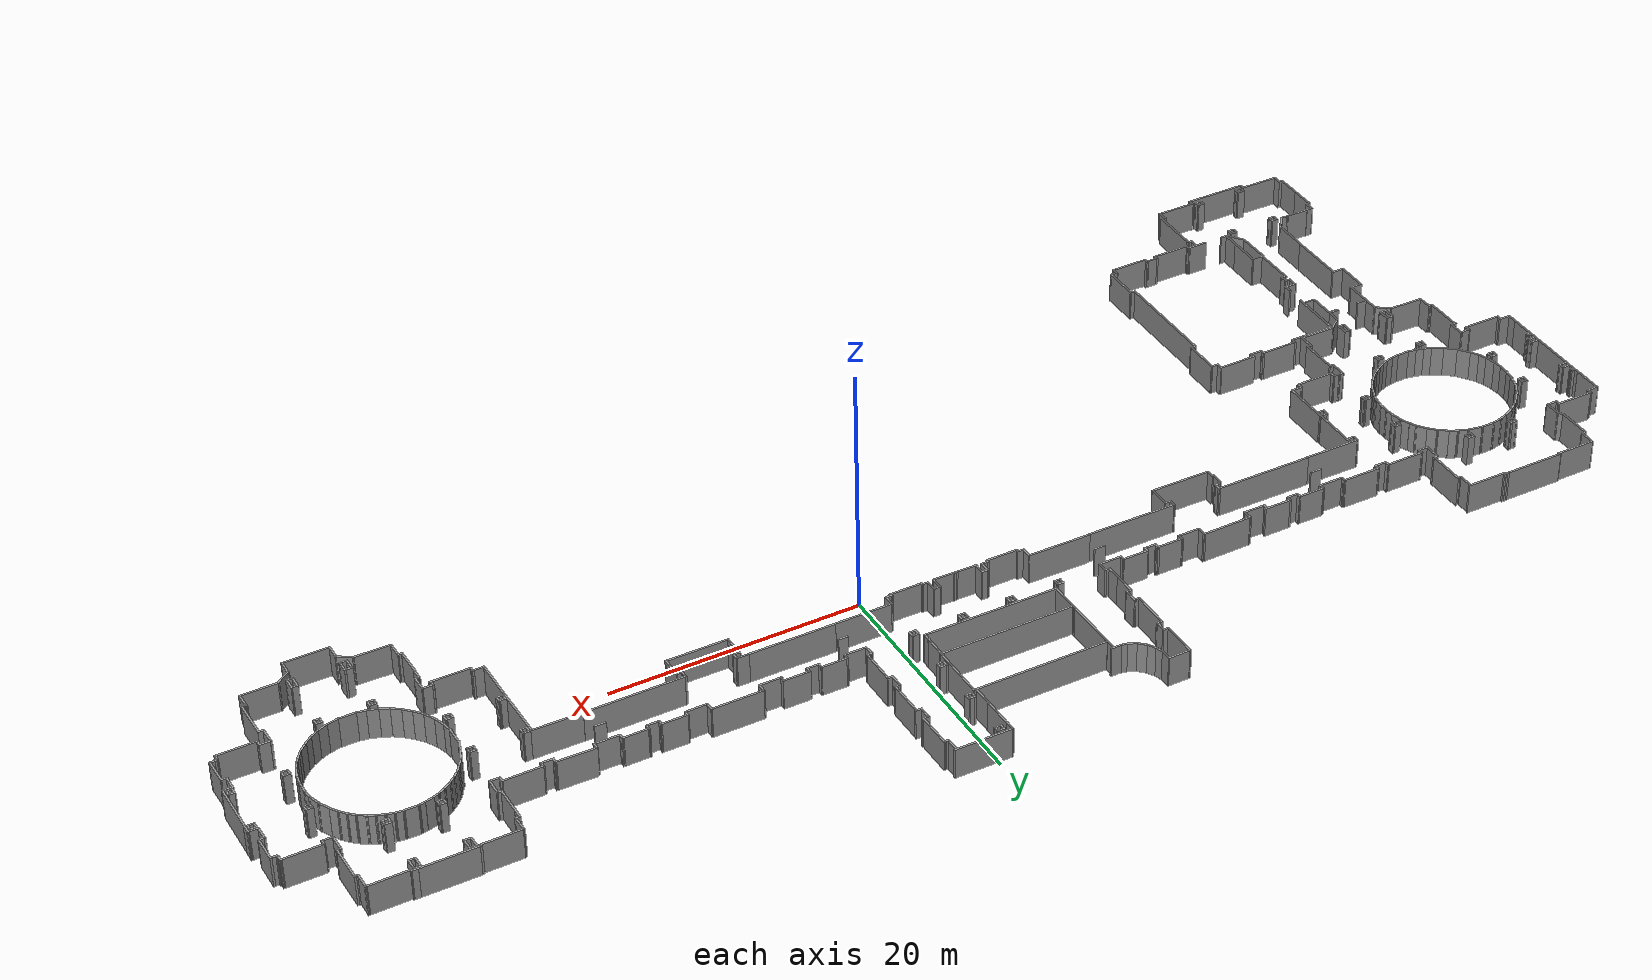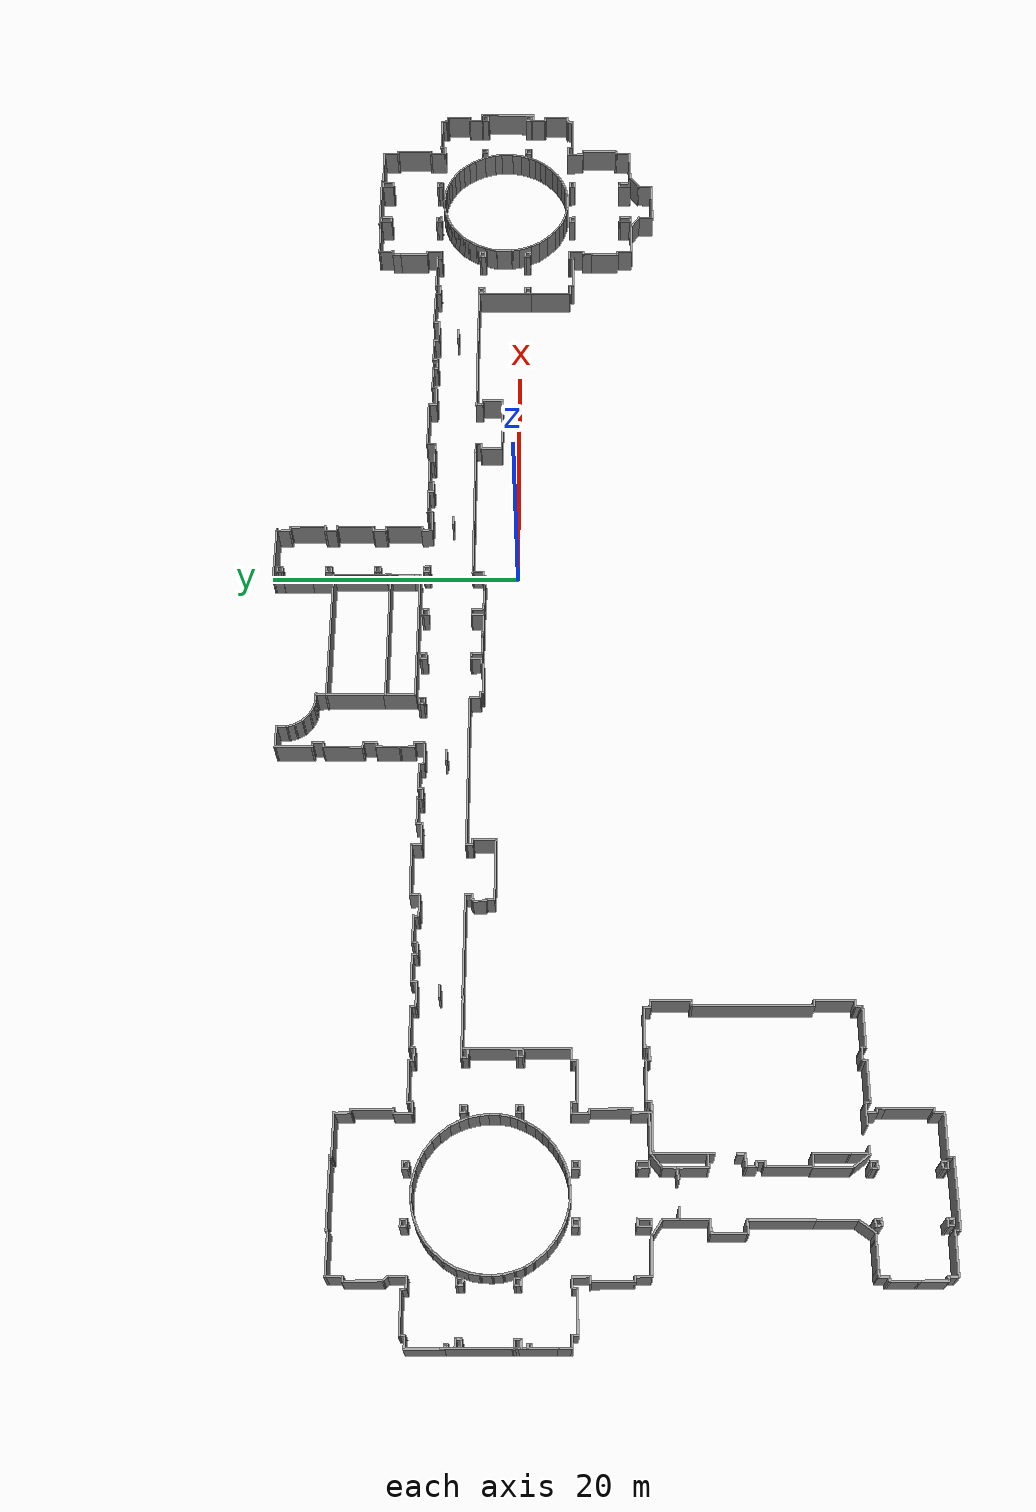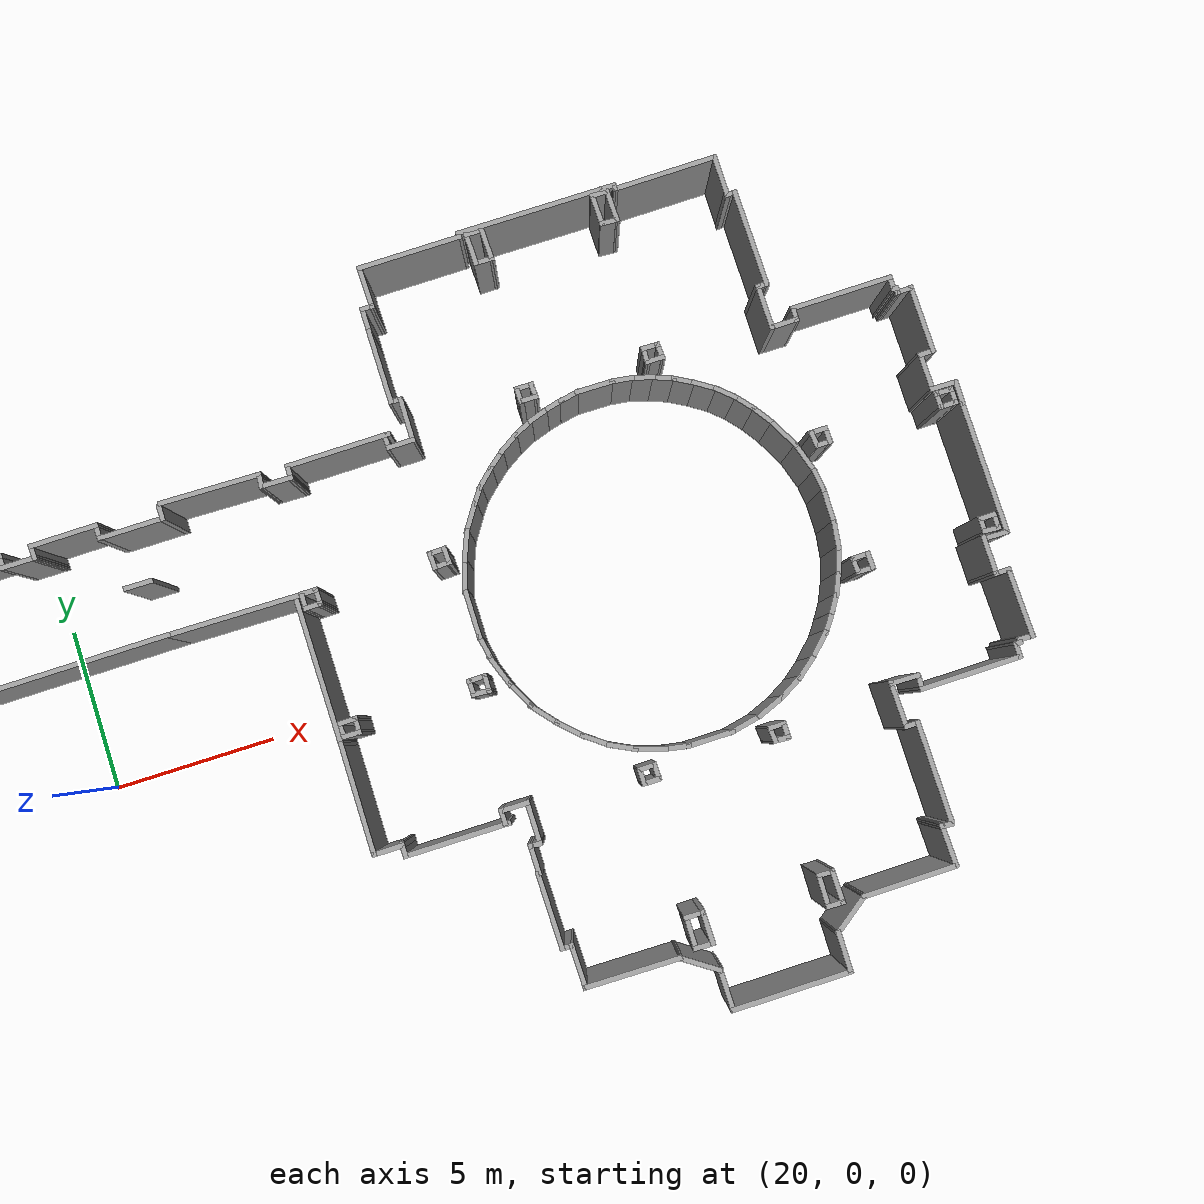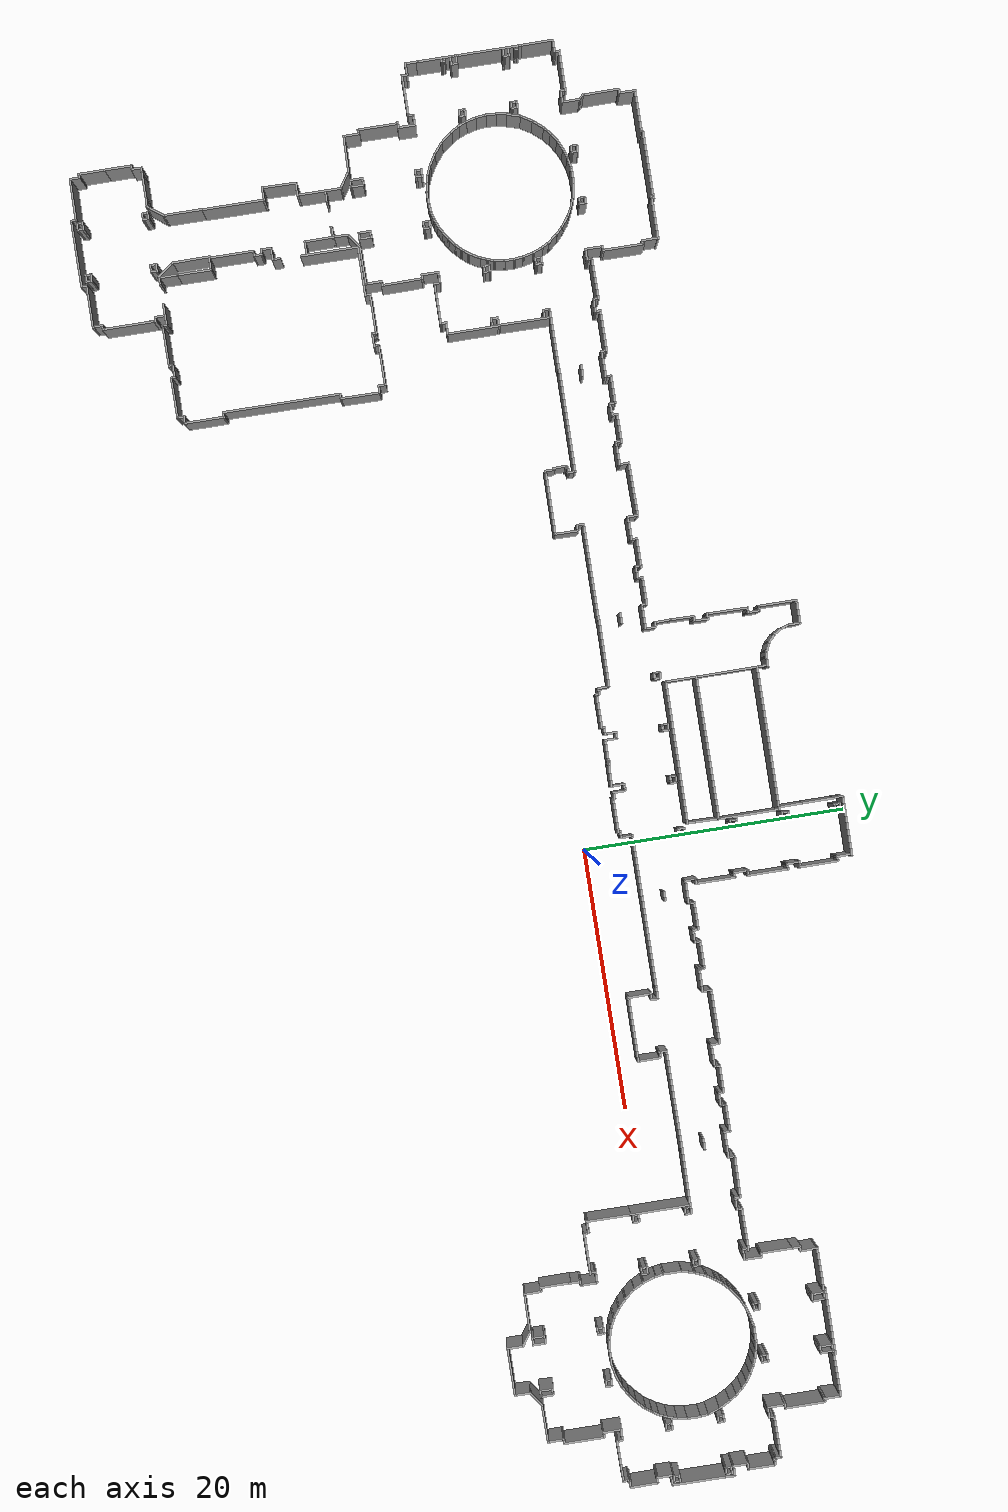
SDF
<?xml version='1.0'?>
<sdf version='1.7'>
  <model name='TD1-Mapa'>
    <pose>-6.249136 -5.50363 0 0 -0 0</pose>
    <link name='Wall_1'>
      <collision name='Wall_1_Collision'>
        <geometry>
          <box>
            <size>4.431935 0.15 2.5</size>
          </box>
        </geometry>
        <pose>0 0 1.25 0 -0 0</pose>
      </collision>
      <visual name='Wall_1_Visual'>
        <pose>0 0 1.25 0 -0 0</pose>
        <geometry>
          <box>
            <size>4.431935 0.15 2.5</size>
          </box>
        </geometry>
        <material>
          <script>
            <uri>file://media/materials/scripts/gazebo.material</uri>
            <name>Gazebo/Grey</name>
          </script>
          <ambient>1 1 1 1</ambient>
        </material>
        <meta>
          <layer>0</layer>
        </meta>
      </visual>
      <pose>-41.074739 -6.4312363 0 0 -0 1.57083</pose>
    </link>
    <link name='Wall_10'>
      <collision name='Wall_10_Collision'>
        <geometry>
          <box>
            <size>3.14133 0.15 2.5</size>
          </box>
        </geometry>
        <pose>0 0 1.25 0 -0 0</pose>
      </collision>
      <visual name='Wall_10_Visual'>
        <pose>0 0 1.25 0 -0 0</pose>
        <geometry>
          <box>
            <size>3.14133 0.15 2.5</size>
          </box>
        </geometry>
        <material>
          <script>
            <uri>file://media/materials/scripts/gazebo.material</uri>
            <name>Gazebo/Grey</name>
          </script>
          <ambient>1 1 1 1</ambient>
        </material>
        <meta>
          <layer>0</layer>
        </meta>
      </visual>
      <pose>-32.074331 -3.879235 0 0 -0 0.0029303</pose>
    </link>
    <link name='Wall_100'>
      <collision name='Wall_100_Collision'>
        <geometry>
          <box>
            <size>4.617933 0.15 2.5</size>
          </box>
        </geometry>
        <pose>0 0 1.25 0 -0 0</pose>
      </collision>
      <visual name='Wall_100_Visual'>
        <pose>0 0 1.25 0 -0 0</pose>
        <geometry>
          <box>
            <size>4.617933 0.15 2.5</size>
          </box>
        </geometry>
        <material>
          <script>
            <uri>file://media/materials/scripts/gazebo.material</uri>
            <name>Gazebo/Grey</name>
          </script>
          <ambient>1 1 1 1</ambient>
        </material>
        <meta>
          <layer>0</layer>
        </meta>
      </visual>
      <pose>-32.01613 9.150732 0 0 -0 -0.0033323</pose>
    </link>
    <link name='Wall_104'>
      <collision name='Wall_104_Collision'>
        <geometry>
          <box>
            <size>2.919735 0.15 2.5</size>
          </box>
        </geometry>
        <pose>0 0 1.25 0 -0 0</pose>
      </collision>
      <visual name='Wall_104_Visual'>
        <pose>0 0 1.25 0 -0 0</pose>
        <geometry>
          <box>
            <size>2.919735 0.15 2.5</size>
          </box>
        </geometry>
        <material>
          <script>
            <uri>file://media/materials/scripts/gazebo.material</uri>
            <name>Gazebo/Grey</name>
          </script>
          <ambient>1 1 1 1</ambient>
        </material>
        <meta>
          <layer>0</layer>
        </meta>
      </visual>
      <pose>-42.06833 -16.77593 0 0 -0 -1.561431</pose>
    </link>
    <link name='Wall_105'>
      <collision name='Wall_105_Collision'>
        <geometry>
          <box>
            <size>1.637439 0.15 2.5</size>
          </box>
        </geometry>
        <pose>0 0 1.25 0 -0 0</pose>
      </collision>
      <visual name='Wall_105_Visual'>
        <pose>0 0 1.25 0 -0 0</pose>
        <geometry>
          <box>
            <size>1.637439 0.15 2.5</size>
          </box>
        </geometry>
        <material>
          <script>
            <uri>file://media/materials/scripts/gazebo.material</uri>
            <name>Gazebo/Grey</name>
          </script>
          <ambient>1 1 1 1</ambient>
        </material>
        <meta>
          <layer>0</layer>
        </meta>
      </visual>
      <pose>-41.61323 -18.75873 0 0 -0 -0.9342383</pose>
    </link>
    <link name='Wall_107'>
      <collision name='Wall_107_Collision'>
        <geometry>
          <box>
            <size>0.671535 0.15 2.5</size>
          </box>
        </geometry>
        <pose>0 0 1.25 0 -0 0</pose>
      </collision>
      <visual name='Wall_107_Visual'>
        <pose>0 0 1.25 0 -0 0</pose>
        <geometry>
          <box>
            <size>0.671535 0.15 2.5</size>
          </box>
        </geometry>
        <material>
          <script>
            <uri>file://media/materials/scripts/gazebo.material</uri>
            <name>Gazebo/Grey</name>
          </script>
          <ambient>1 1 1 1</ambient>
        </material>
        <meta>
          <layer>0</layer>
        </meta>
      </visual>
      <pose>-46.76213 -19.38283 0 0 -0 -0.0499353</pose>
    </link>
    <link name='Wall_108'>
      <collision name='Wall_108_Collision'>
        <geometry>
          <box>
            <size>1.55433 0.15 2.5</size>
          </box>
        </geometry>
        <pose>0 0 1.25 0 -0 0</pose>
      </collision>
      <visual name='Wall_108_Visual'>
        <pose>0 0 1.25 0 -0 0</pose>
        <geometry>
          <box>
            <size>1.55433 0.15 2.5</size>
          </box>
        </geometry>
        <material>
          <script>
            <uri>file://media/materials/scripts/gazebo.material</uri>
            <name>Gazebo/Grey</name>
          </script>
          <ambient>1 1 1 1</ambient>
        </material>
        <meta>
          <layer>0</layer>
        </meta>
      </visual>
      <pose>-46.086 -18.83023 0 0 -0 0.9365353</pose>
    </link>
    <link name='Wall_109'>
      <collision name='Wall_109_Collision'>
        <geometry>
          <box>
            <size>2.984439 0.15 2.5</size>
          </box>
        </geometry>
        <pose>0 0 1.25 0 -0 0</pose>
      </collision>
      <visual name='Wall_109_Visual'>
        <pose>0 0 1.25 0 -0 0</pose>
        <geometry>
          <box>
            <size>2.984439 0.15 2.5</size>
          </box>
        </geometry>
        <material>
          <script>
            <uri>file://media/materials/scripts/gazebo.material</uri>
            <name>Gazebo/Grey</name>
          </script>
          <ambient>1 1 1 1</ambient>
        </material>
        <meta>
          <layer>0</layer>
        </meta>
      </visual>
      <pose>-45.66993 -16.84743 0 0 -0 1.57083</pose>
    </link>
    <link name='Wall_11'>
      <collision name='Wall_11_Collision'>
        <geometry>
          <box>
            <size>0.6370333 0.15 2.5</size>
          </box>
        </geometry>
        <pose>0 0 1.25 0 -0 0</pose>
      </collision>
      <visual name='Wall_11_Visual'>
        <pose>0 0 1.25 0 -0 0</pose>
        <geometry>
          <box>
            <size>0.6370333 0.15 2.5</size>
          </box>
        </geometry>
        <material>
          <script>
            <uri>file://media/materials/scripts/gazebo.material</uri>
            <name>Gazebo/Grey</name>
          </script>
          <ambient>1 1 1 1</ambient>
        </material>
        <meta>
          <layer>0</layer>
        </meta>
      </visual>
      <pose>-30.57313 -4.118338 0 0 -0 -1.552934</pose>
    </link>
    <link name='Wall_111'>
      <collision name='Wall_111_Collision'>
        <geometry>
          <box>
            <size>4.700738 0.15 2.5</size>
          </box>
        </geometry>
        <pose>0 0 1.25 0 -0 0</pose>
      </collision>
      <visual name='Wall_111_Visual'>
        <pose>0 0 1.25 0 -0 0</pose>
        <geometry>
          <box>
            <size>4.700738 0.15 2.5</size>
          </box>
        </geometry>
        <material>
          <script>
            <uri>file://media/materials/scripts/gazebo.material</uri>
            <name>Gazebo/Grey</name>
          </script>
          <ambient>1 1 1 1</ambient>
        </material>
        <meta>
          <layer>0</layer>
        </meta>
      </visual>
      <pose>-45.648 -13.03523 0 0 -0 1.57083</pose>
    </link>
    <link name='Wall_113'>
      <collision name='Wall_113_Collision'>
        <geometry>
          <box>
            <size>1.099532 0.15 2.5</size>
          </box>
        </geometry>
        <pose>0 0 1.25 0 -0 0</pose>
      </collision>
      <visual name='Wall_113_Visual'>
        <pose>0 0 1.25 0 -0 0</pose>
        <geometry>
          <box>
            <size>1.099532 0.15 2.5</size>
          </box>
        </geometry>
        <material>
          <script>
            <uri>file://media/materials/scripts/gazebo.material</uri>
            <name>Gazebo/Grey</name>
          </script>
          <ambient>1 1 1 1</ambient>
        </material>
        <meta>
          <layer>0</layer>
        </meta>
      </visual>
      <pose>-46.09663 -10.66883 0 0 -0 3.141539</pose>
    </link>
    <link name='Wall_114'>
      <collision name='Wall_114_Collision'>
        <geometry>
          <box>
            <size>2.686134 0.15 2.5</size>
          </box>
        </geometry>
        <pose>0 0 1.25 0 -0 0</pose>
      </collision>
      <visual name='Wall_114_Visual'>
        <pose>0 0 1.25 0 -0 0</pose>
        <geometry>
          <box>
            <size>2.686134 0.15 2.5</size>
          </box>
        </geometry>
        <material>
          <script>
            <uri>file://media/materials/scripts/gazebo.material</uri>
            <name>Gazebo/Grey</name>
          </script>
          <ambient>1 1 1 1</ambient>
        </material>
        <meta>
          <layer>0</layer>
        </meta>
      </visual>
      <pose>-46.54843 -9.400933 0 0 -0 1.552837</pose>
    </link>
    <link name='Wall_115'>
      <collision name='Wall_115_Collision'>
        <geometry>
          <box>
            <size>1.0744323 0.15 2.5</size>
          </box>
        </geometry>
        <pose>0 0 1.25 0 -0 0</pose>
      </collision>
      <visual name='Wall_115_Visual'>
        <pose>0 0 1.25 0 -0 0</pose>
        <geometry>
          <box>
            <size>1.0744323 0.15 2.5</size>
          </box>
        </geometry>
        <material>
          <script>
            <uri>file://media/materials/scripts/gazebo.material</uri>
            <name>Gazebo/Grey</name>
          </script>
          <ambient>1 1 1 1</ambient>
        </material>
        <meta>
          <layer>0</layer>
        </meta>
      </visual>
      <pose>-46.06363 -8.129536 0 0 -0 -0.006431</pose>
    </link>
    <link name='Wall_117'>
      <collision name='Wall_117_Collision'>
        <geometry>
          <box>
            <size>3.296832 0.15 2.5</size>
          </box>
        </geometry>
        <pose>0 0 1.25 0 -0 0</pose>
      </collision>
      <visual name='Wall_117_Visual'>
        <pose>0 0 1.25 0 -0 0</pose>
        <geometry>
          <box>
            <size>3.296832 0.15 2.5</size>
          </box>
        </geometry>
        <material>
          <script>
            <uri>file://media/materials/scripts/gazebo.material</uri>
            <name>Gazebo/Grey</name>
          </script>
          <ambient>1 1 1 1</ambient>
        </material>
        <meta>
          <layer>0</layer>
        </meta>
      </visual>
      <pose>-45.60853 -6.4315303 0 0 -0 1.57083</pose>
    </link>
    <link name='Wall_118'>
      <collision name='Wall_118_Collision'>
        <geometry>
          <box>
            <size>1.404333 0.15 2.5</size>
          </box>
        </geometry>
        <pose>0 0 1.25 0 -0 0</pose>
      </collision>
      <visual name='Wall_118_Visual'>
        <pose>0 0 1.25 0 -0 0</pose>
        <geometry>
          <box>
            <size>1.404333 0.15 2.5</size>
          </box>
        </geometry>
        <material>
          <script>
            <uri>file://media/materials/scripts/gazebo.material</uri>
            <name>Gazebo/Grey</name>
          </script>
          <ambient>1 1 1 1</ambient>
        </material>
        <meta>
          <layer>0</layer>
        </meta>
      </visual>
      <pose>-46.13293 -4.517734 0 0 -0 2.561139</pose>
    </link>
    <link name='Wall_12'>
      <collision name='Wall_12_Collision'>
        <geometry>
          <box>
            <size>0.6637303 0.15 2.5</size>
          </box>
        </geometry>
        <pose>0 0 1.25 0 -0 0</pose>
      </collision>
      <visual name='Wall_12_Visual'>
        <pose>0 0 1.25 0 -0 0</pose>
        <geometry>
          <box>
            <size>0.6637303 0.15 2.5</size>
          </box>
        </geometry>
        <material>
          <script>
            <uri>file://media/materials/scripts/gazebo.material</uri>
            <name>Gazebo/Grey</name>
          </script>
          <ambient>1 1 1 1</ambient>
        </material>
        <meta>
          <layer>0</layer>
        </meta>
      </visual>
      <pose>-30.31223 -4.366231 0 0 -0 -0.0169343</pose>
    </link>
    <link name='Wall_121'>
      <collision name='Wall_121_Collision'>
        <geometry>
          <box>
            <size>0.8739353 0.15 2.5</size>
          </box>
        </geometry>
        <pose>0 0 1.25 0 -0 0</pose>
      </collision>
      <visual name='Wall_121_Visual'>
        <pose>0 0 1.25 0 -0 0</pose>
        <geometry>
          <box>
            <size>0.8739353 0.15 2.5</size>
          </box>
        </geometry>
        <material>
          <script>
            <uri>file://media/materials/scripts/gazebo.material</uri>
            <name>Gazebo/Grey</name>
          </script>
          <ambient>1 1 1 1</ambient>
        </material>
        <meta>
          <layer>0</layer>
        </meta>
      </visual>
      <pose>-45.195 -6.03653 0 0 -0 -0.0156323</pose>
    </link>
    <link name='Wall_123'>
      <collision name='Wall_123_Collision'>
        <geometry>
          <box>
            <size>2.886937 0.15 2.5</size>
          </box>
        </geometry>
        <pose>0 0 1.25 0 -0 0</pose>
      </collision>
      <visual name='Wall_123_Visual'>
        <pose>0 0 1.25 0 -0 0</pose>
        <geometry>
          <box>
            <size>2.886937 0.15 2.5</size>
          </box>
        </geometry>
        <material>
          <script>
            <uri>file://media/materials/scripts/gazebo.material</uri>
            <name>Gazebo/Grey</name>
          </script>
          <ambient>1 1 1 1</ambient>
        </material>
        <meta>
          <layer>0</layer>
        </meta>
      </visual>
      <pose>-48.04553 -4.0742393 0 0 -0 3.119734</pose>
    </link>
    <link name='Wall_124'>
      <collision name='Wall_124_Collision'>
        <geometry>
          <box>
            <size>1.282234 0.15 2.5</size>
          </box>
        </geometry>
        <pose>0 0 1.25 0 -0 0</pose>
      </collision>
      <visual name='Wall_124_Visual'>
        <pose>0 0 1.25 0 -0 0</pose>
        <geometry>
          <box>
            <size>1.282234 0.15 2.5</size>
          </box>
        </geometry>
        <material>
          <script>
            <uri>file://media/materials/scripts/gazebo.material</uri>
            <name>Gazebo/Grey</name>
          </script>
          <ambient>1 1 1 1</ambient>
        </material>
        <meta>
          <layer>0</layer>
        </meta>
      </visual>
      <pose>-49.42543 -3.477038 0 0 -0 1.591531</pose>
    </link>
    <link name='Wall_126'>
      <collision name='Wall_126_Collision'>
        <geometry>
          <box>
            <size>0.43153633 0.15 2.5</size>
          </box>
        </geometry>
        <pose>0 0 1.25 0 -0 0</pose>
      </collision>
      <visual name='Wall_126_Visual'>
        <pose>0 0 1.25 0 -0 0</pose>
        <geometry>
          <box>
            <size>0.43153633 0.15 2.5</size>
          </box>
        </geometry>
        <material>
          <script>
            <uri>file://media/materials/scripts/gazebo.material</uri>
            <name>Gazebo/Grey</name>
          </script>
          <ambient>1 1 1 1</ambient>
        </material>
        <meta>
          <layer>0</layer>
        </meta>
      </visual>
      <pose>-49.58423 -2.918035 0 0 -0 -3.092738</pose>
    </link>
    <link name='Wall_127'>
      <collision name='Wall_127_Collision'>
        <geometry>
          <box>
            <size>3.03733 0.15 2.5</size>
          </box>
        </geometry>
        <pose>0 0 1.25 0 -0 0</pose>
      </collision>
      <visual name='Wall_127_Visual'>
        <pose>0 0 1.25 0 -0 0</pose>
        <geometry>
          <box>
            <size>3.03733 0.15 2.5</size>
          </box>
        </geometry>
        <material>
          <script>
            <uri>file://media/materials/scripts/gazebo.material</uri>
            <name>Gazebo/Grey</name>
          </script>
          <ambient>1 1 1 1</ambient>
        </material>
        <meta>
          <layer>0</layer>
        </meta>
      </visual>
      <pose>-49.73273 -1.473936 0 0 -0 1.574739</pose>
    </link>
    <link name='Wall_135'>
      <collision name='Wall_135_Collision'>
        <geometry>
          <box>
            <size>0.5266323 0.15 2.5</size>
          </box>
        </geometry>
        <pose>0 0 1.25 0 -0 0</pose>
      </collision>
      <visual name='Wall_135_Visual'>
        <pose>0 0 1.25 0 -0 0</pose>
        <geometry>
          <box>
            <size>0.5266323 0.15 2.5</size>
          </box>
        </geometry>
        <material>
          <script>
            <uri>file://media/materials/scripts/gazebo.material</uri>
            <name>Gazebo/Grey</name>
          </script>
          <ambient>1 1 1 1</ambient>
        </material>
        <meta>
          <layer>0</layer>
        </meta>
      </visual>
      <pose>-49.63593 0.0964343 0 0 -0 3.141539</pose>
    </link>
    <link name='Wall_137'>
      <collision name='Wall_137_Collision'>
        <geometry>
          <box>
            <size>1.381131 0.15 2.5</size>
          </box>
        </geometry>
        <pose>0 0 1.25 0 -0 0</pose>
      </collision>
      <visual name='Wall_137_Visual'>
        <pose>0 0 1.25 0 -0 0</pose>
        <geometry>
          <box>
            <size>1.381131 0.15 2.5</size>
          </box>
        </geometry>
        <material>
          <script>
            <uri>file://media/materials/scripts/gazebo.material</uri>
            <name>Gazebo/Grey</name>
          </script>
          <ambient>1 1 1 1</ambient>
        </material>
        <meta>
          <layer>0</layer>
        </meta>
      </visual>
      <pose>-49.431639 0.7257373 0 0 -0 1.577734</pose>
    </link>
    <link name='Wall_138'>
      <collision name='Wall_138_Collision'>
        <geometry>
          <box>
            <size>0.8938323 0.15 2.5</size>
          </box>
        </geometry>
        <pose>0 0 1.25 0 -0 0</pose>
      </collision>
      <visual name='Wall_138_Visual'>
        <pose>0 0 1.25 0 -0 0</pose>
        <geometry>
          <box>
            <size>0.8938323 0.15 2.5</size>
          </box>
        </geometry>
        <material>
          <script>
            <uri>file://media/materials/scripts/gazebo.material</uri>
            <name>Gazebo/Grey</name>
          </script>
          <ambient>1 1 1 1</ambient>
        </material>
        <meta>
          <layer>0</layer>
        </meta>
      </visual>
      <pose>-49.813 1.337034 0 0 -0 -3.13013</pose>
    </link>
    <link name='Wall_139'>
      <collision name='Wall_139_Collision'>
        <geometry>
          <box>
            <size>0.4582343 0.15 2.5</size>
          </box>
        </geometry>
        <pose>0 0 1.25 0 -0 0</pose>
      </collision>
      <visual name='Wall_139_Visual'>
        <pose>0 0 1.25 0 -0 0</pose>
        <geometry>
          <box>
            <size>0.4582343 0.15 2.5</size>
          </box>
        </geometry>
        <material>
          <script>
            <uri>file://media/materials/scripts/gazebo.material</uri>
            <name>Gazebo/Grey</name>
          </script>
          <ambient>1 1 1 1</ambient>
        </material>
        <meta>
          <layer>0</layer>
        </meta>
      </visual>
      <pose>-50.18923 1.178838 0 0 -0 -1.598537</pose>
    </link>
    <link name='Wall_141'>
      <collision name='Wall_141_Collision'>
        <geometry>
          <box>
            <size>3.031039 0.15 2.5</size>
          </box>
        </geometry>
        <pose>0 0 1.25 0 -0 0</pose>
      </collision>
      <visual name='Wall_141_Visual'>
        <pose>0 0 1.25 0 -0 0</pose>
        <geometry>
          <box>
            <size>3.031039 0.15 2.5</size>
          </box>
        </geometry>
        <material>
          <script>
            <uri>file://media/materials/scripts/gazebo.material</uri>
            <name>Gazebo/Grey</name>
          </script>
          <ambient>1 1 1 1</ambient>
        </material>
        <meta>
          <layer>0</layer>
        </meta>
      </visual>
      <pose>-51.65113 0.9694323 0 0 -0 -0.0029363</pose>
    </link>
    <link name='Wall_143'>
      <collision name='Wall_143_Collision'>
        <geometry>
          <box>
            <size>0.5432363 0.15 2.5</size>
          </box>
        </geometry>
        <pose>0 0 1.25 0 -0 0</pose>
      </collision>
      <visual name='Wall_143_Visual'>
        <pose>0 0 1.25 0 -0 0</pose>
        <geometry>
          <box>
            <size>0.5432363 0.15 2.5</size>
          </box>
        </geometry>
        <material>
          <script>
            <uri>file://media/materials/scripts/gazebo.material</uri>
            <name>Gazebo/Grey</name>
          </script>
          <ambient>1 1 1 1</ambient>
        </material>
        <meta>
          <layer>0</layer>
        </meta>
      </visual>
      <pose>-53.22283 1.159635 0 0 -0 -1.57083</pose>
    </link>
    <link name='Wall_146'>
      <collision name='Wall_146_Collision'>
        <geometry>
          <box>
            <size>1.008235 0.15 2.5</size>
          </box>
        </geometry>
        <pose>0 0 1.25 0 -0 0</pose>
      </collision>
      <visual name='Wall_146_Visual'>
        <pose>0 0 1.25 0 -0 0</pose>
        <geometry>
          <box>
            <size>1.008235 0.15 2.5</size>
          </box>
        </geometry>
        <material>
          <script>
            <uri>file://media/materials/scripts/gazebo.material</uri>
            <name>Gazebo/Grey</name>
          </script>
          <ambient>1 1 1 1</ambient>
        </material>
        <meta>
          <layer>0</layer>
        </meta>
      </visual>
      <pose>-53.64573 1.355236 0 0 -0 0.0045343</pose>
    </link>
    <link name='Wall_149'>
      <collision name='Wall_149_Collision'>
        <geometry>
          <box>
            <size>1.034735 0.15 2.5</size>
          </box>
        </geometry>
        <pose>0 0 1.25 0 -0 0</pose>
      </collision>
      <visual name='Wall_149_Visual'>
        <pose>0 0 1.25 0 -0 0</pose>
        <geometry>
          <box>
            <size>1.034735 0.15 2.5</size>
          </box>
        </geometry>
        <material>
          <script>
            <uri>file://media/materials/scripts/gazebo.material</uri>
            <name>Gazebo/Grey</name>
          </script>
          <ambient>1 1 1 1</ambient>
        </material>
        <meta>
          <layer>0</layer>
        </meta>
      </visual>
      <pose>-54.074733 1.795638 0 0 -0 -1.565237</pose>
    </link>
    <link name='Wall_151'>
      <collision name='Wall_151_Collision'>
        <geometry>
          <box>
            <size>2.75 0.15 2.5</size>
          </box>
        </geometry>
        <pose>0 0 1.25 0 -0 0</pose>
      </collision>
      <visual name='Wall_151_Visual'>
        <pose>0 0 1.25 0 -0 0</pose>
        <geometry>
          <box>
            <size>2.75 0.15 2.5</size>
          </box>
        </geometry>
        <material>
          <script>
            <uri>file://media/materials/scripts/gazebo.material</uri>
            <name>Gazebo/Grey</name>
          </script>
          <ambient>1 1 1 1</ambient>
        </material>
        <meta>
          <layer>0</layer>
        </meta>
      </visual>
      <pose>-54.074937 3.538035 0 0 -0 1.57083</pose>
    </link>
    <link name='Wall_153'>
      <collision name='Wall_153_Collision'>
        <geometry>
          <box>
            <size>0.3795303 0.15 2.5</size>
          </box>
        </geometry>
        <pose>0 0 1.25 0 -0 0</pose>
      </collision>
      <visual name='Wall_153_Visual'>
        <pose>0 0 1.25 0 -0 0</pose>
        <geometry>
          <box>
            <size>0.3795303 0.15 2.5</size>
          </box>
        </geometry>
        <material>
          <script>
            <uri>file://media/materials/scripts/gazebo.material</uri>
            <name>Gazebo/Grey</name>
          </script>
          <ambient>1 1 1 1</ambient>
        </material>
        <meta>
          <layer>0</layer>
        </meta>
      </visual>
      <pose>-53.91733 4.0747373 0 0 -0 0</pose>
    </link>
    <link name='Wall_154'>
      <collision name='Wall_154_Collision'>
        <geometry>
          <box>
            <size>0.3569363 0.15 2.5</size>
          </box>
        </geometry>
        <pose>0 0 1.25 0 -0 0</pose>
      </collision>
      <visual name='Wall_154_Visual'>
        <pose>0 0 1.25 0 -0 0</pose>
        <geometry>
          <box>
            <size>0.3569363 0.15 2.5</size>
          </box>
        </geometry>
        <material>
          <script>
            <uri>file://media/materials/scripts/gazebo.material</uri>
            <name>Gazebo/Grey</name>
          </script>
          <ambient>1 1 1 1</ambient>
        </material>
        <meta>
          <layer>0</layer>
        </meta>
      </visual>
      <pose>-53.80583 4.181135 0 0 -0 1.602034</pose>
    </link>
    <link name='Wall_155'>
      <collision name='Wall_155_Collision'>
        <geometry>
          <box>
            <size>0.3083373 0.15 2.5</size>
          </box>
        </geometry>
        <pose>0 0 1.25 0 -0 0</pose>
      </collision>
      <visual name='Wall_155_Visual'>
        <pose>0 0 1.25 0 -0 0</pose>
        <geometry>
          <box>
            <size>0.3083373 0.15 2.5</size>
          </box>
        </geometry>
        <material>
          <script>
            <uri>file://media/materials/scripts/gazebo.material</uri>
            <name>Gazebo/Grey</name>
          </script>
          <ambient>1 1 1 1</ambient>
        </material>
        <meta>
          <layer>0</layer>
        </meta>
      </visual>
      <pose>-53.88823 4.284538 0 0 -0 3.141539</pose>
    </link>
    <link name='Wall_157'>
      <collision name='Wall_157_Collision'>
        <geometry>
          <box>
            <size>0.7059333 0.15 2.5</size>
          </box>
        </geometry>
        <pose>0 0 1.25 0 -0 0</pose>
      </collision>
      <visual name='Wall_157_Visual'>
        <pose>0 0 1.25 0 -0 0</pose>
        <geometry>
          <box>
            <size>0.7059333 0.15 2.5</size>
          </box>
        </geometry>
        <material>
          <script>
            <uri>file://media/materials/scripts/gazebo.material</uri>
            <name>Gazebo/Grey</name>
          </script>
          <ambient>1 1 1 1</ambient>
        </material>
        <meta>
          <layer>0</layer>
        </meta>
      </visual>
      <pose>-53.76383 4.750032 0 0 -0 0</pose>
    </link>
    <link name='Wall_158'>
      <collision name='Wall_158_Collision'>
        <geometry>
          <box>
            <size>0.5670303 0.15 2.5</size>
          </box>
        </geometry>
        <pose>0 0 1.25 0 -0 0</pose>
      </collision>
      <visual name='Wall_158_Visual'>
        <pose>0 0 1.25 0 -0 0</pose>
        <geometry>
          <box>
            <size>0.5670303 0.15 2.5</size>
          </box>
        </geometry>
        <material>
          <script>
            <uri>file://media/materials/scripts/gazebo.material</uri>
            <name>Gazebo/Grey</name>
          </script>
          <ambient>1 1 1 1</ambient>
        </material>
        <meta>
          <layer>0</layer>
        </meta>
      </visual>
      <pose>-53.48263 4.958439 0 0 -0 1.555239</pose>
    </link>
    <link name='Wall_159'>
      <collision name='Wall_159_Collision'>
        <geometry>
          <box>
            <size>0.7835343 0.15 2.5</size>
          </box>
        </geometry>
        <pose>0 0 1.25 0 -0 0</pose>
      </collision>
      <visual name='Wall_159_Visual'>
        <pose>0 0 1.25 0 -0 0</pose>
        <geometry>
          <box>
            <size>0.7835343 0.15 2.5</size>
          </box>
        </geometry>
        <material>
          <script>
            <uri>file://media/materials/scripts/gazebo.material</uri>
            <name>Gazebo/Grey</name>
          </script>
          <ambient>1 1 1 1</ambient>
        </material>
        <meta>
          <layer>0</layer>
        </meta>
      </visual>
      <pose>-53.79613 5.171832 0 0 -0 3.126239</pose>
    </link>
    <link name='Wall_16'>
      <collision name='Wall_16_Collision'>
        <geometry>
          <box>
            <size>3.083039 0.15 2.5</size>
          </box>
        </geometry>
        <pose>0 0 1.25 0 -0 0</pose>
      </collision>
      <visual name='Wall_16_Visual'>
        <pose>0 0 1.25 0 -0 0</pose>
        <geometry>
          <box>
            <size>3.083039 0.15 2.5</size>
          </box>
        </geometry>
        <material>
          <script>
            <uri>file://media/materials/scripts/gazebo.material</uri>
            <name>Gazebo/Grey</name>
          </script>
          <ambient>1 1 1 1</ambient>
        </material>
        <meta>
          <layer>0</layer>
        </meta>
      </visual>
      <pose>-30.06263 -5.837039 0 0 -0 -1.575533</pose>
    </link>
    <link name='Wall_162'>
      <collision name='Wall_162_Collision'>
        <geometry>
          <box>
            <size>0.5508303 0.15 2.5</size>
          </box>
        </geometry>
        <pose>0 0 1.25 0 -0 0</pose>
      </collision>
      <visual name='Wall_162_Visual'>
        <pose>0 0 1.25 0 -0 0</pose>
        <geometry>
          <box>
            <size>0.5508303 0.15 2.5</size>
          </box>
        </geometry>
        <material>
          <script>
            <uri>file://media/materials/scripts/gazebo.material</uri>
            <name>Gazebo/Grey</name>
          </script>
          <ambient>1 1 1 1</ambient>
        </material>
        <meta>
          <layer>0</layer>
        </meta>
      </visual>
      <pose>-54.074235 5.082933 0 0 -0 1.578836</pose>
    </link>
    <link name='Wall_166'>
      <collision name='Wall_166_Collision'>
        <geometry>
          <box>
            <size>5.365332 0.15 2.5</size>
          </box>
        </geometry>
        <pose>0 0 1.25 0 -0 0</pose>
      </collision>
      <visual name='Wall_166_Visual'>
        <pose>0 0 1.25 0 -0 0</pose>
        <geometry>
          <box>
            <size>5.365332 0.15 2.5</size>
          </box>
        </geometry>
        <material>
          <script>
            <uri>file://media/materials/scripts/gazebo.material</uri>
            <name>Gazebo/Grey</name>
          </script>
          <ambient>1 1 1 1</ambient>
        </material>
        <meta>
          <layer>0</layer>
        </meta>
      </visual>
      <pose>-54.07433 7.49023 0 0 -0 -1.569936</pose>
    </link>
    <link name='Wall_169'>
      <collision name='Wall_169_Collision'>
        <geometry>
          <box>
            <size>0.3019333 0.15 2.5</size>
          </box>
        </geometry>
        <pose>0 0 1.25 0 -0 0</pose>
      </collision>
      <visual name='Wall_169_Visual'>
        <pose>0 0 1.25 0 -0 0</pose>
        <geometry>
          <box>
            <size>0.3019333 0.15 2.5</size>
          </box>
        </geometry>
        <material>
          <script>
            <uri>file://media/materials/scripts/gazebo.material</uri>
            <name>Gazebo/Grey</name>
          </script>
          <ambient>1 1 1 1</ambient>
        </material>
        <meta>
          <layer>0</layer>
        </meta>
      </visual>
      <pose>-53.82243 9.706438 0 0 -0 -1.644135</pose>
    </link>
    <link name='Wall_17'>
      <collision name='Wall_17_Collision'>
        <geometry>
          <box>
            <size>0.4964333 0.15 2.5</size>
          </box>
        </geometry>
        <pose>0 0 1.25 0 -0 0</pose>
      </collision>
      <visual name='Wall_17_Visual'>
        <pose>0 0 1.25 0 -0 0</pose>
        <geometry>
          <box>
            <size>0.4964333 0.15 2.5</size>
          </box>
        </geometry>
        <material>
          <script>
            <uri>file://media/materials/scripts/gazebo.material</uri>
            <name>Gazebo/Grey</name>
          </script>
          <ambient>1 1 1 1</ambient>
        </material>
        <meta>
          <layer>0</layer>
        </meta>
      </visual>
      <pose>-30.24243 -7.304738 0 0 -0 -3.134935</pose>
    </link>
    <link name='Wall_170'>
      <collision name='Wall_170_Collision'>
        <geometry>
          <box>
            <size>0.3436333 0.15 2.5</size>
          </box>
        </geometry>
        <pose>0 0 1.25 0 -0 0</pose>
      </collision>
      <visual name='Wall_170_Visual'>
        <pose>0 0 1.25 0 -0 0</pose>
        <geometry>
          <box>
            <size>0.3436333 0.15 2.5</size>
          </box>
        </geometry>
        <material>
          <script>
            <uri>file://media/materials/scripts/gazebo.material</uri>
            <name>Gazebo/Grey</name>
          </script>
          <ambient>1 1 1 1</ambient>
        </material>
        <meta>
          <layer>0</layer>
        </meta>
      </visual>
      <pose>-53.92463 9.624931 0 0 -0 -3.082834</pose>
    </link>
    <link name='Wall_173'>
      <collision name='Wall_173_Collision'>
        <geometry>
          <box>
            <size>0.3916333 0.15 2.5</size>
          </box>
        </geometry>
        <pose>0 0 1.25 0 -0 0</pose>
      </collision>
      <visual name='Wall_173_Visual'>
        <pose>0 0 1.25 0 -0 0</pose>
        <geometry>
          <box>
            <size>0.3916333 0.15 2.5</size>
          </box>
        </geometry>
        <material>
          <script>
            <uri>file://media/materials/scripts/gazebo.material</uri>
            <name>Gazebo/Grey</name>
          </script>
          <ambient>1 1 1 1</ambient>
        </material>
        <meta>
          <layer>0</layer>
        </meta>
      </visual>
      <pose>-53.93463 9.796237 0 0 -0 0.0153383</pose>
    </link>
    <link name='Wall_175'>
      <collision name='Wall_175_Collision'>
        <geometry>
          <box>
            <size>0.7298363 0.15 2.5</size>
          </box>
        </geometry>
        <pose>0 0 1.25 0 -0 0</pose>
      </collision>
      <visual name='Wall_175_Visual'>
        <pose>0 0 1.25 0 -0 0</pose>
        <geometry>
          <box>
            <size>0.7298363 0.15 2.5</size>
          </box>
        </geometry>
        <material>
          <script>
            <uri>file://media/materials/scripts/gazebo.material</uri>
            <name>Gazebo/Grey</name>
          </script>
          <ambient>1 1 1 1</ambient>
        </material>
        <meta>
          <layer>0</layer>
        </meta>
      </visual>
      <pose>-53.75063 9.129036 0 0 -0 0</pose>
    </link>
    <link name='Wall_176'>
      <collision name='Wall_176_Collision'>
        <geometry>
          <box>
            <size>0.5515393 0.15 2.5</size>
          </box>
        </geometry>
        <pose>0 0 1.25 0 -0 0</pose>
      </collision>
      <visual name='Wall_176_Visual'>
        <pose>0 0 1.25 0 -0 0</pose>
        <geometry>
          <box>
            <size>0.5515393 0.15 2.5</size>
          </box>
        </geometry>
        <material>
          <script>
            <uri>file://media/materials/scripts/gazebo.material</uri>
            <name>Gazebo/Grey</name>
          </script>
          <ambient>1 1 1 1</ambient>
        </material>
        <meta>
          <layer>0</layer>
        </meta>
      </visual>
      <pose>-53.45513 8.928334 0 0 -0 -1.543033</pose>
    </link>
    <link name='Wall_177'>
      <collision name='Wall_177_Collision'>
        <geometry>
          <box>
            <size>0.7112373 0.15 2.5</size>
          </box>
        </geometry>
        <pose>0 0 1.25 0 -0 0</pose>
      </collision>
      <visual name='Wall_177_Visual'>
        <pose>0 0 1.25 0 -0 0</pose>
        <geometry>
          <box>
            <size>0.7112373 0.15 2.5</size>
          </box>
        </geometry>
        <material>
          <script>
            <uri>file://media/materials/scripts/gazebo.material</uri>
            <name>Gazebo/Grey</name>
          </script>
          <ambient>1 1 1 1</ambient>
        </material>
        <meta>
          <layer>0</layer>
        </meta>
      </visual>
      <pose>-53.73013 8.727632 0 0 -0 3.141539</pose>
    </link>
    <link name='Wall_179'>
      <collision name='Wall_179_Collision'>
        <geometry>
          <box>
            <size>2.78163 0.15 2.5</size>
          </box>
        </geometry>
        <pose>0 0 1.25 0 -0 0</pose>
      </collision>
      <visual name='Wall_179_Visual'>
        <pose>0 0 1.25 0 -0 0</pose>
        <geometry>
          <box>
            <size>2.78163 0.15 2.5</size>
          </box>
        </geometry>
        <material>
          <script>
            <uri>file://media/materials/scripts/gazebo.material</uri>
            <name>Gazebo/Grey</name>
          </script>
          <ambient>1 1 1 1</ambient>
        </material>
        <meta>
          <layer>0</layer>
        </meta>
      </visual>
      <pose>-54.09353 11.20193 0 0 -0 -1.565038</pose>
    </link>
    <link name='Wall_181'>
      <collision name='Wall_181_Collision'>
        <geometry>
          <box>
            <size>1.031938 0.15 2.5</size>
          </box>
        </geometry>
        <pose>0 0 1.25 0 -0 0</pose>
      </collision>
      <visual name='Wall_181_Visual'>
        <pose>0 0 1.25 0 -0 0</pose>
        <geometry>
          <box>
            <size>1.031938 0.15 2.5</size>
          </box>
        </geometry>
        <material>
          <script>
            <uri>file://media/materials/scripts/gazebo.material</uri>
            <name>Gazebo/Grey</name>
          </script>
          <ambient>1 1 1 1</ambient>
        </material>
        <meta>
          <layer>0</layer>
        </meta>
      </visual>
      <pose>-53.66 12.52073 0 0 -0 0.0067373</pose>
    </link>
    <link name='Wall_182'>
      <collision name='Wall_182_Collision'>
        <geometry>
          <box>
            <size>0.4990353 0.15 2.5</size>
          </box>
        </geometry>
        <pose>0 0 1.25 0 -0 0</pose>
      </collision>
      <visual name='Wall_182_Visual'>
        <pose>0 0 1.25 0 -0 0</pose>
        <geometry>
          <box>
            <size>0.4990353 0.15 2.5</size>
          </box>
        </geometry>
        <material>
          <script>
            <uri>file://media/materials/scripts/gazebo.material</uri>
            <name>Gazebo/Grey</name>
          </script>
          <ambient>1 1 1 1</ambient>
        </material>
        <meta>
          <layer>0</layer>
        </meta>
      </visual>
      <pose>-53.22153 12.69823 0 0 -0 1.584838</pose>
    </link>
    <link name='Wall_183'>
      <collision name='Wall_183_Collision'>
        <geometry>
          <box>
            <size>3.133932 0.15 2.5</size>
          </box>
        </geometry>
        <pose>0 0 1.25 0 -0 0</pose>
      </collision>
      <visual name='Wall_183_Visual'>
        <pose>0 0 1.25 0 -0 0</pose>
        <geometry>
          <box>
            <size>3.133932 0.15 2.5</size>
          </box>
        </geometry>
        <material>
          <script>
            <uri>file://media/materials/scripts/gazebo.material</uri>
            <name>Gazebo/Grey</name>
          </script>
          <ambient>1 1 1 1</ambient>
        </material>
        <meta>
          <layer>0</layer>
        </meta>
      </visual>
      <pose>-51.732 12.86773 0 0 -0 -0.0032393</pose>
    </link>
    <link name='Wall_184'>
      <collision name='Wall_184_Collision'>
        <geometry>
          <box>
            <size>0.4795303 0.15 2.5</size>
          </box>
        </geometry>
        <pose>0 0 1.25 0 -0 0</pose>
      </collision>
      <visual name='Wall_184_Visual'>
        <pose>0 0 1.25 0 -0 0</pose>
        <geometry>
          <box>
            <size>0.4795303 0.15 2.5</size>
          </box>
        </geometry>
        <material>
          <script>
            <uri>file://media/materials/scripts/gazebo.material</uri>
            <name>Gazebo/Grey</name>
          </script>
          <ambient>1 1 1 1</ambient>
        </material>
        <meta>
          <layer>0</layer>
        </meta>
      </visual>
      <pose>-50.24523 12.69823 0 0 -0 -1.540935</pose>
    </link>
    <link name='Wall_185'>
      <collision name='Wall_185_Collision'>
        <geometry>
          <box>
            <size>0.9611363 0.15 2.5</size>
          </box>
        </geometry>
        <pose>0 0 1.25 0 -0 0</pose>
      </collision>
      <visual name='Wall_185_Visual'>
        <pose>0 0 1.25 0 -0 0</pose>
        <geometry>
          <box>
            <size>0.9611363 0.15 2.5</size>
          </box>
        </geometry>
        <material>
          <script>
            <uri>file://media/materials/scripts/gazebo.material</uri>
            <name>Gazebo/Grey</name>
          </script>
          <ambient>1 1 1 1</ambient>
        </material>
        <meta>
          <layer>0</layer>
        </meta>
      </visual>
      <pose>-49.82473 12.52863 0 0 -0 -0.0121323</pose>
    </link>
    <link name='Wall_187'>
      <collision name='Wall_187_Collision'>
        <geometry>
          <box>
            <size>1.389434 0.15 2.5</size>
          </box>
        </geometry>
        <pose>0 0 1.25 0 -0 0</pose>
      </collision>
      <visual name='Wall_187_Visual'>
        <pose>0 0 1.25 0 -0 0</pose>
        <geometry>
          <box>
            <size>1.389434 0.15 2.5</size>
          </box>
        </geometry>
        <material>
          <script>
            <uri>file://media/materials/scripts/gazebo.material</uri>
            <name>Gazebo/Grey</name>
          </script>
          <ambient>1 1 1 1</ambient>
        </material>
        <meta>
          <layer>0</layer>
        </meta>
      </visual>
      <pose>-49.41843 13.19363 0 0 -0 1.579937</pose>
    </link>
    <link name='Wall_188'>
      <collision name='Wall_188_Collision'>
        <geometry>
          <box>
            <size>0.5447303 0.15 2.5</size>
          </box>
        </geometry>
        <pose>0 0 1.25 0 -0 0</pose>
      </collision>
      <visual name='Wall_188_Visual'>
        <pose>0 0 1.25 0 -0 0</pose>
        <geometry>
          <box>
            <size>0.5447303 0.15 2.5</size>
          </box>
        </geometry>
        <material>
          <script>
            <uri>file://media/materials/scripts/gazebo.material</uri>
            <name>Gazebo/Grey</name>
          </script>
          <ambient>1 1 1 1</ambient>
        </material>
        <meta>
          <layer>0</layer>
        </meta>
      </visual>
      <pose>-49.55483 13.96123 0 0 -0 2.295035</pose>
    </link>
    <link name='Wall_189'>
      <collision name='Wall_189_Collision'>
        <geometry>
          <box>
            <size>2.856339 0.15 2.5</size>
          </box>
        </geometry>
        <pose>0 0 1.25 0 -0 0</pose>
      </collision>
      <visual name='Wall_189_Visual'>
        <pose>0 0 1.25 0 -0 0</pose>
        <geometry>
          <box>
            <size>2.856339 0.15 2.5</size>
          </box>
        </geometry>
        <material>
          <script>
            <uri>file://media/materials/scripts/gazebo.material</uri>
            <name>Gazebo/Grey</name>
          </script>
          <ambient>1 1 1 1</ambient>
        </material>
        <meta>
          <layer>0</layer>
        </meta>
      </visual>
      <pose>-49.70263 15.45073 0 0 -0 1.58343</pose>
    </link>
    <link name='Wall_192'>
      <collision name='Wall_192_Collision'>
        <geometry>
          <box>
            <size>0.411637 0.15 2.5</size>
          </box>
        </geometry>
        <pose>0 0 1.25 0 -0 0</pose>
      </collision>
      <visual name='Wall_192_Visual'>
        <pose>0 0 1.25 0 -0 0</pose>
        <geometry>
          <box>
            <size>0.411637 0.15 2.5</size>
          </box>
        </geometry>
        <material>
          <script>
            <uri>file://media/materials/scripts/gazebo.material</uri>
            <name>Gazebo/Grey</name>
          </script>
          <ambient>1 1 1 1</ambient>
        </material>
        <meta>
          <layer>0</layer>
        </meta>
      </visual>
      <pose>-49.56023 16.84133 0 0 -0 0</pose>
    </link>
    <link name='Wall_193'>
      <collision name='Wall_193_Collision'>
        <geometry>
          <box>
            <size>1.323837 0.15 2.5</size>
          </box>
        </geometry>
        <pose>0 0 1.25 0 -0 0</pose>
      </collision>
      <visual name='Wall_193_Visual'>
        <pose>0 0 1.25 0 -0 0</pose>
        <geometry>
          <box>
            <size>1.323837 0.15 2.5</size>
          </box>
        </geometry>
        <material>
          <script>
            <uri>file://media/materials/scripts/gazebo.material</uri>
            <name>Gazebo/Grey</name>
          </script>
          <ambient>1 1 1 1</ambient>
        </material>
        <meta>
          <layer>0</layer>
        </meta>
      </visual>
      <pose>-49.42193 17.42823 0 0 -0 1.558036</pose>
    </link>
    <link name='Wall_194'>
      <collision name='Wall_194_Collision'>
        <geometry>
          <box>
            <size>3.240233 0.15 2.5</size>
          </box>
        </geometry>
        <pose>0 0 1.25 0 -0 0</pose>
      </collision>
      <visual name='Wall_194_Visual'>
        <pose>0 0 1.25 0 -0 0</pose>
        <geometry>
          <box>
            <size>3.240233 0.15 2.5</size>
          </box>
        </geometry>
        <material>
          <script>
            <uri>file://media/materials/scripts/gazebo.material</uri>
            <name>Gazebo/Grey</name>
          </script>
          <ambient>1 1 1 1</ambient>
        </material>
        <meta>
          <layer>0</layer>
        </meta>
      </visual>
      <pose>-47.87433 18.01513 0 0 -0 0</pose>
    </link>
    <link name='Wall_195'>
      <collision name='Wall_195_Collision'>
        <geometry>
          <box>
            <size>0.2546363 0.15 2.5</size>
          </box>
        </geometry>
        <pose>0 0 1.25 0 -0 0</pose>
      </collision>
      <visual name='Wall_195_Visual'>
        <pose>0 0 1.25 0 -0 0</pose>
        <geometry>
          <box>
            <size>0.2546363 0.15 2.5</size>
          </box>
        </geometry>
        <material>
          <script>
            <uri>file://media/materials/scripts/gazebo.material</uri>
            <name>Gazebo/Grey</name>
          </script>
          <ambient>1 1 1 1</ambient>
        </material>
        <meta>
          <layer>0</layer>
        </meta>
      </visual>
      <pose>-46.33423 18.06753 0 0 -0 1.57083</pose>
    </link>
    <link name='Wall_196'>
      <collision name='Wall_196_Collision'>
        <geometry>
          <box>
            <size>4.852539 0.15 2.5</size>
          </box>
        </geometry>
        <pose>0 0 1.25 0 -0 0</pose>
      </collision>
      <visual name='Wall_196_Visual'>
        <pose>0 0 1.25 0 -0 0</pose>
        <geometry>
          <box>
            <size>4.852539 0.15 2.5</size>
          </box>
        </geometry>
        <material>
          <script>
            <uri>file://media/materials/scripts/gazebo.material</uri>
            <name>Gazebo/Grey</name>
          </script>
          <ambient>1 1 1 1</ambient>
        </material>
        <meta>
          <layer>0</layer>
        </meta>
      </visual>
      <pose>-43.98293 18.12353 0 0 -0 0.001539</pose>
    </link>
    <link name='Wall_198'>
      <collision name='Wall_198_Collision'>
        <geometry>
          <box>
            <size>0.4490353 0.15 2.5</size>
          </box>
        </geometry>
        <pose>0 0 1.25 0 -0 0</pose>
      </collision>
      <visual name='Wall_198_Visual'>
        <pose>0 0 1.25 0 -0 0</pose>
        <geometry>
          <box>
            <size>0.4490353 0.15 2.5</size>
          </box>
        </geometry>
        <material>
          <script>
            <uri>file://media/materials/scripts/gazebo.material</uri>
            <name>Gazebo/Grey</name>
          </script>
          <ambient>1 1 1 1</ambient>
        </material>
        <meta>
          <layer>0</layer>
        </meta>
      </visual>
      <pose>-41.39243 18.15723 0 0 -0 0</pose>
    </link>
    <link name='Wall_2'>
      <collision name='Wall_2_Collision'>
        <geometry>
          <box>
            <size>3.795532 0.15 2.5</size>
          </box>
        </geometry>
        <pose>0 0 1.25 0 -0 0</pose>
      </collision>
      <visual name='Wall_2_Visual'>
        <pose>0 0 1.25 0 -0 0</pose>
        <geometry>
          <box>
            <size>3.795532 0.15 2.5</size>
          </box>
        </geometry>
        <material>
          <script>
            <uri>file://media/materials/scripts/gazebo.material</uri>
            <name>Gazebo/Grey</name>
          </script>
          <ambient>1 1 1 1</ambient>
        </material>
        <meta>
          <layer>0</layer>
        </meta>
      </visual>
      <pose>-39.25523 -4.287838 0 0 -0 0</pose>
    </link>
    <link name='Wall_20'>
      <collision name='Wall_20_Collision'>
        <geometry>
          <box>
            <size>9 0.15 2.5</size>
          </box>
        </geometry>
        <pose>0 0 1.25 0 -0 0</pose>
      </collision>
      <visual name='Wall_20_Visual'>
        <pose>0 0 1.25 0 -0 0</pose>
        <geometry>
          <box>
            <size>9 0.15 2.5</size>
          </box>
        </geometry>
        <material>
          <script>
            <uri>file://media/materials/scripts/gazebo.material</uri>
            <name>Gazebo/Grey</name>
          </script>
          <ambient>1 1 1 1</ambient>
        </material>
        <meta>
          <layer>0</layer>
        </meta>
      </visual>
      <pose>-30.41513 -11.73093 0 0 -0 -1.57083</pose>
    </link>
    <link name='Wall_203'>
      <collision name='Wall_203_Collision'>
        <geometry>
          <box>
            <size>0.3076313 0.15 2.5</size>
          </box>
        </geometry>
        <pose>0 0 1.25 0 -0 0</pose>
      </collision>
      <visual name='Wall_203_Visual'>
        <pose>0 0 1.25 0 -0 0</pose>
        <geometry>
          <box>
            <size>0.3076313 0.15 2.5</size>
          </box>
        </geometry>
        <material>
          <script>
            <uri>file://media/materials/scripts/gazebo.material</uri>
            <name>Gazebo/Grey</name>
          </script>
          <ambient>1 1 1 1</ambient>
        </material>
        <meta>
          <layer>0</layer>
        </meta>
      </visual>
      <pose>-41.39223 18.08623 0 0 -0 -1.57083</pose>
    </link>
    <link name='Wall_204'>
      <collision name='Wall_204_Collision'>
        <geometry>
          <box>
            <size>3.340335 0.15 2.5</size>
          </box>
        </geometry>
        <pose>0 0 1.25 0 -0 0</pose>
      </collision>
      <visual name='Wall_204_Visual'>
        <pose>0 0 1.25 0 -0 0</pose>
        <geometry>
          <box>
            <size>3.340335 0.15 2.5</size>
          </box>
        </geometry>
        <material>
          <script>
            <uri>file://media/materials/scripts/gazebo.material</uri>
            <name>Gazebo/Grey</name>
          </script>
          <ambient>1 1 1 1</ambient>
        </material>
        <meta>
          <layer>0</layer>
        </meta>
      </visual>
      <pose>-39.79713 18.00513 0 0 -0 -0.0015343</pose>
    </link>
    <link name='Wall_206'>
      <collision name='Wall_206_Collision'>
        <geometry>
          <box>
            <size>1.30533 0.15 2.5</size>
          </box>
        </geometry>
        <pose>0 0 1.25 0 -0 0</pose>
      </collision>
      <visual name='Wall_206_Visual'>
        <pose>0 0 1.25 0 -0 0</pose>
        <geometry>
          <box>
            <size>1.30533 0.15 2.5</size>
          </box>
        </geometry>
        <material>
          <script>
            <uri>file://media/materials/scripts/gazebo.material</uri>
            <name>Gazebo/Grey</name>
          </script>
          <ambient>1 1 1 1</ambient>
        </material>
        <meta>
          <layer>0</layer>
        </meta>
      </visual>
      <pose>-38.25353 17.39563 0 0 -0 -1.558033</pose>
    </link>
    <link name='Wall_207'>
      <collision name='Wall_207_Collision'>
        <geometry>
          <box>
            <size>0.4007303 0.15 2.5</size>
          </box>
        </geometry>
        <pose>0 0 1.25 0 -0 0</pose>
      </collision>
      <visual name='Wall_207_Visual'>
        <pose>0 0 1.25 0 -0 0</pose>
        <geometry>
          <box>
            <size>0.4007303 0.15 2.5</size>
          </box>
        </geometry>
        <material>
          <script>
            <uri>file://media/materials/scripts/gazebo.material</uri>
            <name>Gazebo/Grey</name>
          </script>
          <ambient>1 1 1 1</ambient>
        </material>
        <meta>
          <layer>0</layer>
        </meta>
      </visual>
      <pose>-38.12083 16.818 0 0 -0 0</pose>
    </link>
    <link name='Wall_21'>
      <collision name='Wall_21_Collision'>
        <geometry>
          <box>
            <size>0.5 0.15 2.5</size>
          </box>
        </geometry>
        <pose>0 0 1.25 0 -0 0</pose>
      </collision>
      <visual name='Wall_21_Visual'>
        <pose>0 0 1.25 0 -0 0</pose>
        <geometry>
          <box>
            <size>0.5 0.15 2.5</size>
          </box>
        </geometry>
        <material>
          <script>
            <uri>file://media/materials/scripts/gazebo.material</uri>
            <name>Gazebo/Grey</name>
          </script>
          <ambient>1 1 1 1</ambient>
        </material>
        <meta>
          <layer>0</layer>
        </meta>
      </visual>
      <pose>-30.24013 -16.15593 0 0 -0 0</pose>
    </link>
    <link name='Wall_211'>
      <collision name='Wall_211_Collision'>
        <geometry>
          <box>
            <size>3.187537 0.15 2.5</size>
          </box>
        </geometry>
        <pose>0 0 1.25 0 -0 0</pose>
      </collision>
      <visual name='Wall_211_Visual'>
        <pose>0 0 1.25 0 -0 0</pose>
        <geometry>
          <box>
            <size>3.187537 0.15 2.5</size>
          </box>
        </geometry>
        <material>
          <script>
            <uri>file://media/materials/scripts/gazebo.material</uri>
            <name>Gazebo/Grey</name>
          </script>
          <ambient>1 1 1 1</ambient>
        </material>
        <meta>
          <layer>0</layer>
        </meta>
      </visual>
      <pose>-37.98273 15.33993 0 0 -0 -1.57083</pose>
    </link>
    <link name='Wall_213'>
      <collision name='Wall_213_Collision'>
        <geometry>
          <box>
            <size>0.43123433 0.15 2.5</size>
          </box>
        </geometry>
        <pose>0 0 1.25 0 -0 0</pose>
      </collision>
      <visual name='Wall_213_Visual'>
        <pose>0 0 1.25 0 -0 0</pose>
        <geometry>
          <box>
            <size>0.43123433 0.15 2.5</size>
          </box>
        </geometry>
        <material>
          <script>
            <uri>file://media/materials/scripts/gazebo.material</uri>
            <name>Gazebo/Grey</name>
          </script>
          <ambient>1 1 1 1</ambient>
        </material>
        <meta>
          <layer>0</layer>
        </meta>
      </visual>
      <pose>-38.11263 13.80983 0 0 -0 3.141539</pose>
    </link>
    <link name='Wall_215'>
      <collision name='Wall_215_Collision'>
        <geometry>
          <box>
            <size>1.410635 0.15 2.5</size>
          </box>
        </geometry>
        <pose>0 0 1.25 0 -0 0</pose>
      </collision>
      <visual name='Wall_215_Visual'>
        <pose>0 0 1.25 0 -0 0</pose>
        <geometry>
          <box>
            <size>1.410635 0.15 2.5</size>
          </box>
        </geometry>
        <material>
          <script>
            <uri>file://media/materials/scripts/gazebo.material</uri>
            <name>Gazebo/Grey</name>
          </script>
          <ambient>1 1 1 1</ambient>
        </material>
        <meta>
          <layer>0</layer>
        </meta>
      </visual>
      <pose>-38.26843 13.15043 0 0 -0 -1.57083</pose>
    </link>
    <link name='Wall_216'>
      <collision name='Wall_216_Collision'>
        <geometry>
          <box>
            <size>0.941434 0.15 2.5</size>
          </box>
        </geometry>
        <pose>0 0 1.25 0 -0 0</pose>
      </collision>
      <visual name='Wall_216_Visual'>
        <pose>0 0 1.25 0 -0 0</pose>
        <geometry>
          <box>
            <size>0.941434 0.15 2.5</size>
          </box>
        </geometry>
        <material>
          <script>
            <uri>file://media/materials/scripts/gazebo.material</uri>
            <name>Gazebo/Grey</name>
          </script>
          <ambient>1 1 1 1</ambient>
        </material>
        <meta>
          <layer>0</layer>
        </meta>
      </visual>
      <pose>-37.87263 12.52293 0 0 -0 0.0071343</pose>
    </link>
    <link name='Wall_217'>
      <collision name='Wall_217_Collision'>
        <geometry>
          <box>
            <size>0.4891383 0.15 2.5</size>
          </box>
        </geometry>
        <pose>0 0 1.25 0 -0 0</pose>
      </collision>
      <visual name='Wall_217_Visual'>
        <pose>0 0 1.25 0 -0 0</pose>
        <geometry>
          <box>
            <size>0.4891383 0.15 2.5</size>
          </box>
        </geometry>
        <material>
          <script>
            <uri>file://media/materials/scripts/gazebo.material</uri>
            <name>Gazebo/Grey</name>
          </script>
          <ambient>1 1 1 1</ambient>
        </material>
        <meta>
          <layer>0</layer>
        </meta>
      </visual>
      <pose>-37.47973 12.69543 0 0 -0 1.587436</pose>
    </link>
    <link name='Wall_221'>
      <collision name='Wall_221_Collision'>
        <geometry>
          <box>
            <size>1.081638 0.15 2.5</size>
          </box>
        </geometry>
        <pose>0 0 1.25 0 -0 0</pose>
      </collision>
      <visual name='Wall_221_Visual'>
        <pose>0 0 1.25 0 -0 0</pose>
        <geometry>
          <box>
            <size>1.081638 0.15 2.5</size>
          </box>
        </geometry>
        <material>
          <script>
            <uri>file://media/materials/scripts/gazebo.material</uri>
            <name>Gazebo/Grey</name>
          </script>
          <ambient>1 1 1 1</ambient>
        </material>
        <meta>
          <layer>0</layer>
        </meta>
      </visual>
      <pose>-46.08893 -3.611437 0 0 -0 -1.563835</pose>
    </link>
    <link name='Wall_222'>
      <collision name='Wall_222_Collision'>
        <geometry>
          <box>
            <size>0.6414363 0.15 2.5</size>
          </box>
        </geometry>
        <pose>0 0 1.25 0 -0 0</pose>
      </collision>
      <visual name='Wall_222_Visual'>
        <pose>0 0 1.25 0 -0 0</pose>
        <geometry>
          <box>
            <size>0.6414363 0.15 2.5</size>
          </box>
        </geometry>
        <material>
          <script>
            <uri>file://media/materials/scripts/gazebo.material</uri>
            <name>Gazebo/Grey</name>
          </script>
          <ambient>1 1 1 1</ambient>
        </material>
        <meta>
          <layer>0</layer>
        </meta>
      </visual>
      <pose>-45.84 -4.083337 0 0 -0 -0.026331</pose>
    </link>
    <link name='Wall_223'>
      <collision name='Wall_223_Collision'>
        <geometry>
          <box>
            <size>1.08093 0.15 2.5</size>
          </box>
        </geometry>
        <pose>0 0 1.25 0 -0 0</pose>
      </collision>
      <visual name='Wall_223_Visual'>
        <pose>0 0 1.25 0 -0 0</pose>
        <geometry>
          <box>
            <size>1.08093 0.15 2.5</size>
          </box>
        </geometry>
        <material>
          <script>
            <uri>file://media/materials/scripts/gazebo.material</uri>
            <name>Gazebo/Grey</name>
          </script>
          <ambient>1 1 1 1</ambient>
        </material>
        <meta>
          <layer>0</layer>
        </meta>
      </visual>
      <pose>-45.59123 -3.624339 0 0 -0 1.563835</pose>
    </link>
    <link name='Wall_224'>
      <collision name='Wall_224_Collision'>
        <geometry>
          <box>
            <size>0.589737 0.15 2.5</size>
          </box>
        </geometry>
        <pose>0 0 1.25 0 -0 0</pose>
      </collision>
      <visual name='Wall_224_Visual'>
        <pose>0 0 1.25 0 -0 0</pose>
        <geometry>
          <box>
            <size>0.589737 0.15 2.5</size>
          </box>
        </geometry>
        <material>
          <script>
            <uri>file://media/materials/scripts/gazebo.material</uri>
            <name>Gazebo/Grey</name>
          </script>
          <ambient>1 1 1 1</ambient>
        </material>
        <meta>
          <layer>0</layer>
        </meta>
      </visual>
      <pose>-45.80773 -3.155732 0 0 -0 3.126839</pose>
    </link>
    <link name='Wall_226'>
      <collision name='Wall_226_Collision'>
        <geometry>
          <box>
            <size>0.5768343 0.15 2.5</size>
          </box>
        </geometry>
        <pose>0 0 1.25 0 -0 0</pose>
      </collision>
      <visual name='Wall_226_Visual'>
        <pose>0 0 1.25 0 -0 0</pose>
        <geometry>
          <box>
            <size>0.5768343 0.15 2.5</size>
          </box>
        </geometry>
        <material>
          <script>
            <uri>file://media/materials/scripts/gazebo.material</uri>
            <name>Gazebo/Grey</name>
          </script>
          <ambient>1 1 1 1</ambient>
        </material>
        <meta>
          <layer>0</layer>
        </meta>
      </visual>
      <pose>-41.87743 -4.047831 0 0 -0 3.126434</pose>
    </link>
    <link name='Wall_227'>
      <collision name='Wall_227_Collision'>
        <geometry>
          <box>
            <size>1.003532 0.15 2.5</size>
          </box>
        </geometry>
        <pose>0 0 1.25 0 -0 0</pose>
      </collision>
      <visual name='Wall_227_Visual'>
        <pose>0 0 1.25 0 -0 0</pose>
        <geometry>
          <box>
            <size>1.003532 0.15 2.5</size>
          </box>
        </geometry>
        <material>
          <script>
            <uri>file://media/materials/scripts/gazebo.material</uri>
            <name>Gazebo/Grey</name>
          </script>
          <ambient>1 1 1 1</ambient>
        </material>
        <meta>
          <layer>0</layer>
        </meta>
      </visual>
      <pose>-42.09393 -3.617933 0 0 -0 1.578337</pose>
    </link>
    <link name='Wall_228'>
      <collision name='Wall_228_Collision'>
        <geometry>
          <box>
            <size>0.6025303 0.15 2.5</size>
          </box>
        </geometry>
        <pose>0 0 1.25 0 -0 0</pose>
      </collision>
      <visual name='Wall_228_Visual'>
        <pose>0 0 1.25 0 -0 0</pose>
        <geometry>
          <box>
            <size>0.6025303 0.15 2.5</size>
          </box>
        </geometry>
        <material>
          <script>
            <uri>file://media/materials/scripts/gazebo.material</uri>
            <name>Gazebo/Grey</name>
          </script>
          <ambient>1 1 1 1</ambient>
        </material>
        <meta>
          <layer>0</layer>
        </meta>
      </visual>
      <pose>-41.87093 -3.191238 0 0 -0 0</pose>
    </link>
    <link name='Wall_229'>
      <collision name='Wall_229_Collision'>
        <geometry>
          <box>
            <size>0.9839303 0.15 2.5</size>
          </box>
        </geometry>
        <pose>0 0 1.25 0 -0 0</pose>
      </collision>
      <visual name='Wall_229_Visual'>
        <pose>0 0 1.25 0 -0 0</pose>
        <geometry>
          <box>
            <size>0.9839303 0.15 2.5</size>
          </box>
        </geometry>
        <material>
          <script>
            <uri>file://media/materials/scripts/gazebo.material</uri>
            <name>Gazebo/Grey</name>
          </script>
          <ambient>1 1 1 1</ambient>
        </material>
        <meta>
          <layer>0</layer>
        </meta>
      </visual>
      <pose>-41.64463 -3.608233 0 0 -0 -1.57083</pose>
    </link>
    <link name='Wall_23'>
      <collision name='Wall_23_Collision'>
        <geometry>
          <box>
            <size>3.099538 0.15 2.5</size>
          </box>
        </geometry>
        <pose>0 0 1.25 0 -0 0</pose>
      </collision>
      <visual name='Wall_23_Visual'>
        <pose>0 0 1.25 0 -0 0</pose>
        <geometry>
          <box>
            <size>3.099538 0.15 2.5</size>
          </box>
        </geometry>
        <material>
          <script>
            <uri>file://media/materials/scripts/gazebo.material</uri>
            <name>Gazebo/Grey</name>
          </script>
          <ambient>1 1 1 1</ambient>
        </material>
        <meta>
          <layer>0</layer>
        </meta>
      </visual>
      <pose>-30.06363 -17.63073 0 0 -0 -1.569736</pose>
    </link>
    <link name='Wall_231'>
      <collision name='Wall_231_Collision'>
        <geometry>
          <box>
            <size>0.6125303 0.15 2.5</size>
          </box>
        </geometry>
        <pose>0 0 1.25 0 -0 0</pose>
      </collision>
      <visual name='Wall_231_Visual'>
        <pose>0 0 1.25 0 -0 0</pose>
        <geometry>
          <box>
            <size>0.6125303 0.15 2.5</size>
          </box>
        </geometry>
        <material>
          <script>
            <uri>file://media/materials/scripts/gazebo.material</uri>
            <name>Gazebo/Grey</name>
          </script>
          <ambient>1 1 1 1</ambient>
        </material>
        <meta>
          <layer>0</layer>
        </meta>
      </visual>
      <pose>-45.80513 1.292136 0 0 -0 0</pose>
    </link>
    <link name='Wall_232'>
      <collision name='Wall_232_Collision'>
        <geometry>
          <box>
            <size>0.592432 0.15 2.5</size>
          </box>
        </geometry>
        <pose>0 0 1.25 0 -0 0</pose>
      </collision>
      <visual name='Wall_232_Visual'>
        <pose>0 0 1.25 0 -0 0</pose>
        <geometry>
          <box>
            <size>0.592432 0.15 2.5</size>
          </box>
        </geometry>
        <material>
          <script>
            <uri>file://media/materials/scripts/gazebo.material</uri>
            <name>Gazebo/Grey</name>
          </script>
          <ambient>1 1 1 1</ambient>
        </material>
        <meta>
          <layer>0</layer>
        </meta>
      </visual>
      <pose>-45.57413 1.0740393 0 0 -0 -1.57083</pose>
    </link>
    <link name='Wall_233'>
      <collision name='Wall_233_Collision'>
        <geometry>
          <box>
            <size>0.6220313 0.15 2.5</size>
          </box>
        </geometry>
        <pose>0 0 1.25 0 -0 0</pose>
      </collision>
      <visual name='Wall_233_Visual'>
        <pose>0 0 1.25 0 -0 0</pose>
        <geometry>
          <box>
            <size>0.6220313 0.15 2.5</size>
          </box>
        </geometry>
        <material>
          <script>
            <uri>file://media/materials/scripts/gazebo.material</uri>
            <name>Gazebo/Grey</name>
          </script>
          <ambient>1 1 1 1</ambient>
        </material>
        <meta>
          <layer>0</layer>
        </meta>
      </visual>
      <pose>-45.81 0.8497343 0 0 -0 3.141539</pose>
    </link>
    <link name='Wall_234'>
      <collision name='Wall_234_Collision'>
        <geometry>
          <box>
            <size>0.5825383 0.15 2.5</size>
          </box>
        </geometry>
        <pose>0 0 1.25 0 -0 0</pose>
      </collision>
      <visual name='Wall_234_Visual'>
        <pose>0 0 1.25 0 -0 0</pose>
        <geometry>
          <box>
            <size>0.5825383 0.15 2.5</size>
          </box>
        </geometry>
        <material>
          <script>
            <uri>file://media/materials/scripts/gazebo.material</uri>
            <name>Gazebo/Grey</name>
          </script>
          <ambient>1 1 1 1</ambient>
        </material>
        <meta>
          <layer>0</layer>
        </meta>
      </visual>
      <pose>-46.046 1.066034 0 0 -0 1.57083</pose>
    </link>
    <link name='Wall_236'>
      <collision name='Wall_236_Collision'>
        <geometry>
          <box>
            <size>0.6022353 0.15 2.5</size>
          </box>
        </geometry>
        <pose>0 0 1.25 0 -0 0</pose>
      </collision>
      <visual name='Wall_236_Visual'>
        <pose>0 0 1.25 0 -0 0</pose>
        <geometry>
          <box>
            <size>0.6022353 0.15 2.5</size>
          </box>
        </geometry>
        <material>
          <script>
            <uri>file://media/materials/scripts/gazebo.material</uri>
            <name>Gazebo/Grey</name>
          </script>
          <ambient>1 1 1 1</ambient>
        </material>
        <meta>
          <layer>0</layer>
        </meta>
      </visual>
      <pose>-41.88733 1.282333 0 0 -0 0</pose>
    </link>
    <link name='Wall_237'>
      <collision name='Wall_237_Collision'>
        <geometry>
          <box>
            <size>0.5925323 0.15 2.5</size>
          </box>
        </geometry>
        <pose>0 0 1.25 0 -0 0</pose>
      </collision>
      <visual name='Wall_237_Visual'>
        <pose>0 0 1.25 0 -0 0</pose>
        <geometry>
          <box>
            <size>0.5925323 0.15 2.5</size>
          </box>
        </geometry>
        <material>
          <script>
            <uri>file://media/materials/scripts/gazebo.material</uri>
            <name>Gazebo/Grey</name>
          </script>
          <ambient>1 1 1 1</ambient>
        </material>
        <meta>
          <layer>0</layer>
        </meta>
      </visual>
      <pose>-41.65623 1.061132 0 0 -0 -1.548538</pose>
    </link>
    <link name='Wall_238'>
      <collision name='Wall_238_Collision'>
        <geometry>
          <box>
            <size>0.6462343 0.15 2.5</size>
          </box>
        </geometry>
        <pose>0 0 1.25 0 -0 0</pose>
      </collision>
      <visual name='Wall_238_Visual'>
        <pose>0 0 1.25 0 -0 0</pose>
        <geometry>
          <box>
            <size>0.6462343 0.15 2.5</size>
          </box>
        </geometry>
        <material>
          <script>
            <uri>file://media/materials/scripts/gazebo.material</uri>
            <name>Gazebo/Grey</name>
          </script>
          <ambient>1 1 1 1</ambient>
        </material>
        <meta>
          <layer>0</layer>
        </meta>
      </visual>
      <pose>-41.89943 0.8418323 0 0 -0 3.13393</pose>
    </link>
    <link name='Wall_239'>
      <collision name='Wall_239_Collision'>
        <geometry>
          <box>
            <size>0.5692363 0.15 2.5</size>
          </box>
        </geometry>
        <pose>0 0 1.25 0 -0 0</pose>
      </collision>
      <visual name='Wall_239_Visual'>
        <pose>0 0 1.25 0 -0 0</pose>
        <geometry>
          <box>
            <size>0.5692363 0.15 2.5</size>
          </box>
        </geometry>
        <material>
          <script>
            <uri>file://media/materials/scripts/gazebo.material</uri>
            <name>Gazebo/Grey</name>
          </script>
          <ambient>1 1 1 1</ambient>
        </material>
        <meta>
          <layer>0</layer>
        </meta>
      </visual>
      <pose>-42.15013 1.05323 0 0 -0 1.583136</pose>
    </link>
    <link name='Wall_24'>
      <collision name='Wall_24_Collision'>
        <geometry>
          <box>
            <size>0.6344383 0.15 2.5</size>
          </box>
        </geometry>
        <pose>0 0 1.25 0 -0 0</pose>
      </collision>
      <visual name='Wall_24_Visual'>
        <pose>0 0 1.25 0 -0 0</pose>
        <geometry>
          <box>
            <size>0.6344383 0.15 2.5</size>
          </box>
        </geometry>
        <material>
          <script>
            <uri>file://media/materials/scripts/gazebo.material</uri>
            <name>Gazebo/Grey</name>
          </script>
          <ambient>1 1 1 1</ambient>
        </material>
        <meta>
          <layer>0</layer>
        </meta>
      </visual>
      <pose>-30.30433 -19.10553 0 0 -0 3.141539</pose>
    </link>
    <link name='Wall_241'>
      <collision name='Wall_241_Collision'>
        <geometry>
          <box>
            <size>0.5996393 0.15 2.5</size>
          </box>
        </geometry>
        <pose>0 0 1.25 0 -0 0</pose>
      </collision>
      <visual name='Wall_241_Visual'>
        <pose>0 0 1.25 0 -0 0</pose>
        <geometry>
          <box>
            <size>0.5996393 0.15 2.5</size>
          </box>
        </geometry>
        <material>
          <script>
            <uri>file://media/materials/scripts/gazebo.material</uri>
            <name>Gazebo/Grey</name>
          </script>
          <ambient>1 1 1 1</ambient>
        </material>
        <meta>
          <layer>0</layer>
        </meta>
      </visual>
      <pose>-49.77363 5.207336 0 0 -0 0</pose>
    </link>
    <link name='Wall_242'>
      <collision name='Wall_242_Collision'>
        <geometry>
          <box>
            <size>0.5773363 0.15 2.5</size>
          </box>
        </geometry>
        <pose>0 0 1.25 0 -0 0</pose>
      </collision>
      <visual name='Wall_242_Visual'>
        <pose>0 0 1.25 0 -0 0</pose>
        <geometry>
          <box>
            <size>0.5773363 0.15 2.5</size>
          </box>
        </geometry>
        <material>
          <script>
            <uri>file://media/materials/scripts/gazebo.material</uri>
            <name>Gazebo/Grey</name>
          </script>
          <ambient>1 1 1 1</ambient>
        </material>
        <meta>
          <layer>0</layer>
        </meta>
      </visual>
      <pose>-49.54313 4.993735 0 0 -0 -1.544439</pose>
    </link>
    <link name='Wall_243'>
      <collision name='Wall_243_Collision'>
        <geometry>
          <box>
            <size>0.6117393 0.15 2.5</size>
          </box>
        </geometry>
        <pose>0 0 1.25 0 -0 0</pose>
      </collision>
      <visual name='Wall_243_Visual'>
        <pose>0 0 1.25 0 -0 0</pose>
        <geometry>
          <box>
            <size>0.6117393 0.15 2.5</size>
          </box>
        </geometry>
        <material>
          <script>
            <uri>file://media/materials/scripts/gazebo.material</uri>
            <name>Gazebo/Grey</name>
          </script>
          <ambient>1 1 1 1</ambient>
        </material>
        <meta>
          <layer>0</layer>
        </meta>
      </visual>
      <pose>-49.768 4.785737 0 0 -0 3.117231</pose>
    </link>
    <link name='Wall_244'>
      <collision name='Wall_244_Collision'>
        <geometry>
          <box>
            <size>0.5154323 0.15 2.5</size>
          </box>
        </geometry>
        <pose>0 0 1.25 0 -0 0</pose>
      </collision>
      <visual name='Wall_244_Visual'>
        <pose>0 0 1.25 0 -0 0</pose>
        <geometry>
          <box>
            <size>0.5154323 0.15 2.5</size>
          </box>
        </geometry>
        <material>
          <script>
            <uri>file://media/materials/scripts/gazebo.material</uri>
            <name>Gazebo/Grey</name>
          </script>
          <ambient>1 1 1 1</ambient>
        </material>
        <meta>
          <layer>0</layer>
        </meta>
      </visual>
      <pose>-49.99573 4.97973 0 0 -0 1.555431</pose>
    </link>
    <link name='Wall_246'>
      <collision name='Wall_246_Collision'>
        <geometry>
          <box>
            <size>0.591039 0.15 2.5</size>
          </box>
        </geometry>
        <pose>0 0 1.25 0 -0 0</pose>
      </collision>
      <visual name='Wall_246_Visual'>
        <pose>0 0 1.25 0 -0 0</pose>
        <geometry>
          <box>
            <size>0.591039 0.15 2.5</size>
          </box>
        </geometry>
        <material>
          <script>
            <uri>file://media/materials/scripts/gazebo.material</uri>
            <name>Gazebo/Grey</name>
          </script>
          <ambient>1 1 1 1</ambient>
        </material>
        <meta>
          <layer>0</layer>
        </meta>
      </visual>
      <pose>-49.76263 9.135137 0 0 -0 0.0256333</pose>
    </link>
    <link name='Wall_247'>
      <collision name='Wall_247_Collision'>
        <geometry>
          <box>
            <size>0.5796333 0.15 2.5</size>
          </box>
        </geometry>
        <pose>0 0 1.25 0 -0 0</pose>
      </collision>
      <visual name='Wall_247_Visual'>
        <pose>0 0 1.25 0 -0 0</pose>
        <geometry>
          <box>
            <size>0.5796333 0.15 2.5</size>
          </box>
        </geometry>
        <material>
          <script>
            <uri>file://media/materials/scripts/gazebo.material</uri>
            <name>Gazebo/Grey</name>
          </script>
          <ambient>1 1 1 1</ambient>
        </material>
        <meta>
          <layer>0</layer>
        </meta>
      </visual>
      <pose>-49.53653 8.926 0 0 -0 -1.544439</pose>
    </link>
    <link name='Wall_248'>
      <collision name='Wall_248_Collision'>
        <geometry>
          <box>
            <size>0.5854353 0.15 2.5</size>
          </box>
        </geometry>
        <pose>0 0 1.25 0 -0 0</pose>
      </collision>
      <visual name='Wall_248_Visual'>
        <pose>0 0 1.25 0 -0 0</pose>
        <geometry>
          <box>
            <size>0.5854353 0.15 2.5</size>
          </box>
        </geometry>
        <material>
          <script>
            <uri>file://media/materials/scripts/gazebo.material</uri>
            <name>Gazebo/Grey</name>
          </script>
          <ambient>1 1 1 1</ambient>
        </material>
        <meta>
          <layer>0</layer>
        </meta>
      </visual>
      <pose>-49.74863 8.708731 0 0 -0 -3.130235</pose>
    </link>
    <link name='Wall_249'>
      <collision name='Wall_249_Collision'>
        <geometry>
          <box>
            <size>0.5453383 0.15 2.5</size>
          </box>
        </geometry>
        <pose>0 0 1.25 0 -0 0</pose>
      </collision>
      <visual name='Wall_249_Visual'>
        <pose>0 0 1.25 0 -0 0</pose>
        <geometry>
          <box>
            <size>0.5453383 0.15 2.5</size>
          </box>
        </geometry>
        <material>
          <script>
            <uri>file://media/materials/scripts/gazebo.material</uri>
            <name>Gazebo/Grey</name>
          </script>
          <ambient>1 1 1 1</ambient>
        </material>
        <meta>
          <layer>0</layer>
        </meta>
      </visual>
      <pose>-49.97193 8.903836 0 0 -0 1.599036</pose>
    </link>
    <link name='Wall_25'>
      <collision name='Wall_25_Collision'>
        <geometry>
          <box>
            <size>0.5361313 0.15 2.5</size>
          </box>
        </geometry>
        <pose>0 0 1.25 0 -0 0</pose>
      </collision>
      <visual name='Wall_25_Visual'>
        <pose>0 0 1.25 0 -0 0</pose>
        <geometry>
          <box>
            <size>0.5361313 0.15 2.5</size>
          </box>
        </geometry>
        <material>
          <script>
            <uri>file://media/materials/scripts/gazebo.material</uri>
            <name>Gazebo/Grey</name>
          </script>
          <ambient>1 1 1 1</ambient>
        </material>
        <meta>
          <layer>0</layer>
        </meta>
      </visual>
      <pose>-30.55153 -19.29833 0 0 -0 -1.596433</pose>
    </link>
    <link name='Wall_251'>
      <collision name='Wall_251_Collision'>
        <geometry>
          <box>
            <size>0.6048353 0.15 2.5</size>
          </box>
        </geometry>
        <pose>0 0 1.25 0 -0 0</pose>
      </collision>
      <visual name='Wall_251_Visual'>
        <pose>0 0 1.25 0 -0 0</pose>
        <geometry>
          <box>
            <size>0.6048353 0.15 2.5</size>
          </box>
        </geometry>
        <material>
          <script>
            <uri>file://media/materials/scripts/gazebo.material</uri>
            <name>Gazebo/Grey</name>
          </script>
          <ambient>1 1 1 1</ambient>
        </material>
        <meta>
          <layer>0</layer>
        </meta>
      </visual>
      <pose>-45.82993 13.074537 0 0 -0 -0.0325303</pose>
    </link>
    <link name='Wall_252'>
      <collision name='Wall_252_Collision'>
        <geometry>
          <box>
            <size>0.5713363 0.15 2.5</size>
          </box>
        </geometry>
        <pose>0 0 1.25 0 -0 0</pose>
      </collision>
      <visual name='Wall_252_Visual'>
        <pose>0 0 1.25 0 -0 0</pose>
        <geometry>
          <box>
            <size>0.5713363 0.15 2.5</size>
          </box>
        </geometry>
        <material>
          <script>
            <uri>file://media/materials/scripts/gazebo.material</uri>
            <name>Gazebo/Grey</name>
          </script>
          <ambient>1 1 1 1</ambient>
        </material>
        <meta>
          <layer>0</layer>
        </meta>
      </visual>
      <pose>-45.60083 12.86143 0 0 -0 -1.562032</pose>
    </link>
    <link name='Wall_253'>
      <collision name='Wall_253_Collision'>
        <geometry>
          <box>
            <size>0.6046373 0.15 2.5</size>
          </box>
        </geometry>
        <pose>0 0 1.25 0 -0 0</pose>
      </collision>
      <visual name='Wall_253_Visual'>
        <pose>0 0 1.25 0 -0 0</pose>
        <geometry>
          <box>
            <size>0.6046373 0.15 2.5</size>
          </box>
        </geometry>
        <material>
          <script>
            <uri>file://media/materials/scripts/gazebo.material</uri>
            <name>Gazebo/Grey</name>
          </script>
          <ambient>1 1 1 1</ambient>
        </material>
        <meta>
          <layer>0</layer>
        </meta>
      </visual>
      <pose>-45.82623 12.65073 0 0 -0 3.125333</pose>
    </link>
    <link name='Wall_254'>
      <collision name='Wall_254_Collision'>
        <geometry>
          <box>
            <size>0.575139 0.15 2.5</size>
          </box>
        </geometry>
        <pose>0 0 1.25 0 -0 0</pose>
      </collision>
      <visual name='Wall_254_Visual'>
        <pose>0 0 1.25 0 -0 0</pose>
        <geometry>
          <box>
            <size>0.575139 0.15 2.5</size>
          </box>
        </geometry>
        <material>
          <script>
            <uri>file://media/materials/scripts/gazebo.material</uri>
            <name>Gazebo/Grey</name>
          </script>
          <ambient>1 1 1 1</ambient>
        </material>
        <meta>
          <layer>0</layer>
        </meta>
      </visual>
      <pose>-46.06093 12.86693 0 0 -0 1.605536</pose>
    </link>
    <link name='Wall_256'>
      <collision name='Wall_256_Collision'>
        <geometry>
          <box>
            <size>0.574831 0.15 2.5</size>
          </box>
        </geometry>
        <pose>0 0 1.25 0 -0 0</pose>
      </collision>
      <visual name='Wall_256_Visual'>
        <pose>0 0 1.25 0 -0 0</pose>
        <geometry>
          <box>
            <size>0.574831 0.15 2.5</size>
          </box>
        </geometry>
        <material>
          <script>
            <uri>file://media/materials/scripts/gazebo.material</uri>
            <name>Gazebo/Grey</name>
          </script>
          <ambient>1 1 1 1</ambient>
        </material>
        <meta>
          <layer>0</layer>
        </meta>
      </visual>
      <pose>-41.90143 13.07413 0 0 -0 0.0065373</pose>
    </link>
    <link name='Wall_257'>
      <collision name='Wall_257_Collision'>
        <geometry>
          <box>
            <size>0.5638353 0.15 2.5</size>
          </box>
        </geometry>
        <pose>0 0 1.25 0 -0 0</pose>
      </collision>
      <visual name='Wall_257_Visual'>
        <pose>0 0 1.25 0 -0 0</pose>
        <geometry>
          <box>
            <size>0.5638353 0.15 2.5</size>
          </box>
        </geometry>
        <material>
          <script>
            <uri>file://media/materials/scripts/gazebo.material</uri>
            <name>Gazebo/Grey</name>
          </script>
          <ambient>1 1 1 1</ambient>
        </material>
        <meta>
          <layer>0</layer>
        </meta>
      </visual>
      <pose>-41.67923 12.86563 0 0 -0 -1.537033</pose>
    </link>
    <link name='Wall_258'>
      <collision name='Wall_258_Collision'>
        <geometry>
          <box>
            <size>0.5889313 0.15 2.5</size>
          </box>
        </geometry>
        <pose>0 0 1.25 0 -0 0</pose>
      </collision>
      <visual name='Wall_258_Visual'>
        <pose>0 0 1.25 0 -0 0</pose>
        <geometry>
          <box>
            <size>0.5889313 0.15 2.5</size>
          </box>
        </geometry>
        <material>
          <script>
            <uri>file://media/materials/scripts/gazebo.material</uri>
            <name>Gazebo/Grey</name>
          </script>
          <ambient>1 1 1 1</ambient>
        </material>
        <meta>
          <layer>0</layer>
        </meta>
      </visual>
      <pose>-41.89443 12.65323 0 0 -0 -3.116132</pose>
    </link>
    <link name='Wall_259'>
      <collision name='Wall_259_Collision'>
        <geometry>
          <box>
            <size>0.5692343 0.15 2.5</size>
          </box>
        </geometry>
        <pose>0 0 1.25 0 -0 0</pose>
      </collision>
      <visual name='Wall_259_Visual'>
        <pose>0 0 1.25 0 -0 0</pose>
        <geometry>
          <box>
            <size>0.5692343 0.15 2.5</size>
          </box>
        </geometry>
        <material>
          <script>
            <uri>file://media/materials/scripts/gazebo.material</uri>
            <name>Gazebo/Grey</name>
          </script>
          <ambient>1 1 1 1</ambient>
        </material>
        <meta>
          <layer>0</layer>
        </meta>
      </visual>
      <pose>-42.11383 12.85723 0 0 -0 1.584133</pose>
    </link>
    <link name='Wall_26'>
      <collision name='Wall_26_Collision'>
        <geometry>
          <box>
            <size>0.25 0.15 2.5</size>
          </box>
        </geometry>
        <pose>0 0 1.25 0 -0 0</pose>
      </collision>
      <visual name='Wall_26_Visual'>
        <pose>0 0 1.25 0 -0 0</pose>
        <geometry>
          <box>
            <size>0.25 0.15 2.5</size>
          </box>
        </geometry>
        <material>
          <script>
            <uri>file://media/materials/scripts/gazebo.material</uri>
            <name>Gazebo/Grey</name>
          </script>
          <ambient>1 1 1 1</ambient>
        </material>
        <meta>
          <layer>0</layer>
        </meta>
      </visual>
      <pose>-30.55653 -19.54113 0 0 -0 -1.57083</pose>
    </link>
    <link name='Wall_261'>
      <collision name='Wall_261_Collision'>
        <geometry>
          <box>
            <size>0.6047393 0.15 2.5</size>
          </box>
        </geometry>
        <pose>0 0 1.25 0 -0 0</pose>
      </collision>
      <visual name='Wall_261_Visual'>
        <pose>0 0 1.25 0 -0 0</pose>
        <geometry>
          <box>
            <size>0.6047393 0.15 2.5</size>
          </box>
        </geometry>
        <material>
          <script>
            <uri>file://media/materials/scripts/gazebo.material</uri>
            <name>Gazebo/Grey</name>
          </script>
          <ambient>1 1 1 1</ambient>
        </material>
        <meta>
          <layer>0</layer>
        </meta>
      </visual>
      <pose>-37.95843 9.133638 0 0 -0 0</pose>
    </link>
    <link name='Wall_262'>
      <collision name='Wall_262_Collision'>
        <geometry>
          <box>
            <size>0.5753383 0.15 2.5</size>
          </box>
        </geometry>
        <pose>0 0 1.25 0 -0 0</pose>
      </collision>
      <visual name='Wall_262_Visual'>
        <pose>0 0 1.25 0 -0 0</pose>
        <geometry>
          <box>
            <size>0.5753383 0.15 2.5</size>
          </box>
        </geometry>
        <material>
          <script>
            <uri>file://media/materials/scripts/gazebo.material</uri>
            <name>Gazebo/Grey</name>
          </script>
          <ambient>1 1 1 1</ambient>
        </material>
        <meta>
          <layer>0</layer>
        </meta>
      </visual>
      <pose>-37.72253 8.921136 0 0 -0 -1.530832</pose>
    </link>
    <link name='Wall_263'>
      <collision name='Wall_263_Collision'>
        <geometry>
          <box>
            <size>0.6177323 0.15 2.5</size>
          </box>
        </geometry>
        <pose>0 0 1.25 0 -0 0</pose>
      </collision>
      <visual name='Wall_263_Visual'>
        <pose>0 0 1.25 0 -0 0</pose>
        <geometry>
          <box>
            <size>0.6177323 0.15 2.5</size>
          </box>
        </geometry>
        <material>
          <script>
            <uri>file://media/materials/scripts/gazebo.material</uri>
            <name>Gazebo/Grey</name>
          </script>
          <ambient>1 1 1 1</ambient>
        </material>
        <meta>
          <layer>0</layer>
        </meta>
      </visual>
      <pose>-37.94783 8.706531 0 0 -0 -3.13253</pose>
    </link>
    <link name='Wall_264'>
      <collision name='Wall_264_Collision'>
        <geometry>
          <box>
            <size>0.566734 0.15 2.5</size>
          </box>
        </geometry>
        <pose>0 0 1.25 0 -0 0</pose>
      </collision>
      <visual name='Wall_264_Visual'>
        <pose>0 0 1.25 0 -0 0</pose>
        <geometry>
          <box>
            <size>0.566734 0.15 2.5</size>
          </box>
        </geometry>
        <material>
          <script>
            <uri>file://media/materials/scripts/gazebo.material</uri>
            <name>Gazebo/Grey</name>
          </script>
          <ambient>1 1 1 1</ambient>
        </material>
        <meta>
          <layer>0</layer>
        </meta>
      </visual>
      <pose>-38.18793 8.908431 0 0 -0 1.60143</pose>
    </link>
    <link name='Wall_267'>
      <collision name='Wall_267_Collision'>
        <geometry>
          <box>
            <size>0.6025353 0.15 2.5</size>
          </box>
        </geometry>
        <pose>0 0 1.25 0 -0 0</pose>
      </collision>
      <visual name='Wall_267_Visual'>
        <pose>0 0 1.25 0 -0 0</pose>
        <geometry>
          <box>
            <size>0.6025353 0.15 2.5</size>
          </box>
        </geometry>
        <material>
          <script>
            <uri>file://media/materials/scripts/gazebo.material</uri>
            <name>Gazebo/Grey</name>
          </script>
          <ambient>1 1 1 1</ambient>
        </material>
        <meta>
          <layer>0</layer>
        </meta>
      </visual>
      <pose>-37.956 5.188936 0 0 -0 -0.0142383</pose>
    </link>
    <link name='Wall_268'>
      <collision name='Wall_268_Collision'>
        <geometry>
          <box>
            <size>0.5573303 0.15 2.5</size>
          </box>
        </geometry>
        <pose>0 0 1.25 0 -0 0</pose>
      </collision>
      <visual name='Wall_268_Visual'>
        <pose>0 0 1.25 0 -0 0</pose>
        <geometry>
          <box>
            <size>0.5573303 0.15 2.5</size>
          </box>
        </geometry>
        <material>
          <script>
            <uri>file://media/materials/scripts/gazebo.material</uri>
            <name>Gazebo/Grey</name>
          </script>
          <ambient>1 1 1 1</ambient>
        </material>
        <meta>
          <layer>0</layer>
        </meta>
      </visual>
      <pose>-37.733 4.98213 0 0 -0 -1.586637</pose>
    </link>
    <link name='Wall_269'>
      <collision name='Wall_269_Collision'>
        <geometry>
          <box>
            <size>0.6157303 0.15 2.5</size>
          </box>
        </geometry>
        <pose>0 0 1.25 0 -0 0</pose>
      </collision>
      <visual name='Wall_269_Visual'>
        <pose>0 0 1.25 0 -0 0</pose>
        <geometry>
          <box>
            <size>0.6157303 0.15 2.5</size>
          </box>
        </geometry>
        <material>
          <script>
            <uri>file://media/materials/scripts/gazebo.material</uri>
            <name>Gazebo/Grey</name>
          </script>
          <ambient>1 1 1 1</ambient>
        </material>
        <meta>
          <layer>0</layer>
        </meta>
      </visual>
      <pose>-37.96263 4.784031 0 0 -0 3.117737</pose>
    </link>
    <link name='Wall_27'>
      <collision name='Wall_27_Collision'>
        <geometry>
          <box>
            <size>3.165731 0.15 2.5</size>
          </box>
        </geometry>
        <pose>0 0 1.25 0 -0 0</pose>
      </collision>
      <visual name='Wall_27_Visual'>
        <pose>0 0 1.25 0 -0 0</pose>
        <geometry>
          <box>
            <size>3.165731 0.15 2.5</size>
          </box>
        </geometry>
        <material>
          <script>
            <uri>file://media/materials/scripts/gazebo.material</uri>
            <name>Gazebo/Grey</name>
          </script>
          <ambient>1 1 1 1</ambient>
        </material>
        <meta>
          <layer>0</layer>
        </meta>
      </visual>
      <pose>-32.06433 -19.59553 0 0 -0 -3.138639</pose>
    </link>
    <link name='Wall_270'>
      <collision name='Wall_270_Collision'>
        <geometry>
          <box>
            <size>0.5479363 0.15 2.5</size>
          </box>
        </geometry>
        <pose>0 0 1.25 0 -0 0</pose>
      </collision>
      <visual name='Wall_270_Visual'>
        <pose>0 0 1.25 0 -0 0</pose>
        <geometry>
          <box>
            <size>0.5479363 0.15 2.5</size>
          </box>
        </geometry>
        <material>
          <script>
            <uri>file://media/materials/scripts/gazebo.material</uri>
            <name>Gazebo/Grey</name>
          </script>
          <ambient>1 1 1 1</ambient>
        </material>
        <meta>
          <layer>0</layer>
        </meta>
      </visual>
      <pose>-38.19043 4.988534 0 0 -0 1.555237</pose>
    </link>
    <link name='Wall_272'>
      <collision name='Wall_272_Collision'>
        <geometry>
          <box>
            <size>1.051438 0.15 2.5</size>
          </box>
        </geometry>
        <pose>0 0 1.25 0 -0 0</pose>
      </collision>
      <visual name='Wall_272_Visual'>
        <pose>0 0 1.25 0 -0 0</pose>
        <geometry>
          <box>
            <size>1.051438 0.15 2.5</size>
          </box>
        </geometry>
        <material>
          <script>
            <uri>file://media/materials/scripts/gazebo.material</uri>
            <name>Gazebo/Grey</name>
          </script>
          <ambient>1 1 1 1</ambient>
        </material>
        <meta>
          <layer>0</layer>
        </meta>
      </visual>
      <pose>-49.01393 8.743 0 0 -0 1.280031</pose>
    </link>
    <link name='Wall_274'>
      <collision name='Wall_274_Collision'>
        <geometry>
          <box>
            <size>1.13843 0.15 2.5</size>
          </box>
        </geometry>
        <pose>0 0 1.25 0 -0 0</pose>
      </collision>
      <visual name='Wall_274_Visual'>
        <pose>0 0 1.25 0 -0 0</pose>
        <geometry>
          <box>
            <size>1.13843 0.15 2.5</size>
          </box>
        </geometry>
        <material>
          <script>
            <uri>file://media/materials/scripts/gazebo.material</uri>
            <name>Gazebo/Grey</name>
          </script>
          <ambient>1 1 1 1</ambient>
        </material>
        <meta>
          <layer>0</layer>
        </meta>
      </visual>
      <pose>-48.619 9.661939 0 0 -0 1.031634</pose>
    </link>
    <link name='Wall_275'>
      <collision name='Wall_275_Collision'>
        <geometry>
          <box>
            <size>1.152535 0.15 2.5</size>
          </box>
        </geometry>
        <pose>0 0 1.25 0 -0 0</pose>
      </collision>
      <visual name='Wall_275_Visual'>
        <pose>0 0 1.25 0 -0 0</pose>
        <geometry>
          <box>
            <size>1.152535 0.15 2.5</size>
          </box>
        </geometry>
        <material>
          <script>
            <uri>file://media/materials/scripts/gazebo.material</uri>
            <name>Gazebo/Grey</name>
          </script>
          <ambient>1 1 1 1</ambient>
        </material>
        <meta>
          <layer>0</layer>
        </meta>
      </visual>
      <pose>-48.039 10.46673 0 0 -0 0.862137</pose>
    </link>
    <link name='Wall_276'>
      <collision name='Wall_276_Collision'>
        <geometry>
          <box>
            <size>0.817636 0.15 2.5</size>
          </box>
        </geometry>
        <pose>0 0 1.25 0 -0 0</pose>
      </collision>
      <visual name='Wall_276_Visual'>
        <pose>0 0 1.25 0 -0 0</pose>
        <geometry>
          <box>
            <size>0.817636 0.15 2.5</size>
          </box>
        </geometry>
        <material>
          <script>
            <uri>file://media/materials/scripts/gazebo.material</uri>
            <name>Gazebo/Grey</name>
          </script>
          <ambient>1 1 1 1</ambient>
        </material>
        <meta>
          <layer>0</layer>
        </meta>
      </visual>
      <pose>-47.46273 11.06843 0 0 -0 0.7239333</pose>
    </link>
    <link name='Wall_277'>
      <collision name='Wall_277_Collision'>
        <geometry>
          <box>
            <size>0.8818373 0.15 2.5</size>
          </box>
        </geometry>
        <pose>0 0 1.25 0 -0 0</pose>
      </collision>
      <visual name='Wall_277_Visual'>
        <pose>0 0 1.25 0 -0 0</pose>
        <geometry>
          <box>
            <size>0.8818373 0.15 2.5</size>
          </box>
        </geometry>
        <material>
          <script>
            <uri>file://media/materials/scripts/gazebo.material</uri>
            <name>Gazebo/Grey</name>
          </script>
          <ambient>1 1 1 1</ambient>
        </material>
        <meta>
          <layer>0</layer>
        </meta>
      </visual>
      <pose>-46.90813 11.49253 0 0 -0 0.5880303</pose>
    </link>
    <link name='Wall_279'>
      <collision name='Wall_279_Collision'>
        <geometry>
          <box>
            <size>0.9197303 0.15 2.5</size>
          </box>
        </geometry>
        <pose>0 0 1.25 0 -0 0</pose>
      </collision>
      <visual name='Wall_279_Visual'>
        <pose>0 0 1.25 0 -0 0</pose>
        <geometry>
          <box>
            <size>0.9197303 0.15 2.5</size>
          </box>
        </geometry>
        <material>
          <script>
            <uri>file://media/materials/scripts/gazebo.material</uri>
            <name>Gazebo/Grey</name>
          </script>
          <ambient>1 1 1 1</ambient>
        </material>
        <meta>
          <layer>0</layer>
        </meta>
      </visual>
      <pose>-46.25773 11.86413 0 0 -0 0.45373</pose>
    </link>
    <link name='Wall_28'>
      <collision name='Wall_28_Collision'>
        <geometry>
          <box>
            <size>0.4270323 0.15 2.5</size>
          </box>
        </geometry>
        <pose>0 0 1.25 0 -0 0</pose>
      </collision>
      <visual name='Wall_28_Visual'>
        <pose>0 0 1.25 0 -0 0</pose>
        <geometry>
          <box>
            <size>0.4270323 0.15 2.5</size>
          </box>
        </geometry>
        <material>
          <script>
            <uri>file://media/materials/scripts/gazebo.material</uri>
            <name>Gazebo/Grey</name>
          </script>
          <ambient>1 1 1 1</ambient>
        </material>
        <meta>
          <layer>0</layer>
        </meta>
      </visual>
      <pose>-33.56723 -19.46143 0 0 -0 1.53513</pose>
    </link>
    <link name='Wall_280'>
      <collision name='Wall_280_Collision'>
        <geometry>
          <box>
            <size>0.8971313 0.15 2.5</size>
          </box>
        </geometry>
        <pose>0 0 1.25 0 -0 0</pose>
      </collision>
      <visual name='Wall_280_Visual'>
        <pose>0 0 1.25 0 -0 0</pose>
        <geometry>
          <box>
            <size>0.8971313 0.15 2.5</size>
          </box>
        </geometry>
        <material>
          <script>
            <uri>file://media/materials/scripts/gazebo.material</uri>
            <name>Gazebo/Grey</name>
          </script>
          <ambient>1 1 1 1</ambient>
        </material>
        <meta>
          <layer>0</layer>
        </meta>
      </visual>
      <pose>-45.55743 12.151 0 0 -0 0.3217353</pose>
    </link>
    <link name='Wall_281'>
      <collision name='Wall_281_Collision'>
        <geometry>
          <box>
            <size>0.9337323 0.15 2.5</size>
          </box>
        </geometry>
        <pose>0 0 1.25 0 -0 0</pose>
      </collision>
      <visual name='Wall_281_Visual'>
        <pose>0 0 1.25 0 -0 0</pose>
        <geometry>
          <box>
            <size>0.9337323 0.15 2.5</size>
          </box>
        </geometry>
        <material>
          <script>
            <uri>file://media/materials/scripts/gazebo.material</uri>
            <name>Gazebo/Grey</name>
          </script>
          <ambient>1 1 1 1</ambient>
        </material>
        <meta>
          <layer>0</layer>
        </meta>
      </visual>
      <pose>-44.81753 12.33953 0 0 -0 0.18083</pose>
    </link>
    <link name='Wall_282'>
      <collision name='Wall_282_Collision'>
        <geometry>
          <box>
            <size>1.207032 0.15 2.5</size>
          </box>
        </geometry>
        <pose>0 0 1.25 0 -0 0</pose>
      </collision>
      <visual name='Wall_282_Visual'>
        <pose>0 0 1.25 0 -0 0</pose>
        <geometry>
          <box>
            <size>1.207032 0.15 2.5</size>
          </box>
        </geometry>
        <material>
          <script>
            <uri>file://media/materials/scripts/gazebo.material</uri>
            <name>Gazebo/Grey</name>
          </script>
          <ambient>1 1 1 1</ambient>
        </material>
        <meta>
          <layer>0</layer>
        </meta>
      </visual>
      <pose>-43.90363 12.41623 0 0 -0 0.0117363</pose>
    </link>
    <link name='Wall_283'>
      <collision name='Wall_283_Collision'>
        <geometry>
          <box>
            <size>1.288931 0.15 2.5</size>
          </box>
        </geometry>
        <pose>0 0 1.25 0 -0 0</pose>
      </collision>
      <visual name='Wall_283_Visual'>
        <pose>0 0 1.25 0 -0 0</pose>
        <geometry>
          <box>
            <size>1.288931 0.15 2.5</size>
          </box>
        </geometry>
        <material>
          <script>
            <uri>file://media/materials/scripts/gazebo.material</uri>
            <name>Gazebo/Grey</name>
          </script>
          <ambient>1 1 1 1</ambient>
        </material>
        <meta>
          <layer>0</layer>
        </meta>
      </visual>
      <pose>-42.81553 12.31473 0 0 -0 -0.1902363</pose>
    </link>
    <link name='Wall_284'>
      <collision name='Wall_284_Collision'>
        <geometry>
          <box>
            <size>0.9458363 0.15 2.5</size>
          </box>
        </geometry>
        <pose>0 0 1.25 0 -0 0</pose>
      </collision>
      <visual name='Wall_284_Visual'>
        <pose>0 0 1.25 0 -0 0</pose>
        <geometry>
          <box>
            <size>0.9458363 0.15 2.5</size>
          </box>
        </geometry>
        <material>
          <script>
            <uri>file://media/materials/scripts/gazebo.material</uri>
            <name>Gazebo/Grey</name>
          </script>
          <ambient>1 1 1 1</ambient>
        </material>
        <meta>
          <layer>0</layer>
        </meta>
      </visual>
      <pose>-41.88713 12.05773 0 0 -0 -0.3843373</pose>
    </link>
    <link name='Wall_285'>
      <collision name='Wall_285_Collision'>
        <geometry>
          <box>
            <size>0.7506313 0.15 2.5</size>
          </box>
        </geometry>
        <pose>0 0 1.25 0 -0 0</pose>
      </collision>
      <visual name='Wall_285_Visual'>
        <pose>0 0 1.25 0 -0 0</pose>
        <geometry>
          <box>
            <size>0.7506313 0.15 2.5</size>
          </box>
        </geometry>
        <material>
          <script>
            <uri>file://media/materials/scripts/gazebo.material</uri>
            <name>Gazebo/Grey</name>
          </script>
          <ambient>1 1 1 1</ambient>
        </material>
        <meta>
          <layer>0</layer>
        </meta>
      </visual>
      <pose>-41.25083 11.77173 0 0 -0 -0.4729303</pose>
    </link>
    <link name='Wall_287'>
      <collision name='Wall_287_Collision'>
        <geometry>
          <box>
            <size>0.9972323 0.15 2.5</size>
          </box>
        </geometry>
        <pose>0 0 1.25 0 -0 0</pose>
      </collision>
      <visual name='Wall_287_Visual'>
        <pose>0 0 1.25 0 -0 0</pose>
        <geometry>
          <box>
            <size>0.9972323 0.15 2.5</size>
          </box>
        </geometry>
        <material>
          <script>
            <uri>file://media/materials/scripts/gazebo.material</uri>
            <name>Gazebo/Grey</name>
          </script>
          <ambient>1 1 1 1</ambient>
        </material>
        <meta>
          <layer>0</layer>
        </meta>
      </visual>
      <pose>-40.57313 11.33233 0 0 -0 -0.6395383</pose>
    </link>
    <link name='Wall_288'>
      <collision name='Wall_288_Collision'>
        <geometry>
          <box>
            <size>0.8681323 0.15 2.5</size>
          </box>
        </geometry>
        <pose>0 0 1.25 0 -0 0</pose>
      </collision>
      <visual name='Wall_288_Visual'>
        <pose>0 0 1.25 0 -0 0</pose>
        <geometry>
          <box>
            <size>0.8681323 0.15 2.5</size>
          </box>
        </geometry>
        <material>
          <script>
            <uri>file://media/materials/scripts/gazebo.material</uri>
            <name>Gazebo/Grey</name>
          </script>
          <ambient>1 1 1 1</ambient>
        </material>
        <meta>
          <layer>0</layer>
        </meta>
      </visual>
      <pose>-39.97633 10.82873 0 0 -0 -0.7731353</pose>
    </link>
    <link name='Wall_29'>
      <collision name='Wall_29_Collision'>
        <geometry>
          <box>
            <size>1.051531 0.15 2.5</size>
          </box>
        </geometry>
        <pose>0 0 1.25 0 -0 0</pose>
      </collision>
      <visual name='Wall_29_Visual'>
        <pose>0 0 1.25 0 -0 0</pose>
        <geometry>
          <box>
            <size>1.051531 0.15 2.5</size>
          </box>
        </geometry>
        <material>
          <script>
            <uri>file://media/materials/scripts/gazebo.material</uri>
            <name>Gazebo/Grey</name>
          </script>
          <ambient>1 1 1 1</ambient>
        </material>
        <meta>
          <layer>0</layer>
        </meta>
      </visual>
      <pose>-34.02283 -19.328 0 0 -0 -3.130633</pose>
    </link>
    <link name='Wall_291'>
      <collision name='Wall_291_Collision'>
        <geometry>
          <box>
            <size>1.020031 0.15 2.5</size>
          </box>
        </geometry>
        <pose>0 0 1.25 0 -0 0</pose>
      </collision>
      <visual name='Wall_291_Visual'>
        <pose>0 0 1.25 0 -0 0</pose>
        <geometry>
          <box>
            <size>1.020031 0.15 2.5</size>
          </box>
        </geometry>
        <material>
          <script>
            <uri>file://media/materials/scripts/gazebo.material</uri>
            <name>Gazebo/Grey</name>
          </script>
          <ambient>1 1 1 1</ambient>
        </material>
        <meta>
          <layer>0</layer>
        </meta>
      </visual>
      <pose>-39.431838 10.20193 0 0 -0 -0.8967393</pose>
    </link>
    <link name='Wall_292'>
      <collision name='Wall_292_Collision'>
        <geometry>
          <box>
            <size>0.7635383 0.15 2.5</size>
          </box>
        </geometry>
        <pose>0 0 1.25 0 -0 0</pose>
      </collision>
      <visual name='Wall_292_Visual'>
        <pose>0 0 1.25 0 -0 0</pose>
        <geometry>
          <box>
            <size>0.7635383 0.15 2.5</size>
          </box>
        </geometry>
        <material>
          <script>
            <uri>file://media/materials/scripts/gazebo.material</uri>
            <name>Gazebo/Grey</name>
          </script>
          <ambient>1 1 1 1</ambient>
        </material>
        <meta>
          <layer>0</layer>
        </meta>
      </visual>
      <pose>-39.03263 9.586431 0 0 -0 -1.116231</pose>
    </link>
    <link name='Wall_294'>
      <collision name='Wall_294_Collision'>
        <geometry>
          <box>
            <size>0.8805393 0.15 2.5</size>
          </box>
        </geometry>
        <pose>0 0 1.25 0 -0 0</pose>
      </collision>
      <visual name='Wall_294_Visual'>
        <pose>0 0 1.25 0 -0 0</pose>
        <geometry>
          <box>
            <size>0.8805393 0.15 2.5</size>
          </box>
        </geometry>
        <material>
          <script>
            <uri>file://media/materials/scripts/gazebo.material</uri>
            <name>Gazebo/Grey</name>
          </script>
          <ambient>1 1 1 1</ambient>
        </material>
        <meta>
          <layer>0</layer>
        </meta>
      </visual>
      <pose>-38.74043 8.94813 0 0 -0 -1.211336</pose>
    </link>
    <link name='Wall_295'>
      <collision name='Wall_295_Collision'>
        <geometry>
          <box>
            <size>0.9412383 0.15 2.5</size>
          </box>
        </geometry>
        <pose>0 0 1.25 0 -0 0</pose>
      </collision>
      <visual name='Wall_295_Visual'>
        <pose>0 0 1.25 0 -0 0</pose>
        <geometry>
          <box>
            <size>0.9412383 0.15 2.5</size>
          </box>
        </geometry>
        <material>
          <script>
            <uri>file://media/materials/scripts/gazebo.material</uri>
            <name>Gazebo/Grey</name>
          </script>
          <ambient>1 1 1 1</ambient>
        </material>
        <meta>
          <layer>0</layer>
        </meta>
      </visual>
      <pose>-38.52283 8.220637 0 0 -0 -1.34363</pose>
    </link>
    <link name='Wall_297'>
      <collision name='Wall_297_Collision'>
        <geometry>
          <box>
            <size>0.7917353 0.15 2.5</size>
          </box>
        </geometry>
        <pose>0 0 1.25 0 -0 0</pose>
      </collision>
      <visual name='Wall_297_Visual'>
        <pose>0 0 1.25 0 -0 0</pose>
        <geometry>
          <box>
            <size>0.7917353 0.15 2.5</size>
          </box>
        </geometry>
        <material>
          <script>
            <uri>file://media/materials/scripts/gazebo.material</uri>
            <name>Gazebo/Grey</name>
          </script>
          <ambient>1 1 1 1</ambient>
        </material>
        <meta>
          <layer>0</layer>
        </meta>
      </visual>
      <pose>-38.39643 7.482837 0 0 -0 -1.467237</pose>
    </link>
    <link name='Wall_298'>
      <collision name='Wall_298_Collision'>
        <geometry>
          <box>
            <size>0.8836343 0.15 2.5</size>
          </box>
        </geometry>
        <pose>0 0 1.25 0 -0 0</pose>
      </collision>
      <visual name='Wall_298_Visual'>
        <pose>0 0 1.25 0 -0 0</pose>
        <geometry>
          <box>
            <size>0.8836343 0.15 2.5</size>
          </box>
        </geometry>
        <material>
          <script>
            <uri>file://media/materials/scripts/gazebo.material</uri>
            <name>Gazebo/Grey</name>
          </script>
          <ambient>1 1 1 1</ambient>
        </material>
        <meta>
          <layer>0</layer>
        </meta>
      </visual>
      <pose>-38.36533 6.796839 0 0 -0 -1.576435</pose>
    </link>
    <link name='Wall_30'>
      <collision name='Wall_30_Collision'>
        <geometry>
          <box>
            <size>0.4236353 0.15 2.5</size>
          </box>
        </geometry>
        <pose>0 0 1.25 0 -0 0</pose>
      </collision>
      <visual name='Wall_30_Visual'>
        <pose>0 0 1.25 0 -0 0</pose>
        <geometry>
          <box>
            <size>0.4236353 0.15 2.5</size>
          </box>
        </geometry>
        <material>
          <script>
            <uri>file://media/materials/scripts/gazebo.material</uri>
            <name>Gazebo/Grey</name>
          </script>
          <ambient>1 1 1 1</ambient>
        </material>
        <meta>
          <layer>0</layer>
        </meta>
      </visual>
      <pose>-34.47313 -19.46643 0 0 -0 -1.567332</pose>
    </link>
    <link name='Wall_301'>
      <collision name='Wall_301_Collision'>
        <geometry>
          <box>
            <size>0.9281343 0.15 2.5</size>
          </box>
        </geometry>
        <pose>0 0 1.25 0 -0 0</pose>
      </collision>
      <visual name='Wall_301_Visual'>
        <pose>0 0 1.25 0 -0 0</pose>
        <geometry>
          <box>
            <size>0.9281343 0.15 2.5</size>
          </box>
        </geometry>
        <material>
          <script>
            <uri>file://media/materials/scripts/gazebo.material</uri>
            <name>Gazebo/Grey</name>
          </script>
          <ambient>1 1 1 1</ambient>
        </material>
        <meta>
          <layer>0</layer>
        </meta>
      </visual>
      <pose>-38.42693 6.020639 0 0 -0 -1.736935</pose>
    </link>
    <link name='Wall_302'>
      <collision name='Wall_302_Collision'>
        <geometry>
          <box>
            <size>0.6550313 0.15 2.5</size>
          </box>
        </geometry>
        <pose>0 0 1.25 0 -0 0</pose>
      </collision>
      <visual name='Wall_302_Visual'>
        <pose>0 0 1.25 0 -0 0</pose>
        <geometry>
          <box>
            <size>0.6550313 0.15 2.5</size>
          </box>
        </geometry>
        <material>
          <script>
            <uri>file://media/materials/scripts/gazebo.material</uri>
            <name>Gazebo/Grey</name>
          </script>
          <ambient>1 1 1 1</ambient>
        </material>
        <meta>
          <layer>0</layer>
        </meta>
      </visual>
      <pose>-38.56753 5.396236 0 0 -0 -1.877632</pose>
    </link>
    <link name='Wall_303'>
      <collision name='Wall_303_Collision'>
        <geometry>
          <box>
            <size>0.7685363 0.15 2.5</size>
          </box>
        </geometry>
        <pose>0 0 1.25 0 -0 0</pose>
      </collision>
      <visual name='Wall_303_Visual'>
        <pose>0 0 1.25 0 -0 0</pose>
        <geometry>
          <box>
            <size>0.7685363 0.15 2.5</size>
          </box>
        </geometry>
        <material>
          <script>
            <uri>file://media/materials/scripts/gazebo.material</uri>
            <name>Gazebo/Grey</name>
          </script>
          <ambient>1 1 1 1</ambient>
        </material>
        <meta>
          <layer>0</layer>
        </meta>
      </visual>
      <pose>-38.76773 4.874331 0 0 -0 -1.999938</pose>
    </link>
    <link name='Wall_305'>
      <collision name='Wall_305_Collision'>
        <geometry>
          <box>
            <size>1.00543 0.15 2.5</size>
          </box>
        </geometry>
        <pose>0 0 1.25 0 -0 0</pose>
      </collision>
      <visual name='Wall_305_Visual'>
        <pose>0 0 1.25 0 -0 0</pose>
        <geometry>
          <box>
            <size>1.00543 0.15 2.5</size>
          </box>
        </geometry>
        <material>
          <script>
            <uri>file://media/materials/scripts/gazebo.material</uri>
            <name>Gazebo/Grey</name>
          </script>
          <ambient>1 1 1 1</ambient>
        </material>
        <meta>
          <layer>0</layer>
        </meta>
      </visual>
      <pose>-39.09183 4.207631 0 0 -0 -2.08723</pose>
    </link>
    <link name='Wall_306'>
      <collision name='Wall_306_Collision'>
        <geometry>
          <box>
            <size>0.7594323 0.15 2.5</size>
          </box>
        </geometry>
        <pose>0 0 1.25 0 -0 0</pose>
      </collision>
      <visual name='Wall_306_Visual'>
        <pose>0 0 1.25 0 -0 0</pose>
        <geometry>
          <box>
            <size>0.7594323 0.15 2.5</size>
          </box>
        </geometry>
        <material>
          <script>
            <uri>file://media/materials/scripts/gazebo.material</uri>
            <name>Gazebo/Grey</name>
          </script>
          <ambient>1 1 1 1</ambient>
        </material>
        <meta>
          <layer>0</layer>
        </meta>
      </visual>
      <pose>-39.49533 3.599239 0 0 -0 -2.253631</pose>
    </link>
    <link name='Wall_307'>
      <collision name='Wall_307_Collision'>
        <geometry>
          <box>
            <size>0.7206333 0.15 2.5</size>
          </box>
        </geometry>
        <pose>0 0 1.25 0 -0 0</pose>
      </collision>
      <visual name='Wall_307_Visual'>
        <pose>0 0 1.25 0 -0 0</pose>
        <geometry>
          <box>
            <size>0.7206333 0.15 2.5</size>
          </box>
        </geometry>
        <material>
          <script>
            <uri>file://media/materials/scripts/gazebo.material</uri>
            <name>Gazebo/Grey</name>
          </script>
          <ambient>1 1 1 1</ambient>
        </material>
        <meta>
          <layer>0</layer>
        </meta>
      </visual>
      <pose>-39.88613 3.158031 0 0 -0 -2.340537</pose>
    </link>
    <link name='Wall_309'>
      <collision name='Wall_309_Collision'>
        <geometry>
          <box>
            <size>0.7830333 0.15 2.5</size>
          </box>
        </geometry>
        <pose>0 0 1.25 0 -0 0</pose>
      </collision>
      <visual name='Wall_309_Visual'>
        <pose>0 0 1.25 0 -0 0</pose>
        <geometry>
          <box>
            <size>0.7830333 0.15 2.5</size>
          </box>
        </geometry>
        <material>
          <script>
            <uri>file://media/materials/scripts/gazebo.material</uri>
            <name>Gazebo/Grey</name>
          </script>
          <ambient>1 1 1 1</ambient>
        </material>
        <meta>
          <layer>0</layer>
        </meta>
      </visual>
      <pose>-40.329 2.745037 0 0 -0 -2.445339</pose>
    </link>
    <link name='Wall_310'>
      <collision name='Wall_310_Collision'>
        <geometry>
          <box>
            <size>0.7794313 0.15 2.5</size>
          </box>
        </geometry>
        <pose>0 0 1.25 0 -0 0</pose>
      </collision>
      <visual name='Wall_310_Visual'>
        <pose>0 0 1.25 0 -0 0</pose>
        <geometry>
          <box>
            <size>0.7794313 0.15 2.5</size>
          </box>
        </geometry>
        <material>
          <script>
            <uri>file://media/materials/scripts/gazebo.material</uri>
            <name>Gazebo/Grey</name>
          </script>
          <ambient>1 1 1 1</ambient>
        </material>
        <meta>
          <layer>0</layer>
        </meta>
      </visual>
      <pose>-40.83643 2.371732 0 0 -0 -2.569536</pose>
    </link>
    <link name='Wall_311'>
      <collision name='Wall_311_Collision'>
        <geometry>
          <box>
            <size>0.7572353 0.15 2.5</size>
          </box>
        </geometry>
        <pose>0 0 1.25 0 -0 0</pose>
      </collision>
      <visual name='Wall_311_Visual'>
        <pose>0 0 1.25 0 -0 0</pose>
        <geometry>
          <box>
            <size>0.7572353 0.15 2.5</size>
          </box>
        </geometry>
        <material>
          <script>
            <uri>file://media/materials/scripts/gazebo.material</uri>
            <name>Gazebo/Grey</name>
          </script>
          <ambient>1 1 1 1</ambient>
        </material>
        <meta>
          <layer>0</layer>
        </meta>
      </visual>
      <pose>-41.36673 2.05433 0 0 -0 -2.635938</pose>
    </link>
    <link name='Wall_312'>
      <collision name='Wall_312_Collision'>
        <geometry>
          <box>
            <size>0.6669353 0.15 2.5</size>
          </box>
        </geometry>
        <pose>0 0 1.25 0 -0 0</pose>
      </collision>
      <visual name='Wall_312_Visual'>
        <pose>0 0 1.25 0 -0 0</pose>
        <geometry>
          <box>
            <size>0.6669353 0.15 2.5</size>
          </box>
        </geometry>
        <material>
          <script>
            <uri>file://media/materials/scripts/gazebo.material</uri>
            <name>Gazebo/Grey</name>
          </script>
          <ambient>1 1 1 1</ambient>
        </material>
        <meta>
          <layer>0</layer>
        </meta>
      </visual>
      <pose>-41.87573 1.809337 0 0 -0 -2.753237</pose>
    </link>
    <link name='Wall_314'>
      <collision name='Wall_314_Collision'>
        <geometry>
          <box>
            <size>0.6688333 0.15 2.5</size>
          </box>
        </geometry>
        <pose>0 0 1.25 0 -0 0</pose>
      </collision>
      <visual name='Wall_314_Visual'>
        <pose>0 0 1.25 0 -0 0</pose>
        <geometry>
          <box>
            <size>0.6688333 0.15 2.5</size>
          </box>
        </geometry>
        <material>
          <script>
            <uri>file://media/materials/scripts/gazebo.material</uri>
            <name>Gazebo/Grey</name>
          </script>
          <ambient>1 1 1 1</ambient>
        </material>
        <meta>
          <layer>0</layer>
        </meta>
      </visual>
      <pose>-42.44623 1.619935 0 0 -0 -2.872839</pose>
    </link>
    <link name='Wall_316'>
      <collision name='Wall_316_Collision'>
        <geometry>
          <box>
            <size>0.6588373 0.15 2.5</size>
          </box>
        </geometry>
        <pose>0 0 1.25 0 -0 0</pose>
      </collision>
      <visual name='Wall_316_Visual'>
        <pose>0 0 1.25 0 -0 0</pose>
        <geometry>
          <box>
            <size>0.6588373 0.15 2.5</size>
          </box>
        </geometry>
        <material>
          <script>
            <uri>file://media/materials/scripts/gazebo.material</uri>
            <name>Gazebo/Grey</name>
          </script>
          <ambient>1 1 1 1</ambient>
        </material>
        <meta>
          <layer>0</layer>
        </meta>
      </visual>
      <pose>-43.07413 1.501 0 0 -0 -3.011839</pose>
    </link>
    <link name='Wall_318'>
      <collision name='Wall_318_Collision'>
        <geometry>
          <box>
            <size>1.134332 0.15 2.5</size>
          </box>
        </geometry>
        <pose>0 0 1.25 0 -0 0</pose>
      </collision>
      <visual name='Wall_318_Visual'>
        <pose>0 0 1.25 0 -0 0</pose>
        <geometry>
          <box>
            <size>1.134332 0.15 2.5</size>
          </box>
        </geometry>
        <material>
          <script>
            <uri>file://media/materials/scripts/gazebo.material</uri>
            <name>Gazebo/Grey</name>
          </script>
          <ambient>1 1 1 1</ambient>
        </material>
        <meta>
          <layer>0</layer>
        </meta>
      </visual>
      <pose>-43.81543 1.460135 0 0 -0 -3.125437</pose>
    </link>
    <link name='Wall_319'>
      <collision name='Wall_319_Collision'>
        <geometry>
          <box>
            <size>0.8295333 0.15 2.5</size>
          </box>
        </geometry>
        <pose>0 0 1.25 0 -0 0</pose>
      </collision>
      <visual name='Wall_319_Visual'>
        <pose>0 0 1.25 0 -0 0</pose>
        <geometry>
          <box>
            <size>0.8295333 0.15 2.5</size>
          </box>
        </geometry>
        <material>
          <script>
            <uri>file://media/materials/scripts/gazebo.material</uri>
            <name>Gazebo/Grey</name>
          </script>
          <ambient>1 1 1 1</ambient>
        </material>
        <meta>
          <layer>0</layer>
        </meta>
      </visual>
      <pose>-44.64283 1.506732 0 0 -0 2.98053</pose>
    </link>
    <link name='Wall_320'>
      <collision name='Wall_320_Collision'>
        <geometry>
          <box>
            <size>0.7846303 0.15 2.5</size>
          </box>
        </geometry>
        <pose>0 0 1.25 0 -0 0</pose>
      </collision>
      <visual name='Wall_320_Visual'>
        <pose>0 0 1.25 0 -0 0</pose>
        <geometry>
          <box>
            <size>0.7846303 0.15 2.5</size>
          </box>
        </geometry>
        <material>
          <script>
            <uri>file://media/materials/scripts/gazebo.material</uri>
            <name>Gazebo/Grey</name>
          </script>
          <ambient>1 1 1 1</ambient>
        </material>
        <meta>
          <layer>0</layer>
        </meta>
      </visual>
      <pose>-45.28423 1.645035 0 0 -0 2.874138</pose>
    </link>
    <link name='Wall_321'>
      <collision name='Wall_321_Collision'>
        <geometry>
          <box>
            <size>0.7821303 0.15 2.5</size>
          </box>
        </geometry>
        <pose>0 0 1.25 0 -0 0</pose>
      </collision>
      <visual name='Wall_321_Visual'>
        <pose>0 0 1.25 0 -0 0</pose>
        <geometry>
          <box>
            <size>0.7821303 0.15 2.5</size>
          </box>
        </geometry>
        <material>
          <script>
            <uri>file://media/materials/scripts/gazebo.material</uri>
            <name>Gazebo/Grey</name>
          </script>
          <ambient>1 1 1 1</ambient>
        </material>
        <meta>
          <layer>0</layer>
        </meta>
      </visual>
      <pose>-45.88373 1.846238 0 0 -0 2.761039</pose>
    </link>
    <link name='Wall_322'>
      <collision name='Wall_322_Collision'>
        <geometry>
          <box>
            <size>1.104737 0.15 2.5</size>
          </box>
        </geometry>
        <pose>0 0 1.25 0 -0 0</pose>
      </collision>
      <visual name='Wall_322_Visual'>
        <pose>0 0 1.25 0 -0 0</pose>
        <geometry>
          <box>
            <size>1.104737 0.15 2.5</size>
          </box>
        </geometry>
        <material>
          <script>
            <uri>file://media/materials/scripts/gazebo.material</uri>
            <name>Gazebo/Grey</name>
          </script>
          <ambient>1 1 1 1</ambient>
        </material>
        <meta>
          <layer>0</layer>
        </meta>
      </visual>
      <pose>-46.588 2.20683 0 0 -0 2.60723</pose>
    </link>
    <link name='Wall_323'>
      <collision name='Wall_323_Collision'>
        <geometry>
          <box>
            <size>1.168738 0.15 2.5</size>
          </box>
        </geometry>
        <pose>0 0 1.25 0 -0 0</pose>
      </collision>
      <visual name='Wall_323_Visual'>
        <pose>0 0 1.25 0 -0 0</pose>
        <geometry>
          <box>
            <size>1.168738 0.15 2.5</size>
          </box>
        </geometry>
        <material>
          <script>
            <uri>file://media/materials/scripts/gazebo.material</uri>
            <name>Gazebo/Grey</name>
          </script>
          <ambient>1 1 1 1</ambient>
        </material>
        <meta>
          <layer>0</layer>
        </meta>
      </visual>
      <pose>-47.39283 2.772733 0 0 -0 2.455238</pose>
    </link>
    <link name='Wall_325'>
      <collision name='Wall_325_Collision'>
        <geometry>
          <box>
            <size>0.9256333 0.15 2.5</size>
          </box>
        </geometry>
        <pose>0 0 1.25 0 -0 0</pose>
      </collision>
      <visual name='Wall_325_Visual'>
        <pose>0 0 1.25 0 -0 0</pose>
        <geometry>
          <box>
            <size>0.9256333 0.15 2.5</size>
          </box>
        </geometry>
        <material>
          <script>
            <uri>file://media/materials/scripts/gazebo.material</uri>
            <name>Gazebo/Grey</name>
          </script>
          <ambient>1 1 1 1</ambient>
        </material>
        <meta>
          <layer>0</layer>
        </meta>
      </visual>
      <pose>-49.24773 7.90073 0 0 -0 -1.735935</pose>
    </link>
    <link name='Wall_326'>
      <collision name='Wall_326_Collision'>
        <geometry>
          <box>
            <size>0.9664383 0.15 2.5</size>
          </box>
        </geometry>
        <pose>0 0 1.25 0 -0 0</pose>
      </collision>
      <visual name='Wall_326_Visual'>
        <pose>0 0 1.25 0 -0 0</pose>
        <geometry>
          <box>
            <size>0.9664383 0.15 2.5</size>
          </box>
        </geometry>
        <material>
          <script>
            <uri>file://media/materials/scripts/gazebo.material</uri>
            <name>Gazebo/Grey</name>
          </script>
          <ambient>1 1 1 1</ambient>
        </material>
        <meta>
          <layer>0</layer>
        </meta>
      </visual>
      <pose>-49.33063 7.110131 0 0 -0 -1.617634</pose>
    </link>
    <link name='Wall_327'>
      <collision name='Wall_327_Collision'>
        <geometry>
          <box>
            <size>0.8808343 0.15 2.5</size>
          </box>
        </geometry>
        <pose>0 0 1.25 0 -0 0</pose>
      </collision>
      <visual name='Wall_327_Visual'>
        <pose>0 0 1.25 0 -0 0</pose>
        <geometry>
          <box>
            <size>0.8808343 0.15 2.5</size>
          </box>
        </geometry>
        <material>
          <script>
            <uri>file://media/materials/scripts/gazebo.material</uri>
            <name>Gazebo/Grey</name>
          </script>
          <ambient>1 1 1 1</ambient>
        </material>
        <meta>
          <layer>0</layer>
        </meta>
      </visual>
      <pose>-49.31153 6.338636 0 0 -0 -1.465932</pose>
    </link>
    <link name='Wall_328'>
      <collision name='Wall_328_Collision'>
        <geometry>
          <box>
            <size>0.9664383 0.15 2.5</size>
          </box>
        </geometry>
        <pose>0 0 1.25 0 -0 0</pose>
      </collision>
      <visual name='Wall_328_Visual'>
        <pose>0 0 1.25 0 -0 0</pose>
        <geometry>
          <box>
            <size>0.9664383 0.15 2.5</size>
          </box>
        </geometry>
        <material>
          <script>
            <uri>file://media/materials/scripts/gazebo.material</uri>
            <name>Gazebo/Grey</name>
          </script>
          <ambient>1 1 1 1</ambient>
        </material>
        <meta>
          <layer>0</layer>
        </meta>
      </visual>
      <pose>-49.17123 5.579935 0 0 -0 -1.318234</pose>
    </link>
    <link name='Wall_329'>
      <collision name='Wall_329_Collision'>
        <geometry>
          <box>
            <size>0.8156343 0.15 2.5</size>
          </box>
        </geometry>
        <pose>0 0 1.25 0 -0 0</pose>
      </collision>
      <visual name='Wall_329_Visual'>
        <pose>0 0 1.25 0 -0 0</pose>
        <geometry>
          <box>
            <size>0.8156343 0.15 2.5</size>
          </box>
        </geometry>
        <material>
          <script>
            <uri>file://media/materials/scripts/gazebo.material</uri>
            <name>Gazebo/Grey</name>
          </script>
          <ambient>1 1 1 1</ambient>
        </material>
        <meta>
          <layer>0</layer>
        </meta>
      </visual>
      <pose>-48.95453 4.872235 0 0 -0 -1.218735</pose>
    </link>
    <link name='Wall_330'>
      <collision name='Wall_330_Collision'>
        <geometry>
          <box>
            <size>0.8609393 0.15 2.5</size>
          </box>
        </geometry>
        <pose>0 0 1.25 0 -0 0</pose>
      </collision>
      <visual name='Wall_330_Visual'>
        <pose>0 0 1.25 0 -0 0</pose>
        <geometry>
          <box>
            <size>0.8609393 0.15 2.5</size>
          </box>
        </geometry>
        <material>
          <script>
            <uri>file://media/materials/scripts/gazebo.material</uri>
            <name>Gazebo/Grey</name>
          </script>
          <ambient>1 1 1 1</ambient>
        </material>
        <meta>
          <layer>0</layer>
        </meta>
      </visual>
      <pose>-48.64843 4.260138 0 0 -0 -1.002639</pose>
    </link>
    <link name='Wall_331'>
      <collision name='Wall_331_Collision'>
        <geometry>
          <box>
            <size>1.241536 0.15 2.5</size>
          </box>
        </geometry>
        <pose>0 0 1.25 0 -0 0</pose>
      </collision>
      <visual name='Wall_331_Visual'>
        <pose>0 0 1.25 0 -0 0</pose>
        <geometry>
          <box>
            <size>1.241536 0.15 2.5</size>
          </box>
        </geometry>
        <material>
          <script>
            <uri>file://media/materials/scripts/gazebo.material</uri>
            <name>Gazebo/Grey</name>
          </script>
          <ambient>1 1 1 1</ambient>
        </material>
        <meta>
          <layer>0</layer>
        </meta>
      </visual>
      <pose>-48.12563 3.526938 0 0 -0 -0.917935</pose>
    </link>
    <link name='Wall_333'>
      <collision name='Wall_333_Collision'>
        <geometry>
          <box>
            <size>3.130631 0.15 2.5</size>
          </box>
        </geometry>
        <pose>0 0 1.25 0 -0 0</pose>
      </collision>
      <visual name='Wall_333_Visual'>
        <pose>0 0 1.25 0 -0 0</pose>
        <geometry>
          <box>
            <size>3.130631 0.15 2.5</size>
          </box>
        </geometry>
        <material>
          <script>
            <uri>file://media/materials/scripts/gazebo.material</uri>
            <name>Gazebo/Grey</name>
          </script>
          <ambient>1 1 1 1</ambient>
        </material>
        <meta>
          <layer>0</layer>
        </meta>
      </visual>
      <pose>-35.99233 12.87563 0 0 -0 0.0071313</pose>
    </link>
    <link name='Wall_334'>
      <collision name='Wall_334_Collision'>
        <geometry>
          <box>
            <size>0.4977373 0.15 2.5</size>
          </box>
        </geometry>
        <pose>0 0 1.25 0 -0 0</pose>
      </collision>
      <visual name='Wall_334_Visual'>
        <pose>0 0 1.25 0 -0 0</pose>
        <geometry>
          <box>
            <size>0.4977373 0.15 2.5</size>
          </box>
        </geometry>
        <material>
          <script>
            <uri>file://media/materials/scripts/gazebo.material</uri>
            <name>Gazebo/Grey</name>
          </script>
          <ambient>1 1 1 1</ambient>
        </material>
        <meta>
          <layer>0</layer>
        </meta>
      </visual>
      <pose>-34.48553 12.71313 0 0 -0 -1.475835</pose>
    </link>
    <link name='Wall_335'>
      <collision name='Wall_335_Collision'>
        <geometry>
          <box>
            <size>1.0743333 0.15 2.5</size>
          </box>
        </geometry>
        <pose>0 0 1.25 0 -0 0</pose>
      </collision>
      <visual name='Wall_335_Visual'>
        <pose>0 0 1.25 0 -0 0</pose>
        <geometry>
          <box>
            <size>1.0743333 0.15 2.5</size>
          </box>
        </geometry>
        <material>
          <script>
            <uri>file://media/materials/scripts/gazebo.material</uri>
            <name>Gazebo/Grey</name>
          </script>
          <ambient>1 1 1 1</ambient>
        </material>
        <meta>
          <layer>0</layer>
        </meta>
      </visual>
      <pose>-34.00743 12.53173 0 0 -0 -0.0178353</pose>
    </link>
    <link name='Wall_336'>
      <collision name='Wall_336_Collision'>
        <geometry>
          <box>
            <size>0.5210323 0.15 2.5</size>
          </box>
        </geometry>
        <pose>0 0 1.25 0 -0 0</pose>
      </collision>
      <visual name='Wall_336_Visual'>
        <pose>0 0 1.25 0 -0 0</pose>
        <geometry>
          <box>
            <size>0.5210323 0.15 2.5</size>
          </box>
        </geometry>
        <material>
          <script>
            <uri>file://media/materials/scripts/gazebo.material</uri>
            <name>Gazebo/Grey</name>
          </script>
          <ambient>1 1 1 1</ambient>
        </material>
        <meta>
          <layer>0</layer>
        </meta>
      </visual>
      <pose>-33.54993 12.70893 0 0 -0 1.593032</pose>
    </link>
    <link name='Wall_337'>
      <collision name='Wall_337_Collision'>
        <geometry>
          <box>
            <size>3.175233 0.15 2.5</size>
          </box>
        </geometry>
        <pose>0 0 1.25 0 -0 0</pose>
      </collision>
      <visual name='Wall_337_Visual'>
        <pose>0 0 1.25 0 -0 0</pose>
        <geometry>
          <box>
            <size>3.175233 0.15 2.5</size>
          </box>
        </geometry>
        <material>
          <script>
            <uri>file://media/materials/scripts/gazebo.material</uri>
            <name>Gazebo/Grey</name>
          </script>
          <ambient>1 1 1 1</ambient>
        </material>
        <meta>
          <layer>0</layer>
        </meta>
      </visual>
      <pose>-32.04143 12.89033 0 0 -0 -0.0027323</pose>
    </link>
    <link name='Wall_338'>
      <collision name='Wall_338_Collision'>
        <geometry>
          <box>
            <size>0.5127383 0.15 2.5</size>
          </box>
        </geometry>
        <pose>0 0 1.25 0 -0 0</pose>
      </collision>
      <visual name='Wall_338_Visual'>
        <pose>0 0 1.25 0 -0 0</pose>
        <geometry>
          <box>
            <size>0.5127383 0.15 2.5</size>
          </box>
        </geometry>
        <material>
          <script>
            <uri>file://media/materials/scripts/gazebo.material</uri>
            <name>Gazebo/Grey</name>
          </script>
          <ambient>1 1 1 1</ambient>
        </material>
        <meta>
          <layer>0</layer>
        </meta>
      </visual>
      <pose>-30.533 12.70483 0 0 -0 -1.593532</pose>
    </link>
    <link name='Wall_339'>
      <collision name='Wall_339_Collision'>
        <geometry>
          <box>
            <size>2.0740363 0.15 2.5</size>
          </box>
        </geometry>
        <pose>0 0 1.25 0 -0 0</pose>
      </collision>
      <visual name='Wall_339_Visual'>
        <pose>0 0 1.25 0 -0 0</pose>
        <geometry>
          <box>
            <size>2.0740363 0.15 2.5</size>
          </box>
        </geometry>
        <material>
          <script>
            <uri>file://media/materials/scripts/gazebo.material</uri>
            <name>Gazebo/Grey</name>
          </script>
          <ambient>1 1 1 1</ambient>
        </material>
        <meta>
          <layer>0</layer>
        </meta>
      </visual>
      <pose>-29.57683 12.52763 0 0 -0 0.0042393</pose>
    </link>
    <link name='Wall_34'>
      <collision name='Wall_34_Collision'>
        <geometry>
          <box>
            <size>3.0748333 0.15 2.5</size>
          </box>
        </geometry>
        <pose>0 0 1.25 0 -0 0</pose>
      </collision>
      <visual name='Wall_34_Visual'>
        <pose>0 0 1.25 0 -0 0</pose>
        <geometry>
          <box>
            <size>3.0748333 0.15 2.5</size>
          </box>
        </geometry>
        <material>
          <script>
            <uri>file://media/materials/scripts/gazebo.material</uri>
            <name>Gazebo/Grey</name>
          </script>
          <ambient>1 1 1 1</ambient>
        </material>
        <meta>
          <layer>0</layer>
        </meta>
      </visual>
      <pose>-35.92373 -19.62153 0 0 -0 -3.137733</pose>
    </link>
    <link name='Wall_340'>
      <collision name='Wall_340_Collision'>
        <geometry>
          <box>
            <size>0.5374323 0.15 2.5</size>
          </box>
        </geometry>
        <pose>0 0 1.25 0 -0 0</pose>
      </collision>
      <visual name='Wall_340_Visual'>
        <pose>0 0 1.25 0 -0 0</pose>
        <geometry>
          <box>
            <size>0.5374323 0.15 2.5</size>
          </box>
        </geometry>
        <material>
          <script>
            <uri>file://media/materials/scripts/gazebo.material</uri>
            <name>Gazebo/Grey</name>
          </script>
          <ambient>1 1 1 1</ambient>
        </material>
        <meta>
          <layer>0</layer>
        </meta>
      </visual>
      <pose>-28.61653 12.72543 0 0 -0 1.57083</pose>
    </link>
    <link name='Wall_341'>
      <collision name='Wall_341_Collision'>
        <geometry>
          <box>
            <size>2.186034 0.15 2.5</size>
          </box>
        </geometry>
        <pose>0 0 1.25 0 -0 0</pose>
      </collision>
      <visual name='Wall_341_Visual'>
        <pose>0 0 1.25 0 -0 0</pose>
        <geometry>
          <box>
            <size>2.186034 0.15 2.5</size>
          </box>
        </geometry>
        <material>
          <script>
            <uri>file://media/materials/scripts/gazebo.material</uri>
            <name>Gazebo/Grey</name>
          </script>
          <ambient>1 1 1 1</ambient>
        </material>
        <meta>
          <layer>0</layer>
        </meta>
      </visual>
      <pose>-27.59853 12.915 0 0 -0 -0.0040343</pose>
    </link>
    <link name='Wall_342'>
      <collision name='Wall_342_Collision'>
        <geometry>
          <box>
            <size>0.5127383 0.15 2.5</size>
          </box>
        </geometry>
        <pose>0 0 1.25 0 -0 0</pose>
      </collision>
      <visual name='Wall_342_Visual'>
        <pose>0 0 1.25 0 -0 0</pose>
        <geometry>
          <box>
            <size>0.5127383 0.15 2.5</size>
          </box>
        </geometry>
        <material>
          <script>
            <uri>file://media/materials/scripts/gazebo.material</uri>
            <name>Gazebo/Grey</name>
          </script>
          <ambient>1 1 1 1</ambient>
        </material>
        <meta>
          <layer>0</layer>
        </meta>
      </visual>
      <pose>-26.57223 12.72953 0 0 -0 -1.525337</pose>
    </link>
    <link name='Wall_343'>
      <collision name='Wall_343_Collision'>
        <geometry>
          <box>
            <size>0.9909343 0.15 2.5</size>
          </box>
        </geometry>
        <pose>0 0 1.25 0 -0 0</pose>
      </collision>
      <visual name='Wall_343_Visual'>
        <pose>0 0 1.25 0 -0 0</pose>
        <geometry>
          <box>
            <size>0.9909343 0.15 2.5</size>
          </box>
        </geometry>
        <material>
          <script>
            <uri>file://media/materials/scripts/gazebo.material</uri>
            <name>Gazebo/Grey</name>
          </script>
          <ambient>1 1 1 1</ambient>
        </material>
        <meta>
          <layer>0</layer>
        </meta>
      </visual>
      <pose>-26.14363 12.55643 0 0 -0 0.0196303</pose>
    </link>
    <link name='Wall_345'>
      <collision name='Wall_345_Collision'>
        <geometry>
          <box>
            <size>0.9276393 0.15 2.5</size>
          </box>
        </geometry>
        <pose>0 0 1.25 0 -0 0</pose>
      </collision>
      <visual name='Wall_345_Visual'>
        <pose>0 0 1.25 0 -0 0</pose>
        <geometry>
          <box>
            <size>0.9276393 0.15 2.5</size>
          </box>
        </geometry>
        <material>
          <script>
            <uri>file://media/materials/scripts/gazebo.material</uri>
            <name>Gazebo/Grey</name>
          </script>
          <ambient>1 1 1 1</ambient>
        </material>
        <meta>
          <layer>0</layer>
        </meta>
      </visual>
      <pose>-29.35363 10.84293 0 0 -0 -0.0060363</pose>
    </link>
    <link name='Wall_347'>
      <collision name='Wall_347_Collision'>
        <geometry>
          <box>
            <size>7.912739 0.15 2.5</size>
          </box>
        </geometry>
        <pose>0 0 1.25 0 -0 0</pose>
      </collision>
      <visual name='Wall_347_Visual'>
        <pose>0 0 1.25 0 -0 0</pose>
        <geometry>
          <box>
            <size>7.912739 0.15 2.5</size>
          </box>
        </geometry>
        <material>
          <script>
            <uri>file://media/materials/scripts/gazebo.material</uri>
            <name>Gazebo/Grey</name>
          </script>
          <ambient>1 1 1 1</ambient>
        </material>
        <meta>
          <layer>0</layer>
        </meta>
      </visual>
      <pose>-25.82893 9.160038 0 0 -0 -0.002737</pose>
    </link>
    <link name='Wall_349'>
      <collision name='Wall_349_Collision'>
        <geometry>
          <box>
            <size>0.6406383 0.15 2.5</size>
          </box>
        </geometry>
        <pose>0 0 1.25 0 -0 0</pose>
      </collision>
      <visual name='Wall_349_Visual'>
        <pose>0 0 1.25 0 -0 0</pose>
        <geometry>
          <box>
            <size>0.6406383 0.15 2.5</size>
          </box>
        </geometry>
        <material>
          <script>
            <uri>file://media/materials/scripts/gazebo.material</uri>
            <name>Gazebo/Grey</name>
          </script>
          <ambient>1 1 1 1</ambient>
        </material>
        <meta>
          <layer>0</layer>
        </meta>
      </visual>
      <pose>-21.94593 8.905636 0 0 -0 -1.548538</pose>
    </link>
    <link name='Wall_35'>
      <collision name='Wall_35_Collision'>
        <geometry>
          <box>
            <size>0.2743363 0.15 2.5</size>
          </box>
        </geometry>
        <pose>0 0 1.25 0 -0 0</pose>
      </collision>
      <visual name='Wall_35_Visual'>
        <pose>0 0 1.25 0 -0 0</pose>
        <geometry>
          <box>
            <size>0.2743363 0.15 2.5</size>
          </box>
        </geometry>
        <material>
          <script>
            <uri>file://media/materials/scripts/gazebo.material</uri>
            <name>Gazebo/Grey</name>
          </script>
          <ambient>1 1 1 1</ambient>
        </material>
        <meta>
          <layer>0</layer>
        </meta>
      </visual>
      <pose>-37.45 -19.62723 0 0 -0 3.141539</pose>
    </link>
    <link name='Wall_350'>
      <collision name='Wall_350_Collision'>
        <geometry>
          <box>
            <size>0.5307353 0.15 2.5</size>
          </box>
        </geometry>
        <pose>0 0 1.25 0 -0 0</pose>
      </collision>
      <visual name='Wall_350_Visual'>
        <pose>0 0 1.25 0 -0 0</pose>
        <geometry>
          <box>
            <size>0.5307353 0.15 2.5</size>
          </box>
        </geometry>
        <material>
          <script>
            <uri>file://media/materials/scripts/gazebo.material</uri>
            <name>Gazebo/Grey</name>
          </script>
          <ambient>1 1 1 1</ambient>
        </material>
        <meta>
          <layer>0</layer>
        </meta>
      </visual>
      <pose>-22.13083 8.658937 0 0 -0 -3.134231</pose>
    </link>
    <link name='Wall_351'>
      <collision name='Wall_351_Collision'>
        <geometry>
          <box>
            <size>0.2639343 0.15 2.5</size>
          </box>
        </geometry>
        <pose>0 0 1.25 0 -0 0</pose>
      </collision>
      <visual name='Wall_351_Visual'>
        <pose>0 0 1.25 0 -0 0</pose>
        <geometry>
          <box>
            <size>0.2639343 0.15 2.5</size>
          </box>
        </geometry>
        <material>
          <script>
            <uri>file://media/materials/scripts/gazebo.material</uri>
            <name>Gazebo/Grey</name>
          </script>
          <ambient>1 1 1 1</ambient>
        </material>
        <meta>
          <layer>0</layer>
        </meta>
      </visual>
      <pose>-22.32113 8.600636 0 0 -0 -1.57083</pose>
    </link>
    <link name='Wall_352'>
      <collision name='Wall_352_Collision'>
        <geometry>
          <box>
            <size>0.2477303 0.15 2.5</size>
          </box>
        </geometry>
        <pose>0 0 1.25 0 -0 0</pose>
      </collision>
      <visual name='Wall_352_Visual'>
        <pose>0 0 1.25 0 -0 0</pose>
        <geometry>
          <box>
            <size>0.2477303 0.15 2.5</size>
          </box>
        </geometry>
        <material>
          <script>
            <uri>file://media/materials/scripts/gazebo.material</uri>
            <name>Gazebo/Grey</name>
          </script>
          <ambient>1 1 1 1</ambient>
        </material>
        <meta>
          <layer>0</layer>
        </meta>
      </visual>
      <pose>-22.36993 8.546436 0 0 -0 3.086039</pose>
    </link>
    <link name='Wall_354'>
      <collision name='Wall_354_Collision'>
        <geometry>
          <box>
            <size>1.028834 0.15 2.5</size>
          </box>
        </geometry>
        <pose>0 0 1.25 0 -0 0</pose>
      </collision>
      <visual name='Wall_354_Visual'>
        <pose>0 0 1.25 0 -0 0</pose>
        <geometry>
          <box>
            <size>1.028834 0.15 2.5</size>
          </box>
        </geometry>
        <material>
          <script>
            <uri>file://media/materials/scripts/gazebo.material</uri>
            <name>Gazebo/Grey</name>
          </script>
          <ambient>1 1 1 1</ambient>
        </material>
        <meta>
          <layer>0</layer>
        </meta>
      </visual>
      <pose>-22.45123 8.055936 0 0 -0 -1.546131</pose>
    </link>
    <link name='Wall_355'>
      <collision name='Wall_355_Collision'>
        <geometry>
          <box>
            <size>0.2475353 0.15 2.5</size>
          </box>
        </geometry>
        <pose>0 0 1.25 0 -0 0</pose>
      </collision>
      <visual name='Wall_355_Visual'>
        <pose>0 0 1.25 0 -0 0</pose>
        <geometry>
          <box>
            <size>0.2475353 0.15 2.5</size>
          </box>
        </geometry>
        <material>
          <script>
            <uri>file://media/materials/scripts/gazebo.material</uri>
            <name>Gazebo/Grey</name>
          </script>
          <ambient>1 1 1 1</ambient>
        </material>
        <meta>
          <layer>0</layer>
        </meta>
      </visual>
      <pose>-22.39163 7.616934 0 0 -0 0</pose>
    </link>
    <link name='Wall_356'>
      <collision name='Wall_356_Collision'>
        <geometry>
          <box>
            <size>0.7895343 0.15 2.5</size>
          </box>
        </geometry>
        <pose>0 0 1.25 0 -0 0</pose>
      </collision>
      <visual name='Wall_356_Visual'>
        <pose>0 0 1.25 0 -0 0</pose>
        <geometry>
          <box>
            <size>0.7895343 0.15 2.5</size>
          </box>
        </geometry>
        <material>
          <script>
            <uri>file://media/materials/scripts/gazebo.material</uri>
            <name>Gazebo/Grey</name>
          </script>
          <ambient>1 1 1 1</ambient>
        </material>
        <meta>
          <layer>0</layer>
        </meta>
      </visual>
      <pose>-22.34283 7.297137 0 0 -0 -1.57083</pose>
    </link>
    <link name='Wall_357'>
      <collision name='Wall_357_Collision'>
        <geometry>
          <box>
            <size>4.914135 0.15 2.5</size>
          </box>
        </geometry>
        <pose>0 0 1.25 0 -0 0</pose>
      </collision>
      <visual name='Wall_357_Visual'>
        <pose>0 0 1.25 0 -0 0</pose>
        <geometry>
          <box>
            <size>4.914135 0.15 2.5</size>
          </box>
        </geometry>
        <material>
          <script>
            <uri>file://media/materials/scripts/gazebo.material</uri>
            <name>Gazebo/Grey</name>
          </script>
          <ambient>1 1 1 1</ambient>
        </material>
        <meta>
          <layer>0</layer>
        </meta>
      </visual>
      <pose>-19.96083 6.966535 0 0 -0 -0.0045353</pose>
    </link>
    <link name='Wall_359'>
      <collision name='Wall_359_Collision'>
        <geometry>
          <box>
            <size>1.765137 0.15 2.5</size>
          </box>
        </geometry>
        <pose>0 0 1.25 0 -0 0</pose>
      </collision>
      <visual name='Wall_359_Visual'>
        <pose>0 0 1.25 0 -0 0</pose>
        <geometry>
          <box>
            <size>1.765137 0.15 2.5</size>
          </box>
        </geometry>
        <material>
          <script>
            <uri>file://media/materials/scripts/gazebo.material</uri>
            <name>Gazebo/Grey</name>
          </script>
          <ambient>1 1 1 1</ambient>
        </material>
        <meta>
          <layer>0</layer>
        </meta>
      </visual>
      <pose>-17.54983 7.828739 0 0 -0 1.564038</pose>
    </link>
    <link name='Wall_36'>
      <collision name='Wall_36_Collision'>
        <geometry>
          <box>
            <size>0.4553323 0.15 2.5</size>
          </box>
        </geometry>
        <pose>0 0 1.25 0 -0 0</pose>
      </collision>
      <visual name='Wall_36_Visual'>
        <pose>0 0 1.25 0 -0 0</pose>
        <geometry>
          <box>
            <size>0.4553323 0.15 2.5</size>
          </box>
        </geometry>
        <material>
          <script>
            <uri>file://media/materials/scripts/gazebo.material</uri>
            <name>Gazebo/Grey</name>
          </script>
          <ambient>1 1 1 1</ambient>
        </material>
        <meta>
          <layer>0</layer>
        </meta>
      </visual>
      <pose>-37.51223 -19.47463 0 0 -0 1.57083</pose>
    </link>
    <link name='Wall_361'>
      <collision name='Wall_361_Collision'>
        <geometry>
          <box>
            <size>0.5239373 0.15 2.5</size>
          </box>
        </geometry>
        <pose>0 0 1.25 0 -0 0</pose>
      </collision>
      <visual name='Wall_361_Visual'>
        <pose>0 0 1.25 0 -0 0</pose>
        <geometry>
          <box>
            <size>0.5239373 0.15 2.5</size>
          </box>
        </geometry>
        <material>
          <script>
            <uri>file://media/materials/scripts/gazebo.material</uri>
            <name>Gazebo/Grey</name>
          </script>
          <ambient>1 1 1 1</ambient>
        </material>
        <meta>
          <layer>0</layer>
        </meta>
      </visual>
      <pose>-17.76583 8.686937 0 0 -0 3.141539</pose>
    </link>
    <link name='Wall_362'>
      <collision name='Wall_362_Collision'>
        <geometry>
          <box>
            <size>0.6302393 0.15 2.5</size>
          </box>
        </geometry>
        <pose>0 0 1.25 0 -0 0</pose>
      </collision>
      <visual name='Wall_362_Visual'>
        <pose>0 0 1.25 0 -0 0</pose>
        <geometry>
          <box>
            <size>0.6302393 0.15 2.5</size>
          </box>
        </geometry>
        <material>
          <script>
            <uri>file://media/materials/scripts/gazebo.material</uri>
            <name>Gazebo/Grey</name>
          </script>
          <ambient>1 1 1 1</ambient>
        </material>
        <meta>
          <layer>0</layer>
        </meta>
      </visual>
      <pose>-17.96523 8.926934 0 0 -0 1.62273</pose>
    </link>
    <link name='Wall_363'>
      <collision name='Wall_363_Collision'>
        <geometry>
          <box>
            <size>7.367639 0.15 2.5</size>
          </box>
        </geometry>
        <pose>0 0 1.25 0 -0 0</pose>
      </collision>
      <visual name='Wall_363_Visual'>
        <pose>0 0 1.25 0 -0 0</pose>
        <geometry>
          <box>
            <size>7.367639 0.15 2.5</size>
          </box>
        </geometry>
        <material>
          <script>
            <uri>file://media/materials/scripts/gazebo.material</uri>
            <name>Gazebo/Grey</name>
          </script>
          <ambient>1 1 1 1</ambient>
        </material>
        <meta>
          <layer>0</layer>
        </meta>
      </visual>
      <pose>-14.36893 9.163739 0 0 -0 -0.0008363</pose>
    </link>
    <link name='Wall_365'>
      <collision name='Wall_365_Collision'>
        <geometry>
          <box>
            <size>5.124137 0.15 2.5</size>
          </box>
        </geometry>
        <pose>0 0 1.25 0 -0 0</pose>
      </collision>
      <visual name='Wall_365_Visual'>
        <pose>0 0 1.25 0 -0 0</pose>
        <geometry>
          <box>
            <size>5.124137 0.15 2.5</size>
          </box>
        </geometry>
        <material>
          <script>
            <uri>file://media/materials/scripts/gazebo.material</uri>
            <name>Gazebo/Grey</name>
          </script>
          <ambient>1 1 1 1</ambient>
        </material>
        <meta>
          <layer>0</layer>
        </meta>
      </visual>
      <pose>-8.151239 9.176637 0 0 -0 -0.0087373</pose>
    </link>
    <link name='Wall_366'>
      <collision name='Wall_366_Collision'>
        <geometry>
          <box>
            <size>0.9478333 0.15 2.5</size>
          </box>
        </geometry>
        <pose>0 0 1.25 0 -0 0</pose>
      </collision>
      <visual name='Wall_366_Visual'>
        <pose>0 0 1.25 0 -0 0</pose>
        <geometry>
          <box>
            <size>0.9478333 0.15 2.5</size>
          </box>
        </geometry>
        <material>
          <script>
            <uri>file://media/materials/scripts/gazebo.material</uri>
            <name>Gazebo/Grey</name>
          </script>
          <ambient>1 1 1 1</ambient>
        </material>
        <meta>
          <layer>0</layer>
        </meta>
      </visual>
      <pose>-5.658134 8.755935 0 0 -0 -1.555137</pose>
    </link>
    <link name='Wall_367'>
      <collision name='Wall_367_Collision'>
        <geometry>
          <box>
            <size>0.6051373 0.15 2.5</size>
          </box>
        </geometry>
        <pose>0 0 1.25 0 -0 0</pose>
      </collision>
      <visual name='Wall_367_Visual'>
        <pose>0 0 1.25 0 -0 0</pose>
        <geometry>
          <box>
            <size>0.6051373 0.15 2.5</size>
          </box>
        </geometry>
        <material>
          <script>
            <uri>file://media/materials/scripts/gazebo.material</uri>
            <name>Gazebo/Grey</name>
          </script>
          <ambient>1 1 1 1</ambient>
        </material>
        <meta>
          <layer>0</layer>
        </meta>
      </visual>
      <pose>-5.42443 8.353933 0 0 -0 -0.0136393</pose>
    </link>
    <link name='Wall_369'>
      <collision name='Wall_369_Collision'>
        <geometry>
          <box>
            <size>0.4260383 0.15 2.5</size>
          </box>
        </geometry>
        <pose>0 0 1.25 0 -0 0</pose>
      </collision>
      <visual name='Wall_369_Visual'>
        <pose>0 0 1.25 0 -0 0</pose>
        <geometry>
          <box>
            <size>0.4260383 0.15 2.5</size>
          </box>
        </geometry>
        <material>
          <script>
            <uri>file://media/materials/scripts/gazebo.material</uri>
            <name>Gazebo/Grey</name>
          </script>
          <ambient>1 1 1 1</ambient>
        </material>
        <meta>
          <layer>0</layer>
        </meta>
      </visual>
      <pose>-25.68453 12.78953 0 0 -0 1.57083</pose>
    </link>
    <link name='Wall_370'>
      <collision name='Wall_370_Collision'>
        <geometry>
          <box>
            <size>2.243631 0.15 2.5</size>
          </box>
        </geometry>
        <pose>0 0 1.25 0 -0 0</pose>
      </collision>
      <visual name='Wall_370_Visual'>
        <pose>0 0 1.25 0 -0 0</pose>
        <geometry>
          <box>
            <size>2.243631 0.15 2.5</size>
          </box>
        </geometry>
        <material>
          <script>
            <uri>file://media/materials/scripts/gazebo.material</uri>
            <name>Gazebo/Grey</name>
          </script>
          <ambient>1 1 1 1</ambient>
        </material>
        <meta>
          <layer>0</layer>
        </meta>
      </visual>
      <pose>-24.63773 12.92743 0 0 -0 0</pose>
    </link>
    <link name='Wall_372'>
      <collision name='Wall_372_Collision'>
        <geometry>
          <box>
            <size>0.5127383 0.15 2.5</size>
          </box>
        </geometry>
        <pose>0 0 1.25 0 -0 0</pose>
      </collision>
      <visual name='Wall_372_Visual'>
        <pose>0 0 1.25 0 -0 0</pose>
        <geometry>
          <box>
            <size>0.5127383 0.15 2.5</size>
          </box>
        </geometry>
        <material>
          <script>
            <uri>file://media/materials/scripts/gazebo.material</uri>
            <name>Gazebo/Grey</name>
          </script>
          <ambient>1 1 1 1</ambient>
        </material>
        <meta>
          <layer>0</layer>
        </meta>
      </visual>
      <pose>-23.65233 12.71863 0 0 -0 -1.593532</pose>
    </link>
    <link name='Wall_373'>
      <collision name='Wall_373_Collision'>
        <geometry>
          <box>
            <size>1.856332 0.15 2.5</size>
          </box>
        </geometry>
        <pose>0 0 1.25 0 -0 0</pose>
      </collision>
      <visual name='Wall_373_Visual'>
        <pose>0 0 1.25 0 -0 0</pose>
        <geometry>
          <box>
            <size>1.856332 0.15 2.5</size>
          </box>
        </geometry>
        <material>
          <script>
            <uri>file://media/materials/scripts/gazebo.material</uri>
            <name>Gazebo/Grey</name>
          </script>
          <ambient>1 1 1 1</ambient>
        </material>
        <meta>
          <layer>0</layer>
        </meta>
      </visual>
      <pose>-22.80323 12.53313 0 0 -0 -0.0048333</pose>
    </link>
    <link name='Wall_374'>
      <collision name='Wall_374_Collision'>
        <geometry>
          <box>
            <size>0.8367393 0.15 2.5</size>
          </box>
        </geometry>
        <pose>0 0 1.25 0 -0 0</pose>
      </collision>
      <visual name='Wall_374_Visual'>
        <pose>0 0 1.25 0 -0 0</pose>
        <geometry>
          <box>
            <size>0.8367393 0.15 2.5</size>
          </box>
        </geometry>
        <material>
          <script>
            <uri>file://media/materials/scripts/gazebo.material</uri>
            <name>Gazebo/Grey</name>
          </script>
          <ambient>1 1 1 1</ambient>
        </material>
        <meta>
          <layer>0</layer>
        </meta>
      </visual>
      <pose>-21.96173 12.87223 0 0 -0 1.604632</pose>
    </link>
    <link name='Wall_376'>
      <collision name='Wall_376_Collision'>
        <geometry>
          <box>
            <size>0.8860313 0.15 2.5</size>
          </box>
        </geometry>
        <pose>0 0 1.25 0 -0 0</pose>
      </collision>
      <visual name='Wall_376_Visual'>
        <pose>0 0 1.25 0 -0 0</pose>
        <geometry>
          <box>
            <size>0.8860313 0.15 2.5</size>
          </box>
        </geometry>
        <material>
          <script>
            <uri>file://media/materials/scripts/gazebo.material</uri>
            <name>Gazebo/Grey</name>
          </script>
          <ambient>1 1 1 1</ambient>
        </material>
        <meta>
          <layer>0</layer>
        </meta>
      </visual>
      <pose>-17.98453 12.90523 0 0 -0 -1.550434</pose>
    </link>
    <link name='Wall_377'>
      <collision name='Wall_377_Collision'>
        <geometry>
          <box>
            <size>1.85633 0.15 2.5</size>
          </box>
        </geometry>
        <pose>0 0 1.25 0 -0 0</pose>
      </collision>
      <visual name='Wall_377_Visual'>
        <pose>0 0 1.25 0 -0 0</pose>
        <geometry>
          <box>
            <size>1.85633 0.15 2.5</size>
          </box>
        </geometry>
        <material>
          <script>
            <uri>file://media/materials/scripts/gazebo.material</uri>
            <name>Gazebo/Grey</name>
          </script>
          <ambient>1 1 1 1</ambient>
        </material>
        <meta>
          <layer>0</layer>
        </meta>
      </visual>
      <pose>-17.12383 12.53723 0 0 -0 0</pose>
    </link>
    <link name='Wall_378'>
      <collision name='Wall_378_Collision'>
        <geometry>
          <box>
            <size>0.5421323 0.15 2.5</size>
          </box>
        </geometry>
        <pose>0 0 1.25 0 -0 0</pose>
      </collision>
      <visual name='Wall_378_Visual'>
        <pose>0 0 1.25 0 -0 0</pose>
        <geometry>
          <box>
            <size>0.5421323 0.15 2.5</size>
          </box>
        </geometry>
        <material>
          <script>
            <uri>file://media/materials/scripts/gazebo.material</uri>
            <name>Gazebo/Grey</name>
          </script>
          <ambient>1 1 1 1</ambient>
        </material>
        <meta>
          <layer>0</layer>
        </meta>
      </visual>
      <pose>-16.273 12.73333 0 0 -0 1.582733</pose>
    </link>
    <link name='Wall_379'>
      <collision name='Wall_379_Collision'>
        <geometry>
          <box>
            <size>2.29323 0.15 2.5</size>
          </box>
        </geometry>
        <pose>0 0 1.25 0 -0 0</pose>
      </collision>
      <visual name='Wall_379_Visual'>
        <pose>0 0 1.25 0 -0 0</pose>
        <geometry>
          <box>
            <size>2.29323 0.15 2.5</size>
          </box>
        </geometry>
        <material>
          <script>
            <uri>file://media/materials/scripts/gazebo.material</uri>
            <name>Gazebo/Grey</name>
          </script>
          <ambient>1 1 1 1</ambient>
        </material>
        <meta>
          <layer>0</layer>
        </meta>
      </visual>
      <pose>-15.20023 12.92523 0 0 -0 -0.0038343</pose>
    </link>
    <link name='Wall_38'>
      <collision name='Wall_38_Collision'>
        <geometry>
          <box>
            <size>1.714731 0.15 2.5</size>
          </box>
        </geometry>
        <pose>0 0 1.25 0 -0 0</pose>
      </collision>
      <visual name='Wall_38_Visual'>
        <pose>0 0 1.25 0 -0 0</pose>
        <geometry>
          <box>
            <size>1.714731 0.15 2.5</size>
          </box>
        </geometry>
        <material>
          <script>
            <uri>file://media/materials/scripts/gazebo.material</uri>
            <name>Gazebo/Grey</name>
          </script>
          <ambient>1 1 1 1</ambient>
        </material>
        <meta>
          <layer>0</layer>
        </meta>
      </visual>
      <pose>-38.29463 -19.32613 0 0 -0 -3.136232</pose>
    </link>
    <link name='Wall_385'>
      <collision name='Wall_385_Collision'>
        <geometry>
          <box>
            <size>0.5386353 0.15 2.5</size>
          </box>
        </geometry>
        <pose>0 0 1.25 0 -0 0</pose>
      </collision>
      <visual name='Wall_385_Visual'>
        <pose>0 0 1.25 0 -0 0</pose>
        <geometry>
          <box>
            <size>0.5386353 0.15 2.5</size>
          </box>
        </geometry>
        <material>
          <script>
            <uri>file://media/materials/scripts/gazebo.material</uri>
            <name>Gazebo/Grey</name>
          </script>
          <ambient>1 1 1 1</ambient>
        </material>
        <meta>
          <layer>0</layer>
        </meta>
      </visual>
      <pose>-14.24033 12.74083 0 0 -0 -1.57083</pose>
    </link>
    <link name='Wall_386'>
      <collision name='Wall_386_Collision'>
        <geometry>
          <box>
            <size>1.050535 0.15 2.5</size>
          </box>
        </geometry>
        <pose>0 0 1.25 0 -0 0</pose>
      </collision>
      <visual name='Wall_386_Visual'>
        <pose>0 0 1.25 0 -0 0</pose>
        <geometry>
          <box>
            <size>1.050535 0.15 2.5</size>
          </box>
        </geometry>
        <material>
          <script>
            <uri>file://media/materials/scripts/gazebo.material</uri>
            <name>Gazebo/Grey</name>
          </script>
          <ambient>1 1 1 1</ambient>
        </material>
        <meta>
          <layer>0</layer>
        </meta>
      </visual>
      <pose>-13.79 12.55133 0 0 -0 0.0105323</pose>
    </link>
    <link name='Wall_387'>
      <collision name='Wall_387_Collision'>
        <geometry>
          <box>
            <size>0.4913393 0.15 2.5</size>
          </box>
        </geometry>
        <pose>0 0 1.25 0 -0 0</pose>
      </collision>
      <visual name='Wall_387_Visual'>
        <pose>0 0 1.25 0 -0 0</pose>
        <geometry>
          <box>
            <size>0.4913393 0.15 2.5</size>
          </box>
        </geometry>
        <material>
          <script>
            <uri>file://media/materials/scripts/gazebo.material</uri>
            <name>Gazebo/Grey</name>
          </script>
          <ambient>1 1 1 1</ambient>
        </material>
        <meta>
          <layer>0</layer>
        </meta>
      </visual>
      <pose>-13.33973 12.72663 0 0 -0 1.57083</pose>
    </link>
    <link name='Wall_388'>
      <collision name='Wall_388_Collision'>
        <geometry>
          <box>
            <size>2.169135 0.15 2.5</size>
          </box>
        </geometry>
        <pose>0 0 1.25 0 -0 0</pose>
      </collision>
      <visual name='Wall_388_Visual'>
        <pose>0 0 1.25 0 -0 0</pose>
        <geometry>
          <box>
            <size>2.169135 0.15 2.5</size>
          </box>
        </geometry>
        <material>
          <script>
            <uri>file://media/materials/scripts/gazebo.material</uri>
            <name>Gazebo/Grey</name>
          </script>
          <ambient>1 1 1 1</ambient>
        </material>
        <meta>
          <layer>0</layer>
        </meta>
      </visual>
      <pose>-12.33023 12.902 0 0 -0 0.0046393</pose>
    </link>
    <link name='Wall_389'>
      <collision name='Wall_389_Collision'>
        <geometry>
          <box>
            <size>0.5102313 0.15 2.5</size>
          </box>
        </geometry>
        <pose>0 0 1.25 0 -0 0</pose>
      </collision>
      <visual name='Wall_389_Visual'>
        <pose>0 0 1.25 0 -0 0</pose>
        <geometry>
          <box>
            <size>0.5102313 0.15 2.5</size>
          </box>
        </geometry>
        <material>
          <script>
            <uri>file://media/materials/scripts/gazebo.material</uri>
            <name>Gazebo/Grey</name>
          </script>
          <ambient>1 1 1 1</ambient>
        </material>
        <meta>
          <layer>0</layer>
        </meta>
      </visual>
      <pose>-11.31593 12.72663 0 0 -0 -1.544439</pose>
    </link>
    <link name='Wall_390'>
      <collision name='Wall_390_Collision'>
        <geometry>
          <box>
            <size>1.941632 0.15 2.5</size>
          </box>
        </geometry>
        <pose>0 0 1.25 0 -0 0</pose>
      </collision>
      <visual name='Wall_390_Visual'>
        <pose>0 0 1.25 0 -0 0</pose>
        <geometry>
          <box>
            <size>1.941632 0.15 2.5</size>
          </box>
        </geometry>
        <material>
          <script>
            <uri>file://media/materials/scripts/gazebo.material</uri>
            <name>Gazebo/Grey</name>
          </script>
          <ambient>1 1 1 1</ambient>
        </material>
        <meta>
          <layer>0</layer>
        </meta>
      </visual>
      <pose>-10.41533 12.54653 0 0 -0 0</pose>
    </link>
    <link name='Wall_391'>
      <collision name='Wall_391_Collision'>
        <geometry>
          <box>
            <size>0.9084313 0.15 2.5</size>
          </box>
        </geometry>
        <pose>0 0 1.25 0 -0 0</pose>
      </collision>
      <visual name='Wall_391_Visual'>
        <pose>0 0 1.25 0 -0 0</pose>
        <geometry>
          <box>
            <size>0.9084313 0.15 2.5</size>
          </box>
        </geometry>
        <material>
          <script>
            <uri>file://media/materials/scripts/gazebo.material</uri>
            <name>Gazebo/Grey</name>
          </script>
          <ambient>1 1 1 1</ambient>
        </material>
        <meta>
          <layer>0</layer>
        </meta>
      </visual>
      <pose>-9.519439 12.92573 0 0 -0 1.57083</pose>
    </link>
    <link name='Wall_392'>
      <collision name='Wall_392_Collision'>
        <geometry>
          <box>
            <size>0.491236 0.15 2.5</size>
          </box>
        </geometry>
        <pose>0 0 1.25 0 -0 0</pose>
      </collision>
      <visual name='Wall_392_Visual'>
        <pose>0 0 1.25 0 -0 0</pose>
        <geometry>
          <box>
            <size>0.491236 0.15 2.5</size>
          </box>
        </geometry>
        <material>
          <script>
            <uri>file://media/materials/scripts/gazebo.material</uri>
            <name>Gazebo/Grey</name>
          </script>
          <ambient>1 1 1 1</ambient>
        </material>
        <meta>
          <layer>0</layer>
        </meta>
      </visual>
      <pose>-9.690133 13.30493 0 0 -0 3.141539</pose>
    </link>
    <link name='Wall_393'>
      <collision name='Wall_393_Collision'>
        <geometry>
          <box>
            <size>1.288137 0.15 2.5</size>
          </box>
        </geometry>
        <pose>0 0 1.25 0 -0 0</pose>
      </collision>
      <visual name='Wall_393_Visual'>
        <pose>0 0 1.25 0 -0 0</pose>
        <geometry>
          <box>
            <size>1.288137 0.15 2.5</size>
          </box>
        </geometry>
        <material>
          <script>
            <uri>file://media/materials/scripts/gazebo.material</uri>
            <name>Gazebo/Grey</name>
          </script>
          <ambient>1 1 1 1</ambient>
        </material>
        <meta>
          <layer>0</layer>
        </meta>
      </visual>
      <pose>-9.879731 13.87363 0 0 -0 1.604132</pose>
    </link>
    <link name='Wall_395'>
      <collision name='Wall_395_Collision'>
        <geometry>
          <box>
            <size>1.917235 0.15 2.5</size>
          </box>
        </geometry>
        <pose>0 0 1.25 0 -0 0</pose>
      </collision>
      <visual name='Wall_395_Visual'>
        <pose>0 0 1.25 0 -0 0</pose>
        <geometry>
          <box>
            <size>1.917235 0.15 2.5</size>
          </box>
        </geometry>
        <material>
          <script>
            <uri>file://media/materials/scripts/gazebo.material</uri>
            <name>Gazebo/Grey</name>
          </script>
          <ambient>1 1 1 1</ambient>
        </material>
        <meta>
          <layer>0</layer>
        </meta>
      </visual>
      <pose>-9.884938 15.32593 0 0 -0 -1.586239</pose>
    </link>
    <link name='Wall_399'>
      <collision name='Wall_399_Collision'>
        <geometry>
          <box>
            <size>0.4672393 0.15 2.5</size>
          </box>
        </geometry>
        <pose>0 0 1.25 0 -0 0</pose>
      </collision>
      <visual name='Wall_399_Visual'>
        <pose>0 0 1.25 0 -0 0</pose>
        <geometry>
          <box>
            <size>0.4672393 0.15 2.5</size>
          </box>
        </geometry>
        <material>
          <script>
            <uri>file://media/materials/scripts/gazebo.material</uri>
            <name>Gazebo/Grey</name>
          </script>
          <ambient>1 1 1 1</ambient>
        </material>
        <meta>
          <layer>0</layer>
        </meta>
      </visual>
      <pose>-9.695533 16.24433 0 0 -0 0</pose>
    </link>
    <link name='Wall_4'>
      <collision name='Wall_4_Collision'>
        <geometry>
          <box>
            <size>0.5 0.15 2.5</size>
          </box>
        </geometry>
        <pose>0 0 1.25 0 -0 0</pose>
      </collision>
      <visual name='Wall_4_Visual'>
        <pose>0 0 1.25 0 -0 0</pose>
        <geometry>
          <box>
            <size>0.5 0.15 2.5</size>
          </box>
        </geometry>
        <material>
          <script>
            <uri>file://media/materials/scripts/gazebo.material</uri>
            <name>Gazebo/Grey</name>
          </script>
          <ambient>1 1 1 1</ambient>
        </material>
        <meta>
          <layer>0</layer>
        </meta>
      </visual>
      <pose>-37.431234 -4.112838 0 0 -0 1.57083</pose>
    </link>
    <link name='Wall_40'>
      <collision name='Wall_40_Collision'>
        <geometry>
          <box>
            <size>0.6135353 0.15 2.5</size>
          </box>
        </geometry>
        <pose>0 0 1.25 0 -0 0</pose>
      </collision>
      <visual name='Wall_40_Visual'>
        <pose>0 0 1.25 0 -0 0</pose>
        <geometry>
          <box>
            <size>0.6135353 0.15 2.5</size>
          </box>
        </geometry>
        <material>
          <script>
            <uri>file://media/materials/scripts/gazebo.material</uri>
            <name>Gazebo/Grey</name>
          </script>
          <ambient>1 1 1 1</ambient>
        </material>
        <meta>
          <layer>0</layer>
        </meta>
      </visual>
      <pose>-40.88033 -19.33033 0 0 -0 3.141539</pose>
    </link>
    <link name='Wall_400'>
      <collision name='Wall_400_Collision'>
        <geometry>
          <box>
            <size>1.189035 0.15 2.5</size>
          </box>
        </geometry>
        <pose>0 0 1.25 0 -0 0</pose>
      </collision>
      <visual name='Wall_400_Visual'>
        <pose>0 0 1.25 0 -0 0</pose>
        <geometry>
          <box>
            <size>1.189035 0.15 2.5</size>
          </box>
        </geometry>
        <material>
          <script>
            <uri>file://media/materials/scripts/gazebo.material</uri>
            <name>Gazebo/Grey</name>
          </script>
          <ambient>1 1 1 1</ambient>
        </material>
        <meta>
          <layer>0</layer>
        </meta>
      </visual>
      <pose>-9.524838 16.75363 0 0 -0 1.547531</pose>
    </link>
    <link name='Wall_401'>
      <collision name='Wall_401_Collision'>
        <geometry>
          <box>
            <size>0.543235 0.15 2.5</size>
          </box>
        </geometry>
        <pose>0 0 1.25 0 -0 0</pose>
      </collision>
      <visual name='Wall_401_Visual'>
        <pose>0 0 1.25 0 -0 0</pose>
        <geometry>
          <box>
            <size>0.543235 0.15 2.5</size>
          </box>
        </geometry>
        <material>
          <script>
            <uri>file://media/materials/scripts/gazebo.material</uri>
            <name>Gazebo/Grey</name>
          </script>
          <ambient>1 1 1 1</ambient>
        </material>
        <meta>
          <layer>0</layer>
        </meta>
      </visual>
      <pose>-9.712836 17.27443 0 0 -0 3.134635</pose>
    </link>
    <link name='Wall_402'>
      <collision name='Wall_402_Collision'>
        <geometry>
          <box>
            <size>3.117634 0.15 2.5</size>
          </box>
        </geometry>
        <pose>0 0 1.25 0 -0 0</pose>
      </collision>
      <visual name='Wall_402_Visual'>
        <pose>0 0 1.25 0 -0 0</pose>
        <geometry>
          <box>
            <size>3.117634 0.15 2.5</size>
          </box>
        </geometry>
        <material>
          <script>
            <uri>file://media/materials/scripts/gazebo.material</uri>
            <name>Gazebo/Grey</name>
          </script>
          <ambient>1 1 1 1</ambient>
        </material>
        <meta>
          <layer>0</layer>
        </meta>
      </visual>
      <pose>-9.892534 18.75953 0 0 -0 1.561134</pose>
    </link>
    <link name='Wall_404'>
      <collision name='Wall_404_Collision'>
        <geometry>
          <box>
            <size>0.5021353 0.15 2.5</size>
          </box>
        </geometry>
        <pose>0 0 1.25 0 -0 0</pose>
      </collision>
      <visual name='Wall_404_Visual'>
        <pose>0 0 1.25 0 -0 0</pose>
        <geometry>
          <box>
            <size>0.5021353 0.15 2.5</size>
          </box>
        </geometry>
        <material>
          <script>
            <uri>file://media/materials/scripts/gazebo.material</uri>
            <name>Gazebo/Grey</name>
          </script>
          <ambient>1 1 1 1</ambient>
        </material>
        <meta>
          <layer>0</layer>
        </meta>
      </visual>
      <pose>-9.700839 20.30973 0 0 -0 -0.0149323</pose>
    </link>
    <link name='Wall_405'>
      <collision name='Wall_405_Collision'>
        <geometry>
          <box>
            <size>1.01193 0.15 2.5</size>
          </box>
        </geometry>
        <pose>0 0 1.25 0 -0 0</pose>
      </collision>
      <visual name='Wall_405_Visual'>
        <pose>0 0 1.25 0 -0 0</pose>
        <geometry>
          <box>
            <size>1.01193 0.15 2.5</size>
          </box>
        </geometry>
        <material>
          <script>
            <uri>file://media/materials/scripts/gazebo.material</uri>
            <name>Gazebo/Grey</name>
          </script>
          <ambient>1 1 1 1</ambient>
        </material>
        <meta>
          <layer>0</layer>
        </meta>
      </visual>
      <pose>-9.524833 20.738 0 0 -0 1.57083</pose>
    </link>
    <link name='Wall_407'>
      <collision name='Wall_407_Collision'>
        <geometry>
          <box>
            <size>0.5 0.15 2.5</size>
          </box>
        </geometry>
        <pose>0 0 1.25 0 -0 0</pose>
      </collision>
      <visual name='Wall_407_Visual'>
        <pose>0 0 1.25 0 -0 0</pose>
        <geometry>
          <box>
            <size>0.5 0.15 2.5</size>
          </box>
        </geometry>
        <material>
          <script>
            <uri>file://media/materials/scripts/gazebo.material</uri>
            <name>Gazebo/Grey</name>
          </script>
          <ambient>1 1 1 1</ambient>
        </material>
        <meta>
          <layer>0</layer>
        </meta>
      </visual>
      <pose>-9.699833 21.169 0 0 -0 3.141539</pose>
    </link>
    <link name='Wall_409'>
      <collision name='Wall_409_Collision'>
        <geometry>
          <box>
            <size>3 0.15 2.5</size>
          </box>
        </geometry>
        <pose>0 0 1.25 0 -0 0</pose>
      </collision>
      <visual name='Wall_409_Visual'>
        <pose>0 0 1.25 0 -0 0</pose>
        <geometry>
          <box>
            <size>3 0.15 2.5</size>
          </box>
        </geometry>
        <material>
          <script>
            <uri>file://media/materials/scripts/gazebo.material</uri>
            <name>Gazebo/Grey</name>
          </script>
          <ambient>1 1 1 1</ambient>
        </material>
        <meta>
          <layer>0</layer>
        </meta>
      </visual>
      <pose>-9.874833 22.594 0 0 -0 1.57083</pose>
    </link>
    <link name='Wall_41'>
      <collision name='Wall_41_Collision'>
        <geometry>
          <box>
            <size>1.5 0.15 2.5</size>
          </box>
        </geometry>
        <pose>0 0 1.25 0 -0 0</pose>
      </collision>
      <visual name='Wall_41_Visual'>
        <pose>0 0 1.25 0 -0 0</pose>
        <geometry>
          <box>
            <size>1.5 0.15 2.5</size>
          </box>
        </geometry>
        <material>
          <script>
            <uri>file://media/materials/scripts/gazebo.material</uri>
            <name>Gazebo/Grey</name>
          </script>
          <ambient>1 1 1 1</ambient>
        </material>
        <meta>
          <layer>0</layer>
        </meta>
      </visual>
      <pose>-41.112 -18.65533 0 0 -0 1.57083</pose>
    </link>
    <link name='Wall_410'>
      <collision name='Wall_410_Collision'>
        <geometry>
          <box>
            <size>1.883635 0.15 2.5</size>
          </box>
        </geometry>
        <pose>0 0 1.25 0 -0 0</pose>
      </collision>
      <visual name='Wall_410_Visual'>
        <pose>0 0 1.25 0 -0 0</pose>
        <geometry>
          <box>
            <size>1.883635 0.15 2.5</size>
          </box>
        </geometry>
        <material>
          <script>
            <uri>file://media/materials/scripts/gazebo.material</uri>
            <name>Gazebo/Grey</name>
          </script>
          <ambient>1 1 1 1</ambient>
        </material>
        <meta>
          <layer>0</layer>
        </meta>
      </visual>
      <pose>-9.008031 24.01653 0 0 -0 -0.0028353</pose>
    </link>
    <link name='Wall_411'>
      <collision name='Wall_411_Collision'>
        <geometry>
          <box>
            <size>0.9492393 0.15 2.5</size>
          </box>
        </geometry>
        <pose>0 0 1.25 0 -0 0</pose>
      </collision>
      <visual name='Wall_411_Visual'>
        <pose>0 0 1.25 0 -0 0</pose>
        <geometry>
          <box>
            <size>0.9492393 0.15 2.5</size>
          </box>
        </geometry>
        <material>
          <script>
            <uri>file://media/materials/scripts/gazebo.material</uri>
            <name>Gazebo/Grey</name>
          </script>
          <ambient>1 1 1 1</ambient>
        </material>
        <meta>
          <layer>0</layer>
        </meta>
      </visual>
      <pose>-8.141139 23.61443 0 0 -0 -1.57083</pose>
    </link>
    <link name='Wall_413'>
      <collision name='Wall_413_Collision'>
        <geometry>
          <box>
            <size>0.7547323 0.15 2.5</size>
          </box>
        </geometry>
        <pose>0 0 1.25 0 -0 0</pose>
      </collision>
      <visual name='Wall_413_Visual'>
        <pose>0 0 1.25 0 -0 0</pose>
        <geometry>
          <box>
            <size>0.7547323 0.15 2.5</size>
          </box>
        </geometry>
        <material>
          <script>
            <uri>file://media/materials/scripts/gazebo.material</uri>
            <name>Gazebo/Grey</name>
          </script>
          <ambient>1 1 1 1</ambient>
        </material>
        <meta>
          <layer>0</layer>
        </meta>
      </visual>
      <pose>-8.056038 22.92463 0 0 -0 -1.285435</pose>
    </link>
    <link name='Wall_414'>
      <collision name='Wall_414_Collision'>
        <geometry>
          <box>
            <size>0.8370393 0.15 2.5</size>
          </box>
        </geometry>
        <pose>0 0 1.25 0 -0 0</pose>
      </collision>
      <visual name='Wall_414_Visual'>
        <pose>0 0 1.25 0 -0 0</pose>
        <geometry>
          <box>
            <size>0.8370393 0.15 2.5</size>
          </box>
        </geometry>
        <material>
          <script>
            <uri>file://media/materials/scripts/gazebo.material</uri>
            <name>Gazebo/Grey</name>
          </script>
          <ambient>1 1 1 1</ambient>
        </material>
        <meta>
          <layer>0</layer>
        </meta>
      </visual>
      <pose>-7.796535 22.33853 0 0 -0 -1.038239</pose>
    </link>
    <link name='Wall_415'>
      <collision name='Wall_415_Collision'>
        <geometry>
          <box>
            <size>0.8901333 0.15 2.5</size>
          </box>
        </geometry>
        <pose>0 0 1.25 0 -0 0</pose>
      </collision>
      <visual name='Wall_415_Visual'>
        <pose>0 0 1.25 0 -0 0</pose>
        <geometry>
          <box>
            <size>0.8901333 0.15 2.5</size>
          </box>
        </geometry>
        <material>
          <script>
            <uri>file://media/materials/scripts/gazebo.material</uri>
            <name>Gazebo/Grey</name>
          </script>
          <ambient>1 1 1 1</ambient>
        </material>
        <meta>
          <layer>0</layer>
        </meta>
      </visual>
      <pose>-7.355232 21.78623 0 0 -0 -0.7651393</pose>
    </link>
    <link name='Wall_416'>
      <collision name='Wall_416_Collision'>
        <geometry>
          <box>
            <size>0.83333 0.15 2.5</size>
          </box>
        </geometry>
        <pose>0 0 1.25 0 -0 0</pose>
      </collision>
      <visual name='Wall_416_Visual'>
        <pose>0 0 1.25 0 -0 0</pose>
        <geometry>
          <box>
            <size>0.83333 0.15 2.5</size>
          </box>
        </geometry>
        <material>
          <script>
            <uri>file://media/materials/scripts/gazebo.material</uri>
            <name>Gazebo/Grey</name>
          </script>
          <ambient>1 1 1 1</ambient>
        </material>
        <meta>
          <layer>0</layer>
        </meta>
      </visual>
      <pose>-6.779132 21.38453 0 0 -0 -0.43193433</pose>
    </link>
    <link name='Wall_417'>
      <collision name='Wall_417_Collision'>
        <geometry>
          <box>
            <size>0.6092313 0.15 2.5</size>
          </box>
        </geometry>
        <pose>0 0 1.25 0 -0 0</pose>
      </collision>
      <visual name='Wall_417_Visual'>
        <pose>0 0 1.25 0 -0 0</pose>
        <geometry>
          <box>
            <size>0.6092313 0.15 2.5</size>
          </box>
        </geometry>
        <material>
          <script>
            <uri>file://media/materials/scripts/gazebo.material</uri>
            <name>Gazebo/Grey</name>
          </script>
          <ambient>1 1 1 1</ambient>
        </material>
        <meta>
          <layer>0</layer>
        </meta>
      </visual>
      <pose>-6.245331 21.19163 0 0 -0 -0.2086383</pose>
    </link>
    <link name='Wall_418'>
      <collision name='Wall_418_Collision'>
        <geometry>
          <box>
            <size>0.900539 0.15 2.5</size>
          </box>
        </geometry>
        <pose>0 0 1.25 0 -0 0</pose>
      </collision>
      <visual name='Wall_418_Visual'>
        <pose>0 0 1.25 0 -0 0</pose>
        <geometry>
          <box>
            <size>0.900539 0.15 2.5</size>
          </box>
        </geometry>
        <material>
          <script>
            <uri>file://media/materials/scripts/gazebo.material</uri>
            <name>Gazebo/Grey</name>
          </script>
          <ambient>1 1 1 1</ambient>
        </material>
        <meta>
          <layer>0</layer>
        </meta>
      </visual>
      <pose>-5.645432 21.13873 0 0 -0 -0.0140383</pose>
    </link>
    <link name='Wall_420'>
      <collision name='Wall_420_Collision'>
        <geometry>
          <box>
            <size>0.6119373 0.15 2.5</size>
          </box>
        </geometry>
        <pose>0 0 1.25 0 -0 0</pose>
      </collision>
      <visual name='Wall_420_Visual'>
        <pose>0 0 1.25 0 -0 0</pose>
        <geometry>
          <box>
            <size>0.6119373 0.15 2.5</size>
          </box>
        </geometry>
        <material>
          <script>
            <uri>file://media/materials/scripts/gazebo.material</uri>
            <name>Gazebo/Grey</name>
          </script>
          <ambient>1 1 1 1</ambient>
        </material>
        <meta>
          <layer>0</layer>
        </meta>
      </visual>
      <pose>-5.913039 13.06943 0 0 -0 -0.0525383</pose>
    </link>
    <link name='Wall_421'>
      <collision name='Wall_421_Collision'>
        <geometry>
          <box>
            <size>0.5633313 0.15 2.5</size>
          </box>
        </geometry>
        <pose>0 0 1.25 0 -0 0</pose>
      </collision>
      <visual name='Wall_421_Visual'>
        <pose>0 0 1.25 0 -0 0</pose>
        <geometry>
          <box>
            <size>0.5633313 0.15 2.5</size>
          </box>
        </geometry>
        <material>
          <script>
            <uri>file://media/materials/scripts/gazebo.material</uri>
            <name>Gazebo/Grey</name>
          </script>
          <ambient>1 1 1 1</ambient>
        </material>
        <meta>
          <layer>0</layer>
        </meta>
      </visual>
      <pose>-5.682132 12.85063 0 0 -0 -1.57083</pose>
    </link>
    <link name='Wall_422'>
      <collision name='Wall_422_Collision'>
        <geometry>
          <box>
            <size>0.6058393 0.15 2.5</size>
          </box>
        </geometry>
        <pose>0 0 1.25 0 -0 0</pose>
      </collision>
      <visual name='Wall_422_Visual'>
        <pose>0 0 1.25 0 -0 0</pose>
        <geometry>
          <box>
            <size>0.6058393 0.15 2.5</size>
          </box>
        </geometry>
        <material>
          <script>
            <uri>file://media/materials/scripts/gazebo.material</uri>
            <name>Gazebo/Grey</name>
          </script>
          <ambient>1 1 1 1</ambient>
        </material>
        <meta>
          <layer>0</layer>
        </meta>
      </visual>
      <pose>-5.910035 12.64693 0 0 -0 3.128236</pose>
    </link>
    <link name='Wall_423'>
      <collision name='Wall_423_Collision'>
        <geometry>
          <box>
            <size>0.5208313 0.15 2.5</size>
          </box>
        </geometry>
        <pose>0 0 1.25 0 -0 0</pose>
      </collision>
      <visual name='Wall_423_Visual'>
        <pose>0 0 1.25 0 -0 0</pose>
        <geometry>
          <box>
            <size>0.5208313 0.15 2.5</size>
          </box>
        </geometry>
        <material>
          <script>
            <uri>file://media/materials/scripts/gazebo.material</uri>
            <name>Gazebo/Grey</name>
          </script>
          <ambient>1 1 1 1</ambient>
        </material>
        <meta>
          <layer>0</layer>
        </meta>
      </visual>
      <pose>-6.134934 12.83543 0 0 -0 1.587139</pose>
    </link>
    <link name='Wall_425'>
      <collision name='Wall_425_Collision'>
        <geometry>
          <box>
            <size>0.5999343 0.15 2.5</size>
          </box>
        </geometry>
        <pose>0 0 1.25 0 -0 0</pose>
      </collision>
      <visual name='Wall_425_Visual'>
        <pose>0 0 1.25 0 -0 0</pose>
        <geometry>
          <box>
            <size>0.5999343 0.15 2.5</size>
          </box>
        </geometry>
        <material>
          <script>
            <uri>file://media/materials/scripts/gazebo.material</uri>
            <name>Gazebo/Grey</name>
          </script>
          <ambient>1 1 1 1</ambient>
        </material>
        <meta>
          <layer>0</layer>
        </meta>
      </visual>
      <pose>-1.986632 13.08763 0 0 -0 0</pose>
    </link>
    <link name='Wall_426'>
      <collision name='Wall_426_Collision'>
        <geometry>
          <box>
            <size>0.5937343 0.15 2.5</size>
          </box>
        </geometry>
        <pose>0 0 1.25 0 -0 0</pose>
      </collision>
      <visual name='Wall_426_Visual'>
        <pose>0 0 1.25 0 -0 0</pose>
        <geometry>
          <box>
            <size>0.5937343 0.15 2.5</size>
          </box>
        </geometry>
        <material>
          <script>
            <uri>file://media/materials/scripts/gazebo.material</uri>
            <name>Gazebo/Grey</name>
          </script>
          <ambient>1 1 1 1</ambient>
        </material>
        <meta>
          <layer>0</layer>
        </meta>
      </visual>
      <pose>-1.761733 12.86583 0 0 -0 -1.57083</pose>
    </link>
    <link name='Wall_427'>
      <collision name='Wall_427_Collision'>
        <geometry>
          <box>
            <size>0.5937303 0.15 2.5</size>
          </box>
        </geometry>
        <pose>0 0 1.25 0 -0 0</pose>
      </collision>
      <visual name='Wall_427_Visual'>
        <pose>0 0 1.25 0 -0 0</pose>
        <geometry>
          <box>
            <size>0.5937303 0.15 2.5</size>
          </box>
        </geometry>
        <material>
          <script>
            <uri>file://media/materials/scripts/gazebo.material</uri>
            <name>Gazebo/Grey</name>
          </script>
          <ambient>1 1 1 1</ambient>
        </material>
        <meta>
          <layer>0</layer>
        </meta>
      </visual>
      <pose>-1.983538 12.64393 0 0 -0 3.141539</pose>
    </link>
    <link name='Wall_428'>
      <collision name='Wall_428_Collision'>
        <geometry>
          <box>
            <size>0.5876323 0.15 2.5</size>
          </box>
        </geometry>
        <pose>0 0 1.25 0 -0 0</pose>
      </collision>
      <visual name='Wall_428_Visual'>
        <pose>0 0 1.25 0 -0 0</pose>
        <geometry>
          <box>
            <size>0.5876323 0.15 2.5</size>
          </box>
        </geometry>
        <material>
          <script>
            <uri>file://media/materials/scripts/gazebo.material</uri>
            <name>Gazebo/Grey</name>
          </script>
          <ambient>1 1 1 1</ambient>
        </material>
        <meta>
          <layer>0</layer>
        </meta>
      </visual>
      <pose>-2.205433 12.86273 0 0 -0 1.57083</pose>
    </link>
    <link name='Wall_43'>
      <collision name='Wall_43_Collision'>
        <geometry>
          <box>
            <size>2.726833 0.15 2.5</size>
          </box>
        </geometry>
        <pose>0 0 1.25 0 -0 0</pose>
      </collision>
      <visual name='Wall_43_Visual'>
        <pose>0 0 1.25 0 -0 0</pose>
        <geometry>
          <box>
            <size>2.726833 0.15 2.5</size>
          </box>
        </geometry>
        <material>
          <script>
            <uri>file://media/materials/scripts/gazebo.material</uri>
            <name>Gazebo/Grey</name>
          </script>
          <ambient>1 1 1 1</ambient>
        </material>
        <meta>
          <layer>0</layer>
        </meta>
      </visual>
      <pose>-41.10653 -16.692 0 0 -0 1.566437</pose>
    </link>
    <link name='Wall_430'>
      <collision name='Wall_430_Collision'>
        <geometry>
          <box>
            <size>0.6362343 0.15 2.5</size>
          </box>
        </geometry>
        <pose>0 0 1.25 0 -0 0</pose>
      </collision>
      <visual name='Wall_430_Visual'>
        <pose>0 0 1.25 0 -0 0</pose>
        <geometry>
          <box>
            <size>0.6362343 0.15 2.5</size>
          </box>
        </geometry>
        <material>
          <script>
            <uri>file://media/materials/scripts/gazebo.material</uri>
            <name>Gazebo/Grey</name>
          </script>
          <ambient>1 1 1 1</ambient>
        </material>
        <meta>
          <layer>0</layer>
        </meta>
      </visual>
      <pose>1.958038 13.05723 0 0 -0 0</pose>
    </link>
    <link name='Wall_431'>
      <collision name='Wall_431_Collision'>
        <geometry>
          <box>
            <size>0.569339 0.15 2.5</size>
          </box>
        </geometry>
        <pose>0 0 1.25 0 -0 0</pose>
      </collision>
      <visual name='Wall_431_Visual'>
        <pose>0 0 1.25 0 -0 0</pose>
        <geometry>
          <box>
            <size>0.569339 0.15 2.5</size>
          </box>
        </geometry>
        <material>
          <script>
            <uri>file://media/materials/scripts/gazebo.material</uri>
            <name>Gazebo/Grey</name>
          </script>
          <ambient>1 1 1 1</ambient>
        </material>
        <meta>
          <layer>0</layer>
        </meta>
      </visual>
      <pose>2.204234 12.84753 0 0 -0 -1.556331</pose>
    </link>
    <link name='Wall_432'>
      <collision name='Wall_432_Collision'>
        <geometry>
          <box>
            <size>0.6423323 0.15 2.5</size>
          </box>
        </geometry>
        <pose>0 0 1.25 0 -0 0</pose>
      </collision>
      <visual name='Wall_432_Visual'>
        <pose>0 0 1.25 0 -0 0</pose>
        <geometry>
          <box>
            <size>0.6423323 0.15 2.5</size>
          </box>
        </geometry>
        <material>
          <script>
            <uri>file://media/materials/scripts/gazebo.material</uri>
            <name>Gazebo/Grey</name>
          </script>
          <ambient>1 1 1 1</ambient>
        </material>
        <meta>
          <layer>0</layer>
        </meta>
      </visual>
      <pose>1.961132 12.63783 0 0 -0 3.141539</pose>
    </link>
    <link name='Wall_433'>
      <collision name='Wall_433_Collision'>
        <geometry>
          <box>
            <size>0.5633353 0.15 2.5</size>
          </box>
        </geometry>
        <pose>0 0 1.25 0 -0 0</pose>
      </collision>
      <visual name='Wall_433_Visual'>
        <pose>0 0 1.25 0 -0 0</pose>
        <geometry>
          <box>
            <size>0.5633353 0.15 2.5</size>
          </box>
        </geometry>
        <material>
          <script>
            <uri>file://media/materials/scripts/gazebo.material</uri>
            <name>Gazebo/Grey</name>
          </script>
          <ambient>1 1 1 1</ambient>
        </material>
        <meta>
          <layer>0</layer>
        </meta>
      </visual>
      <pose>1.714935 12.84453 0 0 -0 1.57083</pose>
    </link>
    <link name='Wall_435'>
      <collision name='Wall_435_Collision'>
        <geometry>
          <box>
            <size>0.56243 0.15 2.5</size>
          </box>
        </geometry>
        <pose>0 0 1.25 0 -0 0</pose>
      </collision>
      <visual name='Wall_435_Visual'>
        <pose>0 0 1.25 0 -0 0</pose>
        <geometry>
          <box>
            <size>0.56243 0.15 2.5</size>
          </box>
        </geometry>
        <material>
          <script>
            <uri>file://media/materials/scripts/gazebo.material</uri>
            <name>Gazebo/Grey</name>
          </script>
          <ambient>1 1 1 1</ambient>
        </material>
        <meta>
          <layer>0</layer>
        </meta>
      </visual>
      <pose>5.681732 12.854 0 0 -0 1.57083</pose>
    </link>
    <link name='Wall_436'>
      <collision name='Wall_436_Collision'>
        <geometry>
          <box>
            <size>0.6045353 0.15 2.5</size>
          </box>
        </geometry>
        <pose>0 0 1.25 0 -0 0</pose>
      </collision>
      <visual name='Wall_436_Visual'>
        <pose>0 0 1.25 0 -0 0</pose>
        <geometry>
          <box>
            <size>0.6045353 0.15 2.5</size>
          </box>
        </geometry>
        <material>
          <script>
            <uri>file://media/materials/scripts/gazebo.material</uri>
            <name>Gazebo/Grey</name>
          </script>
          <ambient>1 1 1 1</ambient>
        </material>
        <meta>
          <layer>0</layer>
        </meta>
      </visual>
      <pose>5.908839 13.06373 0 0 -0 0.0153383</pose>
    </link>
    <link name='Wall_437'>
      <collision name='Wall_437_Collision'>
        <geometry>
          <box>
            <size>0.6043393 0.15 2.5</size>
          </box>
        </geometry>
        <pose>0 0 1.25 0 -0 0</pose>
      </collision>
      <visual name='Wall_437_Visual'>
        <pose>0 0 1.25 0 -0 0</pose>
        <geometry>
          <box>
            <size>0.6043393 0.15 2.5</size>
          </box>
        </geometry>
        <material>
          <script>
            <uri>file://media/materials/scripts/gazebo.material</uri>
            <name>Gazebo/Grey</name>
          </script>
          <ambient>1 1 1 1</ambient>
        </material>
        <meta>
          <layer>0</layer>
        </meta>
      </visual>
      <pose>6.143035 12.84013 0 0 -0 -1.540034</pose>
    </link>
    <link name='Wall_438'>
      <collision name='Wall_438_Collision'>
        <geometry>
          <box>
            <size>0.625336 0.15 2.5</size>
          </box>
        </geometry>
        <pose>0 0 1.25 0 -0 0</pose>
      </collision>
      <visual name='Wall_438_Visual'>
        <pose>0 0 1.25 0 -0 0</pose>
        <geometry>
          <box>
            <size>0.625336 0.15 2.5</size>
          </box>
        </geometry>
        <material>
          <script>
            <uri>file://media/materials/scripts/gazebo.material</uri>
            <name>Gazebo/Grey</name>
          </script>
          <ambient>1 1 1 1</ambient>
        </material>
        <meta>
          <layer>0</layer>
        </meta>
      </visual>
      <pose>5.912338 12.61643 0 0 -0 3.126839</pose>
    </link>
    <link name='Wall_44'>
      <collision name='Wall_44_Collision'>
        <geometry>
          <box>
            <size>1.036937 0.15 2.5</size>
          </box>
        </geometry>
        <pose>0 0 1.25 0 -0 0</pose>
      </collision>
      <visual name='Wall_44_Visual'>
        <pose>0 0 1.25 0 -0 0</pose>
        <geometry>
          <box>
            <size>1.036937 0.15 2.5</size>
          </box>
        </geometry>
        <material>
          <script>
            <uri>file://media/materials/scripts/gazebo.material</uri>
            <name>Gazebo/Grey</name>
          </script>
          <ambient>1 1 1 1</ambient>
        </material>
        <meta>
          <layer>0</layer>
        </meta>
      </visual>
      <pose>-41.54443 -15.39793 0 0 -0 3.128737</pose>
    </link>
    <link name='Wall_440'>
      <collision name='Wall_440_Collision'>
        <geometry>
          <box>
            <size>10.835 0.15 2.5</size>
          </box>
        </geometry>
        <pose>0 0 1.25 0 -0 0</pose>
      </collision>
      <visual name='Wall_440_Visual'>
        <pose>0 0 1.25 0 -0 0</pose>
        <geometry>
          <box>
            <size>10.835 0.15 2.5</size>
          </box>
        </geometry>
        <material>
          <script>
            <uri>file://media/materials/scripts/gazebo.material</uri>
            <name>Gazebo/Grey</name>
          </script>
          <ambient>1 1 1 1</ambient>
        </material>
        <meta>
          <layer>0</layer>
        </meta>
      </visual>
      <pose>-0.0021363 13.39163 0 0 -0 -0.0039343</pose>
    </link>
    <link name='Wall_441'>
      <collision name='Wall_441_Collision'>
        <geometry>
          <box>
            <size>0.6569303 0.15 2.5</size>
          </box>
        </geometry>
        <pose>0 0 1.25 0 -0 0</pose>
      </collision>
      <visual name='Wall_441_Visual'>
        <pose>0 0 1.25 0 -0 0</pose>
        <geometry>
          <box>
            <size>0.6569303 0.15 2.5</size>
          </box>
        </geometry>
        <material>
          <script>
            <uri>file://media/materials/scripts/gazebo.material</uri>
            <name>Gazebo/Grey</name>
          </script>
          <ambient>1 1 1 1</ambient>
        </material>
        <meta>
          <layer>0</layer>
        </meta>
      </visual>
      <pose>5.340238 13.62353 0 0 -0 1.51533</pose>
    </link>
    <link name='Wall_443'>
      <collision name='Wall_443_Collision'>
        <geometry>
          <box>
            <size>0.3513303 0.15 2.5</size>
          </box>
        </geometry>
        <pose>0 0 1.25 0 -0 0</pose>
      </collision>
      <visual name='Wall_443_Visual'>
        <pose>0 0 1.25 0 -0 0</pose>
        <geometry>
          <box>
            <size>0.3513303 0.15 2.5</size>
          </box>
        </geometry>
        <material>
          <script>
            <uri>file://media/materials/scripts/gazebo.material</uri>
            <name>Gazebo/Grey</name>
          </script>
          <ambient>1 1 1 1</ambient>
        </material>
        <meta>
          <layer>0</layer>
        </meta>
      </visual>
      <pose>-5.198236 8.250137 0 0 -0 -1.584238</pose>
    </link>
    <link name='Wall_444'>
      <collision name='Wall_444_Collision'>
        <geometry>
          <box>
            <size>2.659038 0.15 2.5</size>
          </box>
        </geometry>
        <pose>0 0 1.25 0 -0 0</pose>
      </collision>
      <visual name='Wall_444_Visual'>
        <pose>0 0 1.25 0 -0 0</pose>
        <geometry>
          <box>
            <size>2.659038 0.15 2.5</size>
          </box>
        </geometry>
        <material>
          <script>
            <uri>file://media/materials/scripts/gazebo.material</uri>
            <name>Gazebo/Grey</name>
          </script>
          <ambient>1 1 1 1</ambient>
        </material>
        <meta>
          <layer>0</layer>
        </meta>
      </visual>
      <pose>-3.945038 8.149533 0 0 -0 0</pose>
    </link>
    <link name='Wall_445'>
      <collision name='Wall_445_Collision'>
        <geometry>
          <box>
            <size>0.3169353 0.15 2.5</size>
          </box>
        </geometry>
        <pose>0 0 1.25 0 -0 0</pose>
      </collision>
      <visual name='Wall_445_Visual'>
        <pose>0 0 1.25 0 -0 0</pose>
        <geometry>
          <box>
            <size>0.3169353 0.15 2.5</size>
          </box>
        </geometry>
        <material>
          <script>
            <uri>file://media/materials/scripts/gazebo.material</uri>
            <name>Gazebo/Grey</name>
          </script>
          <ambient>1 1 1 1</ambient>
        </material>
        <meta>
          <layer>0</layer>
        </meta>
      </visual>
      <pose>-2.694031 8.242933 0 0 -0 1.612434</pose>
    </link>
    <link name='Wall_446'>
      <collision name='Wall_446_Collision'>
        <geometry>
          <box>
            <size>0.6574323 0.15 2.5</size>
          </box>
        </geometry>
        <pose>0 0 1.25 0 -0 0</pose>
      </collision>
      <visual name='Wall_446_Visual'>
        <pose>0 0 1.25 0 -0 0</pose>
        <geometry>
          <box>
            <size>0.6574323 0.15 2.5</size>
          </box>
        </geometry>
        <material>
          <script>
            <uri>file://media/materials/scripts/gazebo.material</uri>
            <name>Gazebo/Grey</name>
          </script>
          <ambient>1 1 1 1</ambient>
        </material>
        <meta>
          <layer>0</layer>
        </meta>
      </visual>
      <pose>-2.44383 8.323238 0 0 -0 0.027339</pose>
    </link>
    <link name='Wall_447'>
      <collision name='Wall_447_Collision'>
        <geometry>
          <box>
            <size>0.9706313 0.15 2.5</size>
          </box>
        </geometry>
        <pose>0 0 1.25 0 -0 0</pose>
      </collision>
      <visual name='Wall_447_Visual'>
        <pose>0 0 1.25 0 -0 0</pose>
        <geometry>
          <box>
            <size>0.9706313 0.15 2.5</size>
          </box>
        </geometry>
        <material>
          <script>
            <uri>file://media/materials/scripts/gazebo.material</uri>
            <name>Gazebo/Grey</name>
          </script>
          <ambient>1 1 1 1</ambient>
        </material>
        <meta>
          <layer>0</layer>
        </meta>
      </visual>
      <pose>-2.200533 8.740331 0 0 -0 1.596231</pose>
    </link>
    <link name='Wall_448'>
      <collision name='Wall_448_Collision'>
        <geometry>
          <box>
            <size>0.6157323 0.15 2.5</size>
          </box>
        </geometry>
        <pose>0 0 1.25 0 -0 0</pose>
      </collision>
      <visual name='Wall_448_Visual'>
        <pose>0 0 1.25 0 -0 0</pose>
        <geometry>
          <box>
            <size>0.6157323 0.15 2.5</size>
          </box>
        </geometry>
        <material>
          <script>
            <uri>file://media/materials/scripts/gazebo.material</uri>
            <name>Gazebo/Grey</name>
          </script>
          <ambient>1 1 1 1</ambient>
        </material>
        <meta>
          <layer>0</layer>
        </meta>
      </visual>
      <pose>-1.978132 9.14693 0 0 -0 -0.0149323</pose>
    </link>
    <link name='Wall_449'>
      <collision name='Wall_449_Collision'>
        <geometry>
          <box>
            <size>1.032732 0.15 2.5</size>
          </box>
        </geometry>
        <pose>0 0 1.25 0 -0 0</pose>
      </collision>
      <visual name='Wall_449_Visual'>
        <pose>0 0 1.25 0 -0 0</pose>
        <geometry>
          <box>
            <size>1.032732 0.15 2.5</size>
          </box>
        </geometry>
        <material>
          <script>
            <uri>file://media/materials/scripts/gazebo.material</uri>
            <name>Gazebo/Grey</name>
          </script>
          <ambient>1 1 1 1</ambient>
        </material>
        <meta>
          <layer>0</layer>
        </meta>
      </visual>
      <pose>-1.748736 8.702038 0 0 -0 -1.578637</pose>
    </link>
    <link name='Wall_450'>
      <collision name='Wall_450_Collision'>
        <geometry>
          <box>
            <size>1.790636 0.15 2.5</size>
          </box>
        </geometry>
        <pose>0 0 1.25 0 -0 0</pose>
      </collision>
      <visual name='Wall_450_Visual'>
        <pose>0 0 1.25 0 -0 0</pose>
        <geometry>
          <box>
            <size>1.790636 0.15 2.5</size>
          </box>
        </geometry>
        <material>
          <script>
            <uri>file://media/materials/scripts/gazebo.material</uri>
            <name>Gazebo/Grey</name>
          </script>
          <ambient>1 1 1 1</ambient>
        </material>
        <meta>
          <layer>0</layer>
        </meta>
      </visual>
      <pose>-0.9320393 8.250331 0 0 -0 -0.0127313</pose>
    </link>
    <link name='Wall_451'>
      <collision name='Wall_451_Collision'>
        <geometry>
          <box>
            <size>0.2056303 0.15 2.5</size>
          </box>
        </geometry>
        <pose>0 0 1.25 0 -0 0</pose>
      </collision>
      <visual name='Wall_451_Visual'>
        <pose>0 0 1.25 0 -0 0</pose>
        <geometry>
          <box>
            <size>0.2056303 0.15 2.5</size>
          </box>
        </geometry>
        <material>
          <script>
            <uri>file://media/materials/scripts/gazebo.material</uri>
            <name>Gazebo/Grey</name>
          </script>
          <ambient>1 1 1 1</ambient>
        </material>
        <meta>
          <layer>0</layer>
        </meta>
      </visual>
      <pose>-0.1119343 8.267638 0 0 -0 1.57083</pose>
    </link>
    <link name='Wall_452'>
      <collision name='Wall_452_Collision'>
        <geometry>
          <box>
            <size>0.3655373 0.15 2.5</size>
          </box>
        </geometry>
        <pose>0 0 1.25 0 -0 0</pose>
      </collision>
      <visual name='Wall_452_Visual'>
        <pose>0 0 1.25 0 -0 0</pose>
        <geometry>
          <box>
            <size>0.3655373 0.15 2.5</size>
          </box>
        </geometry>
        <material>
          <script>
            <uri>file://media/materials/scripts/gazebo.material</uri>
            <name>Gazebo/Grey</name>
          </script>
          <ambient>1 1 1 1</ambient>
        </material>
        <meta>
          <layer>0</layer>
        </meta>
      </visual>
      <pose>-0.0042313 8.292031 0 0 -0 -0.0322343</pose>
    </link>
    <link name='Wall_453'>
      <collision name='Wall_453_Collision'>
        <geometry>
          <box>
            <size>0.2060333 0.15 2.5</size>
          </box>
        </geometry>
        <pose>0 0 1.25 0 -0 0</pose>
      </collision>
      <visual name='Wall_453_Visual'>
        <pose>0 0 1.25 0 -0 0</pose>
        <geometry>
          <box>
            <size>0.2060333 0.15 2.5</size>
          </box>
        </geometry>
        <material>
          <script>
            <uri>file://media/materials/scripts/gazebo.material</uri>
            <name>Gazebo/Grey</name>
          </script>
          <ambient>1 1 1 1</ambient>
        </material>
        <meta>
          <layer>0</layer>
        </meta>
      </visual>
      <pose>0.1035313 8.260733 0 0 -0 -1.57083</pose>
    </link>
    <link name='Wall_454'>
      <collision name='Wall_454_Collision'>
        <geometry>
          <box>
            <size>1.776736 0.15 2.5</size>
          </box>
        </geometry>
        <pose>0 0 1.25 0 -0 0</pose>
      </collision>
      <visual name='Wall_454_Visual'>
        <pose>0 0 1.25 0 -0 0</pose>
        <geometry>
          <box>
            <size>1.776736 0.15 2.5</size>
          </box>
        </geometry>
        <material>
          <script>
            <uri>file://media/materials/scripts/gazebo.material</uri>
            <name>Gazebo/Grey</name>
          </script>
          <ambient>1 1 1 1</ambient>
        </material>
        <meta>
          <layer>0</layer>
        </meta>
      </visual>
      <pose>0.9167303 8.215535 0 0 -0 -0.0213363</pose>
    </link>
    <link name='Wall_455'>
      <collision name='Wall_455_Collision'>
        <geometry>
          <box>
            <size>1.102233 0.15 2.5</size>
          </box>
        </geometry>
        <pose>0 0 1.25 0 -0 0</pose>
      </collision>
      <visual name='Wall_455_Visual'>
        <pose>0 0 1.25 0 -0 0</pose>
        <geometry>
          <box>
            <size>1.102233 0.15 2.5</size>
          </box>
        </geometry>
        <material>
          <script>
            <uri>file://media/materials/scripts/gazebo.material</uri>
            <name>Gazebo/Grey</name>
          </script>
          <ambient>1 1 1 1</ambient>
        </material>
        <meta>
          <layer>0</layer>
        </meta>
      </visual>
      <pose>1.726432 8.674238 0 0 -0 1.57813</pose>
    </link>
    <link name='Wall_456'>
      <collision name='Wall_456_Collision'>
        <geometry>
          <box>
            <size>0.6435323 0.15 2.5</size>
          </box>
        </geometry>
        <pose>0 0 1.25 0 -0 0</pose>
      </collision>
      <visual name='Wall_456_Visual'>
        <pose>0 0 1.25 0 -0 0</pose>
        <geometry>
          <box>
            <size>0.6435323 0.15 2.5</size>
          </box>
        </geometry>
        <material>
          <script>
            <uri>file://media/materials/scripts/gazebo.material</uri>
            <name>Gazebo/Grey</name>
          </script>
          <ambient>1 1 1 1</ambient>
        </material>
        <meta>
          <layer>0</layer>
        </meta>
      </visual>
      <pose>1.969639 9.153835 0 0 -0 0.0140383</pose>
    </link>
    <link name='Wall_457'>
      <collision name='Wall_457_Collision'>
        <geometry>
          <box>
            <size>1.025836 0.15 2.5</size>
          </box>
        </geometry>
        <pose>0 0 1.25 0 -0 0</pose>
      </collision>
      <visual name='Wall_457_Visual'>
        <pose>0 0 1.25 0 -0 0</pose>
        <geometry>
          <box>
            <size>1.025836 0.15 2.5</size>
          </box>
        </geometry>
        <material>
          <script>
            <uri>file://media/materials/scripts/gazebo.material</uri>
            <name>Gazebo/Grey</name>
          </script>
          <ambient>1 1 1 1</ambient>
        </material>
        <meta>
          <layer>0</layer>
        </meta>
      </visual>
      <pose>2.223337 8.719435 0 0 -0 -1.554932</pose>
    </link>
    <link name='Wall_458'>
      <collision name='Wall_458_Collision'>
        <geometry>
          <box>
            <size>0.6018323 0.15 2.5</size>
          </box>
        </geometry>
        <pose>0 0 1.25 0 -0 0</pose>
      </collision>
      <visual name='Wall_458_Visual'>
        <pose>0 0 1.25 0 -0 0</pose>
        <geometry>
          <box>
            <size>0.6018323 0.15 2.5</size>
          </box>
        </geometry>
        <material>
          <script>
            <uri>file://media/materials/scripts/gazebo.material</uri>
            <name>Gazebo/Grey</name>
          </script>
          <ambient>1 1 1 1</ambient>
        </material>
        <meta>
          <layer>0</layer>
        </meta>
      </visual>
      <pose>2.456231 8.285036 0 0 -0 0.0153383</pose>
    </link>
    <link name='Wall_459'>
      <collision name='Wall_459_Collision'>
        <geometry>
          <box>
            <size>0.27533 0.15 2.5</size>
          </box>
        </geometry>
        <pose>0 0 1.25 0 -0 0</pose>
      </collision>
      <visual name='Wall_459_Visual'>
        <pose>0 0 1.25 0 -0 0</pose>
        <geometry>
          <box>
            <size>0.27533 0.15 2.5</size>
          </box>
        </geometry>
        <material>
          <script>
            <uri>file://media/materials/scripts/gazebo.material</uri>
            <name>Gazebo/Grey</name>
          </script>
          <ambient>1 1 1 1</ambient>
        </material>
        <meta>
          <layer>0</layer>
        </meta>
      </visual>
      <pose>2.685537 8.225938 0 0 -0 -1.51533</pose>
    </link>
    <link name='Wall_46'>
      <collision name='Wall_46_Collision'>
        <geometry>
          <box>
            <size>3.5 0.15 2.5</size>
          </box>
        </geometry>
        <pose>0 0 1.25 0 -0 0</pose>
      </collision>
      <visual name='Wall_46_Visual'>
        <pose>0 0 1.25 0 -0 0</pose>
        <geometry>
          <box>
            <size>3.5 0.15 2.5</size>
          </box>
        </geometry>
        <material>
          <script>
            <uri>file://media/materials/scripts/gazebo.material</uri>
            <name>Gazebo/Grey</name>
          </script>
          <ambient>1 1 1 1</ambient>
        </material>
        <meta>
          <layer>0</layer>
        </meta>
      </visual>
      <pose>-41.98783 -13.71723 0 0 -0 1.57083</pose>
    </link>
    <link name='Wall_461'>
      <collision name='Wall_461_Collision'>
        <geometry>
          <box>
            <size>2.718637 0.15 2.5</size>
          </box>
        </geometry>
        <pose>0 0 1.25 0 -0 0</pose>
      </collision>
      <visual name='Wall_461_Visual'>
        <pose>0 0 1.25 0 -0 0</pose>
        <geometry>
          <box>
            <size>2.718637 0.15 2.5</size>
          </box>
        </geometry>
        <material>
          <script>
            <uri>file://media/materials/scripts/gazebo.material</uri>
            <name>Gazebo/Grey</name>
          </script>
          <ambient>1 1 1 1</ambient>
        </material>
        <meta>
          <layer>0</layer>
        </meta>
      </visual>
      <pose>3.959934 8.161332 0 0 -0 0</pose>
    </link>
    <link name='Wall_463'>
      <collision name='Wall_463_Collision'>
        <geometry>
          <box>
            <size>0.2614323 0.15 2.5</size>
          </box>
        </geometry>
        <pose>0 0 1.25 0 -0 0</pose>
      </collision>
      <visual name='Wall_463_Visual'>
        <pose>0 0 1.25 0 -0 0</pose>
        <geometry>
          <box>
            <size>0.2614323 0.15 2.5</size>
          </box>
        </geometry>
        <material>
          <script>
            <uri>file://media/materials/scripts/gazebo.material</uri>
            <name>Gazebo/Grey</name>
          </script>
          <ambient>1 1 1 1</ambient>
        </material>
        <meta>
          <layer>0</layer>
        </meta>
      </visual>
      <pose>5.208132 8.252533 0 0 -0 1.633232</pose>
    </link>
    <link name='Wall_464'>
      <collision name='Wall_464_Collision'>
        <geometry>
          <box>
            <size>0.5878373 0.15 2.5</size>
          </box>
        </geometry>
        <pose>0 0 1.25 0 -0 0</pose>
      </collision>
      <visual name='Wall_464_Visual'>
        <pose>0 0 1.25 0 -0 0</pose>
        <geometry>
          <box>
            <size>0.5878373 0.15 2.5</size>
          </box>
        </geometry>
        <material>
          <script>
            <uri>file://media/materials/scripts/gazebo.material</uri>
            <name>Gazebo/Grey</name>
          </script>
          <ambient>1 1 1 1</ambient>
        </material>
        <meta>
          <layer>0</layer>
        </meta>
      </visual>
      <pose>5.423538 8.308133 0 0 -0 0</pose>
    </link>
    <link name='Wall_465'>
      <collision name='Wall_465_Collision'>
        <geometry>
          <box>
            <size>0.9979373 0.15 2.5</size>
          </box>
        </geometry>
        <pose>0 0 1.25 0 -0 0</pose>
      </collision>
      <visual name='Wall_465_Visual'>
        <pose>0 0 1.25 0 -0 0</pose>
        <geometry>
          <box>
            <size>0.9979373 0.15 2.5</size>
          </box>
        </geometry>
        <material>
          <script>
            <uri>file://media/materials/scripts/gazebo.material</uri>
            <name>Gazebo/Grey</name>
          </script>
          <ambient>1 1 1 1</ambient>
        </material>
        <meta>
          <layer>0</layer>
        </meta>
      </visual>
      <pose>5.639034 8.73213 0 0 -0 1.578939</pose>
    </link>
    <link name='Wall_467'>
      <collision name='Wall_467_Collision'>
        <geometry>
          <box>
            <size>4.69013 0.15 2.5</size>
          </box>
        </geometry>
        <pose>0 0 1.25 0 -0 0</pose>
      </collision>
      <visual name='Wall_467_Visual'>
        <pose>0 0 1.25 0 -0 0</pose>
        <geometry>
          <box>
            <size>4.69013 0.15 2.5</size>
          </box>
        </geometry>
        <material>
          <script>
            <uri>file://media/materials/scripts/gazebo.material</uri>
            <name>Gazebo/Grey</name>
          </script>
          <ambient>1 1 1 1</ambient>
        </material>
        <meta>
          <layer>0</layer>
        </meta>
      </visual>
      <pose>7.905632 9.155633 0 0 -0 -0.0001393</pose>
    </link>
    <link name='Wall_469'>
      <collision name='Wall_469_Collision'>
        <geometry>
          <box>
            <size>0.9488303 0.15 2.5</size>
          </box>
        </geometry>
        <pose>0 0 1.25 0 -0 0</pose>
      </collision>
      <visual name='Wall_469_Visual'>
        <pose>0 0 1.25 0 -0 0</pose>
        <geometry>
          <box>
            <size>0.9488303 0.15 2.5</size>
          </box>
        </geometry>
        <material>
          <script>
            <uri>file://media/materials/scripts/gazebo.material</uri>
            <name>Gazebo/Grey</name>
          </script>
          <ambient>1 1 1 1</ambient>
        </material>
        <meta>
          <layer>0</layer>
        </meta>
      </visual>
      <pose>9.572637 12.94923 0 0 -0 -1.500734</pose>
    </link>
    <link name='Wall_47'>
      <collision name='Wall_47_Collision'>
        <geometry>
          <box>
            <size>0.5 0.15 2.5</size>
          </box>
        </geometry>
        <pose>0 0 1.25 0 -0 0</pose>
      </collision>
      <visual name='Wall_47_Visual'>
        <pose>0 0 1.25 0 -0 0</pose>
        <geometry>
          <box>
            <size>0.5 0.15 2.5</size>
          </box>
        </geometry>
        <material>
          <script>
            <uri>file://media/materials/scripts/gazebo.material</uri>
            <name>Gazebo/Grey</name>
          </script>
          <ambient>1 1 1 1</ambient>
        </material>
        <meta>
          <layer>0</layer>
        </meta>
      </visual>
      <pose>-41.81283 -12.04223 0 0 -0 0</pose>
    </link>
    <link name='Wall_470'>
      <collision name='Wall_470_Collision'>
        <geometry>
          <box>
            <size>1.855538 0.15 2.5</size>
          </box>
        </geometry>
        <pose>0 0 1.25 0 -0 0</pose>
      </collision>
      <visual name='Wall_470_Visual'>
        <pose>0 0 1.25 0 -0 0</pose>
        <geometry>
          <box>
            <size>1.855538 0.15 2.5</size>
          </box>
        </geometry>
        <material>
          <script>
            <uri>file://media/materials/scripts/gazebo.material</uri>
            <name>Gazebo/Grey</name>
          </script>
          <ambient>1 1 1 1</ambient>
        </material>
        <meta>
          <layer>0</layer>
        </meta>
      </visual>
      <pose>10.45343 12.54383 0 0 -0 -0.0081393</pose>
    </link>
    <link name='Wall_471'>
      <collision name='Wall_471_Collision'>
        <geometry>
          <box>
            <size>0.555431 0.15 2.5</size>
          </box>
        </geometry>
        <pose>0 0 1.25 0 -0 0</pose>
      </collision>
      <visual name='Wall_471_Visual'>
        <pose>0 0 1.25 0 -0 0</pose>
        <geometry>
          <box>
            <size>0.555431 0.15 2.5</size>
          </box>
        </geometry>
        <material>
          <script>
            <uri>file://media/materials/scripts/gazebo.material</uri>
            <name>Gazebo/Grey</name>
          </script>
          <ambient>1 1 1 1</ambient>
        </material>
        <meta>
          <layer>0</layer>
        </meta>
      </visual>
      <pose>11.30613 12.73963 0 0 -0 1.57083</pose>
    </link>
    <link name='Wall_472'>
      <collision name='Wall_472_Collision'>
        <geometry>
          <box>
            <size>2.154231 0.15 2.5</size>
          </box>
        </geometry>
        <pose>0 0 1.25 0 -0 0</pose>
      </collision>
      <visual name='Wall_472_Visual'>
        <pose>0 0 1.25 0 -0 0</pose>
        <geometry>
          <box>
            <size>2.154231 0.15 2.5</size>
          </box>
        </geometry>
        <material>
          <script>
            <uri>file://media/materials/scripts/gazebo.material</uri>
            <name>Gazebo/Grey</name>
          </script>
          <ambient>1 1 1 1</ambient>
        </material>
        <meta>
          <layer>0</layer>
        </meta>
      </visual>
      <pose>12.30823 12.94013 0 0 -0 -0.0021343</pose>
    </link>
    <link name='Wall_475'>
      <collision name='Wall_475_Collision'>
        <geometry>
          <box>
            <size>0.5347333 0.15 2.5</size>
          </box>
        </geometry>
        <pose>0 0 1.25 0 -0 0</pose>
      </collision>
      <visual name='Wall_475_Visual'>
        <pose>0 0 1.25 0 -0 0</pose>
        <geometry>
          <box>
            <size>0.5347333 0.15 2.5</size>
          </box>
        </geometry>
        <material>
          <script>
            <uri>file://media/materials/scripts/gazebo.material</uri>
            <name>Gazebo/Grey</name>
          </script>
          <ambient>1 1 1 1</ambient>
        </material>
        <meta>
          <layer>0</layer>
        </meta>
      </visual>
      <pose>13.32023 12.74583 0 0 -0 -1.519731</pose>
    </link>
    <link name='Wall_476'>
      <collision name='Wall_476_Collision'>
        <geometry>
          <box>
            <size>1.054836 0.15 2.5</size>
          </box>
        </geometry>
        <pose>0 0 1.25 0 -0 0</pose>
      </collision>
      <visual name='Wall_476_Visual'>
        <pose>0 0 1.25 0 -0 0</pose>
        <geometry>
          <box>
            <size>1.054836 0.15 2.5</size>
          </box>
        </geometry>
        <material>
          <script>
            <uri>file://media/materials/scripts/gazebo.material</uri>
            <name>Gazebo/Grey</name>
          </script>
          <ambient>1 1 1 1</ambient>
        </material>
        <meta>
          <layer>0</layer>
        </meta>
      </visual>
      <pose>13.78243 12.556 0 0 -0 0.005035</pose>
    </link>
    <link name='Wall_477'>
      <collision name='Wall_477_Collision'>
        <geometry>
          <box>
            <size>0.5155393 0.15 2.5</size>
          </box>
        </geometry>
        <pose>0 0 1.25 0 -0 0</pose>
      </collision>
      <visual name='Wall_477_Visual'>
        <pose>0 0 1.25 0 -0 0</pose>
        <geometry>
          <box>
            <size>0.5155393 0.15 2.5</size>
          </box>
        </geometry>
        <material>
          <script>
            <uri>file://media/materials/scripts/gazebo.material</uri>
            <name>Gazebo/Grey</name>
          </script>
          <ambient>1 1 1 1</ambient>
        </material>
        <meta>
          <layer>0</layer>
        </meta>
      </visual>
      <pose>14.24493 12.74113 0 0 -0 1.57083</pose>
    </link>
    <link name='Wall_479'>
      <collision name='Wall_479_Collision'>
        <geometry>
          <box>
            <size>2.173731 0.15 2.5</size>
          </box>
        </geometry>
        <pose>0 0 1.25 0 -0 0</pose>
      </collision>
      <visual name='Wall_479_Visual'>
        <pose>0 0 1.25 0 -0 0</pose>
        <geometry>
          <box>
            <size>2.173731 0.15 2.5</size>
          </box>
        </geometry>
        <material>
          <script>
            <uri>file://media/materials/scripts/gazebo.material</uri>
            <name>Gazebo/Grey</name>
          </script>
          <ambient>1 1 1 1</ambient>
        </material>
        <meta>
          <layer>0</layer>
        </meta>
      </visual>
      <pose>15.26223 12.93143 0 0 -0 -0.003435</pose>
    </link>
    <link name='Wall_48'>
      <collision name='Wall_48_Collision'>
        <geometry>
          <box>
            <size>0.7220323 0.15 2.5</size>
          </box>
        </geometry>
        <pose>0 0 1.25 0 -0 0</pose>
      </collision>
      <visual name='Wall_48_Visual'>
        <pose>0 0 1.25 0 -0 0</pose>
        <geometry>
          <box>
            <size>0.7220323 0.15 2.5</size>
          </box>
        </geometry>
        <material>
          <script>
            <uri>file://media/materials/scripts/gazebo.material</uri>
            <name>Gazebo/Grey</name>
          </script>
          <ambient>1 1 1 1</ambient>
        </material>
        <meta>
          <layer>0</layer>
        </meta>
      </visual>
      <pose>-41.63733 -11.75663 0 0 -0 1.569134</pose>
    </link>
    <link name='Wall_480'>
      <collision name='Wall_480_Collision'>
        <geometry>
          <box>
            <size>0.43143933 0.15 2.5</size>
          </box>
        </geometry>
        <pose>0 0 1.25 0 -0 0</pose>
      </collision>
      <visual name='Wall_480_Visual'>
        <pose>0 0 1.25 0 -0 0</pose>
        <geometry>
          <box>
            <size>0.43143933 0.15 2.5</size>
          </box>
        </geometry>
        <material>
          <script>
            <uri>file://media/materials/scripts/gazebo.material</uri>
            <name>Gazebo/Grey</name>
          </script>
          <ambient>1 1 1 1</ambient>
        </material>
        <meta>
          <layer>0</layer>
        </meta>
      </visual>
      <pose>16.27413 12.78543 0 0 -0 -1.57083</pose>
    </link>
    <link name='Wall_481'>
      <collision name='Wall_481_Collision'>
        <geometry>
          <box>
            <size>0.43143933 0.15 2.5</size>
          </box>
        </geometry>
        <pose>0 0 1.25 0 -0 0</pose>
      </collision>
      <visual name='Wall_481_Visual'>
        <pose>0 0 1.25 0 -0 0</pose>
        <geometry>
          <box>
            <size>0.43143933 0.15 2.5</size>
          </box>
        </geometry>
        <material>
          <script>
            <uri>file://media/materials/scripts/gazebo.material</uri>
            <name>Gazebo/Grey</name>
          </script>
          <ambient>1 1 1 1</ambient>
        </material>
        <meta>
          <layer>0</layer>
        </meta>
      </visual>
      <pose>16.27013 12.78543 0 0 -0 1.57083</pose>
    </link>
    <link name='Wall_483'>
      <collision name='Wall_483_Collision'>
        <geometry>
          <box>
            <size>1.862737 0.15 2.5</size>
          </box>
        </geometry>
        <pose>0 0 1.25 0 -0 0</pose>
      </collision>
      <visual name='Wall_483_Visual'>
        <pose>0 0 1.25 0 -0 0</pose>
        <geometry>
          <box>
            <size>1.862737 0.15 2.5</size>
          </box>
        </geometry>
        <material>
          <script>
            <uri>file://media/materials/scripts/gazebo.material</uri>
            <name>Gazebo/Grey</name>
          </script>
          <ambient>1 1 1 1</ambient>
        </material>
        <meta>
          <layer>0</layer>
        </meta>
      </visual>
      <pose>17.10313 12.53833 0 0 -0 -0.004634</pose>
    </link>
    <link name='Wall_484'>
      <collision name='Wall_484_Collision'>
        <geometry>
          <box>
            <size>0.797934 0.15 2.5</size>
          </box>
        </geometry>
        <pose>0 0 1.25 0 -0 0</pose>
      </collision>
      <visual name='Wall_484_Visual'>
        <pose>0 0 1.25 0 -0 0</pose>
        <geometry>
          <box>
            <size>0.797934 0.15 2.5</size>
          </box>
        </geometry>
        <material>
          <script>
            <uri>file://media/materials/scripts/gazebo.material</uri>
            <name>Gazebo/Grey</name>
          </script>
          <ambient>1 1 1 1</ambient>
        </material>
        <meta>
          <layer>0</layer>
        </meta>
      </visual>
      <pose>17.96143 12.85823 0 0 -0 1.564636</pose>
    </link>
    <link name='Wall_486'>
      <collision name='Wall_486_Collision'>
        <geometry>
          <box>
            <size>4.765537 0.15 2.5</size>
          </box>
        </geometry>
        <pose>0 0 1.25 0 -0 0</pose>
      </collision>
      <visual name='Wall_486_Visual'>
        <pose>0 0 1.25 0 -0 0</pose>
        <geometry>
          <box>
            <size>4.765537 0.15 2.5</size>
          </box>
        </geometry>
        <material>
          <script>
            <uri>file://media/materials/scripts/gazebo.material</uri>
            <name>Gazebo/Grey</name>
          </script>
          <ambient>1 1 1 1</ambient>
        </material>
        <meta>
          <layer>0</layer>
        </meta>
      </visual>
      <pose>-5.378134 18.04123 0 0 -0 -1.564737</pose>
    </link>
    <link name='Wall_487'>
      <collision name='Wall_487_Collision'>
        <geometry>
          <box>
            <size>10.90923 0.15 2.5</size>
          </box>
        </geometry>
        <pose>0 0 1.25 0 -0 0</pose>
      </collision>
      <visual name='Wall_487_Visual'>
        <pose>0 0 1.25 0 -0 0</pose>
        <geometry>
          <box>
            <size>10.90923 0.15 2.5</size>
          </box>
        </geometry>
        <material>
          <script>
            <uri>file://media/materials/scripts/gazebo.material</uri>
            <name>Gazebo/Grey</name>
          </script>
          <ambient>1 1 1 1</ambient>
        </material>
        <meta>
          <layer>0</layer>
        </meta>
      </visual>
      <pose>0.0153343 15.74063 0 0 -0 0.0012393</pose>
    </link>
    <link name='Wall_488'>
      <collision name='Wall_488_Collision'>
        <geometry>
          <box>
            <size>4.717434 0.15 2.5</size>
          </box>
        </geometry>
        <pose>0 0 1.25 0 -0 0</pose>
      </collision>
      <visual name='Wall_488_Visual'>
        <pose>0 0 1.25 0 -0 0</pose>
        <geometry>
          <box>
            <size>4.717434 0.15 2.5</size>
          </box>
        </geometry>
        <material>
          <script>
            <uri>file://media/materials/scripts/gazebo.material</uri>
            <name>Gazebo/Grey</name>
          </script>
          <ambient>1 1 1 1</ambient>
        </material>
        <meta>
          <layer>0</layer>
        </meta>
      </visual>
      <pose>5.387937 18.03133 0 0 -0 1.573834</pose>
    </link>
    <link name='Wall_489'>
      <collision name='Wall_489_Collision'>
        <geometry>
          <box>
            <size>10.92313 0.15 2.5</size>
          </box>
        </geometry>
        <pose>0 0 1.25 0 -0 0</pose>
      </collision>
      <visual name='Wall_489_Visual'>
        <pose>0 0 1.25 0 -0 0</pose>
        <geometry>
          <box>
            <size>10.92313 0.15 2.5</size>
          </box>
        </geometry>
        <material>
          <script>
            <uri>file://media/materials/scripts/gazebo.material</uri>
            <name>Gazebo/Grey</name>
          </script>
          <ambient>1 1 1 1</ambient>
        </material>
        <meta>
          <layer>0</layer>
        </meta>
      </visual>
      <pose>-0.0134353 20.32193 0 0 -0 3.14033</pose>
    </link>
    <link name='Wall_49'>
      <collision name='Wall_49_Collision'>
        <geometry>
          <box>
            <size>0.51093 0.15 2.5</size>
          </box>
        </geometry>
        <pose>0 0 1.25 0 -0 0</pose>
      </collision>
      <visual name='Wall_49_Visual'>
        <pose>0 0 1.25 0 -0 0</pose>
        <geometry>
          <box>
            <size>0.51093 0.15 2.5</size>
          </box>
        </geometry>
        <material>
          <script>
            <uri>file://media/materials/scripts/gazebo.material</uri>
            <name>Gazebo/Grey</name>
          </script>
          <ambient>1 1 1 1</ambient>
        </material>
        <meta>
          <layer>0</layer>
        </meta>
      </visual>
      <pose>-41.81733 -11.471 0 0 -0 3.141539</pose>
    </link>
    <link name='Wall_491'>
      <collision name='Wall_491_Collision'>
        <geometry>
          <box>
            <size>0.4765383 0.15 2.5</size>
          </box>
        </geometry>
        <pose>0 0 1.25 0 -0 0</pose>
      </collision>
      <visual name='Wall_491_Visual'>
        <pose>0 0 1.25 0 -0 0</pose>
        <geometry>
          <box>
            <size>0.4765383 0.15 2.5</size>
          </box>
        </geometry>
        <material>
          <script>
            <uri>file://media/materials/scripts/gazebo.material</uri>
            <name>Gazebo/Grey</name>
          </script>
          <ambient>1 1 1 1</ambient>
        </material>
        <meta>
          <layer>0</layer>
        </meta>
      </visual>
      <pose>9.731037 13.32243 0 0 -0 0</pose>
    </link>
    <link name='Wall_492'>
      <collision name='Wall_492_Collision'>
        <geometry>
          <box>
            <size>3.014736 0.15 2.5</size>
          </box>
        </geometry>
        <pose>0 0 1.25 0 -0 0</pose>
      </collision>
      <visual name='Wall_492_Visual'>
        <pose>0 0 1.25 0 -0 0</pose>
        <geometry>
          <box>
            <size>3.014736 0.15 2.5</size>
          </box>
        </geometry>
        <material>
          <script>
            <uri>file://media/materials/scripts/gazebo.material</uri>
            <name>Gazebo/Grey</name>
          </script>
          <ambient>1 1 1 1</ambient>
        </material>
        <meta>
          <layer>0</layer>
        </meta>
      </visual>
      <pose>9.894235 14.75483 0 0 -0 1.57083</pose>
    </link>
    <link name='Wall_494'>
      <collision name='Wall_494_Collision'>
        <geometry>
          <box>
            <size>2.707738 0.15 2.5</size>
          </box>
        </geometry>
        <pose>0 0 1.25 0 -0 0</pose>
      </collision>
      <visual name='Wall_494_Visual'>
        <pose>0 0 1.25 0 -0 0</pose>
        <geometry>
          <box>
            <size>2.707738 0.15 2.5</size>
          </box>
        </geometry>
        <material>
          <script>
            <uri>file://media/materials/scripts/gazebo.material</uri>
            <name>Gazebo/Grey</name>
          </script>
          <ambient>1 1 1 1</ambient>
        </material>
        <meta>
          <layer>0</layer>
        </meta>
      </visual>
      <pose>-5.365139 14.72343 0 0 -0 1.57083</pose>
    </link>
    <link name='Wall_497'>
      <collision name='Wall_497_Collision'>
        <geometry>
          <box>
            <size>2.21673 0.15 2.5</size>
          </box>
        </geometry>
        <pose>0 0 1.25 0 -0 0</pose>
      </collision>
      <visual name='Wall_497_Visual'>
        <pose>0 0 1.25 0 -0 0</pose>
        <geometry>
          <box>
            <size>2.21673 0.15 2.5</size>
          </box>
        </geometry>
        <material>
          <script>
            <uri>file://media/materials/scripts/gazebo.material</uri>
            <name>Gazebo/Grey</name>
          </script>
          <ambient>1 1 1 1</ambient>
        </material>
        <meta>
          <layer>0</layer>
        </meta>
      </visual>
      <pose>5.35583 14.96323 0 0 -0 1.559033</pose>
    </link>
    <link name='Wall_499'>
      <collision name='Wall_499_Collision'>
        <geometry>
          <box>
            <size>1.220732 0.15 2.5</size>
          </box>
        </geometry>
        <pose>0 0 1.25 0 -0 0</pose>
      </collision>
      <visual name='Wall_499_Visual'>
        <pose>0 0 1.25 0 -0 0</pose>
        <geometry>
          <box>
            <size>1.220732 0.15 2.5</size>
          </box>
        </geometry>
        <material>
          <script>
            <uri>file://media/materials/scripts/gazebo.material</uri>
            <name>Gazebo/Grey</name>
          </script>
          <ambient>1 1 1 1</ambient>
        </material>
        <meta>
          <layer>0</layer>
        </meta>
      </visual>
      <pose>-5.395 20.59663 0 0 -0 -1.557831</pose>
    </link>
    <link name='Wall_5'>
      <collision name='Wall_5_Collision'>
        <geometry>
          <box>
            <size>3.083434 0.15 2.5</size>
          </box>
        </geometry>
        <pose>0 0 1.25 0 -0 0</pose>
      </collision>
      <visual name='Wall_5_Visual'>
        <pose>0 0 1.25 0 -0 0</pose>
        <geometry>
          <box>
            <size>3.083434 0.15 2.5</size>
          </box>
        </geometry>
        <material>
          <script>
            <uri>file://media/materials/scripts/gazebo.material</uri>
            <name>Gazebo/Grey</name>
          </script>
          <ambient>1 1 1 1</ambient>
        </material>
        <meta>
          <layer>0</layer>
        </meta>
      </visual>
      <pose>-35.96573 -3.937134 0 0 -0 0.0005303</pose>
    </link>
    <link name='Wall_502'>
      <collision name='Wall_502_Collision'>
        <geometry>
          <box>
            <size>0.6130343 0.15 2.5</size>
          </box>
        </geometry>
        <pose>0 0 1.25 0 -0 0</pose>
      </collision>
      <visual name='Wall_502_Visual'>
        <pose>0 0 1.25 0 -0 0</pose>
        <geometry>
          <box>
            <size>0.6130343 0.15 2.5</size>
          </box>
        </geometry>
        <material>
          <script>
            <uri>file://media/materials/scripts/gazebo.material</uri>
            <name>Gazebo/Grey</name>
          </script>
          <ambient>1 1 1 1</ambient>
        </material>
        <meta>
          <layer>0</layer>
        </meta>
      </visual>
      <pose>5.901533 20.51313 0 0 -0 0</pose>
    </link>
    <link name='Wall_503'>
      <collision name='Wall_503_Collision'>
        <geometry>
          <box>
            <size>0.5718303 0.15 2.5</size>
          </box>
        </geometry>
        <pose>0 0 1.25 0 -0 0</pose>
      </collision>
      <visual name='Wall_503_Visual'>
        <pose>0 0 1.25 0 -0 0</pose>
        <geometry>
          <box>
            <size>0.5718303 0.15 2.5</size>
          </box>
        </geometry>
        <material>
          <script>
            <uri>file://media/materials/scripts/gazebo.material</uri>
            <name>Gazebo/Grey</name>
          </script>
          <ambient>1 1 1 1</ambient>
        </material>
        <meta>
          <layer>0</layer>
        </meta>
      </visual>
      <pose>6.126134 20.72393 0 0 -0 1.603537</pose>
    </link>
    <link name='Wall_504'>
      <collision name='Wall_504_Collision'>
        <geometry>
          <box>
            <size>0.5858393 0.15 2.5</size>
          </box>
        </geometry>
        <pose>0 0 1.25 0 -0 0</pose>
      </collision>
      <visual name='Wall_504_Visual'>
        <pose>0 0 1.25 0 -0 0</pose>
        <geometry>
          <box>
            <size>0.5858393 0.15 2.5</size>
          </box>
        </geometry>
        <material>
          <script>
            <uri>file://media/materials/scripts/gazebo.material</uri>
            <name>Gazebo/Grey</name>
          </script>
          <ambient>1 1 1 1</ambient>
        </material>
        <meta>
          <layer>0</layer>
        </meta>
      </visual>
      <pose>5.901533 20.93813 0 0 -0 3.094031</pose>
    </link>
    <link name='Wall_505'>
      <collision name='Wall_505_Collision'>
        <geometry>
          <box>
            <size>0.5789393 0.15 2.5</size>
          </box>
        </geometry>
        <pose>0 0 1.25 0 -0 0</pose>
      </collision>
      <visual name='Wall_505_Visual'>
        <pose>0 0 1.25 0 -0 0</pose>
        <geometry>
          <box>
            <size>0.5789393 0.15 2.5</size>
          </box>
        </geometry>
        <material>
          <script>
            <uri>file://media/materials/scripts/gazebo.material</uri>
            <name>Gazebo/Grey</name>
          </script>
          <ambient>1 1 1 1</ambient>
        </material>
        <meta>
          <layer>0</layer>
        </meta>
      </visual>
      <pose>5.673436 20.74113 0 0 -0 -1.619135</pose>
    </link>
    <link name='Wall_509'>
      <collision name='Wall_509_Collision'>
        <geometry>
          <box>
            <size>1.823139 0.15 2.5</size>
          </box>
        </geometry>
        <pose>0 0 1.25 0 -0 0</pose>
      </collision>
      <visual name='Wall_509_Visual'>
        <pose>0 0 1.25 0 -0 0</pose>
        <geometry>
          <box>
            <size>1.823139 0.15 2.5</size>
          </box>
        </geometry>
        <material>
          <script>
            <uri>file://media/materials/scripts/gazebo.material</uri>
            <name>Gazebo/Grey</name>
          </script>
          <ambient>1 1 1 1</ambient>
        </material>
        <meta>
          <layer>0</layer>
        </meta>
      </visual>
      <pose>5.193134 21.15583 0 0 -0 1.587332</pose>
    </link>
    <link name='Wall_511'>
      <collision name='Wall_511_Collision'>
        <geometry>
          <box>
            <size>2.527539 0.15 2.5</size>
          </box>
        </geometry>
        <pose>0 0 1.25 0 -0 0</pose>
      </collision>
      <visual name='Wall_511_Visual'>
        <pose>0 0 1.25 0 -0 0</pose>
        <geometry>
          <box>
            <size>2.527539 0.15 2.5</size>
          </box>
        </geometry>
        <material>
          <script>
            <uri>file://media/materials/scripts/gazebo.material</uri>
            <name>Gazebo/Grey</name>
          </script>
          <ambient>1 1 1 1</ambient>
        </material>
        <meta>
          <layer>0</layer>
        </meta>
      </visual>
      <pose>5.179332 23.24613 0 0 -0 1.576631</pose>
    </link>
    <link name='Wall_513'>
      <collision name='Wall_513_Collision'>
        <geometry>
          <box>
            <size>0.6268363 0.15 2.5</size>
          </box>
        </geometry>
        <pose>0 0 1.25 0 -0 0</pose>
      </collision>
      <visual name='Wall_513_Visual'>
        <pose>0 0 1.25 0 -0 0</pose>
        <geometry>
          <box>
            <size>0.6268363 0.15 2.5</size>
          </box>
        </geometry>
        <material>
          <script>
            <uri>file://media/materials/scripts/gazebo.material</uri>
            <name>Gazebo/Grey</name>
          </script>
          <ambient>1 1 1 1</ambient>
        </material>
        <meta>
          <layer>0</layer>
        </meta>
      </visual>
      <pose>5.898631 17.00473 0 0 -0 0</pose>
    </link>
    <link name='Wall_514'>
      <collision name='Wall_514_Collision'>
        <geometry>
          <box>
            <size>0.5713303 0.15 2.5</size>
          </box>
        </geometry>
        <pose>0 0 1.25 0 -0 0</pose>
      </collision>
      <visual name='Wall_514_Visual'>
        <pose>0 0 1.25 0 -0 0</pose>
        <geometry>
          <box>
            <size>0.5713303 0.15 2.5</size>
          </box>
        </geometry>
        <material>
          <script>
            <uri>file://media/materials/scripts/gazebo.material</uri>
            <name>Gazebo/Grey</name>
          </script>
          <ambient>1 1 1 1</ambient>
        </material>
        <meta>
          <layer>0</layer>
        </meta>
      </visual>
      <pose>6.137035 16.794 0 0 -0 -1.57083</pose>
    </link>
    <link name='Wall_515'>
      <collision name='Wall_515_Collision'>
        <geometry>
          <box>
            <size>0.618932 0.15 2.5</size>
          </box>
        </geometry>
        <pose>0 0 1.25 0 -0 0</pose>
      </collision>
      <visual name='Wall_515_Visual'>
        <pose>0 0 1.25 0 -0 0</pose>
        <geometry>
          <box>
            <size>0.618932 0.15 2.5</size>
          </box>
        </geometry>
        <material>
          <script>
            <uri>file://media/materials/scripts/gazebo.material</uri>
            <name>Gazebo/Grey</name>
          </script>
          <ambient>1 1 1 1</ambient>
        </material>
        <meta>
          <layer>0</layer>
        </meta>
      </visual>
      <pose>5.902539 16.58343 0 0 -0 3.141539</pose>
    </link>
    <link name='Wall_516'>
      <collision name='Wall_516_Collision'>
        <geometry>
          <box>
            <size>0.5791383 0.15 2.5</size>
          </box>
        </geometry>
        <pose>0 0 1.25 0 -0 0</pose>
      </collision>
      <visual name='Wall_516_Visual'>
        <pose>0 0 1.25 0 -0 0</pose>
        <geometry>
          <box>
            <size>0.5791383 0.15 2.5</size>
          </box>
        </geometry>
        <material>
          <script>
            <uri>file://media/materials/scripts/gazebo.material</uri>
            <name>Gazebo/Grey</name>
          </script>
          <ambient>1 1 1 1</ambient>
        </material>
        <meta>
          <layer>0</layer>
        </meta>
      </visual>
      <pose>5.668133 16.798 0 0 -0 1.57083</pose>
    </link>
    <link name='Wall_518'>
      <collision name='Wall_518_Collision'>
        <geometry>
          <box>
            <size>0.8411313 0.15 2.5</size>
          </box>
        </geometry>
        <pose>0 0 1.25 0 -0 0</pose>
      </collision>
      <visual name='Wall_518_Visual'>
        <pose>0 0 1.25 0 -0 0</pose>
        <geometry>
          <box>
            <size>0.8411313 0.15 2.5</size>
          </box>
        </geometry>
        <material>
          <script>
            <uri>file://media/materials/scripts/gazebo.material</uri>
            <name>Gazebo/Grey</name>
          </script>
          <ambient>1 1 1 1</ambient>
        </material>
        <meta>
          <layer>0</layer>
        </meta>
      </visual>
      <pose>5.156431 24.81593 0 0 -0 1.57083</pose>
    </link>
    <link name='Wall_519'>
      <collision name='Wall_519_Collision'>
        <geometry>
          <box>
            <size>4.628433 0.15 2.5</size>
          </box>
        </geometry>
        <pose>0 0 1.25 0 -0 0</pose>
      </collision>
      <visual name='Wall_519_Visual'>
        <pose>0 0 1.25 0 -0 0</pose>
        <geometry>
          <box>
            <size>4.628433 0.15 2.5</size>
          </box>
        </geometry>
        <material>
          <script>
            <uri>file://media/materials/scripts/gazebo.material</uri>
            <name>Gazebo/Grey</name>
          </script>
          <ambient>1 1 1 1</ambient>
        </material>
        <meta>
          <layer>0</layer>
        </meta>
      </visual>
      <pose>7.395631 25.15463 0 0 -0 -0.0030383</pose>
    </link>
    <link name='Wall_52'>
      <collision name='Wall_52_Collision'>
        <geometry>
          <box>
            <size>0.8899303 0.15 2.5</size>
          </box>
        </geometry>
        <pose>0 0 1.25 0 -0 0</pose>
      </collision>
      <visual name='Wall_52_Visual'>
        <pose>0 0 1.25 0 -0 0</pose>
        <geometry>
          <box>
            <size>0.8899303 0.15 2.5</size>
          </box>
        </geometry>
        <material>
          <script>
            <uri>file://media/materials/scripts/gazebo.material</uri>
            <name>Gazebo/Grey</name>
          </script>
          <ambient>1 1 1 1</ambient>
        </material>
        <meta>
          <layer>0</layer>
        </meta>
      </visual>
      <pose>-41.99783 -11.10153 0 0 -0 1.57083</pose>
    </link>
    <link name='Wall_521'>
      <collision name='Wall_521_Collision'>
        <geometry>
          <box>
            <size>1.240639 0.15 2.5</size>
          </box>
        </geometry>
        <pose>0 0 1.25 0 -0 0</pose>
      </collision>
      <visual name='Wall_521_Visual'>
        <pose>0 0 1.25 0 -0 0</pose>
        <geometry>
          <box>
            <size>1.240639 0.15 2.5</size>
          </box>
        </geometry>
        <material>
          <script>
            <uri>file://media/materials/scripts/gazebo.material</uri>
            <name>Gazebo/Grey</name>
          </script>
          <ambient>1 1 1 1</ambient>
        </material>
        <meta>
          <layer>0</layer>
        </meta>
      </visual>
      <pose>9.533731 24.59943 0 0 -0 -1.554636</pose>
    </link>
    <link name='Wall_522'>
      <collision name='Wall_522_Collision'>
        <geometry>
          <box>
            <size>0.4742373 0.15 2.5</size>
          </box>
        </geometry>
        <pose>0 0 1.25 0 -0 0</pose>
      </collision>
      <visual name='Wall_522_Visual'>
        <pose>0 0 1.25 0 -0 0</pose>
        <geometry>
          <box>
            <size>0.4742373 0.15 2.5</size>
          </box>
        </geometry>
        <material>
          <script>
            <uri>file://media/materials/scripts/gazebo.material</uri>
            <name>Gazebo/Grey</name>
          </script>
          <ambient>1 1 1 1</ambient>
        </material>
        <meta>
          <layer>0</layer>
        </meta>
      </visual>
      <pose>9.704534 24.05873 0 0 -0 0.0159363</pose>
    </link>
    <link name='Wall_524'>
      <collision name='Wall_524_Collision'>
        <geometry>
          <box>
            <size>2.977235 0.15 2.5</size>
          </box>
        </geometry>
        <pose>0 0 1.25 0 -0 0</pose>
      </collision>
      <visual name='Wall_524_Visual'>
        <pose>0 0 1.25 0 -0 0</pose>
        <geometry>
          <box>
            <size>2.977235 0.15 2.5</size>
          </box>
        </geometry>
        <material>
          <script>
            <uri>file://media/materials/scripts/gazebo.material</uri>
            <name>Gazebo/Grey</name>
          </script>
          <ambient>1 1 1 1</ambient>
        </material>
        <meta>
          <layer>0</layer>
        </meta>
      </visual>
      <pose>9.875131 22.64773 0 0 -0 -1.564831</pose>
    </link>
    <link name='Wall_526'>
      <collision name='Wall_526_Collision'>
        <geometry>
          <box>
            <size>0.5691393 0.15 2.5</size>
          </box>
        </geometry>
        <pose>0 0 1.25 0 -0 0</pose>
      </collision>
      <visual name='Wall_526_Visual'>
        <pose>0 0 1.25 0 -0 0</pose>
        <geometry>
          <box>
            <size>0.5691393 0.15 2.5</size>
          </box>
        </geometry>
        <material>
          <script>
            <uri>file://media/materials/scripts/gazebo.material</uri>
            <name>Gazebo/Grey</name>
          </script>
          <ambient>1 1 1 1</ambient>
        </material>
        <meta>
          <layer>0</layer>
        </meta>
      </visual>
      <pose>9.705739 21.20893 0 0 -0 0</pose>
    </link>
    <link name='Wall_528'>
      <collision name='Wall_528_Collision'>
        <geometry>
          <box>
            <size>1.085334 0.15 2.5</size>
          </box>
        </geometry>
        <pose>0 0 1.25 0 -0 0</pose>
      </collision>
      <visual name='Wall_528_Visual'>
        <pose>0 0 1.25 0 -0 0</pose>
        <geometry>
          <box>
            <size>1.085334 0.15 2.5</size>
          </box>
        </geometry>
        <material>
          <script>
            <uri>file://media/materials/scripts/gazebo.material</uri>
            <name>Gazebo/Grey</name>
          </script>
          <ambient>1 1 1 1</ambient>
        </material>
        <meta>
          <layer>0</layer>
        </meta>
      </visual>
      <pose>9.510536 20.73723 0 0 -0 -1.561133</pose>
    </link>
    <link name='Wall_529'>
      <collision name='Wall_529_Collision'>
        <geometry>
          <box>
            <size>0.561231 0.15 2.5</size>
          </box>
        </geometry>
        <pose>0 0 1.25 0 -0 0</pose>
      </collision>
      <visual name='Wall_529_Visual'>
        <pose>0 0 1.25 0 -0 0</pose>
        <geometry>
          <box>
            <size>0.561231 0.15 2.5</size>
          </box>
        </geometry>
        <material>
          <script>
            <uri>file://media/materials/scripts/gazebo.material</uri>
            <name>Gazebo/Grey</name>
          </script>
          <ambient>1 1 1 1</ambient>
        </material>
        <meta>
          <layer>0</layer>
        </meta>
      </visual>
      <pose>9.720637 20.27183 0 0 -0 0.0109383</pose>
    </link>
    <link name='Wall_53'>
      <collision name='Wall_53_Collision'>
        <geometry>
          <box>
            <size>1.015538 0.15 2.5</size>
          </box>
        </geometry>
        <pose>0 0 1.25 0 -0 0</pose>
      </collision>
      <visual name='Wall_53_Visual'>
        <pose>0 0 1.25 0 -0 0</pose>
        <geometry>
          <box>
            <size>1.015538 0.15 2.5</size>
          </box>
        </geometry>
        <material>
          <script>
            <uri>file://media/materials/scripts/gazebo.material</uri>
            <name>Gazebo/Grey</name>
          </script>
          <ambient>1 1 1 1</ambient>
        </material>
        <meta>
          <layer>0</layer>
        </meta>
      </visual>
      <pose>-41.58233 -10.72333 0 0 -0 0.019938</pose>
    </link>
    <link name='Wall_531'>
      <collision name='Wall_531_Collision'>
        <geometry>
          <box>
            <size>3.118237 0.15 2.5</size>
          </box>
        </geometry>
        <pose>0 0 1.25 0 -0 0</pose>
      </collision>
      <visual name='Wall_531_Visual'>
        <pose>0 0 1.25 0 -0 0</pose>
        <geometry>
          <box>
            <size>3.118237 0.15 2.5</size>
          </box>
        </geometry>
        <material>
          <script>
            <uri>file://media/materials/scripts/gazebo.material</uri>
            <name>Gazebo/Grey</name>
          </script>
          <ambient>1 1 1 1</ambient>
        </material>
        <meta>
          <layer>0</layer>
        </meta>
      </visual>
      <pose>9.892332 18.77323 0 0 -0 -1.567237</pose>
    </link>
    <link name='Wall_532'>
      <collision name='Wall_532_Collision'>
        <geometry>
          <box>
            <size>0.5053353 0.15 2.5</size>
          </box>
        </geometry>
        <pose>0 0 1.25 0 -0 0</pose>
      </collision>
      <visual name='Wall_532_Visual'>
        <pose>0 0 1.25 0 -0 0</pose>
        <geometry>
          <box>
            <size>0.5053353 0.15 2.5</size>
          </box>
        </geometry>
        <material>
          <script>
            <uri>file://media/materials/scripts/gazebo.material</uri>
            <name>Gazebo/Grey</name>
          </script>
          <ambient>1 1 1 1</ambient>
        </material>
        <meta>
          <layer>0</layer>
        </meta>
      </visual>
      <pose>9.719837 17.289 0 0 -0 3.141539</pose>
    </link>
    <link name='Wall_533'>
      <collision name='Wall_533_Collision'>
        <geometry>
          <box>
            <size>1.184736 0.15 2.5</size>
          </box>
        </geometry>
        <pose>0 0 1.25 0 -0 0</pose>
      </collision>
      <visual name='Wall_533_Visual'>
        <pose>0 0 1.25 0 -0 0</pose>
        <geometry>
          <box>
            <size>1.184736 0.15 2.5</size>
          </box>
        </geometry>
        <material>
          <script>
            <uri>file://media/materials/scripts/gazebo.material</uri>
            <name>Gazebo/Grey</name>
          </script>
          <ambient>1 1 1 1</ambient>
        </material>
        <meta>
          <layer>0</layer>
        </meta>
      </visual>
      <pose>9.536937 16.77173 0 0 -0 -1.58093</pose>
    </link>
    <link name='Wall_534'>
      <collision name='Wall_534_Collision'>
        <geometry>
          <box>
            <size>0.4949303 0.15 2.5</size>
          </box>
        </geometry>
        <pose>0 0 1.25 0 -0 0</pose>
      </collision>
      <visual name='Wall_534_Visual'>
        <pose>0 0 1.25 0 -0 0</pose>
        <geometry>
          <box>
            <size>0.4949303 0.15 2.5</size>
          </box>
        </geometry>
        <material>
          <script>
            <uri>file://media/materials/scripts/gazebo.material</uri>
            <name>Gazebo/Grey</name>
          </script>
          <ambient>1 1 1 1</ambient>
        </material>
        <meta>
          <layer>0</layer>
        </meta>
      </visual>
      <pose>9.70423 16.25433 0 0 -0 0</pose>
    </link>
    <link name='Wall_536'>
      <collision name='Wall_536_Collision'>
        <geometry>
          <box>
            <size>0.6316383 0.15 2.5</size>
          </box>
        </geometry>
        <pose>0 0 1.25 0 -0 0</pose>
      </collision>
      <visual name='Wall_536_Visual'>
        <pose>0 0 1.25 0 -0 0</pose>
        <geometry>
          <box>
            <size>0.6316383 0.15 2.5</size>
          </box>
        </geometry>
        <material>
          <script>
            <uri>file://media/materials/scripts/gazebo.material</uri>
            <name>Gazebo/Grey</name>
          </script>
          <ambient>1 1 1 1</ambient>
        </material>
        <meta>
          <layer>0</layer>
        </meta>
      </visual>
      <pose>5.893131 24.88123 0 0 -0 0</pose>
    </link>
    <link name='Wall_537'>
      <collision name='Wall_537_Collision'>
        <geometry>
          <box>
            <size>0.5590373 0.15 2.5</size>
          </box>
        </geometry>
        <pose>0 0 1.25 0 -0 0</pose>
      </collision>
      <visual name='Wall_537_Visual'>
        <pose>0 0 1.25 0 -0 0</pose>
        <geometry>
          <box>
            <size>0.5590373 0.15 2.5</size>
          </box>
        </geometry>
        <material>
          <script>
            <uri>file://media/materials/scripts/gazebo.material</uri>
            <name>Gazebo/Grey</name>
          </script>
          <ambient>1 1 1 1</ambient>
        </material>
        <meta>
          <layer>0</layer>
        </meta>
      </visual>
      <pose>6.129431 24.67673 0 0 -0 -1.593032</pose>
    </link>
    <link name='Wall_538'>
      <collision name='Wall_538_Collision'>
        <geometry>
          <box>
            <size>0.6044313 0.15 2.5</size>
          </box>
        </geometry>
        <pose>0 0 1.25 0 -0 0</pose>
      </collision>
      <visual name='Wall_538_Visual'>
        <pose>0 0 1.25 0 -0 0</pose>
        <geometry>
          <box>
            <size>0.6044313 0.15 2.5</size>
          </box>
        </geometry>
        <material>
          <script>
            <uri>file://media/materials/scripts/gazebo.material</uri>
            <name>Gazebo/Grey</name>
          </script>
          <ambient>1 1 1 1</ambient>
        </material>
        <meta>
          <layer>0</layer>
        </meta>
      </visual>
      <pose>5.897636 24.47223 0 0 -0 3.141539</pose>
    </link>
    <link name='Wall_539'>
      <collision name='Wall_539_Collision'>
        <geometry>
          <box>
            <size>0.5407393 0.15 2.5</size>
          </box>
        </geometry>
        <pose>0 0 1.25 0 -0 0</pose>
      </collision>
      <visual name='Wall_539_Visual'>
        <pose>0 0 1.25 0 -0 0</pose>
        <geometry>
          <box>
            <size>0.5407393 0.15 2.5</size>
          </box>
        </geometry>
        <material>
          <script>
            <uri>file://media/materials/scripts/gazebo.material</uri>
            <name>Gazebo/Grey</name>
          </script>
          <ambient>1 1 1 1</ambient>
        </material>
        <meta>
          <layer>0</layer>
        </meta>
      </visual>
      <pose>5.670435 24.66763 0 0 -0 1.57083</pose>
    </link>
    <link name='Wall_54'>
      <collision name='Wall_54_Collision'>
        <geometry>
          <box>
            <size>0.6740363 0.15 2.5</size>
          </box>
        </geometry>
        <pose>0 0 1.25 0 -0 0</pose>
      </collision>
      <visual name='Wall_54_Visual'>
        <pose>0 0 1.25 0 -0 0</pose>
        <geometry>
          <box>
            <size>0.6740363 0.15 2.5</size>
          </box>
        </geometry>
        <material>
          <script>
            <uri>file://media/materials/scripts/gazebo.material</uri>
            <name>Gazebo/Grey</name>
          </script>
          <ambient>1 1 1 1</ambient>
        </material>
        <meta>
          <layer>0</layer>
        </meta>
      </visual>
      <pose>-41.13123 -10.45263 0 0 -0 1.566439</pose>
    </link>
    <link name='Wall_541'>
      <collision name='Wall_541_Collision'>
        <geometry>
          <box>
            <size>6.919837 0.15 2.5</size>
          </box>
        </geometry>
        <pose>0 0 1.25 0 -0 0</pose>
      </collision>
      <visual name='Wall_541_Visual'>
        <pose>0 0 1.25 0 -0 0</pose>
        <geometry>
          <box>
            <size>6.919837 0.15 2.5</size>
          </box>
        </geometry>
        <material>
          <script>
            <uri>file://media/materials/scripts/gazebo.material</uri>
            <name>Gazebo/Grey</name>
          </script>
          <ambient>1 1 1 1</ambient>
        </material>
        <meta>
          <layer>0</layer>
        </meta>
      </visual>
      <pose>13.67393 9.154835 0 0 -0 -0.0019393</pose>
    </link>
    <link name='Wall_544'>
      <collision name='Wall_544_Collision'>
        <geometry>
          <box>
            <size>1.013231 0.15 2.5</size>
          </box>
        </geometry>
        <pose>0 0 1.25 0 -0 0</pose>
      </collision>
      <visual name='Wall_544_Visual'>
        <pose>0 0 1.25 0 -0 0</pose>
        <geometry>
          <box>
            <size>1.013231 0.15 2.5</size>
          </box>
        </geometry>
        <material>
          <script>
            <uri>file://media/materials/scripts/gazebo.material</uri>
            <name>Gazebo/Grey</name>
          </script>
          <ambient>1 1 1 1</ambient>
        </material>
        <meta>
          <layer>0</layer>
        </meta>
      </visual>
      <pose>17.53593 9.148033 0 0 -0 -0.0119303</pose>
    </link>
    <link name='Wall_545'>
      <collision name='Wall_545_Collision'>
        <geometry>
          <box>
            <size>0.61243 0.15 2.5</size>
          </box>
        </geometry>
        <pose>0 0 1.25 0 -0 0</pose>
      </collision>
      <visual name='Wall_545_Visual'>
        <pose>0 0 1.25 0 -0 0</pose>
        <geometry>
          <box>
            <size>0.61243 0.15 2.5</size>
          </box>
        </geometry>
        <material>
          <script>
            <uri>file://media/materials/scripts/gazebo.material</uri>
            <name>Gazebo/Grey</name>
          </script>
          <ambient>1 1 1 1</ambient>
        </material>
        <meta>
          <layer>0</layer>
        </meta>
      </visual>
      <pose>17.96753 8.911639 0 0 -0 -1.57083</pose>
    </link>
    <link name='Wall_546'>
      <collision name='Wall_546_Collision'>
        <geometry>
          <box>
            <size>0.5919363 0.15 2.5</size>
          </box>
        </geometry>
        <pose>0 0 1.25 0 -0 0</pose>
      </collision>
      <visual name='Wall_546_Visual'>
        <pose>0 0 1.25 0 -0 0</pose>
        <geometry>
          <box>
            <size>0.5919363 0.15 2.5</size>
          </box>
        </geometry>
        <material>
          <script>
            <uri>file://media/materials/scripts/gazebo.material</uri>
            <name>Gazebo/Grey</name>
          </script>
          <ambient>1 1 1 1</ambient>
        </material>
        <meta>
          <layer>0</layer>
        </meta>
      </visual>
      <pose>17.74663 8.675336 0 0 -0 -3.118334</pose>
    </link>
    <link name='Wall_547'>
      <collision name='Wall_547_Collision'>
        <geometry>
          <box>
            <size>1.835232 0.15 2.5</size>
          </box>
        </geometry>
        <pose>0 0 1.25 0 -0 0</pose>
      </collision>
      <visual name='Wall_547_Visual'>
        <pose>0 0 1.25 0 -0 0</pose>
        <geometry>
          <box>
            <size>1.835232 0.15 2.5</size>
          </box>
        </geometry>
        <material>
          <script>
            <uri>file://media/materials/scripts/gazebo.material</uri>
            <name>Gazebo/Grey</name>
          </script>
          <ambient>1 1 1 1</ambient>
        </material>
        <meta>
          <layer>0</layer>
        </meta>
      </visual>
      <pose>17.53593 7.827632 0 0 -0 -1.55863</pose>
    </link>
    <link name='Wall_548'>
      <collision name='Wall_548_Collision'>
        <geometry>
          <box>
            <size>4.971932 0.15 2.5</size>
          </box>
        </geometry>
        <pose>0 0 1.25 0 -0 0</pose>
      </collision>
      <visual name='Wall_548_Visual'>
        <pose>0 0 1.25 0 -0 0</pose>
        <geometry>
          <box>
            <size>4.971932 0.15 2.5</size>
          </box>
        </geometry>
        <material>
          <script>
            <uri>file://media/materials/scripts/gazebo.material</uri>
            <name>Gazebo/Grey</name>
          </script>
          <ambient>1 1 1 1</ambient>
        </material>
        <meta>
          <layer>0</layer>
        </meta>
      </visual>
      <pose>19.95713 6.98123 0 0 -0 -0.0015383</pose>
    </link>
    <link name='Wall_549'>
      <collision name='Wall_549_Collision'>
        <geometry>
          <box>
            <size>1.824935 0.15 2.5</size>
          </box>
        </geometry>
        <pose>0 0 1.25 0 -0 0</pose>
      </collision>
      <visual name='Wall_549_Visual'>
        <pose>0 0 1.25 0 -0 0</pose>
        <geometry>
          <box>
            <size>1.824935 0.15 2.5</size>
          </box>
        </geometry>
        <material>
          <script>
            <uri>file://media/materials/scripts/gazebo.material</uri>
            <name>Gazebo/Grey</name>
          </script>
          <ambient>1 1 1 1</ambient>
        </material>
        <meta>
          <layer>0</layer>
        </meta>
      </visual>
      <pose>22.36293 7.810937 0 0 -0 1.576933</pose>
    </link>
    <link name='Wall_551'>
      <collision name='Wall_551_Collision'>
        <geometry>
          <box>
            <size>0.553739 0.15 2.5</size>
          </box>
        </geometry>
        <pose>0 0 1.25 0 -0 0</pose>
      </collision>
      <visual name='Wall_551_Visual'>
        <pose>0 0 1.25 0 -0 0</pose>
        <geometry>
          <box>
            <size>0.553739 0.15 2.5</size>
          </box>
        </geometry>
        <material>
          <script>
            <uri>file://media/materials/scripts/gazebo.material</uri>
            <name>Gazebo/Grey</name>
          </script>
          <ambient>1 1 1 1</ambient>
        </material>
        <meta>
          <layer>0</layer>
        </meta>
      </visual>
      <pose>22.15593 8.649938 0 0 -0 3.133932</pose>
    </link>
    <link name='Wall_552'>
      <collision name='Wall_552_Collision'>
        <geometry>
          <box>
            <size>0.6599323 0.15 2.5</size>
          </box>
        </geometry>
        <pose>0 0 1.25 0 -0 0</pose>
      </collision>
      <visual name='Wall_552_Visual'>
        <pose>0 0 1.25 0 -0 0</pose>
        <geometry>
          <box>
            <size>0.6599323 0.15 2.5</size>
          </box>
        </geometry>
        <material>
          <script>
            <uri>file://media/materials/scripts/gazebo.material</uri>
            <name>Gazebo/Grey</name>
          </script>
          <ambient>1 1 1 1</ambient>
        </material>
        <meta>
          <layer>0</layer>
        </meta>
      </visual>
      <pose>21.95213 8.906438 0 0 -0 1.578337</pose>
    </link>
    <link name='Wall_554'>
      <collision name='Wall_554_Collision'>
        <geometry>
          <box>
            <size>7.89283 0.15 2.5</size>
          </box>
        </geometry>
        <pose>0 0 1.25 0 -0 0</pose>
      </collision>
      <visual name='Wall_554_Visual'>
        <pose>0 0 1.25 0 -0 0</pose>
        <geometry>
          <box>
            <size>7.89283 0.15 2.5</size>
          </box>
        </geometry>
        <material>
          <script>
            <uri>file://media/materials/scripts/gazebo.material</uri>
            <name>Gazebo/Grey</name>
          </script>
          <ambient>1 1 1 1</ambient>
        </material>
        <meta>
          <layer>0</layer>
        </meta>
      </visual>
      <pose>25.84183 9.169339 0 0 -0 0.0026313</pose>
    </link>
    <link name='Wall_557'>
      <collision name='Wall_557_Collision'>
        <geometry>
          <box>
            <size>0.9014313 0.15 2.5</size>
          </box>
        </geometry>
        <pose>0 0 1.25 0 -0 0</pose>
      </collision>
      <visual name='Wall_557_Visual'>
        <pose>0 0 1.25 0 -0 0</pose>
        <geometry>
          <box>
            <size>0.9014313 0.15 2.5</size>
          </box>
        </geometry>
        <material>
          <script>
            <uri>file://media/materials/scripts/gazebo.material</uri>
            <name>Gazebo/Grey</name>
          </script>
          <ambient>1 1 1 1</ambient>
        </material>
        <meta>
          <layer>0</layer>
        </meta>
      </visual>
      <pose>29.29843 10.86393 0 0 -0 -0.0119303</pose>
    </link>
    <link name='Wall_559'>
      <collision name='Wall_559_Collision'>
        <geometry>
          <box>
            <size>4.158038 0.15 2.5</size>
          </box>
        </geometry>
        <pose>0 0 1.25 0 -0 0</pose>
      </collision>
      <visual name='Wall_559_Visual'>
        <pose>0 0 1.25 0 -0 0</pose>
        <geometry>
          <box>
            <size>4.158038 0.15 2.5</size>
          </box>
        </geometry>
        <material>
          <script>
            <uri>file://media/materials/scripts/gazebo.material</uri>
            <name>Gazebo/Grey</name>
          </script>
          <ambient>1 1 1 1</ambient>
        </material>
        <meta>
          <layer>0</layer>
        </meta>
      </visual>
      <pose>19.96743 13.18233 0 0 -0 0.0001343</pose>
    </link>
    <link name='Wall_56'>
      <collision name='Wall_56_Collision'>
        <geometry>
          <box>
            <size>1.0743313 0.15 2.5</size>
          </box>
        </geometry>
        <pose>0 0 1.25 0 -0 0</pose>
      </collision>
      <visual name='Wall_56_Visual'>
        <pose>0 0 1.25 0 -0 0</pose>
        <geometry>
          <box>
            <size>1.0743313 0.15 2.5</size>
          </box>
        </geometry>
        <material>
          <script>
            <uri>file://media/materials/scripts/gazebo.material</uri>
            <name>Gazebo/Grey</name>
          </script>
          <ambient>1 1 1 1</ambient>
        </material>
        <meta>
          <layer>0</layer>
        </meta>
      </visual>
      <pose>-41.61313 -8.14323 0 0 -0 3.141539</pose>
    </link>
    <link name='Wall_560'>
      <collision name='Wall_560_Collision'>
        <geometry>
          <box>
            <size>0.7844363 0.15 2.5</size>
          </box>
        </geometry>
        <pose>0 0 1.25 0 -0 0</pose>
      </collision>
      <visual name='Wall_560_Visual'>
        <pose>0 0 1.25 0 -0 0</pose>
        <geometry>
          <box>
            <size>0.7844363 0.15 2.5</size>
          </box>
        </geometry>
        <material>
          <script>
            <uri>file://media/materials/scripts/gazebo.material</uri>
            <name>Gazebo/Grey</name>
          </script>
          <ambient>1 1 1 1</ambient>
        </material>
        <meta>
          <layer>0</layer>
        </meta>
      </visual>
      <pose>21.98043 12.86543 0 0 -0 -1.542633</pose>
    </link>
    <link name='Wall_561'>
      <collision name='Wall_561_Collision'>
        <geometry>
          <box>
            <size>1.812334 0.15 2.5</size>
          </box>
        </geometry>
        <pose>0 0 1.25 0 -0 0</pose>
      </collision>
      <visual name='Wall_561_Visual'>
        <pose>0 0 1.25 0 -0 0</pose>
        <geometry>
          <box>
            <size>1.812334 0.15 2.5</size>
          </box>
        </geometry>
        <material>
          <script>
            <uri>file://media/materials/scripts/gazebo.material</uri>
            <name>Gazebo/Grey</name>
          </script>
          <ambient>1 1 1 1</ambient>
        </material>
        <meta>
          <layer>0</layer>
        </meta>
      </visual>
      <pose>22.82033 12.56163 0 0 -0 0.0161323</pose>
    </link>
    <link name='Wall_562'>
      <collision name='Wall_562_Collision'>
        <geometry>
          <box>
            <size>0.4995303 0.15 2.5</size>
          </box>
        </geometry>
        <pose>0 0 1.25 0 -0 0</pose>
      </collision>
      <visual name='Wall_562_Visual'>
        <pose>0 0 1.25 0 -0 0</pose>
        <geometry>
          <box>
            <size>0.4995303 0.15 2.5</size>
          </box>
        </geometry>
        <material>
          <script>
            <uri>file://media/materials/scripts/gazebo.material</uri>
            <name>Gazebo/Grey</name>
          </script>
          <ambient>1 1 1 1</ambient>
        </material>
        <meta>
          <layer>0</layer>
        </meta>
      </visual>
      <pose>23.66473 12.74923 0 0 -0 1.494032</pose>
    </link>
    <link name='Wall_563'>
      <collision name='Wall_563_Collision'>
        <geometry>
          <box>
            <size>2.133635 0.15 2.5</size>
          </box>
        </geometry>
        <pose>0 0 1.25 0 -0 0</pose>
      </collision>
      <visual name='Wall_563_Visual'>
        <pose>0 0 1.25 0 -0 0</pose>
        <geometry>
          <box>
            <size>2.133635 0.15 2.5</size>
          </box>
        </geometry>
        <material>
          <script>
            <uri>file://media/materials/scripts/gazebo.material</uri>
            <name>Gazebo/Grey</name>
          </script>
          <ambient>1 1 1 1</ambient>
        </material>
        <meta>
          <layer>0</layer>
        </meta>
      </visual>
      <pose>24.66993 12.919 0 0 -0 -0.0045303</pose>
    </link>
    <link name='Wall_564'>
      <collision name='Wall_564_Collision'>
        <geometry>
          <box>
            <size>0.5084313 0.15 2.5</size>
          </box>
        </geometry>
        <pose>0 0 1.25 0 -0 0</pose>
      </collision>
      <visual name='Wall_564_Visual'>
        <pose>0 0 1.25 0 -0 0</pose>
        <geometry>
          <box>
            <size>0.5084313 0.15 2.5</size>
          </box>
        </geometry>
        <material>
          <script>
            <uri>file://media/materials/scripts/gazebo.material</uri>
            <name>Gazebo/Grey</name>
          </script>
          <ambient>1 1 1 1</ambient>
        </material>
        <meta>
          <layer>0</layer>
        </meta>
      </visual>
      <pose>25.65733 12.73583 0 0 -0 -1.54583</pose>
    </link>
    <link name='Wall_566'>
      <collision name='Wall_566_Collision'>
        <geometry>
          <box>
            <size>1.108835 0.15 2.5</size>
          </box>
        </geometry>
        <pose>0 0 1.25 0 -0 0</pose>
      </collision>
      <visual name='Wall_566_Visual'>
        <pose>0 0 1.25 0 -0 0</pose>
        <geometry>
          <box>
            <size>1.108835 0.15 2.5</size>
          </box>
        </geometry>
        <material>
          <script>
            <uri>file://media/materials/scripts/gazebo.material</uri>
            <name>Gazebo/Grey</name>
          </script>
          <ambient>1 1 1 1</ambient>
        </material>
        <meta>
          <layer>0</layer>
        </meta>
      </visual>
      <pose>26.14123 12.55643 0 0 -0 -0.0015333</pose>
    </link>
    <link name='Wall_569'>
      <collision name='Wall_569_Collision'>
        <geometry>
          <box>
            <size>0.5144343 0.15 2.5</size>
          </box>
        </geometry>
        <pose>0 0 1.25 0 -0 0</pose>
      </collision>
      <visual name='Wall_569_Visual'>
        <pose>0 0 1.25 0 -0 0</pose>
        <geometry>
          <box>
            <size>0.5144343 0.15 2.5</size>
          </box>
        </geometry>
        <material>
          <script>
            <uri>file://media/materials/scripts/gazebo.material</uri>
            <name>Gazebo/Grey</name>
          </script>
          <ambient>1 1 1 1</ambient>
        </material>
        <meta>
          <layer>0</layer>
        </meta>
      </visual>
      <pose>26.61473 12.73783 0 0 -0 1.603034</pose>
    </link>
    <link name='Wall_570'>
      <collision name='Wall_570_Collision'>
        <geometry>
          <box>
            <size>2.141639 0.15 2.5</size>
          </box>
        </geometry>
        <pose>0 0 1.25 0 -0 0</pose>
      </collision>
      <visual name='Wall_570_Visual'>
        <pose>0 0 1.25 0 -0 0</pose>
        <geometry>
          <box>
            <size>2.141639 0.15 2.5</size>
          </box>
        </geometry>
        <material>
          <script>
            <uri>file://media/materials/scripts/gazebo.material</uri>
            <name>Gazebo/Grey</name>
          </script>
          <ambient>1 1 1 1</ambient>
        </material>
        <meta>
          <layer>0</layer>
        </meta>
      </visual>
      <pose>27.60473 12.92583 0 0 -0 0.00593</pose>
    </link>
    <link name='Wall_571'>
      <collision name='Wall_571_Collision'>
        <geometry>
          <box>
            <size>0.5495303 0.15 2.5</size>
          </box>
        </geometry>
        <pose>0 0 1.25 0 -0 0</pose>
      </collision>
      <visual name='Wall_571_Visual'>
        <pose>0 0 1.25 0 -0 0</pose>
        <geometry>
          <box>
            <size>0.5495303 0.15 2.5</size>
          </box>
        </geometry>
        <material>
          <script>
            <uri>file://media/materials/scripts/gazebo.material</uri>
            <name>Gazebo/Grey</name>
          </script>
          <ambient>1 1 1 1</ambient>
        </material>
        <meta>
          <layer>0</layer>
        </meta>
      </visual>
      <pose>28.60053 12.73193 0 0 -0 -1.57083</pose>
    </link>
    <link name='Wall_572'>
      <collision name='Wall_572_Collision'>
        <geometry>
          <box>
            <size>2.0747303 0.15 2.5</size>
          </box>
        </geometry>
        <pose>0 0 1.25 0 -0 0</pose>
      </collision>
      <visual name='Wall_572_Visual'>
        <pose>0 0 1.25 0 -0 0</pose>
        <geometry>
          <box>
            <size>2.0747303 0.15 2.5</size>
          </box>
        </geometry>
        <material>
          <script>
            <uri>file://media/materials/scripts/gazebo.material</uri>
            <name>Gazebo/Grey</name>
          </script>
          <ambient>1 1 1 1</ambient>
        </material>
        <meta>
          <layer>0</layer>
        </meta>
      </visual>
      <pose>29.564 12.53223 0 0 -0 0</pose>
    </link>
    <link name='Wall_573'>
      <collision name='Wall_573_Collision'>
        <geometry>
          <box>
            <size>0.520133 0.15 2.5</size>
          </box>
        </geometry>
        <pose>0 0 1.25 0 -0 0</pose>
      </collision>
      <visual name='Wall_573_Visual'>
        <pose>0 0 1.25 0 -0 0</pose>
        <geometry>
          <box>
            <size>0.520133 0.15 2.5</size>
          </box>
        </geometry>
        <material>
          <script>
            <uri>file://media/materials/scripts/gazebo.material</uri>
            <name>Gazebo/Grey</name>
          </script>
          <ambient>1 1 1 1</ambient>
        </material>
        <meta>
          <layer>0</layer>
        </meta>
      </visual>
      <pose>30.52753 12.71723 0 0 -0 1.57083</pose>
    </link>
    <link name='Wall_575'>
      <collision name='Wall_575_Collision'>
        <geometry>
          <box>
            <size>3.165332 0.15 2.5</size>
          </box>
        </geometry>
        <pose>0 0 1.25 0 -0 0</pose>
      </collision>
      <visual name='Wall_575_Visual'>
        <pose>0 0 1.25 0 -0 0</pose>
        <geometry>
          <box>
            <size>3.165332 0.15 2.5</size>
          </box>
        </geometry>
        <material>
          <script>
            <uri>file://media/materials/scripts/gazebo.material</uri>
            <name>Gazebo/Grey</name>
          </script>
          <ambient>1 1 1 1</ambient>
        </material>
        <meta>
          <layer>0</layer>
        </meta>
      </visual>
      <pose>32.09583 12.95043 0 0 -0 -0.0206313</pose>
    </link>
    <link name='Wall_576'>
      <collision name='Wall_576_Collision'>
        <geometry>
          <box>
            <size>0.5087353 0.15 2.5</size>
          </box>
        </geometry>
        <pose>0 0 1.25 0 -0 0</pose>
      </collision>
      <visual name='Wall_576_Visual'>
        <pose>0 0 1.25 0 -0 0</pose>
        <geometry>
          <box>
            <size>0.5087353 0.15 2.5</size>
          </box>
        </geometry>
        <material>
          <script>
            <uri>file://media/materials/scripts/gazebo.material</uri>
            <name>Gazebo/Grey</name>
          </script>
          <ambient>1 1 1 1</ambient>
        </material>
        <meta>
          <layer>0</layer>
        </meta>
      </visual>
      <pose>33.58763 12.74063 0 0 -0 -1.657533</pose>
    </link>
    <link name='Wall_577'>
      <collision name='Wall_577_Collision'>
        <geometry>
          <box>
            <size>1.035839 0.15 2.5</size>
          </box>
        </geometry>
        <pose>0 0 1.25 0 -0 0</pose>
      </collision>
      <visual name='Wall_577_Visual'>
        <pose>0 0 1.25 0 -0 0</pose>
        <geometry>
          <box>
            <size>1.035839 0.15 2.5</size>
          </box>
        </geometry>
        <material>
          <script>
            <uri>file://media/materials/scripts/gazebo.material</uri>
            <name>Gazebo/Grey</name>
          </script>
          <ambient>1 1 1 1</ambient>
        </material>
        <meta>
          <layer>0</layer>
        </meta>
      </visual>
      <pose>34.03053 12.55413 0 0 -0 -0.0175343</pose>
    </link>
    <link name='Wall_578'>
      <collision name='Wall_578_Collision'>
        <geometry>
          <box>
            <size>0.5077343 0.15 2.5</size>
          </box>
        </geometry>
        <pose>0 0 1.25 0 -0 0</pose>
      </collision>
      <visual name='Wall_578_Visual'>
        <pose>0 0 1.25 0 -0 0</pose>
        <geometry>
          <box>
            <size>0.5077343 0.15 2.5</size>
          </box>
        </geometry>
        <material>
          <script>
            <uri>file://media/materials/scripts/gazebo.material</uri>
            <name>Gazebo/Grey</name>
          </script>
          <ambient>1 1 1 1</ambient>
        </material>
        <meta>
          <layer>0</layer>
        </meta>
      </visual>
      <pose>34.47343 12.725 0 0 -0 1.57083</pose>
    </link>
    <link name='Wall_579'>
      <collision name='Wall_579_Collision'>
        <geometry>
          <box>
            <size>3.27383 0.15 2.5</size>
          </box>
        </geometry>
        <pose>0 0 1.25 0 -0 0</pose>
      </collision>
      <visual name='Wall_579_Visual'>
        <pose>0 0 1.25 0 -0 0</pose>
        <geometry>
          <box>
            <size>3.27383 0.15 2.5</size>
          </box>
        </geometry>
        <material>
          <script>
            <uri>file://media/materials/scripts/gazebo.material</uri>
            <name>Gazebo/Grey</name>
          </script>
          <ambient>1 1 1 1</ambient>
        </material>
        <meta>
          <layer>0</layer>
        </meta>
      </visual>
      <pose>36.03513 12.91153 0 0 -0 0.0049373</pose>
    </link>
    <link name='Wall_58'>
      <collision name='Wall_58_Collision'>
        <geometry>
          <box>
            <size>2.324 0.15 2.5</size>
          </box>
        </geometry>
        <pose>0 0 1.25 0 -0 0</pose>
      </collision>
      <visual name='Wall_58_Visual'>
        <pose>0 0 1.25 0 -0 0</pose>
        <geometry>
          <box>
            <size>2.324 0.15 2.5</size>
          </box>
        </geometry>
        <material>
          <script>
            <uri>file://media/materials/scripts/gazebo.material</uri>
            <name>Gazebo/Grey</name>
          </script>
          <ambient>1 1 1 1</ambient>
        </material>
        <meta>
          <layer>0</layer>
        </meta>
      </visual>
      <pose>-42.087 -7.056237 0 0 -0 1.582139</pose>
    </link>
    <link name='Wall_581'>
      <collision name='Wall_581_Collision'>
        <geometry>
          <box>
            <size>4.004334 0.15 2.5</size>
          </box>
        </geometry>
        <pose>0 0 1.25 0 -0 0</pose>
      </collision>
      <visual name='Wall_581_Visual'>
        <pose>0 0 1.25 0 -0 0</pose>
        <geometry>
          <box>
            <size>4.004334 0.15 2.5</size>
          </box>
        </geometry>
        <material>
          <script>
            <uri>file://media/materials/scripts/gazebo.material</uri>
            <name>Gazebo/Grey</name>
          </script>
          <ambient>1 1 1 1</ambient>
        </material>
        <meta>
          <layer>0</layer>
        </meta>
      </visual>
      <pose>31.69933 9.151332 0 0 -0 -0.0121393</pose>
    </link>
    <link name='Wall_583'>
      <collision name='Wall_583_Collision'>
        <geometry>
          <box>
            <size>4.650337 0.15 2.5</size>
          </box>
        </geometry>
        <pose>0 0 1.25 0 -0 0</pose>
      </collision>
      <visual name='Wall_583_Visual'>
        <pose>0 0 1.25 0 -0 0</pose>
        <geometry>
          <box>
            <size>4.650337 0.15 2.5</size>
          </box>
        </geometry>
        <material>
          <script>
            <uri>file://media/materials/scripts/gazebo.material</uri>
            <name>Gazebo/Grey</name>
          </script>
          <ambient>1 1 1 1</ambient>
        </material>
        <meta>
          <layer>0</layer>
        </meta>
      </visual>
      <pose>33.60283 6.854137 0 0 -0 -1.565537</pose>
    </link>
    <link name='Wall_585'>
      <collision name='Wall_585_Collision'>
        <geometry>
          <box>
            <size>3.472236 0.15 2.5</size>
          </box>
        </geometry>
        <pose>0 0 1.25 0 -0 0</pose>
      </collision>
      <visual name='Wall_585_Visual'>
        <pose>0 0 1.25 0 -0 0</pose>
        <geometry>
          <box>
            <size>3.472236 0.15 2.5</size>
          </box>
        </geometry>
        <material>
          <script>
            <uri>file://media/materials/scripts/gazebo.material</uri>
            <name>Gazebo/Grey</name>
          </script>
          <ambient>1 1 1 1</ambient>
        </material>
        <meta>
          <layer>0</layer>
        </meta>
      </visual>
      <pose>33.60853 2.942935 0 0 -0 -1.574339</pose>
    </link>
    <link name='Wall_586'>
      <collision name='Wall_586_Collision'>
        <geometry>
          <box>
            <size>1.007738 0.15 2.5</size>
          </box>
        </geometry>
        <pose>0 0 1.25 0 -0 0</pose>
      </collision>
      <visual name='Wall_586_Visual'>
        <pose>0 0 1.25 0 -0 0</pose>
        <geometry>
          <box>
            <size>1.007738 0.15 2.5</size>
          </box>
        </geometry>
        <material>
          <script>
            <uri>file://media/materials/scripts/gazebo.material</uri>
            <name>Gazebo/Grey</name>
          </script>
          <ambient>1 1 1 1</ambient>
        </material>
        <meta>
          <layer>0</layer>
        </meta>
      </visual>
      <pose>34.03153 1.281839 0 0 -0 0</pose>
    </link>
    <link name='Wall_588'>
      <collision name='Wall_588_Collision'>
        <geometry>
          <box>
            <size>0.5084323 0.15 2.5</size>
          </box>
        </geometry>
        <pose>0 0 1.25 0 -0 0</pose>
      </collision>
      <visual name='Wall_588_Visual'>
        <pose>0 0 1.25 0 -0 0</pose>
        <geometry>
          <box>
            <size>0.5084323 0.15 2.5</size>
          </box>
        </geometry>
        <material>
          <script>
            <uri>file://media/materials/scripts/gazebo.material</uri>
            <name>Gazebo/Grey</name>
          </script>
          <ambient>1 1 1 1</ambient>
        </material>
        <meta>
          <layer>0</layer>
        </meta>
      </visual>
      <pose>34.45533 1.145236 0 0 -0 -1.587139</pose>
    </link>
    <link name='Wall_589'>
      <collision name='Wall_589_Collision'>
        <geometry>
          <box>
            <size>3.257934 0.15 2.5</size>
          </box>
        </geometry>
        <pose>0 0 1.25 0 -0 0</pose>
      </collision>
      <visual name='Wall_589_Visual'>
        <pose>0 0 1.25 0 -0 0</pose>
        <geometry>
          <box>
            <size>3.257934 0.15 2.5</size>
          </box>
        </geometry>
        <material>
          <script>
            <uri>file://media/materials/scripts/gazebo.material</uri>
            <name>Gazebo/Grey</name>
          </script>
          <ambient>1 1 1 1</ambient>
        </material>
        <meta>
          <layer>0</layer>
        </meta>
      </visual>
      <pose>36.01223 0.9601393 0 0 -0 -0.0037383</pose>
    </link>
    <link name='Wall_59'>
      <collision name='Wall_59_Collision'>
        <geometry>
          <box>
            <size>0.9119303 0.15 2.5</size>
          </box>
        </geometry>
        <pose>0 0 1.25 0 -0 0</pose>
      </collision>
      <visual name='Wall_59_Visual'>
        <pose>0 0 1.25 0 -0 0</pose>
        <geometry>
          <box>
            <size>0.9119303 0.15 2.5</size>
          </box>
        </geometry>
        <material>
          <script>
            <uri>file://media/materials/scripts/gazebo.material</uri>
            <name>Gazebo/Grey</name>
          </script>
          <ambient>1 1 1 1</ambient>
        </material>
        <meta>
          <layer>0</layer>
        </meta>
      </visual>
      <pose>-42.48033 -5.986334 0 0 -0 -3.126637</pose>
    </link>
    <link name='Wall_591'>
      <collision name='Wall_591_Collision'>
        <geometry>
          <box>
            <size>0.5150313 0.15 2.5</size>
          </box>
        </geometry>
        <pose>0 0 1.25 0 -0 0</pose>
      </collision>
      <visual name='Wall_591_Visual'>
        <pose>0 0 1.25 0 -0 0</pose>
        <geometry>
          <box>
            <size>0.5150313 0.15 2.5</size>
          </box>
        </geometry>
        <material>
          <script>
            <uri>file://media/materials/scripts/gazebo.material</uri>
            <name>Gazebo/Grey</name>
          </script>
          <ambient>1 1 1 1</ambient>
        </material>
        <meta>
          <layer>0</layer>
        </meta>
      </visual>
      <pose>37.46633 1.17173 0 0 -0 1.57083</pose>
    </link>
    <link name='Wall_592'>
      <collision name='Wall_592_Collision'>
        <geometry>
          <box>
            <size>0.9372383 0.15 2.5</size>
          </box>
        </geometry>
        <pose>0 0 1.25 0 -0 0</pose>
      </collision>
      <visual name='Wall_592_Visual'>
        <pose>0 0 1.25 0 -0 0</pose>
        <geometry>
          <box>
            <size>0.9372383 0.15 2.5</size>
          </box>
        </geometry>
        <material>
          <script>
            <uri>file://media/materials/scripts/gazebo.material</uri>
            <name>Gazebo/Grey</name>
          </script>
          <ambient>1 1 1 1</ambient>
        </material>
        <meta>
          <layer>0</layer>
        </meta>
      </visual>
      <pose>37.85993 1.350839 0 0 -0 -0.0074363</pose>
    </link>
    <link name='Wall_593'>
      <collision name='Wall_593_Collision'>
        <geometry>
          <box>
            <size>1.372032 0.15 2.5</size>
          </box>
        </geometry>
        <pose>0 0 1.25 0 -0 0</pose>
      </collision>
      <visual name='Wall_593_Visual'>
        <pose>0 0 1.25 0 -0 0</pose>
        <geometry>
          <box>
            <size>1.372032 0.15 2.5</size>
          </box>
        </geometry>
        <material>
          <script>
            <uri>file://media/materials/scripts/gazebo.material</uri>
            <name>Gazebo/Grey</name>
          </script>
          <ambient>1 1 1 1</ambient>
        </material>
        <meta>
          <layer>0</layer>
        </meta>
      </visual>
      <pose>38.25353 0.7369343 0 0 -0 -1.57083</pose>
    </link>
    <link name='Wall_594'>
      <collision name='Wall_594_Collision'>
        <geometry>
          <box>
            <size>0.43123033 0.15 2.5</size>
          </box>
        </geometry>
        <pose>0 0 1.25 0 -0 0</pose>
      </collision>
      <visual name='Wall_594_Visual'>
        <pose>0 0 1.25 0 -0 0</pose>
        <geometry>
          <box>
            <size>0.43123033 0.15 2.5</size>
          </box>
        </geometry>
        <material>
          <script>
            <uri>file://media/materials/scripts/gazebo.material</uri>
            <name>Gazebo/Grey</name>
          </script>
          <ambient>1 1 1 1</ambient>
        </material>
        <meta>
          <layer>0</layer>
        </meta>
      </visual>
      <pose>38.11253 0.1288373 0 0 -0 3.120736</pose>
    </link>
    <link name='Wall_595'>
      <collision name='Wall_595_Collision'>
        <geometry>
          <box>
            <size>0.9607363 0.15 2.5</size>
          </box>
        </geometry>
        <pose>0 0 1.25 0 -0 0</pose>
      </collision>
      <visual name='Wall_595_Visual'>
        <pose>0 0 1.25 0 -0 0</pose>
        <geometry>
          <box>
            <size>0.9607363 0.15 2.5</size>
          </box>
        </geometry>
        <material>
          <script>
            <uri>file://media/materials/scripts/gazebo.material</uri>
            <name>Gazebo/Grey</name>
          </script>
          <ambient>1 1 1 1</ambient>
        </material>
        <meta>
          <layer>0</layer>
        </meta>
      </visual>
      <pose>37.97153 -0.2735373 0 0 -0 -1.57083</pose>
    </link>
    <link name='Wall_597'>
      <collision name='Wall_597_Collision'>
        <geometry>
          <box>
            <size>0.5397333 0.15 2.5</size>
          </box>
        </geometry>
        <pose>0 0 1.25 0 -0 0</pose>
      </collision>
      <visual name='Wall_597_Visual'>
        <pose>0 0 1.25 0 -0 0</pose>
        <geometry>
          <box>
            <size>0.5397333 0.15 2.5</size>
          </box>
        </geometry>
        <material>
          <script>
            <uri>file://media/materials/scripts/gazebo.material</uri>
            <name>Gazebo/Grey</name>
          </script>
          <ambient>1 1 1 1</ambient>
        </material>
        <meta>
          <layer>0</layer>
        </meta>
      </visual>
      <pose>37.48253 12.72373 0 0 -0 -1.530832</pose>
    </link>
    <link name='Wall_598'>
      <collision name='Wall_598_Collision'>
        <geometry>
          <box>
            <size>0.8960363 0.15 2.5</size>
          </box>
        </geometry>
        <pose>0 0 1.25 0 -0 0</pose>
      </collision>
      <visual name='Wall_598_Visual'>
        <pose>0 0 1.25 0 -0 0</pose>
        <geometry>
          <box>
            <size>0.8960363 0.15 2.5</size>
          </box>
        </geometry>
        <material>
          <script>
            <uri>file://media/materials/scripts/gazebo.material</uri>
            <name>Gazebo/Grey</name>
          </script>
          <ambient>1 1 1 1</ambient>
        </material>
        <meta>
          <layer>0</layer>
        </meta>
      </visual>
      <pose>37.86333 12.52943 0 0 -0 0</pose>
    </link>
    <link name='Wall_599'>
      <collision name='Wall_599_Collision'>
        <geometry>
          <box>
            <size>1.424334 0.15 2.5</size>
          </box>
        </geometry>
        <pose>0 0 1.25 0 -0 0</pose>
      </collision>
      <visual name='Wall_599_Visual'>
        <pose>0 0 1.25 0 -0 0</pose>
        <geometry>
          <box>
            <size>1.424334 0.15 2.5</size>
          </box>
        </geometry>
        <material>
          <script>
            <uri>file://media/materials/scripts/gazebo.material</uri>
            <name>Gazebo/Grey</name>
          </script>
          <ambient>1 1 1 1</ambient>
        </material>
        <meta>
          <layer>0</layer>
        </meta>
      </visual>
      <pose>38.244 13.16663 0 0 -0 1.55863</pose>
    </link>
    <link name='Wall_6'>
      <collision name='Wall_6_Collision'>
        <geometry>
          <box>
            <size>0.43153833 0.15 2.5</size>
          </box>
        </geometry>
        <pose>0 0 1.25 0 -0 0</pose>
      </collision>
      <visual name='Wall_6_Visual'>
        <pose>0 0 1.25 0 -0 0</pose>
        <geometry>
          <box>
            <size>0.43153833 0.15 2.5</size>
          </box>
        </geometry>
        <material>
          <script>
            <uri>file://media/materials/scripts/gazebo.material</uri>
            <name>Gazebo/Grey</name>
          </script>
          <ambient>1 1 1 1</ambient>
        </material>
        <meta>
          <layer>0</layer>
        </meta>
      </visual>
      <pose>-34.499 -4.0749333 0 0 -0 -1.57083</pose>
    </link>
    <link name='Wall_600'>
      <collision name='Wall_600_Collision'>
        <geometry>
          <box>
            <size>0.4468383 0.15 2.5</size>
          </box>
        </geometry>
        <pose>0 0 1.25 0 -0 0</pose>
      </collision>
      <visual name='Wall_600_Visual'>
        <pose>0 0 1.25 0 -0 0</pose>
        <geometry>
          <box>
            <size>0.4468383 0.15 2.5</size>
          </box>
        </geometry>
        <material>
          <script>
            <uri>file://media/materials/scripts/gazebo.material</uri>
            <name>Gazebo/Grey</name>
          </script>
          <ambient>1 1 1 1</ambient>
        </material>
        <meta>
          <layer>0</layer>
        </meta>
      </visual>
      <pose>38.10413 13.81923 0 0 -0 3.036732</pose>
    </link>
    <link name='Wall_601'>
      <collision name='Wall_601_Collision'>
        <geometry>
          <box>
            <size>2.38773 0.15 2.5</size>
          </box>
        </geometry>
        <pose>0 0 1.25 0 -0 0</pose>
      </collision>
      <visual name='Wall_601_Visual'>
        <pose>0 0 1.25 0 -0 0</pose>
        <geometry>
          <box>
            <size>2.38773 0.15 2.5</size>
          </box>
        </geometry>
        <material>
          <script>
            <uri>file://media/materials/scripts/gazebo.material</uri>
            <name>Gazebo/Grey</name>
          </script>
          <ambient>1 1 1 1</ambient>
        </material>
        <meta>
          <layer>0</layer>
        </meta>
      </visual>
      <pose>37.95653 14.95363 0 0 -0 1.57083</pose>
    </link>
    <link name='Wall_603'>
      <collision name='Wall_603_Collision'>
        <geometry>
          <box>
            <size>0.7808383 0.15 2.5</size>
          </box>
        </geometry>
        <pose>0 0 1.25 0 -0 0</pose>
      </collision>
      <visual name='Wall_603_Visual'>
        <pose>0 0 1.25 0 -0 0</pose>
        <geometry>
          <box>
            <size>0.7808383 0.15 2.5</size>
          </box>
        </geometry>
        <material>
          <script>
            <uri>file://media/materials/scripts/gazebo.material</uri>
            <name>Gazebo/Grey</name>
          </script>
          <ambient>1 1 1 1</ambient>
        </material>
        <meta>
          <layer>0</layer>
        </meta>
      </visual>
      <pose>37.96453 16.45723 0 0 -0 1.57083</pose>
    </link>
    <link name='Wall_604'>
      <collision name='Wall_604_Collision'>
        <geometry>
          <box>
            <size>0.4520383 0.15 2.5</size>
          </box>
        </geometry>
        <pose>0 0 1.25 0 -0 0</pose>
      </collision>
      <visual name='Wall_604_Visual'>
        <pose>0 0 1.25 0 -0 0</pose>
        <geometry>
          <box>
            <size>0.4520383 0.15 2.5</size>
          </box>
        </geometry>
        <material>
          <script>
            <uri>file://media/materials/scripts/gazebo.material</uri>
            <name>Gazebo/Grey</name>
          </script>
          <ambient>1 1 1 1</ambient>
        </material>
        <meta>
          <layer>0</layer>
        </meta>
      </visual>
      <pose>38.11563 16.77273 0 0 -0 0</pose>
    </link>
    <link name='Wall_605'>
      <collision name='Wall_605_Collision'>
        <geometry>
          <box>
            <size>1.385132 0.15 2.5</size>
          </box>
        </geometry>
        <pose>0 0 1.25 0 -0 0</pose>
      </collision>
      <visual name='Wall_605_Visual'>
        <pose>0 0 1.25 0 -0 0</pose>
        <geometry>
          <box>
            <size>1.385132 0.15 2.5</size>
          </box>
        </geometry>
        <material>
          <script>
            <uri>file://media/materials/scripts/gazebo.material</uri>
            <name>Gazebo/Grey</name>
          </script>
          <ambient>1 1 1 1</ambient>
        </material>
        <meta>
          <layer>0</layer>
        </meta>
      </visual>
      <pose>38.25773 17.39013 0 0 -0 1.585138</pose>
    </link>
    <link name='Wall_606'>
      <collision name='Wall_606_Collision'>
        <geometry>
          <box>
            <size>3.286339 0.15 2.5</size>
          </box>
        </geometry>
        <pose>0 0 1.25 0 -0 0</pose>
      </collision>
      <visual name='Wall_606_Visual'>
        <pose>0 0 1.25 0 -0 0</pose>
        <geometry>
          <box>
            <size>3.286339 0.15 2.5</size>
          </box>
        </geometry>
        <material>
          <script>
            <uri>file://media/materials/scripts/gazebo.material</uri>
            <name>Gazebo/Grey</name>
          </script>
          <ambient>1 1 1 1</ambient>
        </material>
        <meta>
          <layer>0</layer>
        </meta>
      </visual>
      <pose>39.817 18.01213 0 0 -0 0.0028333</pose>
    </link>
    <link name='Wall_607'>
      <collision name='Wall_607_Collision'>
        <geometry>
          <box>
            <size>0.2658343 0.15 2.5</size>
          </box>
        </geometry>
        <pose>0 0 1.25 0 -0 0</pose>
      </collision>
      <visual name='Wall_607_Visual'>
        <pose>0 0 1.25 0 -0 0</pose>
        <geometry>
          <box>
            <size>0.2658343 0.15 2.5</size>
          </box>
        </geometry>
        <material>
          <script>
            <uri>file://media/materials/scripts/gazebo.material</uri>
            <name>Gazebo/Grey</name>
          </script>
          <ambient>1 1 1 1</ambient>
        </material>
        <meta>
          <layer>0</layer>
        </meta>
      </visual>
      <pose>41.38523 18.074433 0 0 -0 1.57083</pose>
    </link>
    <link name='Wall_608'>
      <collision name='Wall_608_Collision'>
        <geometry>
          <box>
            <size>4.610138 0.15 2.5</size>
          </box>
        </geometry>
        <pose>0 0 1.25 0 -0 0</pose>
      </collision>
      <visual name='Wall_608_Visual'>
        <pose>0 0 1.25 0 -0 0</pose>
        <geometry>
          <box>
            <size>4.610138 0.15 2.5</size>
          </box>
        </geometry>
        <material>
          <script>
            <uri>file://media/materials/scripts/gazebo.material</uri>
            <name>Gazebo/Grey</name>
          </script>
          <ambient>1 1 1 1</ambient>
        </material>
        <meta>
          <layer>0</layer>
        </meta>
      </visual>
      <pose>43.61533 18.12763 0 0 -0 -0.0019393</pose>
    </link>
    <link name='Wall_61'>
      <collision name='Wall_61_Collision'>
        <geometry>
          <box>
            <size>0.9009333 0.15 2.5</size>
          </box>
        </geometry>
        <pose>0 0 1.25 0 -0 0</pose>
      </collision>
      <visual name='Wall_61_Visual'>
        <pose>0 0 1.25 0 -0 0</pose>
        <geometry>
          <box>
            <size>0.9009333 0.15 2.5</size>
          </box>
        </geometry>
        <material>
          <script>
            <uri>file://media/materials/scripts/gazebo.material</uri>
            <name>Gazebo/Grey</name>
          </script>
          <ambient>1 1 1 1</ambient>
        </material>
        <meta>
          <layer>0</layer>
        </meta>
      </visual>
      <pose>-42.47453 -6.045837 0 0 -0 0.0032333</pose>
    </link>
    <link name='Wall_610'>
      <collision name='Wall_610_Collision'>
        <geometry>
          <box>
            <size>0.532436 0.15 2.5</size>
          </box>
        </geometry>
        <pose>0 0 1.25 0 -0 0</pose>
      </collision>
      <visual name='Wall_610_Visual'>
        <pose>0 0 1.25 0 -0 0</pose>
        <geometry>
          <box>
            <size>0.532436 0.15 2.5</size>
          </box>
        </geometry>
        <material>
          <script>
            <uri>file://media/materials/scripts/gazebo.material</uri>
            <name>Gazebo/Grey</name>
          </script>
          <ambient>1 1 1 1</ambient>
        </material>
        <meta>
          <layer>0</layer>
        </meta>
      </visual>
      <pose>46.09863 18.12763 0 0 -0 -0.0232353</pose>
    </link>
    <link name='Wall_611'>
      <collision name='Wall_611_Collision'>
        <geometry>
          <box>
            <size>0.2655303 0.15 2.5</size>
          </box>
        </geometry>
        <pose>0 0 1.25 0 -0 0</pose>
      </collision>
      <visual name='Wall_611_Visual'>
        <pose>0 0 1.25 0 -0 0</pose>
        <geometry>
          <box>
            <size>0.2655303 0.15 2.5</size>
          </box>
        </geometry>
        <material>
          <script>
            <uri>file://media/materials/scripts/gazebo.material</uri>
            <name>Gazebo/Grey</name>
          </script>
          <ambient>1 1 1 1</ambient>
        </material>
        <meta>
          <layer>0</layer>
        </meta>
      </visual>
      <pose>46.28963 18.06543 0 0 -0 -1.57083</pose>
    </link>
    <link name='Wall_612'>
      <collision name='Wall_612_Collision'>
        <geometry>
          <box>
            <size>3.313034 0.15 2.5</size>
          </box>
        </geometry>
        <pose>0 0 1.25 0 -0 0</pose>
      </collision>
      <visual name='Wall_612_Visual'>
        <pose>0 0 1.25 0 -0 0</pose>
        <geometry>
          <box>
            <size>3.313034 0.15 2.5</size>
          </box>
        </geometry>
        <material>
          <script>
            <uri>file://media/materials/scripts/gazebo.material</uri>
            <name>Gazebo/Grey</name>
          </script>
          <ambient>1 1 1 1</ambient>
        </material>
        <meta>
          <layer>0</layer>
        </meta>
      </visual>
      <pose>47.87113 18.021 0 0 -0 0.0084323</pose>
    </link>
    <link name='Wall_613'>
      <collision name='Wall_613_Collision'>
        <geometry>
          <box>
            <size>1.384939 0.15 2.5</size>
          </box>
        </geometry>
        <pose>0 0 1.25 0 -0 0</pose>
      </collision>
      <visual name='Wall_613_Visual'>
        <pose>0 0 1.25 0 -0 0</pose>
        <geometry>
          <box>
            <size>1.384939 0.15 2.5</size>
          </box>
        </geometry>
        <material>
          <script>
            <uri>file://media/materials/scripts/gazebo.material</uri>
            <name>Gazebo/Grey</name>
          </script>
          <ambient>1 1 1 1</ambient>
        </material>
        <meta>
          <layer>0</layer>
        </meta>
      </visual>
      <pose>49.45263 17.41683 0 0 -0 -1.57083</pose>
    </link>
    <link name='Wall_615'>
      <collision name='Wall_615_Collision'>
        <geometry>
          <box>
            <size>0.372132 0.15 2.5</size>
          </box>
        </geometry>
        <pose>0 0 1.25 0 -0 0</pose>
      </collision>
      <visual name='Wall_615_Visual'>
        <pose>0 0 1.25 0 -0 0</pose>
        <geometry>
          <box>
            <size>0.372132 0.15 2.5</size>
          </box>
        </geometry>
        <material>
          <script>
            <uri>file://media/materials/scripts/gazebo.material</uri>
            <name>Gazebo/Grey</name>
          </script>
          <ambient>1 1 1 1</ambient>
        </material>
        <meta>
          <layer>0</layer>
        </meta>
      </visual>
      <pose>49.55483 16.80823 0 0 -0 0</pose>
    </link>
    <link name='Wall_617'>
      <collision name='Wall_617_Collision'>
        <geometry>
          <box>
            <size>3.126437 0.15 2.5</size>
          </box>
        </geometry>
        <pose>0 0 1.25 0 -0 0</pose>
      </collision>
      <visual name='Wall_617_Visual'>
        <pose>0 0 1.25 0 -0 0</pose>
        <geometry>
          <box>
            <size>3.126437 0.15 2.5</size>
          </box>
        </geometry>
        <material>
          <script>
            <uri>file://media/materials/scripts/gazebo.material</uri>
            <name>Gazebo/Grey</name>
          </script>
          <ambient>1 1 1 1</ambient>
        </material>
        <meta>
          <layer>0</layer>
        </meta>
      </visual>
      <pose>49.701 15.32363 0 0 -0 -1.564833</pose>
    </link>
    <link name='Wall_618'>
      <collision name='Wall_618_Collision'>
        <geometry>
          <box>
            <size>0.4171333 0.15 2.5</size>
          </box>
        </geometry>
        <pose>0 0 1.25 0 -0 0</pose>
      </collision>
      <visual name='Wall_618_Visual'>
        <pose>0 0 1.25 0 -0 0</pose>
        <geometry>
          <box>
            <size>0.4171333 0.15 2.5</size>
          </box>
        </geometry>
        <material>
          <script>
            <uri>file://media/materials/scripts/gazebo.material</uri>
            <name>Gazebo/Grey</name>
          </script>
          <ambient>1 1 1 1</ambient>
        </material>
        <meta>
          <layer>0</layer>
        </meta>
      </visual>
      <pose>49.57673 13.83533 0 0 -0 3.141539</pose>
    </link>
    <link name='Wall_619'>
      <collision name='Wall_619_Collision'>
        <geometry>
          <box>
            <size>1.456037 0.15 2.5</size>
          </box>
        </geometry>
        <pose>0 0 1.25 0 -0 0</pose>
      </collision>
      <visual name='Wall_619_Visual'>
        <pose>0 0 1.25 0 -0 0</pose>
        <geometry>
          <box>
            <size>1.456037 0.15 2.5</size>
          </box>
        </geometry>
        <material>
          <script>
            <uri>file://media/materials/scripts/gazebo.material</uri>
            <name>Gazebo/Grey</name>
          </script>
          <ambient>1 1 1 1</ambient>
        </material>
        <meta>
          <layer>0</layer>
        </meta>
      </visual>
      <pose>49.44343 13.18233 0 0 -0 -1.57083</pose>
    </link>
    <link name='Wall_620'>
      <collision name='Wall_620_Collision'>
        <geometry>
          <box>
            <size>0.923033 0.15 2.5</size>
          </box>
        </geometry>
        <pose>0 0 1.25 0 -0 0</pose>
      </collision>
      <visual name='Wall_620_Visual'>
        <pose>0 0 1.25 0 -0 0</pose>
        <geometry>
          <box>
            <size>0.923033 0.15 2.5</size>
          </box>
        </geometry>
        <material>
          <script>
            <uri>file://media/materials/scripts/gazebo.material</uri>
            <name>Gazebo/Grey</name>
          </script>
          <ambient>1 1 1 1</ambient>
        </material>
        <meta>
          <layer>0</layer>
        </meta>
      </visual>
      <pose>49.82993 12.52933 0 0 -0 0</pose>
    </link>
    <link name='Wall_621'>
      <collision name='Wall_621_Collision'>
        <geometry>
          <box>
            <size>0.5055303 0.15 2.5</size>
          </box>
        </geometry>
        <pose>0 0 1.25 0 -0 0</pose>
      </collision>
      <visual name='Wall_621_Visual'>
        <pose>0 0 1.25 0 -0 0</pose>
        <geometry>
          <box>
            <size>0.5055303 0.15 2.5</size>
          </box>
        </geometry>
        <material>
          <script>
            <uri>file://media/materials/scripts/gazebo.material</uri>
            <name>Gazebo/Grey</name>
          </script>
          <ambient>1 1 1 1</ambient>
        </material>
        <meta>
          <layer>0</layer>
        </meta>
      </visual>
      <pose>50.22083 12.707 0 0 -0 1.54583</pose>
    </link>
    <link name='Wall_622'>
      <collision name='Wall_622_Collision'>
        <geometry>
          <box>
            <size>3.20673 0.15 2.5</size>
          </box>
        </geometry>
        <pose>0 0 1.25 0 -0 0</pose>
      </collision>
      <visual name='Wall_622_Visual'>
        <pose>0 0 1.25 0 -0 0</pose>
        <geometry>
          <box>
            <size>3.20673 0.15 2.5</size>
          </box>
        </geometry>
        <material>
          <script>
            <uri>file://media/materials/scripts/gazebo.material</uri>
            <name>Gazebo/Grey</name>
          </script>
          <ambient>1 1 1 1</ambient>
        </material>
        <meta>
          <layer>0</layer>
        </meta>
      </visual>
      <pose>51.75343 12.89363 0 0 -0 0.0058313</pose>
    </link>
    <link name='Wall_623'>
      <collision name='Wall_623_Collision'>
        <geometry>
          <box>
            <size>0.5143383 0.15 2.5</size>
          </box>
        </geometry>
        <pose>0 0 1.25 0 -0 0</pose>
      </collision>
      <visual name='Wall_623_Visual'>
        <pose>0 0 1.25 0 -0 0</pose>
        <geometry>
          <box>
            <size>0.5143383 0.15 2.5</size>
          </box>
        </geometry>
        <material>
          <script>
            <uri>file://media/materials/scripts/gazebo.material</uri>
            <name>Gazebo/Grey</name>
          </script>
          <ambient>1 1 1 1</ambient>
        </material>
        <meta>
          <layer>0</layer>
        </meta>
      </visual>
      <pose>53.28163 12.72033 0 0 -0 -1.57083</pose>
    </link>
    <link name='Wall_624'>
      <collision name='Wall_624_Collision'>
        <geometry>
          <box>
            <size>0.2299363 0.15 2.5</size>
          </box>
        </geometry>
        <pose>0 0 1.25 0 -0 0</pose>
      </collision>
      <visual name='Wall_624_Visual'>
        <pose>0 0 1.25 0 -0 0</pose>
        <geometry>
          <box>
            <size>0.2299363 0.15 2.5</size>
          </box>
        </geometry>
        <material>
          <script>
            <uri>file://media/materials/scripts/gazebo.material</uri>
            <name>Gazebo/Grey</name>
          </script>
          <ambient>1 1 1 1</ambient>
        </material>
        <meta>
          <layer>0</layer>
        </meta>
      </visual>
      <pose>53.32163 12.53373 0 0 -0 -0.1106353</pose>
    </link>
    <link name='Wall_625'>
      <collision name='Wall_625_Collision'>
        <geometry>
          <box>
            <size>0.2832373 0.15 2.5</size>
          </box>
        </geometry>
        <pose>0 0 1.25 0 -0 0</pose>
      </collision>
      <visual name='Wall_625_Visual'>
        <pose>0 0 1.25 0 -0 0</pose>
        <geometry>
          <box>
            <size>0.2832373 0.15 2.5</size>
          </box>
        </geometry>
        <material>
          <script>
            <uri>file://media/materials/scripts/gazebo.material</uri>
            <name>Gazebo/Grey</name>
          </script>
          <ambient>1 1 1 1</ambient>
        </material>
        <meta>
          <layer>0</layer>
        </meta>
      </visual>
      <pose>53.35713 12.46263 0 0 -0 -1.637336</pose>
    </link>
    <link name='Wall_626'>
      <collision name='Wall_626_Collision'>
        <geometry>
          <box>
            <size>0.5587393 0.15 2.5</size>
          </box>
        </geometry>
        <pose>0 0 1.25 0 -0 0</pose>
      </collision>
      <visual name='Wall_626_Visual'>
        <pose>0 0 1.25 0 -0 0</pose>
        <geometry>
          <box>
            <size>0.5587393 0.15 2.5</size>
          </box>
        </geometry>
        <material>
          <script>
            <uri>file://media/materials/scripts/gazebo.material</uri>
            <name>Gazebo/Grey</name>
          </script>
          <ambient>1 1 1 1</ambient>
        </material>
        <meta>
          <layer>0</layer>
        </meta>
      </visual>
      <pose>53.55713 12.40043 0 0 -0 0.0217333</pose>
    </link>
    <link name='Wall_628'>
      <collision name='Wall_628_Collision'>
        <geometry>
          <box>
            <size>2.171334 0.15 2.5</size>
          </box>
        </geometry>
        <pose>0 0 1.25 0 -0 0</pose>
      </collision>
      <visual name='Wall_628_Visual'>
        <pose>0 0 1.25 0 -0 0</pose>
        <geometry>
          <box>
            <size>2.171334 0.15 2.5</size>
          </box>
        </geometry>
        <material>
          <script>
            <uri>file://media/materials/scripts/gazebo.material</uri>
            <name>Gazebo/Grey</name>
          </script>
          <ambient>1 1 1 1</ambient>
        </material>
        <meta>
          <layer>0</layer>
        </meta>
      </visual>
      <pose>53.78373 11.40113 0 0 -0 -1.57083</pose>
    </link>
    <link name='Wall_629'>
      <collision name='Wall_629_Collision'>
        <geometry>
          <box>
            <size>0.5496373 0.15 2.5</size>
          </box>
        </geometry>
        <pose>0 0 1.25 0 -0 0</pose>
      </collision>
      <visual name='Wall_629_Visual'>
        <pose>0 0 1.25 0 -0 0</pose>
        <geometry>
          <box>
            <size>0.5496373 0.15 2.5</size>
          </box>
        </geometry>
        <material>
          <script>
            <uri>file://media/materials/scripts/gazebo.material</uri>
            <name>Gazebo/Grey</name>
          </script>
          <ambient>1 1 1 1</ambient>
        </material>
        <meta>
          <layer>0</layer>
        </meta>
      </visual>
      <pose>53.58393 10.38473 0 0 -0 -3.112139</pose>
    </link>
    <link name='Wall_63'>
      <collision name='Wall_63_Collision'>
        <geometry>
          <box>
            <size>1.173335 0.15 2.5</size>
          </box>
        </geometry>
        <pose>0 0 1.25 0 -0 0</pose>
      </collision>
      <visual name='Wall_63_Visual'>
        <pose>0 0 1.25 0 -0 0</pose>
        <geometry>
          <box>
            <size>1.173335 0.15 2.5</size>
          </box>
        </geometry>
        <material>
          <script>
            <uri>file://media/materials/scripts/gazebo.material</uri>
            <name>Gazebo/Grey</name>
          </script>
          <ambient>1 1 1 1</ambient>
        </material>
        <meta>
          <layer>0</layer>
        </meta>
      </visual>
      <pose>-42.08823 -5.411438 0 0 -0 1.548538</pose>
    </link>
    <link name='Wall_630'>
      <collision name='Wall_630_Collision'>
        <geometry>
          <box>
            <size>1.241038 0.15 2.5</size>
          </box>
        </geometry>
        <pose>0 0 1.25 0 -0 0</pose>
      </collision>
      <visual name='Wall_630_Visual'>
        <pose>0 0 1.25 0 -0 0</pose>
        <geometry>
          <box>
            <size>1.241038 0.15 2.5</size>
          </box>
        </geometry>
        <material>
          <script>
            <uri>file://media/materials/scripts/gazebo.material</uri>
            <name>Gazebo/Grey</name>
          </script>
          <ambient>1 1 1 1</ambient>
        </material>
        <meta>
          <layer>0</layer>
        </meta>
      </visual>
      <pose>53.38413 9.838331 0 0 -0 -1.57083</pose>
    </link>
    <link name='Wall_631'>
      <collision name='Wall_631_Collision'>
        <geometry>
          <box>
            <size>0.8786303 0.15 2.5</size>
          </box>
        </geometry>
        <pose>0 0 1.25 0 -0 0</pose>
      </collision>
      <visual name='Wall_631_Visual'>
        <pose>0 0 1.25 0 -0 0</pose>
        <geometry>
          <box>
            <size>0.8786303 0.15 2.5</size>
          </box>
        </geometry>
        <material>
          <script>
            <uri>file://media/materials/scripts/gazebo.material</uri>
            <name>Gazebo/Grey</name>
          </script>
          <ambient>1 1 1 1</ambient>
        </material>
        <meta>
          <layer>0</layer>
        </meta>
      </visual>
      <pose>53.74843 9.291933 0 0 -0 -0.0161323</pose>
    </link>
    <link name='Wall_632'>
      <collision name='Wall_632_Collision'>
        <geometry>
          <box>
            <size>0.8081313 0.15 2.5</size>
          </box>
        </geometry>
        <pose>0 0 1.25 0 -0 0</pose>
      </collision>
      <visual name='Wall_632_Visual'>
        <pose>0 0 1.25 0 -0 0</pose>
        <geometry>
          <box>
            <size>0.8081313 0.15 2.5</size>
          </box>
        </geometry>
        <material>
          <script>
            <uri>file://media/materials/scripts/gazebo.material</uri>
            <name>Gazebo/Grey</name>
          </script>
          <ambient>1 1 1 1</ambient>
        </material>
        <meta>
          <layer>0</layer>
        </meta>
      </visual>
      <pose>54.10683 8.957035 0 0 -0 -1.588635</pose>
    </link>
    <link name='Wall_634'>
      <collision name='Wall_634_Collision'>
        <geometry>
          <box>
            <size>4.180331 0.15 2.5</size>
          </box>
        </geometry>
        <pose>0 0 1.25 0 -0 0</pose>
      </collision>
      <visual name='Wall_634_Visual'>
        <pose>0 0 1.25 0 -0 0</pose>
        <geometry>
          <box>
            <size>4.180331 0.15 2.5</size>
          </box>
        </geometry>
        <material>
          <script>
            <uri>file://media/materials/scripts/gazebo.material</uri>
            <name>Gazebo/Grey</name>
          </script>
          <ambient>1 1 1 1</ambient>
        </material>
        <meta>
          <layer>0</layer>
        </meta>
      </visual>
      <pose>54.08333 6.601134 0 0 -0 -1.573731</pose>
    </link>
    <link name='Wall_635'>
      <collision name='Wall_635_Collision'>
        <geometry>
          <box>
            <size>0.75 0.15 2.5</size>
          </box>
        </geometry>
        <pose>0 0 1.25 0 -0 0</pose>
      </collision>
      <visual name='Wall_635_Visual'>
        <pose>0 0 1.25 0 -0 0</pose>
        <geometry>
          <box>
            <size>0.75 0.15 2.5</size>
          </box>
        </geometry>
        <material>
          <script>
            <uri>file://media/materials/scripts/gazebo.material</uri>
            <name>Gazebo/Grey</name>
          </script>
          <ambient>1 1 1 1</ambient>
        </material>
        <meta>
          <layer>0</layer>
        </meta>
      </visual>
      <pose>53.77743 4.585939 0 0 -0 3.141539</pose>
    </link>
    <link name='Wall_637'>
      <collision name='Wall_637_Collision'>
        <geometry>
          <box>
            <size>1.269238 0.15 2.5</size>
          </box>
        </geometry>
        <pose>0 0 1.25 0 -0 0</pose>
      </collision>
      <visual name='Wall_637_Visual'>
        <pose>0 0 1.25 0 -0 0</pose>
        <geometry>
          <box>
            <size>1.269238 0.15 2.5</size>
          </box>
        </geometry>
        <material>
          <script>
            <uri>file://media/materials/scripts/gazebo.material</uri>
            <name>Gazebo/Grey</name>
          </script>
          <ambient>1 1 1 1</ambient>
        </material>
        <meta>
          <layer>0</layer>
        </meta>
      </visual>
      <pose>53.36673 4.0743393 0 0 -0 -1.57083</pose>
    </link>
    <link name='Wall_638'>
      <collision name='Wall_638_Collision'>
        <geometry>
          <box>
            <size>0.5352333 0.15 2.5</size>
          </box>
        </geometry>
        <pose>0 0 1.25 0 -0 0</pose>
      </collision>
      <visual name='Wall_638_Visual'>
        <pose>0 0 1.25 0 -0 0</pose>
        <geometry>
          <box>
            <size>0.5352333 0.15 2.5</size>
          </box>
        </geometry>
        <material>
          <script>
            <uri>file://media/materials/scripts/gazebo.material</uri>
            <name>Gazebo/Grey</name>
          </script>
          <ambient>1 1 1 1</ambient>
        </material>
        <meta>
          <layer>0</layer>
        </meta>
      </visual>
      <pose>53.55933 3.51533 0 0 -0 0.0040313</pose>
    </link>
    <link name='Wall_639'>
      <collision name='Wall_639_Collision'>
        <geometry>
          <box>
            <size>2.206431 0.15 2.5</size>
          </box>
        </geometry>
        <pose>0 0 1.25 0 -0 0</pose>
      </collision>
      <visual name='Wall_639_Visual'>
        <pose>0 0 1.25 0 -0 0</pose>
        <geometry>
          <box>
            <size>2.206431 0.15 2.5</size>
          </box>
        </geometry>
        <material>
          <script>
            <uri>file://media/materials/scripts/gazebo.material</uri>
            <name>Gazebo/Grey</name>
          </script>
          <ambient>1 1 1 1</ambient>
        </material>
        <meta>
          <layer>0</layer>
        </meta>
      </visual>
      <pose>53.76373 2.487934 0 0 -0 -1.559337</pose>
    </link>
    <link name='Wall_641'>
      <collision name='Wall_641_Collision'>
        <geometry>
          <box>
            <size>0.5379333 0.15 2.5</size>
          </box>
        </geometry>
        <pose>0 0 1.25 0 -0 0</pose>
      </collision>
      <visual name='Wall_641_Visual'>
        <pose>0 0 1.25 0 -0 0</pose>
        <geometry>
          <box>
            <size>0.5379333 0.15 2.5</size>
          </box>
        </geometry>
        <material>
          <script>
            <uri>file://media/materials/scripts/gazebo.material</uri>
            <name>Gazebo/Grey</name>
          </script>
          <ambient>1 1 1 1</ambient>
        </material>
        <meta>
          <layer>0</layer>
        </meta>
      </visual>
      <pose>53.58163 1.471535 0 0 -0 3.141539</pose>
    </link>
    <link name='Wall_643'>
      <collision name='Wall_643_Collision'>
        <geometry>
          <box>
            <size>0.2473333 0.15 2.5</size>
          </box>
        </geometry>
        <pose>0 0 1.25 0 -0 0</pose>
      </collision>
      <visual name='Wall_643_Visual'>
        <pose>0 0 1.25 0 -0 0</pose>
        <geometry>
          <box>
            <size>0.2473333 0.15 2.5</size>
          </box>
        </geometry>
        <material>
          <script>
            <uri>file://media/materials/scripts/gazebo.material</uri>
            <name>Gazebo/Grey</name>
          </script>
          <ambient>1 1 1 1</ambient>
        </material>
        <meta>
          <layer>0</layer>
        </meta>
      </visual>
      <pose>53.36713 1.4311373 0 0 -0 -1.57083</pose>
    </link>
    <link name='Wall_644'>
      <collision name='Wall_644_Collision'>
        <geometry>
          <box>
            <size>0.2845333 0.15 2.5</size>
          </box>
        </geometry>
        <pose>0 0 1.25 0 -0 0</pose>
      </collision>
      <visual name='Wall_644_Visual'>
        <pose>0 0 1.25 0 -0 0</pose>
        <geometry>
          <box>
            <size>0.2845333 0.15 2.5</size>
          </box>
        </geometry>
        <material>
          <script>
            <uri>file://media/materials/scripts/gazebo.material</uri>
            <name>Gazebo/Grey</name>
          </script>
          <ambient>1 1 1 1</ambient>
        </material>
        <meta>
          <layer>0</layer>
        </meta>
      </visual>
      <pose>53.29993 1.384735 0 0 -0 -3.091633</pose>
    </link>
    <link name='Wall_645'>
      <collision name='Wall_645_Collision'>
        <geometry>
          <box>
            <size>0.5331373 0.15 2.5</size>
          </box>
        </geometry>
        <pose>0 0 1.25 0 -0 0</pose>
      </collision>
      <visual name='Wall_645_Visual'>
        <pose>0 0 1.25 0 -0 0</pose>
        <geometry>
          <box>
            <size>0.5331373 0.15 2.5</size>
          </box>
        </geometry>
        <material>
          <script>
            <uri>file://media/materials/scripts/gazebo.material</uri>
            <name>Gazebo/Grey</name>
          </script>
          <ambient>1 1 1 1</ambient>
        </material>
        <meta>
          <layer>0</layer>
        </meta>
      </visual>
      <pose>53.22933 1.189932 0 0 -0 -1.588334</pose>
    </link>
    <link name='Wall_646'>
      <collision name='Wall_646_Collision'>
        <geometry>
          <box>
            <size>3.179937 0.15 2.5</size>
          </box>
        </geometry>
        <pose>0 0 1.25 0 -0 0</pose>
      </collision>
      <visual name='Wall_646_Visual'>
        <pose>0 0 1.25 0 -0 0</pose>
        <geometry>
          <box>
            <size>3.179937 0.15 2.5</size>
          </box>
        </geometry>
        <material>
          <script>
            <uri>file://media/materials/scripts/gazebo.material</uri>
            <name>Gazebo/Grey</name>
          </script>
          <ambient>1 1 1 1</ambient>
        </material>
        <meta>
          <layer>0</layer>
        </meta>
      </visual>
      <pose>51.711 0.9883373 0 0 -0 -3.134934</pose>
    </link>
    <link name='Wall_647'>
      <collision name='Wall_647_Collision'>
        <geometry>
          <box>
            <size>0.5331373 0.15 2.5</size>
          </box>
        </geometry>
        <pose>0 0 1.25 0 -0 0</pose>
      </collision>
      <visual name='Wall_647_Visual'>
        <pose>0 0 1.25 0 -0 0</pose>
        <geometry>
          <box>
            <size>0.5331373 0.15 2.5</size>
          </box>
        </geometry>
        <material>
          <script>
            <uri>file://media/materials/scripts/gazebo.material</uri>
            <name>Gazebo/Grey</name>
          </script>
          <ambient>1 1 1 1</ambient>
        </material>
        <meta>
          <layer>0</layer>
        </meta>
      </visual>
      <pose>50.20283 1.169737 0 0 -0 1.535732</pose>
    </link>
    <link name='Wall_650'>
      <collision name='Wall_650_Collision'>
        <geometry>
          <box>
            <size>2.371237 0.15 2.5</size>
          </box>
        </geometry>
        <pose>0 0 1.25 0 -0 0</pose>
      </collision>
      <visual name='Wall_650_Visual'>
        <pose>0 0 1.25 0 -0 0</pose>
        <geometry>
          <box>
            <size>2.371237 0.15 2.5</size>
          </box>
        </geometry>
        <material>
          <script>
            <uri>file://media/materials/scripts/gazebo.material</uri>
            <name>Gazebo/Grey</name>
          </script>
          <ambient>1 1 1 1</ambient>
        </material>
        <meta>
          <layer>0</layer>
        </meta>
      </visual>
      <pose>37.94873 -1.791533 0 0 -0 -1.56283</pose>
    </link>
    <link name='Wall_651'>
      <collision name='Wall_651_Collision'>
        <geometry>
          <box>
            <size>0.43143333 0.15 2.5</size>
          </box>
        </geometry>
        <pose>0 0 1.25 0 -0 0</pose>
      </collision>
      <visual name='Wall_651_Visual'>
        <pose>0 0 1.25 0 -0 0</pose>
        <geometry>
          <box>
            <size>0.43143333 0.15 2.5</size>
          </box>
        </geometry>
        <material>
          <script>
            <uri>file://media/materials/scripts/gazebo.material</uri>
            <name>Gazebo/Grey</name>
          </script>
          <ambient>1 1 1 1</ambient>
        </material>
        <meta>
          <layer>0</layer>
        </meta>
      </visual>
      <pose>38.09973 -2.902133 0 0 -0 0</pose>
    </link>
    <link name='Wall_652'>
      <collision name='Wall_652_Collision'>
        <geometry>
          <box>
            <size>1.394 0.15 2.5</size>
          </box>
        </geometry>
        <pose>0 0 1.25 0 -0 0</pose>
      </collision>
      <visual name='Wall_652_Visual'>
        <pose>0 0 1.25 0 -0 0</pose>
        <geometry>
          <box>
            <size>1.394 0.15 2.5</size>
          </box>
        </geometry>
        <material>
          <script>
            <uri>file://media/materials/scripts/gazebo.material</uri>
            <name>Gazebo/Grey</name>
          </script>
          <ambient>1 1 1 1</ambient>
        </material>
        <meta>
          <layer>0</layer>
        </meta>
      </visual>
      <pose>38.25083 -3.524037 0 0 -0 -1.556531</pose>
    </link>
    <link name='Wall_653'>
      <collision name='Wall_653_Collision'>
        <geometry>
          <box>
            <size>2.975539 0.15 2.5</size>
          </box>
        </geometry>
        <pose>0 0 1.25 0 -0 0</pose>
      </collision>
      <visual name='Wall_653_Visual'>
        <pose>0 0 1.25 0 -0 0</pose>
        <geometry>
          <box>
            <size>2.975539 0.15 2.5</size>
          </box>
        </geometry>
        <material>
          <script>
            <uri>file://media/materials/scripts/gazebo.material</uri>
            <name>Gazebo/Grey</name>
          </script>
          <ambient>1 1 1 1</ambient>
        </material>
        <meta>
          <layer>0</layer>
        </meta>
      </visual>
      <pose>39.67233 -4.163738 0 0 -0 -0.0125373</pose>
    </link>
    <link name='Wall_654'>
      <collision name='Wall_654_Collision'>
        <geometry>
          <box>
            <size>1.352537 0.15 2.5</size>
          </box>
        </geometry>
        <pose>0 0 1.25 0 -0 0</pose>
      </collision>
      <visual name='Wall_654_Visual'>
        <pose>0 0 1.25 0 -0 0</pose>
        <geometry>
          <box>
            <size>1.352537 0.15 2.5</size>
          </box>
        </geometry>
        <material>
          <script>
            <uri>file://media/materials/scripts/gazebo.material</uri>
            <name>Gazebo/Grey</name>
          </script>
          <ambient>1 1 1 1</ambient>
        </material>
        <meta>
          <layer>0</layer>
        </meta>
      </visual>
      <pose>41.58263 -4.519137 0 0 -0 -0.5961393</pose>
    </link>
    <link name='Wall_655'>
      <collision name='Wall_655_Collision'>
        <geometry>
          <box>
            <size>1.322739 0.15 2.5</size>
          </box>
        </geometry>
        <pose>0 0 1.25 0 -0 0</pose>
      </collision>
      <visual name='Wall_655_Visual'>
        <pose>0 0 1.25 0 -0 0</pose>
        <geometry>
          <box>
            <size>1.322739 0.15 2.5</size>
          </box>
        </geometry>
        <material>
          <script>
            <uri>file://media/materials/scripts/gazebo.material</uri>
            <name>Gazebo/Grey</name>
          </script>
          <ambient>1 1 1 1</ambient>
        </material>
        <meta>
          <layer>0</layer>
        </meta>
      </visual>
      <pose>42.08013 -5.443139 0 0 -0 -1.57083</pose>
    </link>
    <link name='Wall_656'>
      <collision name='Wall_656_Collision'>
        <geometry>
          <box>
            <size>3.686135 0.15 2.5</size>
          </box>
        </geometry>
        <pose>0 0 1.25 0 -0 0</pose>
      </collision>
      <visual name='Wall_656_Visual'>
        <pose>0 0 1.25 0 -0 0</pose>
        <geometry>
          <box>
            <size>3.686135 0.15 2.5</size>
          </box>
        </geometry>
        <material>
          <script>
            <uri>file://media/materials/scripts/gazebo.material</uri>
            <name>Gazebo/Grey</name>
          </script>
          <ambient>1 1 1 1</ambient>
        </material>
        <meta>
          <layer>0</layer>
        </meta>
      </visual>
      <pose>43.84823 -6.029539 0 0 -0 0</pose>
    </link>
    <link name='Wall_657'>
      <collision name='Wall_657_Collision'>
        <geometry>
          <box>
            <size>1.28743 0.15 2.5</size>
          </box>
        </geometry>
        <pose>0 0 1.25 0 -0 0</pose>
      </collision>
      <visual name='Wall_657_Visual'>
        <pose>0 0 1.25 0 -0 0</pose>
        <geometry>
          <box>
            <size>1.28743 0.15 2.5</size>
          </box>
        </geometry>
        <material>
          <script>
            <uri>file://media/materials/scripts/gazebo.material</uri>
            <name>Gazebo/Grey</name>
          </script>
          <ambient>1 1 1 1</ambient>
        </material>
        <meta>
          <layer>0</layer>
        </meta>
      </visual>
      <pose>45.62523 -5.460936 0 0 -0 1.555137</pose>
    </link>
    <link name='Wall_658'>
      <collision name='Wall_658_Collision'>
        <geometry>
          <box>
            <size>1.422438 0.15 2.5</size>
          </box>
        </geometry>
        <pose>0 0 1.25 0 -0 0</pose>
      </collision>
      <visual name='Wall_658_Visual'>
        <pose>0 0 1.25 0 -0 0</pose>
        <geometry>
          <box>
            <size>1.422438 0.15 2.5</size>
          </box>
        </geometry>
        <material>
          <script>
            <uri>file://media/materials/scripts/gazebo.material</uri>
            <name>Gazebo/Grey</name>
          </script>
          <ambient>1 1 1 1</ambient>
        </material>
        <meta>
          <layer>0</layer>
        </meta>
      </visual>
      <pose>46.14943 -4.519137 0 0 -0 0.6267343</pose>
    </link>
    <link name='Wall_659'>
      <collision name='Wall_659_Collision'>
        <geometry>
          <box>
            <size>2.957636 0.15 2.5</size>
          </box>
        </geometry>
        <pose>0 0 1.25 0 -0 0</pose>
      </collision>
      <visual name='Wall_659_Visual'>
        <pose>0 0 1.25 0 -0 0</pose>
        <geometry>
          <box>
            <size>2.957636 0.15 2.5</size>
          </box>
        </geometry>
        <material>
          <script>
            <uri>file://media/materials/scripts/gazebo.material</uri>
            <name>Gazebo/Grey</name>
          </script>
          <ambient>1 1 1 1</ambient>
        </material>
        <meta>
          <layer>0</layer>
        </meta>
      </visual>
      <pose>48.06853 -4.137132 0 0 -0 0.0063323</pose>
    </link>
    <link name='Wall_66'>
      <collision name='Wall_66_Collision'>
        <geometry>
          <box>
            <size>1.382534 0.15 2.5</size>
          </box>
        </geometry>
        <pose>0 0 1.25 0 -0 0</pose>
      </collision>
      <visual name='Wall_66_Visual'>
        <pose>0 0 1.25 0 -0 0</pose>
        <geometry>
          <box>
            <size>1.382534 0.15 2.5</size>
          </box>
        </geometry>
        <material>
          <script>
            <uri>file://media/materials/scripts/gazebo.material</uri>
            <name>Gazebo/Grey</name>
          </script>
          <ambient>1 1 1 1</ambient>
        </material>
        <meta>
          <layer>0</layer>
        </meta>
      </visual>
      <pose>-41.58823 -4.524239 0 0 -0 0.6552333</pose>
    </link>
    <link name='Wall_660'>
      <collision name='Wall_660_Collision'>
        <geometry>
          <box>
            <size>1.340537 0.15 2.5</size>
          </box>
        </geometry>
        <pose>0 0 1.25 0 -0 0</pose>
      </collision>
      <visual name='Wall_660_Visual'>
        <pose>0 0 1.25 0 -0 0</pose>
        <geometry>
          <box>
            <size>1.340537 0.15 2.5</size>
          </box>
        </geometry>
        <material>
          <script>
            <uri>file://media/materials/scripts/gazebo.material</uri>
            <name>Gazebo/Grey</name>
          </script>
          <ambient>1 1 1 1</ambient>
        </material>
        <meta>
          <layer>0</layer>
        </meta>
      </visual>
      <pose>49.46343 -3.532935 0 0 -0 1.585732</pose>
    </link>
    <link name='Wall_661'>
      <collision name='Wall_661_Collision'>
        <geometry>
          <box>
            <size>0.4171333 0.15 2.5</size>
          </box>
        </geometry>
        <pose>0 0 1.25 0 -0 0</pose>
      </collision>
      <visual name='Wall_661_Visual'>
        <pose>0 0 1.25 0 -0 0</pose>
        <geometry>
          <box>
            <size>0.4171333 0.15 2.5</size>
          </box>
        </geometry>
        <material>
          <script>
            <uri>file://media/materials/scripts/gazebo.material</uri>
            <name>Gazebo/Grey</name>
          </script>
          <ambient>1 1 1 1</ambient>
        </material>
        <meta>
          <layer>0</layer>
        </meta>
      </visual>
      <pose>49.58783 -2.946536 0 0 -0 -0.0665363</pose>
    </link>
    <link name='Wall_663'>
      <collision name='Wall_663_Collision'>
        <geometry>
          <box>
            <size>0.949833 0.15 2.5</size>
          </box>
        </geometry>
        <pose>0 0 1.25 0 -0 0</pose>
      </collision>
      <visual name='Wall_663_Visual'>
        <pose>0 0 1.25 0 -0 0</pose>
        <geometry>
          <box>
            <size>0.949833 0.15 2.5</size>
          </box>
        </geometry>
        <material>
          <script>
            <uri>file://media/materials/scripts/gazebo.material</uri>
            <name>Gazebo/Grey</name>
          </script>
          <ambient>1 1 1 1</ambient>
        </material>
        <meta>
          <layer>0</layer>
        </meta>
      </visual>
      <pose>49.80173 1.392838 0 0 -0 -0.0222313</pose>
    </link>
    <link name='Wall_665'>
      <collision name='Wall_665_Collision'>
        <geometry>
          <box>
            <size>1.482834 0.15 2.5</size>
          </box>
        </geometry>
        <pose>0 0 1.25 0 -0 0</pose>
      </collision>
      <visual name='Wall_665_Visual'>
        <pose>0 0 1.25 0 -0 0</pose>
        <geometry>
          <box>
            <size>1.482834 0.15 2.5</size>
          </box>
        </geometry>
        <material>
          <script>
            <uri>file://media/materials/scripts/gazebo.material</uri>
            <name>Gazebo/Grey</name>
          </script>
          <ambient>1 1 1 1</ambient>
        </material>
        <meta>
          <layer>0</layer>
        </meta>
      </visual>
      <pose>49.39233 0.7495323 0 0 -0 -1.557436</pose>
    </link>
    <link name='Wall_666'>
      <collision name='Wall_666_Collision'>
        <geometry>
          <box>
            <size>0.5053393 0.15 2.5</size>
          </box>
        </geometry>
        <pose>0 0 1.25 0 -0 0</pose>
      </collision>
      <visual name='Wall_666_Visual'>
        <pose>0 0 1.25 0 -0 0</pose>
        <geometry>
          <box>
            <size>0.5053393 0.15 2.5</size>
          </box>
        </geometry>
        <material>
          <script>
            <uri>file://media/materials/scripts/gazebo.material</uri>
            <name>Gazebo/Grey</name>
          </script>
          <ambient>1 1 1 1</ambient>
        </material>
        <meta>
          <layer>0</layer>
        </meta>
      </visual>
      <pose>49.57893 0.0831363 0 0 -0 0</pose>
    </link>
    <link name='Wall_667'>
      <collision name='Wall_667_Collision'>
        <geometry>
          <box>
            <size>3.117533 0.15 2.5</size>
          </box>
        </geometry>
        <pose>0 0 1.25 0 -0 0</pose>
      </collision>
      <visual name='Wall_667_Visual'>
        <pose>0 0 1.25 0 -0 0</pose>
        <geometry>
          <box>
            <size>3.117533 0.15 2.5</size>
          </box>
        </geometry>
        <material>
          <script>
            <uri>file://media/materials/scripts/gazebo.material</uri>
            <name>Gazebo/Grey</name>
          </script>
          <ambient>1 1 1 1</ambient>
        </material>
        <meta>
          <layer>0</layer>
        </meta>
      </visual>
      <pose>49.75663 -1.40063 0 0 -0 -1.57083</pose>
    </link>
    <link name='Wall_669'>
      <collision name='Wall_669_Collision'>
        <geometry>
          <box>
            <size>0.6579393 0.15 2.5</size>
          </box>
        </geometry>
        <pose>0 0 1.25 0 -0 0</pose>
      </collision>
      <visual name='Wall_669_Visual'>
        <pose>0 0 1.25 0 -0 0</pose>
        <geometry>
          <box>
            <size>0.6579393 0.15 2.5</size>
          </box>
        </geometry>
        <material>
          <script>
            <uri>file://media/materials/scripts/gazebo.material</uri>
            <name>Gazebo/Grey</name>
          </script>
          <ambient>1 1 1 1</ambient>
        </material>
        <meta>
          <layer>0</layer>
        </meta>
      </visual>
      <pose>41.85793 -3.16043 0 0 -0 0</pose>
    </link>
    <link name='Wall_67'>
      <collision name='Wall_67_Collision'>
        <geometry>
          <box>
            <size>2.935838 0.15 2.5</size>
          </box>
        </geometry>
        <pose>0 0 1.25 0 -0 0</pose>
      </collision>
      <visual name='Wall_67_Visual'>
        <pose>0 0 1.25 0 -0 0</pose>
        <geometry>
          <box>
            <size>2.935838 0.15 2.5</size>
          </box>
        </geometry>
        <material>
          <script>
            <uri>file://media/materials/scripts/gazebo.material</uri>
            <name>Gazebo/Grey</name>
          </script>
          <ambient>1 1 1 1</ambient>
        </material>
        <meta>
          <layer>0</layer>
        </meta>
      </visual>
      <pose>-39.70673 -4.131537 0 0 -0 0.0123343</pose>
    </link>
    <link name='Wall_670'>
      <collision name='Wall_670_Collision'>
        <geometry>
          <box>
            <size>1.064839 0.15 2.5</size>
          </box>
        </geometry>
        <pose>0 0 1.25 0 -0 0</pose>
      </collision>
      <visual name='Wall_670_Visual'>
        <pose>0 0 1.25 0 -0 0</pose>
        <geometry>
          <box>
            <size>1.064839 0.15 2.5</size>
          </box>
        </geometry>
        <material>
          <script>
            <uri>file://media/materials/scripts/gazebo.material</uri>
            <name>Gazebo/Grey</name>
          </script>
          <ambient>1 1 1 1</ambient>
        </material>
        <meta>
          <layer>0</layer>
        </meta>
      </visual>
      <pose>42.11193 -3.617539 0 0 -0 -1.57083</pose>
    </link>
    <link name='Wall_671'>
      <collision name='Wall_671_Collision'>
        <geometry>
          <box>
            <size>0.6682353 0.15 2.5</size>
          </box>
        </geometry>
        <pose>0 0 1.25 0 -0 0</pose>
      </collision>
      <visual name='Wall_671_Visual'>
        <pose>0 0 1.25 0 -0 0</pose>
        <geometry>
          <box>
            <size>0.6682353 0.15 2.5</size>
          </box>
        </geometry>
        <material>
          <script>
            <uri>file://media/materials/scripts/gazebo.material</uri>
            <name>Gazebo/Grey</name>
          </script>
          <ambient>1 1 1 1</ambient>
        </material>
        <meta>
          <layer>0</layer>
        </meta>
      </visual>
      <pose>41.85283 -4.069731 0 0 -0 3.121939</pose>
    </link>
    <link name='Wall_672'>
      <collision name='Wall_672_Collision'>
        <geometry>
          <box>
            <size>0.9933323 0.15 2.5</size>
          </box>
        </geometry>
        <pose>0 0 1.25 0 -0 0</pose>
      </collision>
      <visual name='Wall_672_Visual'>
        <pose>0 0 1.25 0 -0 0</pose>
        <geometry>
          <box>
            <size>0.9933323 0.15 2.5</size>
          </box>
        </geometry>
        <material>
          <script>
            <uri>file://media/materials/scripts/gazebo.material</uri>
            <name>Gazebo/Grey</name>
          </script>
          <ambient>1 1 1 1</ambient>
        </material>
        <meta>
          <layer>0</layer>
        </meta>
      </visual>
      <pose>41.609 -3.642939 0 0 -0 1.558735</pose>
    </link>
    <link name='Wall_674'>
      <collision name='Wall_674_Collision'>
        <geometry>
          <box>
            <size>0.5869393 0.15 2.5</size>
          </box>
        </geometry>
        <pose>0 0 1.25 0 -0 0</pose>
      </collision>
      <visual name='Wall_674_Visual'>
        <pose>0 0 1.25 0 -0 0</pose>
        <geometry>
          <box>
            <size>0.5869393 0.15 2.5</size>
          </box>
        </geometry>
        <material>
          <script>
            <uri>file://media/materials/scripts/gazebo.material</uri>
            <name>Gazebo/Grey</name>
          </script>
          <ambient>1 1 1 1</ambient>
        </material>
        <meta>
          <layer>0</layer>
        </meta>
      </visual>
      <pose>45.81523 -4.110334 0 0 -0 -0.0232353</pose>
    </link>
    <link name='Wall_675'>
      <collision name='Wall_675_Collision'>
        <geometry>
          <box>
            <size>1.064631 0.15 2.5</size>
          </box>
        </geometry>
        <pose>0 0 1.25 0 -0 0</pose>
      </collision>
      <visual name='Wall_675_Visual'>
        <pose>0 0 1.25 0 -0 0</pose>
        <geometry>
          <box>
            <size>1.064631 0.15 2.5</size>
          </box>
        </geometry>
        <material>
          <script>
            <uri>file://media/materials/scripts/gazebo.material</uri>
            <name>Gazebo/Grey</name>
          </script>
          <ambient>1 1 1 1</ambient>
        </material>
        <meta>
          <layer>0</layer>
        </meta>
      </visual>
      <pose>46.02853 -3.658233 0 0 -0 1.581931</pose>
    </link>
    <link name='Wall_676'>
      <collision name='Wall_676_Collision'>
        <geometry>
          <box>
            <size>0.5463363 0.15 2.5</size>
          </box>
        </geometry>
        <pose>0 0 1.25 0 -0 0</pose>
      </collision>
      <visual name='Wall_676_Visual'>
        <pose>0 0 1.25 0 -0 0</pose>
        <geometry>
          <box>
            <size>0.5463363 0.15 2.5</size>
          </box>
        </geometry>
        <material>
          <script>
            <uri>file://media/materials/scripts/gazebo.material</uri>
            <name>Gazebo/Grey</name>
          </script>
          <ambient>1 1 1 1</ambient>
        </material>
        <meta>
          <layer>0</layer>
        </meta>
      </visual>
      <pose>45.82533 -3.195936 0 0 -0 3.115936</pose>
    </link>
    <link name='Wall_677'>
      <collision name='Wall_677_Collision'>
        <geometry>
          <box>
            <size>1.054435 0.15 2.5</size>
          </box>
        </geometry>
        <pose>0 0 1.25 0 -0 0</pose>
      </collision>
      <visual name='Wall_677_Visual'>
        <pose>0 0 1.25 0 -0 0</pose>
        <geometry>
          <box>
            <size>1.054435 0.15 2.5</size>
          </box>
        </geometry>
        <material>
          <script>
            <uri>file://media/materials/scripts/gazebo.material</uri>
            <name>Gazebo/Grey</name>
          </script>
          <ambient>1 1 1 1</ambient>
        </material>
        <meta>
          <layer>0</layer>
        </meta>
      </visual>
      <pose>45.60693 -3.642939 0 0 -0 -1.593236</pose>
    </link>
    <link name='Wall_679'>
      <collision name='Wall_679_Collision'>
        <geometry>
          <box>
            <size>0.6352373 0.15 2.5</size>
          </box>
        </geometry>
        <pose>0 0 1.25 0 -0 0</pose>
      </collision>
      <visual name='Wall_679_Visual'>
        <pose>0 0 1.25 0 -0 0</pose>
        <geometry>
          <box>
            <size>0.6352373 0.15 2.5</size>
          </box>
        </geometry>
        <material>
          <script>
            <uri>file://media/materials/scripts/gazebo.material</uri>
            <name>Gazebo/Grey</name>
          </script>
          <ambient>1 1 1 1</ambient>
        </material>
        <meta>
          <layer>0</layer>
        </meta>
      </visual>
      <pose>41.84543 18.01273 0 0 -0 -0.0178353</pose>
    </link>
    <link name='Wall_680'>
      <collision name='Wall_680_Collision'>
        <geometry>
          <box>
            <size>1.068737 0.15 2.5</size>
          </box>
        </geometry>
        <pose>0 0 1.25 0 -0 0</pose>
      </collision>
      <visual name='Wall_680_Visual'>
        <pose>0 0 1.25 0 -0 0</pose>
        <geometry>
          <box>
            <size>1.068737 0.15 2.5</size>
          </box>
        </geometry>
        <material>
          <script>
            <uri>file://media/materials/scripts/gazebo.material</uri>
            <name>Gazebo/Grey</name>
          </script>
          <ambient>1 1 1 1</ambient>
        </material>
        <meta>
          <layer>0</layer>
        </meta>
      </visual>
      <pose>42.101 17.54913 0 0 -0 -1.54253</pose>
    </link>
    <link name='Wall_681'>
      <collision name='Wall_681_Collision'>
        <geometry>
          <box>
            <size>0.6439333 0.15 2.5</size>
          </box>
        </geometry>
        <pose>0 0 1.25 0 -0 0</pose>
      </collision>
      <visual name='Wall_681_Visual'>
        <pose>0 0 1.25 0 -0 0</pose>
        <geometry>
          <box>
            <size>0.6439333 0.15 2.5</size>
          </box>
        </geometry>
        <material>
          <script>
            <uri>file://media/materials/scripts/gazebo.material</uri>
            <name>Gazebo/Grey</name>
          </script>
          <ambient>1 1 1 1</ambient>
        </material>
        <meta>
          <layer>0</layer>
        </meta>
      </visual>
      <pose>41.86713 17.08993 0 0 -0 3.141539</pose>
    </link>
    <link name='Wall_682'>
      <collision name='Wall_682_Collision'>
        <geometry>
          <box>
            <size>0.973238 0.15 2.5</size>
          </box>
        </geometry>
        <pose>0 0 1.25 0 -0 0</pose>
      </collision>
      <visual name='Wall_682_Visual'>
        <pose>0 0 1.25 0 -0 0</pose>
        <geometry>
          <box>
            <size>0.973238 0.15 2.5</size>
          </box>
        </geometry>
        <material>
          <script>
            <uri>file://media/materials/scripts/gazebo.material</uri>
            <name>Gazebo/Grey</name>
          </script>
          <ambient>1 1 1 1</ambient>
        </material>
        <meta>
          <layer>0</layer>
        </meta>
      </visual>
      <pose>41.61153 17.51023 0 0 -0 1.591835</pose>
    </link>
    <link name='Wall_684'>
      <collision name='Wall_684_Collision'>
        <geometry>
          <box>
            <size>0.6092303 0.15 2.5</size>
          </box>
        </geometry>
        <pose>0 0 1.25 0 -0 0</pose>
      </collision>
      <visual name='Wall_684_Visual'>
        <pose>0 0 1.25 0 -0 0</pose>
        <geometry>
          <box>
            <size>0.6092303 0.15 2.5</size>
          </box>
        </geometry>
        <material>
          <script>
            <uri>file://media/materials/scripts/gazebo.material</uri>
            <name>Gazebo/Grey</name>
          </script>
          <ambient>1 1 1 1</ambient>
        </material>
        <meta>
          <layer>0</layer>
        </meta>
      </visual>
      <pose>45.80933 18.00833 0 0 -0 0</pose>
    </link>
    <link name='Wall_685'>
      <collision name='Wall_685_Collision'>
        <geometry>
          <box>
            <size>1.0747323 0.15 2.5</size>
          </box>
        </geometry>
        <pose>0 0 1.25 0 -0 0</pose>
      </collision>
      <visual name='Wall_685_Visual'>
        <pose>0 0 1.25 0 -0 0</pose>
        <geometry>
          <box>
            <size>1.0747323 0.15 2.5</size>
          </box>
        </geometry>
        <material>
          <script>
            <uri>file://media/materials/scripts/gazebo.material</uri>
            <name>Gazebo/Grey</name>
          </script>
          <ambient>1 1 1 1</ambient>
        </material>
        <meta>
          <layer>0</layer>
        </meta>
      </visual>
      <pose>46.04753 17.54483 0 0 -0 -1.552131</pose>
    </link>
    <link name='Wall_686'>
      <collision name='Wall_686_Collision'>
        <geometry>
          <box>
            <size>0.6185383 0.15 2.5</size>
          </box>
        </geometry>
        <pose>0 0 1.25 0 -0 0</pose>
      </collision>
      <visual name='Wall_686_Visual'>
        <pose>0 0 1.25 0 -0 0</pose>
        <geometry>
          <box>
            <size>0.6185383 0.15 2.5</size>
          </box>
        </geometry>
        <material>
          <script>
            <uri>file://media/materials/scripts/gazebo.material</uri>
            <name>Gazebo/Grey</name>
          </script>
          <ambient>1 1 1 1</ambient>
        </material>
        <meta>
          <layer>0</layer>
        </meta>
      </visual>
      <pose>45.82233 17.09433 0 0 -0 3.086039</pose>
    </link>
    <link name='Wall_687'>
      <collision name='Wall_687_Collision'>
        <geometry>
          <box>
            <size>0.9384383 0.15 2.5</size>
          </box>
        </geometry>
        <pose>0 0 1.25 0 -0 0</pose>
      </collision>
      <visual name='Wall_687_Visual'>
        <pose>0 0 1.25 0 -0 0</pose>
        <geometry>
          <box>
            <size>0.9384383 0.15 2.5</size>
          </box>
        </geometry>
        <material>
          <script>
            <uri>file://media/materials/scripts/gazebo.material</uri>
            <name>Gazebo/Grey</name>
          </script>
          <ambient>1 1 1 1</ambient>
        </material>
        <meta>
          <layer>0</layer>
        </meta>
      </visual>
      <pose>45.584 17.51023 0 0 -0 1.581738</pose>
    </link>
    <link name='Wall_689'>
      <collision name='Wall_689_Collision'>
        <geometry>
          <box>
            <size>1.51523 0.15 2.5</size>
          </box>
        </geometry>
        <pose>0 0 1.25 0 -0 0</pose>
      </collision>
      <visual name='Wall_689_Visual'>
        <pose>0 0 1.25 0 -0 0</pose>
        <geometry>
          <box>
            <size>1.51523 0.15 2.5</size>
          </box>
        </geometry>
        <material>
          <script>
            <uri>file://media/materials/scripts/gazebo.material</uri>
            <name>Gazebo/Grey</name>
          </script>
          <ambient>1 1 1 1</ambient>
        </material>
        <meta>
          <layer>0</layer>
        </meta>
      </visual>
      <pose>38.37753 7.042533 0 0 -0 -1.574935</pose>
    </link>
    <link name='Wall_69'>
      <collision name='Wall_69_Collision'>
        <geometry>
          <box>
            <size>1.420435 0.15 2.5</size>
          </box>
        </geometry>
        <pose>0 0 1.25 0 -0 0</pose>
      </collision>
      <visual name='Wall_69_Visual'>
        <pose>0 0 1.25 0 -0 0</pose>
        <geometry>
          <box>
            <size>1.420435 0.15 2.5</size>
          </box>
        </geometry>
        <material>
          <script>
            <uri>file://media/materials/scripts/gazebo.material</uri>
            <name>Gazebo/Grey</name>
          </script>
          <ambient>1 1 1 1</ambient>
        </material>
        <meta>
          <layer>0</layer>
        </meta>
      </visual>
      <pose>-38.24933 -3.576832 0 0 -0 -1.561935</pose>
    </link>
    <link name='Wall_690'>
      <collision name='Wall_690_Collision'>
        <geometry>
          <box>
            <size>0.791031 0.15 2.5</size>
          </box>
        </geometry>
        <pose>0 0 1.25 0 -0 0</pose>
      </collision>
      <visual name='Wall_690_Visual'>
        <pose>0 0 1.25 0 -0 0</pose>
        <geometry>
          <box>
            <size>0.791031 0.15 2.5</size>
          </box>
        </geometry>
        <material>
          <script>
            <uri>file://media/materials/scripts/gazebo.material</uri>
            <name>Gazebo/Grey</name>
          </script>
          <ambient>1 1 1 1</ambient>
        </material>
        <meta>
          <layer>0</layer>
        </meta>
      </visual>
      <pose>38.43173 6.045535 0 0 -0 -1.375133</pose>
    </link>
    <link name='Wall_692'>
      <collision name='Wall_692_Collision'>
        <geometry>
          <box>
            <size>1.124732 0.15 2.5</size>
          </box>
        </geometry>
        <pose>0 0 1.25 0 -0 0</pose>
      </collision>
      <visual name='Wall_692_Visual'>
        <pose>0 0 1.25 0 -0 0</pose>
        <geometry>
          <box>
            <size>1.124732 0.15 2.5</size>
          </box>
        </geometry>
        <material>
          <script>
            <uri>file://media/materials/scripts/gazebo.material</uri>
            <name>Gazebo/Grey</name>
          </script>
          <ambient>1 1 1 1</ambient>
        </material>
        <meta>
          <layer>0</layer>
        </meta>
      </visual>
      <pose>38.64093 5.227031 0 0 -0 -1.226939</pose>
    </link>
    <link name='Wall_693'>
      <collision name='Wall_693_Collision'>
        <geometry>
          <box>
            <size>1.024039 0.15 2.5</size>
          </box>
        </geometry>
        <pose>0 0 1.25 0 -0 0</pose>
      </collision>
      <visual name='Wall_693_Visual'>
        <pose>0 0 1.25 0 -0 0</pose>
        <geometry>
          <box>
            <size>1.024039 0.15 2.5</size>
          </box>
        </geometry>
        <material>
          <script>
            <uri>file://media/materials/scripts/gazebo.material</uri>
            <name>Gazebo/Grey</name>
          </script>
          <ambient>1 1 1 1</ambient>
        </material>
        <meta>
          <layer>0</layer>
        </meta>
      </visual>
      <pose>39.00633 4.380134 0 0 -0 -1.092636</pose>
    </link>
    <link name='Wall_695'>
      <collision name='Wall_695_Collision'>
        <geometry>
          <box>
            <size>1.062433 0.15 2.5</size>
          </box>
        </geometry>
        <pose>0 0 1.25 0 -0 0</pose>
      </collision>
      <visual name='Wall_695_Visual'>
        <pose>0 0 1.25 0 -0 0</pose>
        <geometry>
          <box>
            <size>1.062433 0.15 2.5</size>
          </box>
        </geometry>
        <material>
          <script>
            <uri>file://media/materials/scripts/gazebo.material</uri>
            <name>Gazebo/Grey</name>
          </script>
          <ambient>1 1 1 1</ambient>
        </material>
        <meta>
          <layer>0</layer>
        </meta>
      </visual>
      <pose>39.48493 3.626734 0 0 -0 -0.8689303</pose>
    </link>
    <link name='Wall_696'>
      <collision name='Wall_696_Collision'>
        <geometry>
          <box>
            <size>0.9792333 0.15 2.5</size>
          </box>
        </geometry>
        <pose>0 0 1.25 0 -0 0</pose>
      </collision>
      <visual name='Wall_696_Visual'>
        <pose>0 0 1.25 0 -0 0</pose>
        <geometry>
          <box>
            <size>0.9792333 0.15 2.5</size>
          </box>
        </geometry>
        <material>
          <script>
            <uri>file://media/materials/scripts/gazebo.material</uri>
            <name>Gazebo/Grey</name>
          </script>
          <ambient>1 1 1 1</ambient>
        </material>
        <meta>
          <layer>0</layer>
        </meta>
      </visual>
      <pose>40.074639 2.989436 0 0 -0 -0.7709303</pose>
    </link>
    <link name='Wall_697'>
      <collision name='Wall_697_Collision'>
        <geometry>
          <box>
            <size>0.9589313 0.15 2.5</size>
          </box>
        </geometry>
        <pose>0 0 1.25 0 -0 0</pose>
      </collision>
      <visual name='Wall_697_Visual'>
        <pose>0 0 1.25 0 -0 0</pose>
        <geometry>
          <box>
            <size>0.9589313 0.15 2.5</size>
          </box>
        </geometry>
        <material>
          <script>
            <uri>file://media/materials/scripts/gazebo.material</uri>
            <name>Gazebo/Grey</name>
          </script>
          <ambient>1 1 1 1</ambient>
        </material>
        <meta>
          <layer>0</layer>
        </meta>
      </visual>
      <pose>40.69723 2.456938 0 0 -0 -0.6463303</pose>
    </link>
    <link name='Wall_698'>
      <collision name='Wall_698_Collision'>
        <geometry>
          <box>
            <size>0.9353323 0.15 2.5</size>
          </box>
        </geometry>
        <pose>0 0 1.25 0 -0 0</pose>
      </collision>
      <visual name='Wall_698_Visual'>
        <pose>0 0 1.25 0 -0 0</pose>
        <geometry>
          <box>
            <size>0.9353323 0.15 2.5</size>
          </box>
        </geometry>
        <material>
          <script>
            <uri>file://media/materials/scripts/gazebo.material</uri>
            <name>Gazebo/Grey</name>
          </script>
          <ambient>1 1 1 1</ambient>
        </material>
        <meta>
          <layer>0</layer>
        </meta>
      </visual>
      <pose>41.37133 2.03783 0 0 -0 -0.4636343</pose>
    </link>
    <link name='Wall_699'>
      <collision name='Wall_699_Collision'>
        <geometry>
          <box>
            <size>1.004632 0.15 2.5</size>
          </box>
        </geometry>
        <pose>0 0 1.25 0 -0 0</pose>
      </collision>
      <visual name='Wall_699_Visual'>
        <pose>0 0 1.25 0 -0 0</pose>
        <geometry>
          <box>
            <size>1.004632 0.15 2.5</size>
          </box>
        </geometry>
        <material>
          <script>
            <uri>file://media/materials/scripts/gazebo.material</uri>
            <name>Gazebo/Grey</name>
          </script>
          <ambient>1 1 1 1</ambient>
        </material>
        <meta>
          <layer>0</layer>
        </meta>
      </visual>
      <pose>42.13043 1.734734 0 0 -0 -0.3028383</pose>
    </link>
    <link name='Wall_7'>
      <collision name='Wall_7_Collision'>
        <geometry>
          <box>
            <size>1.099138 0.15 2.5</size>
          </box>
        </geometry>
        <pose>0 0 1.25 0 -0 0</pose>
      </collision>
      <visual name='Wall_7_Visual'>
        <pose>0 0 1.25 0 -0 0</pose>
        <geometry>
          <box>
            <size>1.099138 0.15 2.5</size>
          </box>
        </geometry>
        <material>
          <script>
            <uri>file://media/materials/scripts/gazebo.material</uri>
            <name>Gazebo/Grey</name>
          </script>
          <ambient>1 1 1 1</ambient>
        </material>
        <meta>
          <layer>0</layer>
        </meta>
      </visual>
      <pose>-34.02443 -4.219432 0 0 -0 0.0060323</pose>
    </link>
    <link name='Wall_701'>
      <collision name='Wall_701_Collision'>
        <geometry>
          <box>
            <size>0.8355313 0.15 2.5</size>
          </box>
        </geometry>
        <pose>0 0 1.25 0 -0 0</pose>
      </collision>
      <visual name='Wall_701_Visual'>
        <pose>0 0 1.25 0 -0 0</pose>
        <geometry>
          <box>
            <size>0.8355313 0.15 2.5</size>
          </box>
        </geometry>
        <material>
          <script>
            <uri>file://media/materials/scripts/gazebo.material</uri>
            <name>Gazebo/Grey</name>
          </script>
          <ambient>1 1 1 1</ambient>
        </material>
        <meta>
          <layer>0</layer>
        </meta>
      </visual>
      <pose>42.87533 1.544937 0 0 -0 -0.182831</pose>
    </link>
    <link name='Wall_702'>
      <collision name='Wall_702_Collision'>
        <geometry>
          <box>
            <size>1.492533 0.15 2.5</size>
          </box>
        </geometry>
        <pose>0 0 1.25 0 -0 0</pose>
      </collision>
      <visual name='Wall_702_Visual'>
        <pose>0 0 1.25 0 -0 0</pose>
        <geometry>
          <box>
            <size>1.492533 0.15 2.5</size>
          </box>
        </geometry>
        <material>
          <script>
            <uri>file://media/materials/scripts/gazebo.material</uri>
            <name>Gazebo/Grey</name>
          </script>
          <ambient>1 1 1 1</ambient>
        </material>
        <meta>
          <layer>0</layer>
        </meta>
      </visual>
      <pose>43.88363 1.482636 0 0 -0 0</pose>
    </link>
    <link name='Wall_703'>
      <collision name='Wall_703_Collision'>
        <geometry>
          <box>
            <size>1.064333 0.15 2.5</size>
          </box>
        </geometry>
        <pose>0 0 1.25 0 -0 0</pose>
      </collision>
      <visual name='Wall_703_Visual'>
        <pose>0 0 1.25 0 -0 0</pose>
        <geometry>
          <box>
            <size>1.064333 0.15 2.5</size>
          </box>
        </geometry>
        <material>
          <script>
            <uri>file://media/materials/scripts/gazebo.material</uri>
            <name>Gazebo/Grey</name>
          </script>
          <ambient>1 1 1 1</ambient>
        </material>
        <meta>
          <layer>0</layer>
        </meta>
      </visual>
      <pose>45.00233 1.576133 0 0 -0 0.2059303</pose>
    </link>
    <link name='Wall_704'>
      <collision name='Wall_704_Collision'>
        <geometry>
          <box>
            <size>0.9915323 0.15 2.5</size>
          </box>
        </geometry>
        <pose>0 0 1.25 0 -0 0</pose>
      </collision>
      <visual name='Wall_704_Visual'>
        <pose>0 0 1.25 0 -0 0</pose>
        <geometry>
          <box>
            <size>0.9915323 0.15 2.5</size>
          </box>
        </geometry>
        <material>
          <script>
            <uri>file://media/materials/scripts/gazebo.material</uri>
            <name>Gazebo/Grey</name>
          </script>
          <ambient>1 1 1 1</ambient>
        </material>
        <meta>
          <layer>0</layer>
        </meta>
      </visual>
      <pose>45.84073 1.825337 0 0 -0 0.3792353</pose>
    </link>
    <link name='Wall_706'>
      <collision name='Wall_706_Collision'>
        <geometry>
          <box>
            <size>0.9292313 0.15 2.5</size>
          </box>
        </geometry>
        <pose>0 0 1.25 0 -0 0</pose>
      </collision>
      <visual name='Wall_706_Visual'>
        <pose>0 0 1.25 0 -0 0</pose>
        <geometry>
          <box>
            <size>0.9292313 0.15 2.5</size>
          </box>
        </geometry>
        <material>
          <script>
            <uri>file://media/materials/scripts/gazebo.material</uri>
            <name>Gazebo/Grey</name>
          </script>
          <ambient>1 1 1 1</ambient>
        </material>
        <meta>
          <layer>0</layer>
        </meta>
      </visual>
      <pose>46.56863 2.176538 0 0 -0 0.5254353</pose>
    </link>
    <link name='Wall_707'>
      <collision name='Wall_707_Collision'>
        <geometry>
          <box>
            <size>0.8356333 0.15 2.5</size>
          </box>
        </geometry>
        <pose>0 0 1.25 0 -0 0</pose>
      </collision>
      <visual name='Wall_707_Visual'>
        <pose>0 0 1.25 0 -0 0</pose>
        <geometry>
          <box>
            <size>0.8356333 0.15 2.5</size>
          </box>
        </geometry>
        <material>
          <script>
            <uri>file://media/materials/scripts/gazebo.material</uri>
            <name>Gazebo/Grey</name>
          </script>
          <ambient>1 1 1 1</ambient>
        </material>
        <meta>
          <layer>0</layer>
        </meta>
      </visual>
      <pose>47.17473 2.584434 0 0 -0 0.6682383</pose>
    </link>
    <link name='Wall_708'>
      <collision name='Wall_708_Collision'>
        <geometry>
          <box>
            <size>0.9951373 0.15 2.5</size>
          </box>
        </geometry>
        <pose>0 0 1.25 0 -0 0</pose>
      </collision>
      <visual name='Wall_708_Visual'>
        <pose>0 0 1.25 0 -0 0</pose>
        <geometry>
          <box>
            <size>0.9951373 0.15 2.5</size>
          </box>
        </geometry>
        <material>
          <script>
            <uri>file://media/materials/scripts/gazebo.material</uri>
            <name>Gazebo/Grey</name>
          </script>
          <ambient>1 1 1 1</ambient>
        </material>
        <meta>
          <layer>0</layer>
        </meta>
      </visual>
      <pose>47.744 3.094236 0 0 -0 0.7806353</pose>
    </link>
    <link name='Wall_709'>
      <collision name='Wall_709_Collision'>
        <geometry>
          <box>
            <size>0.8038393 0.15 2.5</size>
          </box>
        </geometry>
        <pose>0 0 1.25 0 -0 0</pose>
      </collision>
      <visual name='Wall_709_Visual'>
        <pose>0 0 1.25 0 -0 0</pose>
        <geometry>
          <box>
            <size>0.8038393 0.15 2.5</size>
          </box>
        </geometry>
        <material>
          <script>
            <uri>file://media/materials/scripts/gazebo.material</uri>
            <name>Gazebo/Grey</name>
          </script>
          <ambient>1 1 1 1</ambient>
        </material>
        <meta>
          <layer>0</layer>
        </meta>
      </visual>
      <pose>48.244 3.657839 0 0 -0 0.9515353</pose>
    </link>
    <link name='Wall_71'>
      <collision name='Wall_71_Collision'>
        <geometry>
          <box>
            <size>0.43143433 0.15 2.5</size>
          </box>
        </geometry>
        <pose>0 0 1.25 0 -0 0</pose>
      </collision>
      <visual name='Wall_71_Visual'>
        <pose>0 0 1.25 0 -0 0</pose>
        <geometry>
          <box>
            <size>0.43143433 0.15 2.5</size>
          </box>
        </geometry>
        <material>
          <script>
            <uri>file://media/materials/scripts/gazebo.material</uri>
            <name>Gazebo/Grey</name>
          </script>
          <ambient>1 1 1 1</ambient>
        </material>
        <meta>
          <layer>0</layer>
        </meta>
      </visual>
      <pose>-38.09423 -2.929936 0 0 -0 0</pose>
    </link>
    <link name='Wall_712'>
      <collision name='Wall_712_Collision'>
        <geometry>
          <box>
            <size>0.6449303 0.15 2.5</size>
          </box>
        </geometry>
        <pose>0 0 1.25 0 -0 0</pose>
      </collision>
      <visual name='Wall_712_Visual'>
        <pose>0 0 1.25 0 -0 0</pose>
        <geometry>
          <box>
            <size>0.6449303 0.15 2.5</size>
          </box>
        </geometry>
        <material>
          <script>
            <uri>file://media/materials/scripts/gazebo.material</uri>
            <name>Gazebo/Grey</name>
          </script>
          <ambient>1 1 1 1</ambient>
        </material>
        <meta>
          <layer>0</layer>
        </meta>
      </visual>
      <pose>48.55983 4.130839 0 0 -0 0.9891343</pose>
    </link>
    <link name='Wall_713'>
      <collision name='Wall_713_Collision'>
        <geometry>
          <box>
            <size>0.7786373 0.15 2.5</size>
          </box>
        </geometry>
        <pose>0 0 1.25 0 -0 0</pose>
      </collision>
      <visual name='Wall_713_Visual'>
        <pose>0 0 1.25 0 -0 0</pose>
        <geometry>
          <box>
            <size>0.7786373 0.15 2.5</size>
          </box>
        </geometry>
        <material>
          <script>
            <uri>file://media/materials/scripts/gazebo.material</uri>
            <name>Gazebo/Grey</name>
          </script>
          <ambient>1 1 1 1</ambient>
        </material>
        <meta>
          <layer>0</layer>
        </meta>
      </visual>
      <pose>48.826 4.623732 0 0 -0 1.143432</pose>
    </link>
    <link name='Wall_714'>
      <collision name='Wall_714_Collision'>
        <geometry>
          <box>
            <size>0.9292373 0.15 2.5</size>
          </box>
        </geometry>
        <pose>0 0 1.25 0 -0 0</pose>
      </collision>
      <visual name='Wall_714_Visual'>
        <pose>0 0 1.25 0 -0 0</pose>
        <geometry>
          <box>
            <size>0.9292373 0.15 2.5</size>
          </box>
        </geometry>
        <material>
          <script>
            <uri>file://media/materials/scripts/gazebo.material</uri>
            <name>Gazebo/Grey</name>
          </script>
          <ambient>1 1 1 1</ambient>
        </material>
        <meta>
          <layer>0</layer>
        </meta>
      </visual>
      <pose>49.08373 5.277939 0 0 -0 1.247535</pose>
    </link>
    <link name='Wall_715'>
      <collision name='Wall_715_Collision'>
        <geometry>
          <box>
            <size>0.9054343 0.15 2.5</size>
          </box>
        </geometry>
        <pose>0 0 1.25 0 -0 0</pose>
      </collision>
      <visual name='Wall_715_Visual'>
        <pose>0 0 1.25 0 -0 0</pose>
        <geometry>
          <box>
            <size>0.9054343 0.15 2.5</size>
          </box>
        </geometry>
        <material>
          <script>
            <uri>file://media/materials/scripts/gazebo.material</uri>
            <name>Gazebo/Grey</name>
          </script>
          <ambient>1 1 1 1</ambient>
        </material>
        <meta>
          <layer>0</layer>
        </meta>
      </visual>
      <pose>49.265 6.020036 0 0 -0 1.427834</pose>
    </link>
    <link name='Wall_717'>
      <collision name='Wall_717_Collision'>
        <geometry>
          <box>
            <size>1.124339 0.15 2.5</size>
          </box>
        </geometry>
        <pose>0 0 1.25 0 -0 0</pose>
      </collision>
      <visual name='Wall_717_Visual'>
        <pose>0 0 1.25 0 -0 0</pose>
        <geometry>
          <box>
            <size>1.124339 0.15 2.5</size>
          </box>
        </geometry>
        <material>
          <script>
            <uri>file://media/materials/scripts/gazebo.material</uri>
            <name>Gazebo/Grey</name>
          </script>
          <ambient>1 1 1 1</ambient>
        </material>
        <meta>
          <layer>0</layer>
        </meta>
      </visual>
      <pose>49.33013 6.937734 0 0 -0 1.559137</pose>
    </link>
    <link name='Wall_718'>
      <collision name='Wall_718_Collision'>
        <geometry>
          <box>
            <size>0.7549353 0.15 2.5</size>
          </box>
        </geometry>
        <pose>0 0 1.25 0 -0 0</pose>
      </collision>
      <visual name='Wall_718_Visual'>
        <pose>0 0 1.25 0 -0 0</pose>
        <geometry>
          <box>
            <size>0.7549353 0.15 2.5</size>
          </box>
        </geometry>
        <material>
          <script>
            <uri>file://media/materials/scripts/gazebo.material</uri>
            <name>Gazebo/Grey</name>
          </script>
          <ambient>1 1 1 1</ambient>
        </material>
        <meta>
          <layer>0</layer>
        </meta>
      </visual>
      <pose>49.299 7.725133 0 0 -0 1.692833</pose>
    </link>
    <link name='Wall_720'>
      <collision name='Wall_720_Collision'>
        <geometry>
          <box>
            <size>1.036337 0.15 2.5</size>
          </box>
        </geometry>
        <pose>0 0 1.25 0 -0 0</pose>
      </collision>
      <visual name='Wall_720_Visual'>
        <pose>0 0 1.25 0 -0 0</pose>
        <geometry>
          <box>
            <size>1.036337 0.15 2.5</size>
          </box>
        </geometry>
        <material>
          <script>
            <uri>file://media/materials/scripts/gazebo.material</uri>
            <name>Gazebo/Grey</name>
          </script>
          <ambient>1 1 1 1</ambient>
        </material>
        <meta>
          <layer>0</layer>
        </meta>
      </visual>
      <pose>48.77483 9.332834 0 0 -0 -1.085431</pose>
    </link>
    <link name='Wall_721'>
      <collision name='Wall_721_Collision'>
        <geometry>
          <box>
            <size>1.087434 0.15 2.5</size>
          </box>
        </geometry>
        <pose>0 0 1.25 0 -0 0</pose>
      </collision>
      <visual name='Wall_721_Visual'>
        <pose>0 0 1.25 0 -0 0</pose>
        <geometry>
          <box>
            <size>1.087434 0.15 2.5</size>
          </box>
        </geometry>
        <material>
          <script>
            <uri>file://media/materials/scripts/gazebo.material</uri>
            <name>Gazebo/Grey</name>
          </script>
          <ambient>1 1 1 1</ambient>
        </material>
        <meta>
          <layer>0</layer>
        </meta>
      </visual>
      <pose>49.11943 8.492835 0 0 -0 -1.27233</pose>
    </link>
    <link name='Wall_723'>
      <collision name='Wall_723_Collision'>
        <geometry>
          <box>
            <size>1.051937 0.15 2.5</size>
          </box>
        </geometry>
        <pose>0 0 1.25 0 -0 0</pose>
      </collision>
      <visual name='Wall_723_Visual'>
        <pose>0 0 1.25 0 -0 0</pose>
        <geometry>
          <box>
            <size>1.051937 0.15 2.5</size>
          </box>
        </geometry>
        <material>
          <script>
            <uri>file://media/materials/scripts/gazebo.material</uri>
            <name>Gazebo/Grey</name>
          </script>
          <ambient>1 1 1 1</ambient>
        </material>
        <meta>
          <layer>0</layer>
        </meta>
      </visual>
      <pose>38.50113 8.208535 0 0 -0 1.270139</pose>
    </link>
    <link name='Wall_724'>
      <collision name='Wall_724_Collision'>
        <geometry>
          <box>
            <size>1.01233 0.15 2.5</size>
          </box>
        </geometry>
        <pose>0 0 1.25 0 -0 0</pose>
      </collision>
      <visual name='Wall_724_Visual'>
        <pose>0 0 1.25 0 -0 0</pose>
        <geometry>
          <box>
            <size>1.01233 0.15 2.5</size>
          </box>
        </geometry>
        <material>
          <script>
            <uri>file://media/materials/scripts/gazebo.material</uri>
            <name>Gazebo/Grey</name>
          </script>
          <ambient>1 1 1 1</ambient>
        </material>
        <meta>
          <layer>0</layer>
        </meta>
      </visual>
      <pose>38.794 9.039932 0 0 -0 1.192135</pose>
    </link>
    <link name='Wall_725'>
      <collision name='Wall_725_Collision'>
        <geometry>
          <box>
            <size>1.003039 0.15 2.5</size>
          </box>
        </geometry>
        <pose>0 0 1.25 0 -0 0</pose>
      </collision>
      <visual name='Wall_725_Visual'>
        <pose>0 0 1.25 0 -0 0</pose>
        <geometry>
          <box>
            <size>1.003039 0.15 2.5</size>
          </box>
        </geometry>
        <material>
          <script>
            <uri>file://media/materials/scripts/gazebo.material</uri>
            <name>Gazebo/Grey</name>
          </script>
          <ambient>1 1 1 1</ambient>
        </material>
        <meta>
          <layer>0</layer>
        </meta>
      </visual>
      <pose>39.186 9.798036 0 0 -0 0.9939393</pose>
    </link>
    <link name='Wall_726'>
      <collision name='Wall_726_Collision'>
        <geometry>
          <box>
            <size>0.6567363 0.15 2.5</size>
          </box>
        </geometry>
        <pose>0 0 1.25 0 -0 0</pose>
      </collision>
      <visual name='Wall_726_Visual'>
        <pose>0 0 1.25 0 -0 0</pose>
        <geometry>
          <box>
            <size>0.6567363 0.15 2.5</size>
          </box>
        </geometry>
        <material>
          <script>
            <uri>file://media/materials/scripts/gazebo.material</uri>
            <name>Gazebo/Grey</name>
          </script>
          <ambient>1 1 1 1</ambient>
        </material>
        <meta>
          <layer>0</layer>
        </meta>
      </visual>
      <pose>39.56513 10.36243 0 0 -0 0.9544393</pose>
    </link>
    <link name='Wall_729'>
      <collision name='Wall_729_Collision'>
        <geometry>
          <box>
            <size>0.7899313 0.15 2.5</size>
          </box>
        </geometry>
        <pose>0 0 1.25 0 -0 0</pose>
      </collision>
      <visual name='Wall_729_Visual'>
        <pose>0 0 1.25 0 -0 0</pose>
        <geometry>
          <box>
            <size>0.7899313 0.15 2.5</size>
          </box>
        </geometry>
        <material>
          <script>
            <uri>file://media/materials/scripts/gazebo.material</uri>
            <name>Gazebo/Grey</name>
          </script>
          <ambient>1 1 1 1</ambient>
        </material>
        <meta>
          <layer>0</layer>
        </meta>
      </visual>
      <pose>39.94413 10.78883 0 0 -0 0.7568333</pose>
    </link>
    <link name='Wall_73'>
      <collision name='Wall_73_Collision'>
        <geometry>
          <box>
            <size>1.389433 0.15 2.5</size>
          </box>
        </geometry>
        <pose>0 0 1.25 0 -0 0</pose>
      </collision>
      <visual name='Wall_73_Visual'>
        <pose>0 0 1.25 0 -0 0</pose>
        <geometry>
          <box>
            <size>1.389433 0.15 2.5</size>
          </box>
        </geometry>
        <material>
          <script>
            <uri>file://media/materials/scripts/gazebo.material</uri>
            <name>Gazebo/Grey</name>
          </script>
          <ambient>1 1 1 1</ambient>
        </material>
        <meta>
          <layer>0</layer>
        </meta>
      </visual>
      <pose>-38.275 0.7417313 0 0 -0 -1.568531</pose>
    </link>
    <link name='Wall_730'>
      <collision name='Wall_730_Collision'>
        <geometry>
          <box>
            <size>0.7434353 0.15 2.5</size>
          </box>
        </geometry>
        <pose>0 0 1.25 0 -0 0</pose>
      </collision>
      <visual name='Wall_730_Visual'>
        <pose>0 0 1.25 0 -0 0</pose>
        <geometry>
          <box>
            <size>0.7434353 0.15 2.5</size>
          </box>
        </geometry>
        <material>
          <script>
            <uri>file://media/materials/scripts/gazebo.material</uri>
            <name>Gazebo/Grey</name>
          </script>
          <ambient>1 1 1 1</ambient>
        </material>
        <meta>
          <layer>0</layer>
        </meta>
      </visual>
      <pose>40.40513 11.198 0 0 -0 0.692838</pose>
    </link>
    <link name='Wall_731'>
      <collision name='Wall_731_Collision'>
        <geometry>
          <box>
            <size>0.8048313 0.15 2.5</size>
          </box>
        </geometry>
        <pose>0 0 1.25 0 -0 0</pose>
      </collision>
      <visual name='Wall_731_Visual'>
        <pose>0 0 1.25 0 -0 0</pose>
        <geometry>
          <box>
            <size>0.8048313 0.15 2.5</size>
          </box>
        </geometry>
        <material>
          <script>
            <uri>file://media/materials/scripts/gazebo.material</uri>
            <name>Gazebo/Grey</name>
          </script>
          <ambient>1 1 1 1</ambient>
        </material>
        <meta>
          <layer>0</layer>
        </meta>
      </visual>
      <pose>40.909 11.56423 0 0 -0 0.5697353</pose>
    </link>
    <link name='Wall_732'>
      <collision name='Wall_732_Collision'>
        <geometry>
          <box>
            <size>0.7549313 0.15 2.5</size>
          </box>
        </geometry>
        <pose>0 0 1.25 0 -0 0</pose>
      </collision>
      <visual name='Wall_732_Visual'>
        <pose>0 0 1.25 0 -0 0</pose>
        <geometry>
          <box>
            <size>0.7549313 0.15 2.5</size>
          </box>
        </geometry>
        <material>
          <script>
            <uri>file://media/materials/scripts/gazebo.material</uri>
            <name>Gazebo/Grey</name>
          </script>
          <ambient>1 1 1 1</ambient>
        </material>
        <meta>
          <layer>0</layer>
        </meta>
      </visual>
      <pose>41.45613 11.87433 0 0 -0 0.4572373</pose>
    </link>
    <link name='Wall_733'>
      <collision name='Wall_733_Collision'>
        <geometry>
          <box>
            <size>0.6403383 0.15 2.5</size>
          </box>
        </geometry>
        <pose>0 0 1.25 0 -0 0</pose>
      </collision>
      <visual name='Wall_733_Visual'>
        <pose>0 0 1.25 0 -0 0</pose>
        <geometry>
          <box>
            <size>0.6403383 0.15 2.5</size>
          </box>
        </geometry>
        <material>
          <script>
            <uri>file://media/materials/scripts/gazebo.material</uri>
            <name>Gazebo/Grey</name>
          </script>
          <ambient>1 1 1 1</ambient>
        </material>
        <meta>
          <layer>0</layer>
        </meta>
      </visual>
      <pose>41.96013 12.08543 0 0 -0 0.3217353</pose>
    </link>
    <link name='Wall_734'>
      <collision name='Wall_734_Collision'>
        <geometry>
          <box>
            <size>0.7455313 0.15 2.5</size>
          </box>
        </geometry>
        <pose>0 0 1.25 0 -0 0</pose>
      </collision>
      <visual name='Wall_734_Visual'>
        <pose>0 0 1.25 0 -0 0</pose>
        <geometry>
          <box>
            <size>0.7455313 0.15 2.5</size>
          </box>
        </geometry>
        <material>
          <script>
            <uri>file://media/materials/scripts/gazebo.material</uri>
            <name>Gazebo/Grey</name>
          </script>
          <ambient>1 1 1 1</ambient>
        </material>
        <meta>
          <layer>0</layer>
        </meta>
      </visual>
      <pose>42.48133 12.24623 0 0 -0 0.2484383</pose>
    </link>
    <link name='Wall_735'>
      <collision name='Wall_735_Collision'>
        <geometry>
          <box>
            <size>0.7041393 0.15 2.5</size>
          </box>
        </geometry>
        <pose>0 0 1.25 0 -0 0</pose>
      </collision>
      <visual name='Wall_735_Visual'>
        <pose>0 0 1.25 0 -0 0</pose>
        <geometry>
          <box>
            <size>0.7041393 0.15 2.5</size>
          </box>
        </geometry>
        <material>
          <script>
            <uri>file://media/materials/scripts/gazebo.material</uri>
            <name>Gazebo/Grey</name>
          </script>
          <ambient>1 1 1 1</ambient>
        </material>
        <meta>
          <layer>0</layer>
        </meta>
      </visual>
      <pose>43.04133 12.36543 0 0 -0 0.2034393</pose>
    </link>
    <link name='Wall_736'>
      <collision name='Wall_736_Collision'>
        <geometry>
          <box>
            <size>1.245536 0.15 2.5</size>
          </box>
        </geometry>
        <pose>0 0 1.25 0 -0 0</pose>
      </collision>
      <visual name='Wall_736_Visual'>
        <pose>0 0 1.25 0 -0 0</pose>
        <geometry>
          <box>
            <size>1.245536 0.15 2.5</size>
          </box>
        </geometry>
        <material>
          <script>
            <uri>file://media/materials/scripts/gazebo.material</uri>
            <name>Gazebo/Grey</name>
          </script>
          <ambient>1 1 1 1</ambient>
        </material>
        <meta>
          <layer>0</layer>
        </meta>
      </visual>
      <pose>43.85553 12.41713 0 0 -0 -0.0079333</pose>
    </link>
    <link name='Wall_737'>
      <collision name='Wall_737_Collision'>
        <geometry>
          <box>
            <size>0.7494383 0.15 2.5</size>
          </box>
        </geometry>
        <pose>0 0 1.25 0 -0 0</pose>
      </collision>
      <visual name='Wall_737_Visual'>
        <pose>0 0 1.25 0 -0 0</pose>
        <geometry>
          <box>
            <size>0.7494383 0.15 2.5</size>
          </box>
        </geometry>
        <material>
          <script>
            <uri>file://media/materials/scripts/gazebo.material</uri>
            <name>Gazebo/Grey</name>
          </script>
          <ambient>1 1 1 1</ambient>
        </material>
        <meta>
          <layer>0</layer>
        </meta>
      </visual>
      <pose>44.69543 12.374 0 0 -0 -0.1297303</pose>
    </link>
    <link name='Wall_738'>
      <collision name='Wall_738_Collision'>
        <geometry>
          <box>
            <size>0.7582373 0.15 2.5</size>
          </box>
        </geometry>
        <pose>0 0 1.25 0 -0 0</pose>
      </collision>
      <visual name='Wall_738_Visual'>
        <pose>0 0 1.25 0 -0 0</pose>
        <geometry>
          <box>
            <size>0.7582373 0.15 2.5</size>
          </box>
        </geometry>
        <material>
          <script>
            <uri>file://media/materials/scripts/gazebo.material</uri>
            <name>Gazebo/Grey</name>
          </script>
          <ambient>1 1 1 1</ambient>
        </material>
        <meta>
          <layer>0</layer>
        </meta>
      </visual>
      <pose>45.28563 12.25343 0 0 -0 -0.2724363</pose>
    </link>
    <link name='Wall_739'>
      <collision name='Wall_739_Collision'>
        <geometry>
          <box>
            <size>0.7883343 0.15 2.5</size>
          </box>
        </geometry>
        <pose>0 0 1.25 0 -0 0</pose>
      </collision>
      <visual name='Wall_739_Visual'>
        <pose>0 0 1.25 0 -0 0</pose>
        <geometry>
          <box>
            <size>0.7883343 0.15 2.5</size>
          </box>
        </geometry>
        <material>
          <script>
            <uri>file://media/materials/scripts/gazebo.material</uri>
            <name>Gazebo/Grey</name>
          </script>
          <ambient>1 1 1 1</ambient>
        </material>
        <meta>
          <layer>0</layer>
        </meta>
      </visual>
      <pose>45.87573 12.05533 0 0 -0 -0.3729383</pose>
    </link>
    <link name='Wall_74'>
      <collision name='Wall_74_Collision'>
        <geometry>
          <box>
            <size>0.4291343 0.15 2.5</size>
          </box>
        </geometry>
        <pose>0 0 1.25 0 -0 0</pose>
      </collision>
      <visual name='Wall_74_Visual'>
        <pose>0 0 1.25 0 -0 0</pose>
        <geometry>
          <box>
            <size>0.4291343 0.15 2.5</size>
          </box>
        </geometry>
        <material>
          <script>
            <uri>file://media/materials/scripts/gazebo.material</uri>
            <name>Gazebo/Grey</name>
          </script>
          <ambient>1 1 1 1</ambient>
        </material>
        <meta>
          <layer>0</layer>
        </meta>
      </visual>
      <pose>-38.12423 0.1198303 0 0 -0 -0.0157343</pose>
    </link>
    <link name='Wall_740'>
      <collision name='Wall_740_Collision'>
        <geometry>
          <box>
            <size>0.7516353 0.15 2.5</size>
          </box>
        </geometry>
        <pose>0 0 1.25 0 -0 0</pose>
      </collision>
      <visual name='Wall_740_Visual'>
        <pose>0 0 1.25 0 -0 0</pose>
        <geometry>
          <box>
            <size>0.7516353 0.15 2.5</size>
          </box>
        </geometry>
        <material>
          <script>
            <uri>file://media/materials/scripts/gazebo.material</uri>
            <name>Gazebo/Grey</name>
          </script>
          <ambient>1 1 1 1</ambient>
        </material>
        <meta>
          <layer>0</layer>
        </meta>
      </visual>
      <pose>46.431537 11.79253 0 0 -0 -0.5084383</pose>
    </link>
    <link name='Wall_741'>
      <collision name='Wall_741_Collision'>
        <geometry>
          <box>
            <size>0.8405363 0.15 2.5</size>
          </box>
        </geometry>
        <pose>0 0 1.25 0 -0 0</pose>
      </collision>
      <visual name='Wall_741_Visual'>
        <pose>0 0 1.25 0 -0 0</pose>
        <geometry>
          <box>
            <size>0.8405363 0.15 2.5</size>
          </box>
        </geometry>
        <material>
          <script>
            <uri>file://media/materials/scripts/gazebo.material</uri>
            <name>Gazebo/Grey</name>
          </script>
          <ambient>1 1 1 1</ambient>
        </material>
        <meta>
          <layer>0</layer>
        </meta>
      </visual>
      <pose>46.98713 11.45653 0 0 -0 -0.5810383</pose>
    </link>
    <link name='Wall_742'>
      <collision name='Wall_742_Collision'>
        <geometry>
          <box>
            <size>0.7660333 0.15 2.5</size>
          </box>
        </geometry>
        <pose>0 0 1.25 0 -0 0</pose>
      </collision>
      <visual name='Wall_742_Visual'>
        <pose>0 0 1.25 0 -0 0</pose>
        <geometry>
          <box>
            <size>0.7660333 0.15 2.5</size>
          </box>
        </geometry>
        <material>
          <script>
            <uri>file://media/materials/scripts/gazebo.material</uri>
            <name>Gazebo/Grey</name>
          </script>
          <ambient>1 1 1 1</ambient>
        </material>
        <meta>
          <layer>0</layer>
        </meta>
      </visual>
      <pose>47.503 11.06023 0 0 -0 -0.7359333</pose>
    </link>
    <link name='Wall_743'>
      <collision name='Wall_743_Collision'>
        <geometry>
          <box>
            <size>0.8041333 0.15 2.5</size>
          </box>
        </geometry>
        <pose>0 0 1.25 0 -0 0</pose>
      </collision>
      <visual name='Wall_743_Visual'>
        <pose>0 0 1.25 0 -0 0</pose>
        <geometry>
          <box>
            <size>0.8041333 0.15 2.5</size>
          </box>
        </geometry>
        <material>
          <script>
            <uri>file://media/materials/scripts/gazebo.material</uri>
            <name>Gazebo/Grey</name>
          </script>
          <ambient>1 1 1 1</ambient>
        </material>
        <meta>
          <layer>0</layer>
        </meta>
      </visual>
      <pose>47.94343 10.60363 0 0 -0 -0.8693313</pose>
    </link>
    <link name='Wall_744'>
      <collision name='Wall_744_Collision'>
        <geometry>
          <box>
            <size>0.7951363 0.15 2.5</size>
          </box>
        </geometry>
        <pose>0 0 1.25 0 -0 0</pose>
      </collision>
      <visual name='Wall_744_Visual'>
        <pose>0 0 1.25 0 -0 0</pose>
        <geometry>
          <box>
            <size>0.7951363 0.15 2.5</size>
          </box>
        </geometry>
        <material>
          <script>
            <uri>file://media/materials/scripts/gazebo.material</uri>
            <name>Gazebo/Grey</name>
          </script>
          <ambient>1 1 1 1</ambient>
        </material>
        <meta>
          <layer>0</layer>
        </meta>
      </visual>
      <pose>48.33543 10.08673 0 0 -0 -0.9753383</pose>
    </link>
    <link name='Wall_746'>
      <collision name='Wall_746_Collision'>
        <geometry>
          <box>
            <size>0.5975303 0.15 2.5</size>
          </box>
        </geometry>
        <pose>0 0 1.25 0 -0 0</pose>
      </collision>
      <visual name='Wall_746_Visual'>
        <pose>0 0 1.25 0 -0 0</pose>
        <geometry>
          <box>
            <size>0.5975303 0.15 2.5</size>
          </box>
        </geometry>
        <material>
          <script>
            <uri>file://media/materials/scripts/gazebo.material</uri>
            <name>Gazebo/Grey</name>
          </script>
          <ambient>1 1 1 1</ambient>
        </material>
        <meta>
          <layer>0</layer>
        </meta>
      </visual>
      <pose>41.85733 13.05633 0 0 -0 -0.0126353</pose>
    </link>
    <link name='Wall_747'>
      <collision name='Wall_747_Collision'>
        <geometry>
          <box>
            <size>0.5410323 0.15 2.5</size>
          </box>
        </geometry>
        <pose>0 0 1.25 0 -0 0</pose>
      </collision>
      <visual name='Wall_747_Visual'>
        <pose>0 0 1.25 0 -0 0</pose>
        <geometry>
          <box>
            <size>0.5410323 0.15 2.5</size>
          </box>
        </geometry>
        <material>
          <script>
            <uri>file://media/materials/scripts/gazebo.material</uri>
            <name>Gazebo/Grey</name>
          </script>
          <ambient>1 1 1 1</ambient>
        </material>
        <meta>
          <layer>0</layer>
        </meta>
      </visual>
      <pose>42.08683 12.85813 0 0 -0 -1.541832</pose>
    </link>
    <link name='Wall_748'>
      <collision name='Wall_748_Collision'>
        <geometry>
          <box>
            <size>0.6032303 0.15 2.5</size>
          </box>
        </geometry>
        <pose>0 0 1.25 0 -0 0</pose>
      </collision>
      <visual name='Wall_748_Visual'>
        <pose>0 0 1.25 0 -0 0</pose>
        <geometry>
          <box>
            <size>0.6032303 0.15 2.5</size>
          </box>
        </geometry>
        <material>
          <script>
            <uri>file://media/materials/scripts/gazebo.material</uri>
            <name>Gazebo/Grey</name>
          </script>
          <ambient>1 1 1 1</ambient>
        </material>
        <meta>
          <layer>0</layer>
        </meta>
      </visual>
      <pose>41.86583 12.66553 0 0 -0 3.129039</pose>
    </link>
    <link name='Wall_749'>
      <collision name='Wall_749_Collision'>
        <geometry>
          <box>
            <size>0.47863 0.15 2.5</size>
          </box>
        </geometry>
        <pose>0 0 1.25 0 -0 0</pose>
      </collision>
      <visual name='Wall_749_Visual'>
        <pose>0 0 1.25 0 -0 0</pose>
        <geometry>
          <box>
            <size>0.47863 0.15 2.5</size>
          </box>
        </geometry>
        <material>
          <script>
            <uri>file://media/materials/scripts/gazebo.material</uri>
            <name>Gazebo/Grey</name>
          </script>
          <ambient>1 1 1 1</ambient>
        </material>
        <meta>
          <layer>0</layer>
        </meta>
      </visual>
      <pose>41.63643 12.82693 0 0 -0 1.588034</pose>
    </link>
    <link name='Wall_751'>
      <collision name='Wall_751_Collision'>
        <geometry>
          <box>
            <size>0.591939 0.15 2.5</size>
          </box>
        </geometry>
        <pose>0 0 1.25 0 -0 0</pose>
      </collision>
      <visual name='Wall_751_Visual'>
        <pose>0 0 1.25 0 -0 0</pose>
        <geometry>
          <box>
            <size>0.591939 0.15 2.5</size>
          </box>
        </geometry>
        <material>
          <script>
            <uri>file://media/materials/scripts/gazebo.material</uri>
            <name>Gazebo/Grey</name>
          </script>
          <ambient>1 1 1 1</ambient>
        </material>
        <meta>
          <layer>0</layer>
        </meta>
      </visual>
      <pose>45.80283 13.074035 0 0 -0 -0.0256333</pose>
    </link>
    <link name='Wall_752'>
      <collision name='Wall_752_Collision'>
        <geometry>
          <box>
            <size>0.5584383 0.15 2.5</size>
          </box>
        </geometry>
        <pose>0 0 1.25 0 -0 0</pose>
      </collision>
      <visual name='Wall_752_Visual'>
        <pose>0 0 1.25 0 -0 0</pose>
        <geometry>
          <box>
            <size>0.5584383 0.15 2.5</size>
          </box>
        </geometry>
        <material>
          <script>
            <uri>file://media/materials/scripts/gazebo.material</uri>
            <name>Gazebo/Grey</name>
          </script>
          <ambient>1 1 1 1</ambient>
        </material>
        <meta>
          <layer>0</layer>
        </meta>
      </visual>
      <pose>46.035 12.86093 0 0 -0 -1.51533</pose>
    </link>
    <link name='Wall_753'>
      <collision name='Wall_753_Collision'>
        <geometry>
          <box>
            <size>0.6201363 0.15 2.5</size>
          </box>
        </geometry>
        <pose>0 0 1.25 0 -0 0</pose>
      </collision>
      <visual name='Wall_753_Visual'>
        <pose>0 0 1.25 0 -0 0</pose>
        <geometry>
          <box>
            <size>0.6201363 0.15 2.5</size>
          </box>
        </geometry>
        <material>
          <script>
            <uri>file://media/materials/scripts/gazebo.material</uri>
            <name>Gazebo/Grey</name>
          </script>
          <ambient>1 1 1 1</ambient>
        </material>
        <meta>
          <layer>0</layer>
        </meta>
      </visual>
      <pose>45.81133 12.657 0 0 -0 3.141539</pose>
    </link>
    <link name='Wall_754'>
      <collision name='Wall_754_Collision'>
        <geometry>
          <box>
            <size>0.5522333 0.15 2.5</size>
          </box>
        </geometry>
        <pose>0 0 1.25 0 -0 0</pose>
      </collision>
      <visual name='Wall_754_Visual'>
        <pose>0 0 1.25 0 -0 0</pose>
        <geometry>
          <box>
            <size>0.5522333 0.15 2.5</size>
          </box>
        </geometry>
        <material>
          <script>
            <uri>file://media/materials/scripts/gazebo.material</uri>
            <name>Gazebo/Grey</name>
          </script>
          <ambient>1 1 1 1</ambient>
        </material>
        <meta>
          <layer>0</layer>
        </meta>
      </visual>
      <pose>45.58193 12.85813 0 0 -0 1.542633</pose>
    </link>
    <link name='Wall_756'>
      <collision name='Wall_756_Collision'>
        <geometry>
          <box>
            <size>0.6033313 0.15 2.5</size>
          </box>
        </geometry>
        <pose>0 0 1.25 0 -0 0</pose>
      </collision>
      <visual name='Wall_756_Visual'>
        <pose>0 0 1.25 0 -0 0</pose>
        <geometry>
          <box>
            <size>0.6033313 0.15 2.5</size>
          </box>
        </geometry>
        <material>
          <script>
            <uri>file://media/materials/scripts/gazebo.material</uri>
            <name>Gazebo/Grey</name>
          </script>
          <ambient>1 1 1 1</ambient>
        </material>
        <meta>
          <layer>0</layer>
        </meta>
      </visual>
      <pose>37.93463 9.139231 0 0 -0 0.0249393</pose>
    </link>
    <link name='Wall_757'>
      <collision name='Wall_757_Collision'>
        <geometry>
          <box>
            <size>0.5750303 0.15 2.5</size>
          </box>
        </geometry>
        <pose>0 0 1.25 0 -0 0</pose>
      </collision>
      <visual name='Wall_757_Visual'>
        <pose>0 0 1.25 0 -0 0</pose>
        <geometry>
          <box>
            <size>0.5750303 0.15 2.5</size>
          </box>
        </geometry>
        <material>
          <script>
            <uri>file://media/materials/scripts/gazebo.material</uri>
            <name>Gazebo/Grey</name>
          </script>
          <ambient>1 1 1 1</ambient>
        </material>
        <meta>
          <layer>0</layer>
        </meta>
      </visual>
      <pose>38.16963 8.932435 0 0 -0 -1.530832</pose>
    </link>
    <link name='Wall_758'>
      <collision name='Wall_758_Collision'>
        <geometry>
          <box>
            <size>0.5978333 0.15 2.5</size>
          </box>
        </geometry>
        <pose>0 0 1.25 0 -0 0</pose>
      </collision>
      <visual name='Wall_758_Visual'>
        <pose>0 0 1.25 0 -0 0</pose>
        <geometry>
          <box>
            <size>0.5978333 0.15 2.5</size>
          </box>
        </geometry>
        <material>
          <script>
            <uri>file://media/materials/scripts/gazebo.material</uri>
            <name>Gazebo/Grey</name>
          </script>
          <ambient>1 1 1 1</ambient>
        </material>
        <meta>
          <layer>0</layer>
        </meta>
      </visual>
      <pose>37.95443 8.711533 0 0 -0 -3.103634</pose>
    </link>
    <link name='Wall_759'>
      <collision name='Wall_759_Collision'>
        <geometry>
          <box>
            <size>0.563837 0.15 2.5</size>
          </box>
        </geometry>
        <pose>0 0 1.25 0 -0 0</pose>
      </collision>
      <visual name='Wall_759_Visual'>
        <pose>0 0 1.25 0 -0 0</pose>
        <geometry>
          <box>
            <size>0.563837 0.15 2.5</size>
          </box>
        </geometry>
        <material>
          <script>
            <uri>file://media/materials/scripts/gazebo.material</uri>
            <name>Gazebo/Grey</name>
          </script>
          <ambient>1 1 1 1</ambient>
        </material>
        <meta>
          <layer>0</layer>
        </meta>
      </visual>
      <pose>37.72213 8.909739 0 0 -0 1.611837</pose>
    </link>
    <link name='Wall_76'>
      <collision name='Wall_76_Collision'>
        <geometry>
          <box>
            <size>3.212831 0.15 2.5</size>
          </box>
        </geometry>
        <pose>0 0 1.25 0 -0 0</pose>
      </collision>
      <visual name='Wall_76_Visual'>
        <pose>0 0 1.25 0 -0 0</pose>
        <geometry>
          <box>
            <size>3.212831 0.15 2.5</size>
          </box>
        </geometry>
        <material>
          <script>
            <uri>file://media/materials/scripts/gazebo.material</uri>
            <name>Gazebo/Grey</name>
          </script>
          <ambient>1 1 1 1</ambient>
        </material>
        <meta>
          <layer>0</layer>
        </meta>
      </visual>
      <pose>-37.97333 -1.413635 0 0 -0 -1.556938</pose>
    </link>
    <link name='Wall_761'>
      <collision name='Wall_761_Collision'>
        <geometry>
          <box>
            <size>0.5863323 0.15 2.5</size>
          </box>
        </geometry>
        <pose>0 0 1.25 0 -0 0</pose>
      </collision>
      <visual name='Wall_761_Visual'>
        <pose>0 0 1.25 0 -0 0</pose>
        <geometry>
          <box>
            <size>0.5863323 0.15 2.5</size>
          </box>
        </geometry>
        <material>
          <script>
            <uri>file://media/materials/scripts/gazebo.material</uri>
            <name>Gazebo/Grey</name>
          </script>
          <ambient>1 1 1 1</ambient>
        </material>
        <meta>
          <layer>0</layer>
        </meta>
      </visual>
      <pose>33.99483 9.136338 0 0 -0 -0.0129383</pose>
    </link>
    <link name='Wall_762'>
      <collision name='Wall_762_Collision'>
        <geometry>
          <box>
            <size>0.580835 0.15 2.5</size>
          </box>
        </geometry>
        <pose>0 0 1.25 0 -0 0</pose>
      </collision>
      <visual name='Wall_762_Visual'>
        <pose>0 0 1.25 0 -0 0</pose>
        <geometry>
          <box>
            <size>0.580835 0.15 2.5</size>
          </box>
        </geometry>
        <material>
          <script>
            <uri>file://media/materials/scripts/gazebo.material</uri>
            <name>Gazebo/Grey</name>
          </script>
          <ambient>1 1 1 1</ambient>
        </material>
        <meta>
          <layer>0</layer>
        </meta>
      </visual>
      <pose>34.22143 8.918239 0 0 -0 -1.531334</pose>
    </link>
    <link name='Wall_763'>
      <collision name='Wall_763_Collision'>
        <geometry>
          <box>
            <size>0.6032303 0.15 2.5</size>
          </box>
        </geometry>
        <pose>0 0 1.25 0 -0 0</pose>
      </collision>
      <visual name='Wall_763_Visual'>
        <pose>0 0 1.25 0 -0 0</pose>
        <geometry>
          <box>
            <size>0.6032303 0.15 2.5</size>
          </box>
        </geometry>
        <material>
          <script>
            <uri>file://media/materials/scripts/gazebo.material</uri>
            <name>Gazebo/Grey</name>
          </script>
          <ambient>1 1 1 1</ambient>
        </material>
        <meta>
          <layer>0</layer>
        </meta>
      </visual>
      <pose>34.00333 8.70023 0 0 -0 -3.129039</pose>
    </link>
    <link name='Wall_764'>
      <collision name='Wall_764_Collision'>
        <geometry>
          <box>
            <size>0.5352333 0.15 2.5</size>
          </box>
        </geometry>
        <pose>0 0 1.25 0 -0 0</pose>
      </collision>
      <visual name='Wall_764_Visual'>
        <pose>0 0 1.25 0 -0 0</pose>
        <geometry>
          <box>
            <size>0.5352333 0.15 2.5</size>
          </box>
        </geometry>
        <material>
          <script>
            <uri>file://media/materials/scripts/gazebo.material</uri>
            <name>Gazebo/Grey</name>
          </script>
          <ambient>1 1 1 1</ambient>
        </material>
        <meta>
          <layer>0</layer>
        </meta>
      </visual>
      <pose>33.77953 8.889936 0 0 -0 1.556039</pose>
    </link>
    <link name='Wall_766'>
      <collision name='Wall_766_Collision'>
        <geometry>
          <box>
            <size>0.6088373 0.15 2.5</size>
          </box>
        </geometry>
        <pose>0 0 1.25 0 -0 0</pose>
      </collision>
      <visual name='Wall_766_Visual'>
        <pose>0 0 1.25 0 -0 0</pose>
        <geometry>
          <box>
            <size>0.6088373 0.15 2.5</size>
          </box>
        </geometry>
        <material>
          <script>
            <uri>file://media/materials/scripts/gazebo.material</uri>
            <name>Gazebo/Grey</name>
          </script>
          <ambient>1 1 1 1</ambient>
        </material>
        <meta>
          <layer>0</layer>
        </meta>
      </visual>
      <pose>33.99483 5.182434 0 0 -0 0.0123343</pose>
    </link>
    <link name='Wall_767'>
      <collision name='Wall_767_Collision'>
        <geometry>
          <box>
            <size>0.5692323 0.15 2.5</size>
          </box>
        </geometry>
        <pose>0 0 1.25 0 -0 0</pose>
      </collision>
      <visual name='Wall_767_Visual'>
        <pose>0 0 1.25 0 -0 0</pose>
        <geometry>
          <box>
            <size>0.5692323 0.15 2.5</size>
          </box>
        </geometry>
        <material>
          <script>
            <uri>file://media/materials/scripts/gazebo.material</uri>
            <name>Gazebo/Grey</name>
          </script>
          <ambient>1 1 1 1</ambient>
        </material>
        <meta>
          <layer>0</layer>
        </meta>
      </visual>
      <pose>34.22143 4.975637 0 0 -0 -1.584331</pose>
    </link>
    <link name='Wall_768'>
      <collision name='Wall_768_Collision'>
        <geometry>
          <box>
            <size>0.6146343 0.15 2.5</size>
          </box>
        </geometry>
        <pose>0 0 1.25 0 -0 0</pose>
      </collision>
      <visual name='Wall_768_Visual'>
        <pose>0 0 1.25 0 -0 0</pose>
        <geometry>
          <box>
            <size>0.6146343 0.15 2.5</size>
          </box>
        </geometry>
        <material>
          <script>
            <uri>file://media/materials/scripts/gazebo.material</uri>
            <name>Gazebo/Grey</name>
          </script>
          <ambient>1 1 1 1</ambient>
        </material>
        <meta>
          <layer>0</layer>
        </meta>
      </visual>
      <pose>33.98633 4.771735 0 0 -0 3.117231</pose>
    </link>
    <link name='Wall_769'>
      <collision name='Wall_769_Collision'>
        <geometry>
          <box>
            <size>0.4676373 0.15 2.5</size>
          </box>
        </geometry>
        <pose>0 0 1.25 0 -0 0</pose>
      </collision>
      <visual name='Wall_769_Visual'>
        <pose>0 0 1.25 0 -0 0</pose>
        <geometry>
          <box>
            <size>0.4676373 0.15 2.5</size>
          </box>
        </geometry>
        <material>
          <script>
            <uri>file://media/materials/scripts/gazebo.material</uri>
            <name>Gazebo/Grey</name>
          </script>
          <ambient>1 1 1 1</ambient>
        </material>
        <meta>
          <layer>0</layer>
        </meta>
      </visual>
      <pose>33.75123 4.936032 0 0 -0 1.624332</pose>
    </link>
    <link name='Wall_771'>
      <collision name='Wall_771_Collision'>
        <geometry>
          <box>
            <size>0.6327363 0.15 2.5</size>
          </box>
        </geometry>
        <pose>0 0 1.25 0 -0 0</pose>
      </collision>
      <visual name='Wall_771_Visual'>
        <pose>0 0 1.25 0 -0 0</pose>
        <geometry>
          <box>
            <size>0.6327363 0.15 2.5</size>
          </box>
        </geometry>
        <material>
          <script>
            <uri>file://media/materials/scripts/gazebo.material</uri>
            <name>Gazebo/Grey</name>
          </script>
          <ambient>1 1 1 1</ambient>
        </material>
        <meta>
          <layer>0</layer>
        </meta>
      </visual>
      <pose>37.938 5.211437 0 0 -0 0</pose>
    </link>
    <link name='Wall_772'>
      <collision name='Wall_772_Collision'>
        <geometry>
          <box>
            <size>0.5929373 0.15 2.5</size>
          </box>
        </geometry>
        <pose>0 0 1.25 0 -0 0</pose>
      </collision>
      <visual name='Wall_772_Visual'>
        <pose>0 0 1.25 0 -0 0</pose>
        <geometry>
          <box>
            <size>0.5929373 0.15 2.5</size>
          </box>
        </geometry>
        <material>
          <script>
            <uri>file://media/materials/scripts/gazebo.material</uri>
            <name>Gazebo/Grey</name>
          </script>
          <ambient>1 1 1 1</ambient>
        </material>
        <meta>
          <layer>0</layer>
        </meta>
      </visual>
      <pose>38.17583 4.989938 0 0 -0 -1.58553</pose>
    </link>
    <link name='Wall_773'>
      <collision name='Wall_773_Collision'>
        <geometry>
          <box>
            <size>0.6197353 0.15 2.5</size>
          </box>
        </geometry>
        <pose>0 0 1.25 0 -0 0</pose>
      </collision>
      <visual name='Wall_773_Visual'>
        <pose>0 0 1.25 0 -0 0</pose>
        <geometry>
          <box>
            <size>0.6197353 0.15 2.5</size>
          </box>
        </geometry>
        <material>
          <script>
            <uri>file://media/materials/scripts/gazebo.material</uri>
            <name>Gazebo/Grey</name>
          </script>
          <ambient>1 1 1 1</ambient>
        </material>
        <meta>
          <layer>0</layer>
        </meta>
      </visual>
      <pose>37.938 4.784738 0 0 -0 3.0742323</pose>
    </link>
    <link name='Wall_774'>
      <collision name='Wall_774_Collision'>
        <geometry>
          <box>
            <size>0.5213313 0.15 2.5</size>
          </box>
        </geometry>
        <pose>0 0 1.25 0 -0 0</pose>
      </collision>
      <visual name='Wall_774_Visual'>
        <pose>0 0 1.25 0 -0 0</pose>
        <geometry>
          <box>
            <size>0.5213313 0.15 2.5</size>
          </box>
        </geometry>
        <material>
          <script>
            <uri>file://media/materials/scripts/gazebo.material</uri>
            <name>Gazebo/Grey</name>
          </script>
          <ambient>1 1 1 1</ambient>
        </material>
        <meta>
          <layer>0</layer>
        </meta>
      </visual>
      <pose>37.70353 4.986733 0 0 -0 1.57083</pose>
    </link>
    <link name='Wall_776'>
      <collision name='Wall_776_Collision'>
        <geometry>
          <box>
            <size>0.5734383 0.15 2.5</size>
          </box>
        </geometry>
        <pose>0 0 1.25 0 -0 0</pose>
      </collision>
      <visual name='Wall_776_Visual'>
        <pose>0 0 1.25 0 -0 0</pose>
        <geometry>
          <box>
            <size>0.5734383 0.15 2.5</size>
          </box>
        </geometry>
        <material>
          <script>
            <uri>file://media/materials/scripts/gazebo.material</uri>
            <name>Gazebo/Grey</name>
          </script>
          <ambient>1 1 1 1</ambient>
        </material>
        <meta>
          <layer>0</layer>
        </meta>
      </visual>
      <pose>41.876 1.260531 0 0 -0 0.0153383</pose>
    </link>
    <link name='Wall_777'>
      <collision name='Wall_777_Collision'>
        <geometry>
          <box>
            <size>0.5734333 0.15 2.5</size>
          </box>
        </geometry>
        <pose>0 0 1.25 0 -0 0</pose>
      </collision>
      <visual name='Wall_777_Visual'>
        <pose>0 0 1.25 0 -0 0</pose>
        <geometry>
          <box>
            <size>0.5734333 0.15 2.5</size>
          </box>
        </geometry>
        <material>
          <script>
            <uri>file://media/materials/scripts/gazebo.material</uri>
            <name>Gazebo/Grey</name>
          </script>
          <ambient>1 1 1 1</ambient>
        </material>
        <meta>
          <layer>0</layer>
        </meta>
      </visual>
      <pose>42.091 1.052035 0 0 -0 -1.555431</pose>
    </link>
    <link name='Wall_778'>
      <collision name='Wall_778_Collision'>
        <geometry>
          <box>
            <size>0.5995333 0.15 2.5</size>
          </box>
        </geometry>
        <pose>0 0 1.25 0 -0 0</pose>
      </collision>
      <visual name='Wall_778_Visual'>
        <pose>0 0 1.25 0 -0 0</pose>
        <geometry>
          <box>
            <size>0.5995333 0.15 2.5</size>
          </box>
        </geometry>
        <material>
          <script>
            <uri>file://media/materials/scripts/gazebo.material</uri>
            <name>Gazebo/Grey</name>
          </script>
          <ambient>1 1 1 1</ambient>
        </material>
        <meta>
          <layer>0</layer>
        </meta>
      </visual>
      <pose>41.86953 0.8403323 0 0 -0 3.141539</pose>
    </link>
    <link name='Wall_779'>
      <collision name='Wall_779_Collision'>
        <geometry>
          <box>
            <size>0.5343343 0.15 2.5</size>
          </box>
        </geometry>
        <pose>0 0 1.25 0 -0 0</pose>
      </collision>
      <visual name='Wall_779_Visual'>
        <pose>0 0 1.25 0 -0 0</pose>
        <geometry>
          <box>
            <size>0.5343343 0.15 2.5</size>
          </box>
        </geometry>
        <material>
          <script>
            <uri>file://media/materials/scripts/gazebo.material</uri>
            <name>Gazebo/Grey</name>
          </script>
          <ambient>1 1 1 1</ambient>
        </material>
        <meta>
          <layer>0</layer>
        </meta>
      </visual>
      <pose>41.64153 1.03253 0 0 -0 1.587734</pose>
    </link>
    <link name='Wall_781'>
      <collision name='Wall_781_Collision'>
        <geometry>
          <box>
            <size>0.5541303 0.15 2.5</size>
          </box>
        </geometry>
        <pose>0 0 1.25 0 -0 0</pose>
      </collision>
      <visual name='Wall_781_Visual'>
        <pose>0 0 1.25 0 -0 0</pose>
        <geometry>
          <box>
            <size>0.5541303 0.15 2.5</size>
          </box>
        </geometry>
        <material>
          <script>
            <uri>file://media/materials/scripts/gazebo.material</uri>
            <name>Gazebo/Grey</name>
          </script>
          <ambient>1 1 1 1</ambient>
        </material>
        <meta>
          <layer>0</layer>
        </meta>
      </visual>
      <pose>45.83353 1.247731 0 0 -0 0</pose>
    </link>
    <link name='Wall_782'>
      <collision name='Wall_782_Collision'>
        <geometry>
          <box>
            <size>0.5539343 0.15 2.5</size>
          </box>
        </geometry>
        <pose>0 0 1.25 0 -0 0</pose>
      </collision>
      <visual name='Wall_782_Visual'>
        <pose>0 0 1.25 0 -0 0</pose>
        <geometry>
          <box>
            <size>0.5539343 0.15 2.5</size>
          </box>
        </geometry>
        <material>
          <script>
            <uri>file://media/materials/scripts/gazebo.material</uri>
            <name>Gazebo/Grey</name>
          </script>
          <ambient>1 1 1 1</ambient>
        </material>
        <meta>
          <layer>0</layer>
        </meta>
      </visual>
      <pose>46.03543 1.035736 0 0 -0 -1.57083</pose>
    </link>
    <link name='Wall_783'>
      <collision name='Wall_783_Collision'>
        <geometry>
          <box>
            <size>0.5410373 0.15 2.5</size>
          </box>
        </geometry>
        <pose>0 0 1.25 0 -0 0</pose>
      </collision>
      <visual name='Wall_783_Visual'>
        <pose>0 0 1.25 0 -0 0</pose>
        <geometry>
          <box>
            <size>0.5410373 0.15 2.5</size>
          </box>
        </geometry>
        <material>
          <script>
            <uri>file://media/materials/scripts/gazebo.material</uri>
            <name>Gazebo/Grey</name>
          </script>
          <ambient>1 1 1 1</ambient>
        </material>
        <meta>
          <layer>0</layer>
        </meta>
      </visual>
      <pose>45.84 0.8468343 0 0 -0 3.0745303</pose>
    </link>
    <link name='Wall_784'>
      <collision name='Wall_784_Collision'>
        <geometry>
          <box>
            <size>0.4897343 0.15 2.5</size>
          </box>
        </geometry>
        <pose>0 0 1.25 0 -0 0</pose>
      </collision>
      <visual name='Wall_784_Visual'>
        <pose>0 0 1.25 0 -0 0</pose>
        <geometry>
          <box>
            <size>0.4897343 0.15 2.5</size>
          </box>
        </geometry>
        <material>
          <script>
            <uri>file://media/materials/scripts/gazebo.material</uri>
            <name>Gazebo/Grey</name>
          </script>
          <ambient>1 1 1 1</ambient>
        </material>
        <meta>
          <layer>0</layer>
        </meta>
      </visual>
      <pose>45.63153 1.022733 0 0 -0 1.647537</pose>
    </link>
    <link name='Wall_786'>
      <collision name='Wall_786_Collision'>
        <geometry>
          <box>
            <size>0.59453 0.15 2.5</size>
          </box>
        </geometry>
        <pose>0 0 1.25 0 -0 0</pose>
      </collision>
      <visual name='Wall_786_Visual'>
        <pose>0 0 1.25 0 -0 0</pose>
        <geometry>
          <box>
            <size>0.59453 0.15 2.5</size>
          </box>
        </geometry>
        <material>
          <script>
            <uri>file://media/materials/scripts/gazebo.material</uri>
            <name>Gazebo/Grey</name>
          </script>
          <ambient>1 1 1 1</ambient>
        </material>
        <meta>
          <layer>0</layer>
        </meta>
      </visual>
      <pose>49.75093 5.212732 0 0 -0 0</pose>
    </link>
    <link name='Wall_787'>
      <collision name='Wall_787_Collision'>
        <geometry>
          <box>
            <size>0.582936 0.15 2.5</size>
          </box>
        </geometry>
        <pose>0 0 1.25 0 -0 0</pose>
      </collision>
      <visual name='Wall_787_Visual'>
        <pose>0 0 1.25 0 -0 0</pose>
        <geometry>
          <box>
            <size>0.582936 0.15 2.5</size>
          </box>
        </geometry>
        <material>
          <script>
            <uri>file://media/materials/scripts/gazebo.material</uri>
            <name>Gazebo/Grey</name>
          </script>
          <ambient>1 1 1 1</ambient>
        </material>
        <meta>
          <layer>0</layer>
        </meta>
      </visual>
      <pose>49.97313 4.996234 0 0 -0 -1.57083</pose>
    </link>
    <link name='Wall_788'>
      <collision name='Wall_788_Collision'>
        <geometry>
          <box>
            <size>0.59453 0.15 2.5</size>
          </box>
        </geometry>
        <pose>0 0 1.25 0 -0 0</pose>
      </collision>
      <visual name='Wall_788_Visual'>
        <pose>0 0 1.25 0 -0 0</pose>
        <geometry>
          <box>
            <size>0.59453 0.15 2.5</size>
          </box>
        </geometry>
        <material>
          <script>
            <uri>file://media/materials/scripts/gazebo.material</uri>
            <name>Gazebo/Grey</name>
          </script>
          <ambient>1 1 1 1</ambient>
        </material>
        <meta>
          <layer>0</layer>
        </meta>
      </visual>
      <pose>49.75093 4.785436 0 0 -0 3.115936</pose>
    </link>
    <link name='Wall_789'>
      <collision name='Wall_789_Collision'>
        <geometry>
          <box>
            <size>0.5153303 0.15 2.5</size>
          </box>
        </geometry>
        <pose>0 0 1.25 0 -0 0</pose>
      </collision>
      <visual name='Wall_789_Visual'>
        <pose>0 0 1.25 0 -0 0</pose>
        <geometry>
          <box>
            <size>0.5153303 0.15 2.5</size>
          </box>
        </geometry>
        <material>
          <script>
            <uri>file://media/materials/scripts/gazebo.material</uri>
            <name>Gazebo/Grey</name>
          </script>
          <ambient>1 1 1 1</ambient>
        </material>
        <meta>
          <layer>0</layer>
        </meta>
      </visual>
      <pose>49.51733 4.973435 0 0 -0 1.633232</pose>
    </link>
    <link name='Wall_79'>
      <collision name='Wall_79_Collision'>
        <geometry>
          <box>
            <size>0.4989383 0.15 2.5</size>
          </box>
        </geometry>
        <pose>0 0 1.25 0 -0 0</pose>
      </collision>
      <visual name='Wall_79_Visual'>
        <pose>0 0 1.25 0 -0 0</pose>
        <geometry>
          <box>
            <size>0.4989383 0.15 2.5</size>
          </box>
        </geometry>
        <material>
          <script>
            <uri>file://media/materials/scripts/gazebo.material</uri>
            <name>Gazebo/Grey</name>
          </script>
          <ambient>1 1 1 1</ambient>
        </material>
        <meta>
          <layer>0</layer>
        </meta>
      </visual>
      <pose>-38.102 1.365836 0 0 -0 -3.11623</pose>
    </link>
    <link name='Wall_791'>
      <collision name='Wall_791_Collision'>
        <geometry>
          <box>
            <size>0.5921393 0.15 2.5</size>
          </box>
        </geometry>
        <pose>0 0 1.25 0 -0 0</pose>
      </collision>
      <visual name='Wall_791_Visual'>
        <pose>0 0 1.25 0 -0 0</pose>
        <geometry>
          <box>
            <size>0.5921393 0.15 2.5</size>
          </box>
        </geometry>
        <material>
          <script>
            <uri>file://media/materials/scripts/gazebo.material</uri>
            <name>Gazebo/Grey</name>
          </script>
          <ambient>1 1 1 1</ambient>
        </material>
        <meta>
          <layer>0</layer>
        </meta>
      </visual>
      <pose>49.75153 9.139333 0 0 -0 -0.0042363</pose>
    </link>
    <link name='Wall_792'>
      <collision name='Wall_792_Collision'>
        <geometry>
          <box>
            <size>0.5664343 0.15 2.5</size>
          </box>
        </geometry>
        <pose>0 0 1.25 0 -0 0</pose>
      </collision>
      <visual name='Wall_792_Visual'>
        <pose>0 0 1.25 0 -0 0</pose>
        <geometry>
          <box>
            <size>0.5664343 0.15 2.5</size>
          </box>
        </geometry>
        <material>
          <script>
            <uri>file://media/materials/scripts/gazebo.material</uri>
            <name>Gazebo/Grey</name>
          </script>
          <ambient>1 1 1 1</ambient>
        </material>
        <meta>
          <layer>0</layer>
        </meta>
      </visual>
      <pose>49.97853 8.930138 0 0 -0 -1.542138</pose>
    </link>
    <link name='Wall_793'>
      <collision name='Wall_793_Collision'>
        <geometry>
          <box>
            <size>0.5471343 0.15 2.5</size>
          </box>
        </geometry>
        <pose>0 0 1.25 0 -0 0</pose>
      </collision>
      <visual name='Wall_793_Visual'>
        <pose>0 0 1.25 0 -0 0</pose>
        <geometry>
          <box>
            <size>0.5471343 0.15 2.5</size>
          </box>
        </geometry>
        <material>
          <script>
            <uri>file://media/materials/scripts/gazebo.material</uri>
            <name>Gazebo/Grey</name>
          </script>
          <ambient>1 1 1 1</ambient>
        </material>
        <meta>
          <layer>0</layer>
        </meta>
      </visual>
      <pose>49.78593 8.721937 0 0 -0 3.141539</pose>
    </link>
    <link name='Wall_794'>
      <collision name='Wall_794_Collision'>
        <geometry>
          <box>
            <size>0.5502343 0.15 2.5</size>
          </box>
        </geometry>
        <pose>0 0 1.25 0 -0 0</pose>
      </collision>
      <visual name='Wall_794_Visual'>
        <pose>0 0 1.25 0 -0 0</pose>
        <geometry>
          <box>
            <size>0.5502343 0.15 2.5</size>
          </box>
        </geometry>
        <material>
          <script>
            <uri>file://media/materials/scripts/gazebo.material</uri>
            <name>Gazebo/Grey</name>
          </script>
          <ambient>1 1 1 1</ambient>
        </material>
        <meta>
          <layer>0</layer>
        </meta>
      </visual>
      <pose>49.56373 8.921336 0 0 -0 1.65633</pose>
    </link>
    <link name='Wall_798'>
      <collision name='Wall_798_Collision'>
        <geometry>
          <box>
            <size>0.6125393 0.15 2.5</size>
          </box>
        </geometry>
        <pose>0 0 1.25 0 -0 0</pose>
      </collision>
      <visual name='Wall_798_Visual'>
        <pose>0 0 1.25 0 -0 0</pose>
        <geometry>
          <box>
            <size>0.6125393 0.15 2.5</size>
          </box>
        </geometry>
        <material>
          <script>
            <uri>file://media/materials/scripts/gazebo.material</uri>
            <name>Gazebo/Grey</name>
          </script>
          <ambient>1 1 1 1</ambient>
        </material>
        <meta>
          <layer>0</layer>
        </meta>
      </visual>
      <pose>53.684 9.119633 0 0 -0 0</pose>
    </link>
    <link name='Wall_799'>
      <collision name='Wall_799_Collision'>
        <geometry>
          <box>
            <size>0.5612383 0.15 2.5</size>
          </box>
        </geometry>
        <pose>0 0 1.25 0 -0 0</pose>
      </collision>
      <visual name='Wall_799_Visual'>
        <pose>0 0 1.25 0 -0 0</pose>
        <geometry>
          <box>
            <size>0.5612383 0.15 2.5</size>
          </box>
        </geometry>
        <material>
          <script>
            <uri>file://media/materials/scripts/gazebo.material</uri>
            <name>Gazebo/Grey</name>
          </script>
          <ambient>1 1 1 1</ambient>
        </material>
        <meta>
          <layer>0</layer>
        </meta>
      </visual>
      <pose>53.91753 8.914033 0 0 -0 -1.560338</pose>
    </link>
    <link name='Wall_8'>
      <collision name='Wall_8_Collision'>
        <geometry>
          <box>
            <size>0.4415393 0.15 2.5</size>
          </box>
        </geometry>
        <pose>0 0 1.25 0 -0 0</pose>
      </collision>
      <visual name='Wall_8_Visual'>
        <pose>0 0 1.25 0 -0 0</pose>
        <geometry>
          <box>
            <size>0.4415393 0.15 2.5</size>
          </box>
        </geometry>
        <material>
          <script>
            <uri>file://media/materials/scripts/gazebo.material</uri>
            <name>Gazebo/Grey</name>
          </script>
          <ambient>1 1 1 1</ambient>
        </material>
        <meta>
          <layer>0</layer>
        </meta>
      </visual>
      <pose>-33.54993 -4.0740373 0 0 -0 1.57083</pose>
    </link>
    <link name='Wall_800'>
      <collision name='Wall_800_Collision'>
        <geometry>
          <box>
            <size>0.6169353 0.15 2.5</size>
          </box>
        </geometry>
        <pose>0 0 1.25 0 -0 0</pose>
      </collision>
      <visual name='Wall_800_Visual'>
        <pose>0 0 1.25 0 -0 0</pose>
        <geometry>
          <box>
            <size>0.6169353 0.15 2.5</size>
          </box>
        </geometry>
        <material>
          <script>
            <uri>file://media/materials/scripts/gazebo.material</uri>
            <name>Gazebo/Grey</name>
          </script>
          <ambient>1 1 1 1</ambient>
        </material>
        <meta>
          <layer>0</layer>
        </meta>
      </visual>
      <pose>53.68623 8.706239 0 0 -0 -3.132432</pose>
    </link>
    <link name='Wall_801'>
      <collision name='Wall_801_Collision'>
        <geometry>
          <box>
            <size>0.5740363 0.15 2.5</size>
          </box>
        </geometry>
        <pose>0 0 1.25 0 -0 0</pose>
      </collision>
      <visual name='Wall_801_Visual'>
        <pose>0 0 1.25 0 -0 0</pose>
        <geometry>
          <box>
            <size>0.5740363 0.15 2.5</size>
          </box>
        </geometry>
        <material>
          <script>
            <uri>file://media/materials/scripts/gazebo.material</uri>
            <name>Gazebo/Grey</name>
          </script>
          <ambient>1 1 1 1</ambient>
        </material>
        <meta>
          <layer>0</layer>
        </meta>
      </visual>
      <pose>53.45063 8.916137 0 0 -0 1.58093</pose>
    </link>
    <link name='Wall_803'>
      <collision name='Wall_803_Collision'>
        <geometry>
          <box>
            <size>0.5569313 0.15 2.5</size>
          </box>
        </geometry>
        <pose>0 0 1.25 0 -0 0</pose>
      </collision>
      <visual name='Wall_803_Visual'>
        <pose>0 0 1.25 0 -0 0</pose>
        <geometry>
          <box>
            <size>0.5569313 0.15 2.5</size>
          </box>
        </geometry>
        <material>
          <script>
            <uri>file://media/materials/scripts/gazebo.material</uri>
            <name>Gazebo/Grey</name>
          </script>
          <ambient>1 1 1 1</ambient>
        </material>
        <meta>
          <layer>0</layer>
        </meta>
      </visual>
      <pose>53.67763 5.187535 0 0 -0 0</pose>
    </link>
    <link name='Wall_804'>
      <collision name='Wall_804_Collision'>
        <geometry>
          <box>
            <size>0.5611393 0.15 2.5</size>
          </box>
        </geometry>
        <pose>0 0 1.25 0 -0 0</pose>
      </collision>
      <visual name='Wall_804_Visual'>
        <pose>0 0 1.25 0 -0 0</pose>
        <geometry>
          <box>
            <size>0.5611393 0.15 2.5</size>
          </box>
        </geometry>
        <material>
          <script>
            <uri>file://media/materials/scripts/gazebo.material</uri>
            <name>Gazebo/Grey</name>
          </script>
          <ambient>1 1 1 1</ambient>
        </material>
        <meta>
          <layer>0</layer>
        </meta>
      </visual>
      <pose>53.88323 4.981935 0 0 -0 -1.560338</pose>
    </link>
    <link name='Wall_805'>
      <collision name='Wall_805_Collision'>
        <geometry>
          <box>
            <size>0.5740363 0.15 2.5</size>
          </box>
        </geometry>
        <pose>0 0 1.25 0 -0 0</pose>
      </collision>
      <visual name='Wall_805_Visual'>
        <pose>0 0 1.25 0 -0 0</pose>
        <geometry>
          <box>
            <size>0.5740363 0.15 2.5</size>
          </box>
        </geometry>
        <material>
          <script>
            <uri>file://media/materials/scripts/gazebo.material</uri>
            <name>Gazebo/Grey</name>
          </script>
          <ambient>1 1 1 1</ambient>
        </material>
        <meta>
          <layer>0</layer>
        </meta>
      </visual>
      <pose>53.67333 4.787036 0 0 -0 3.091133</pose>
    </link>
    <link name='Wall_806'>
      <collision name='Wall_806_Collision'>
        <geometry>
          <box>
            <size>0.5398303 0.15 2.5</size>
          </box>
        </geometry>
        <pose>0 0 1.25 0 -0 0</pose>
      </collision>
      <visual name='Wall_806_Visual'>
        <pose>0 0 1.25 0 -0 0</pose>
        <geometry>
          <box>
            <size>0.5398303 0.15 2.5</size>
          </box>
        </geometry>
        <material>
          <script>
            <uri>file://media/materials/scripts/gazebo.material</uri>
            <name>Gazebo/Grey</name>
          </script>
          <ambient>1 1 1 1</ambient>
        </material>
        <meta>
          <layer>0</layer>
        </meta>
      </visual>
      <pose>53.46343 4.992636 0 0 -0 1.559831</pose>
    </link>
    <link name='Wall_808'>
      <collision name='Wall_808_Collision'>
        <geometry>
          <box>
            <size>4.131739 0.15 2.5</size>
          </box>
        </geometry>
        <pose>0 0 1.25 0 -0 0</pose>
      </collision>
      <visual name='Wall_808_Visual'>
        <pose>0 0 1.25 0 -0 0</pose>
        <geometry>
          <box>
            <size>4.131739 0.15 2.5</size>
          </box>
        </geometry>
        <material>
          <script>
            <uri>file://media/materials/scripts/gazebo.material</uri>
            <name>Gazebo/Grey</name>
          </script>
          <ambient>1 1 1 1</ambient>
        </material>
        <meta>
          <layer>0</layer>
        </meta>
      </visual>
      <pose>-19.96773 13.24433 0 0 -0 0.0144393</pose>
    </link>
    <link name='Wall_81'>
      <collision name='Wall_81_Collision'>
        <geometry>
          <box>
            <size>0.5925323 0.15 2.5</size>
          </box>
        </geometry>
        <pose>0 0 1.25 0 -0 0</pose>
      </collision>
      <visual name='Wall_81_Visual'>
        <pose>0 0 1.25 0 -0 0</pose>
        <geometry>
          <box>
            <size>0.5925323 0.15 2.5</size>
          </box>
        </geometry>
        <material>
          <script>
            <uri>file://media/materials/scripts/gazebo.material</uri>
            <name>Gazebo/Grey</name>
          </script>
          <ambient>1 1 1 1</ambient>
        </material>
        <meta>
          <layer>0</layer>
        </meta>
      </visual>
      <pose>-37.70633 1.365337 0 0 -0 -0.0222313</pose>
    </link>
    <link name='Wall_810'>
      <collision name='Wall_810_Collision'>
        <geometry>
          <box>
            <size>0.8949323 0.15 2.5</size>
          </box>
        </geometry>
        <pose>0 0 1.25 0 -0 0</pose>
      </collision>
      <visual name='Wall_810_Visual'>
        <pose>0 0 1.25 0 -0 0</pose>
        <geometry>
          <box>
            <size>0.8949323 0.15 2.5</size>
          </box>
        </geometry>
        <material>
          <script>
            <uri>file://media/materials/scripts/gazebo.material</uri>
            <name>Gazebo/Grey</name>
          </script>
          <ambient>1 1 1 1</ambient>
        </material>
        <meta>
          <layer>0</layer>
        </meta>
      </visual>
      <pose>-10.56913 10.84723 0 0 -0 0</pose>
    </link>
    <link name='Wall_812'>
      <collision name='Wall_812_Collision'>
        <geometry>
          <box>
            <size>0.75 0.15 2.5</size>
          </box>
        </geometry>
        <pose>0 0 1.25 0 -0 0</pose>
      </collision>
      <visual name='Wall_812_Visual'>
        <pose>0 0 1.25 0 -0 0</pose>
        <geometry>
          <box>
            <size>0.75 0.15 2.5</size>
          </box>
        </geometry>
        <material>
          <script>
            <uri>file://media/materials/scripts/gazebo.material</uri>
            <name>Gazebo/Grey</name>
          </script>
          <ambient>1 1 1 1</ambient>
        </material>
        <meta>
          <layer>0</layer>
        </meta>
      </visual>
      <pose>10.49943 10.83233 0 0 -0 0</pose>
    </link>
    <link name='Wall_814'>
      <collision name='Wall_814_Collision'>
        <geometry>
          <box>
            <size>2.256836 0.15 2.5</size>
          </box>
        </geometry>
        <pose>0 0 1.25 0 -0 0</pose>
      </collision>
      <visual name='Wall_814_Visual'>
        <pose>0 0 1.25 0 -0 0</pose>
        <geometry>
          <box>
            <size>2.256836 0.15 2.5</size>
          </box>
        </geometry>
        <material>
          <script>
            <uri>file://media/materials/scripts/gazebo.material</uri>
            <name>Gazebo/Grey</name>
          </script>
          <ambient>1 1 1 1</ambient>
        </material>
        <meta>
          <layer>0</layer>
        </meta>
      </visual>
      <pose>-48.074535 -19.37593 0 0 -0 0.0057343</pose>
    </link>
    <link name='Wall_816'>
      <collision name='Wall_816_Collision'>
        <geometry>
          <box>
            <size>0.5029383 0.15 2.5</size>
          </box>
        </geometry>
        <pose>0 0 1.25 0 -0 0</pose>
      </collision>
      <visual name='Wall_816_Visual'>
        <pose>0 0 1.25 0 -0 0</pose>
        <geometry>
          <box>
            <size>0.5029383 0.15 2.5</size>
          </box>
        </geometry>
        <material>
          <script>
            <uri>file://media/materials/scripts/gazebo.material</uri>
            <name>Gazebo/Grey</name>
          </script>
          <ambient>1 1 1 1</ambient>
        </material>
        <meta>
          <layer>0</layer>
        </meta>
      </visual>
      <pose>-49.19283 -19.36693 0 0 -0 0</pose>
    </link>
    <link name='Wall_818'>
      <collision name='Wall_818_Collision'>
        <geometry>
          <box>
            <size>0.8559363 0.15 2.5</size>
          </box>
        </geometry>
        <pose>0 0 1.25 0 -0 0</pose>
      </collision>
      <visual name='Wall_818_Visual'>
        <pose>0 0 1.25 0 -0 0</pose>
        <geometry>
          <box>
            <size>0.8559363 0.15 2.5</size>
          </box>
        </geometry>
        <material>
          <script>
            <uri>file://media/materials/scripts/gazebo.material</uri>
            <name>Gazebo/Grey</name>
          </script>
          <ambient>1 1 1 1</ambient>
        </material>
        <meta>
          <layer>0</layer>
        </meta>
      </visual>
      <pose>-49.44443 -19.72743 0 0 -0 -1.57083</pose>
    </link>
    <link name='Wall_819'>
      <collision name='Wall_819_Collision'>
        <geometry>
          <box>
            <size>0.4203363 0.15 2.5</size>
          </box>
        </geometry>
        <pose>0 0 1.25 0 -0 0</pose>
      </collision>
      <visual name='Wall_819_Visual'>
        <pose>0 0 1.25 0 -0 0</pose>
        <geometry>
          <box>
            <size>0.4203363 0.15 2.5</size>
          </box>
        </geometry>
        <material>
          <script>
            <uri>file://media/materials/scripts/gazebo.material</uri>
            <name>Gazebo/Grey</name>
          </script>
          <ambient>1 1 1 1</ambient>
        </material>
        <meta>
          <layer>0</layer>
        </meta>
      </visual>
      <pose>-49.57963 -20.08043 0 0 -0 3.141539</pose>
    </link>
    <link name='Wall_82'>
      <collision name='Wall_82_Collision'>
        <geometry>
          <box>
            <size>0.5532313 0.15 2.5</size>
          </box>
        </geometry>
        <pose>0 0 1.25 0 -0 0</pose>
      </collision>
      <visual name='Wall_82_Visual'>
        <pose>0 0 1.25 0 -0 0</pose>
        <geometry>
          <box>
            <size>0.5532313 0.15 2.5</size>
          </box>
        </geometry>
        <material>
          <script>
            <uri>file://media/materials/scripts/gazebo.material</uri>
            <name>Gazebo/Grey</name>
          </script>
          <ambient>1 1 1 1</ambient>
        </material>
        <meta>
          <layer>0</layer>
        </meta>
      </visual>
      <pose>-37.48023 1.158931 0 0 -0 -1.546431</pose>
    </link>
    <link name='Wall_820'>
      <collision name='Wall_820_Collision'>
        <geometry>
          <box>
            <size>2.177737 0.15 2.5</size>
          </box>
        </geometry>
        <pose>0 0 1.25 0 -0 0</pose>
      </collision>
      <visual name='Wall_820_Visual'>
        <pose>0 0 1.25 0 -0 0</pose>
        <geometry>
          <box>
            <size>2.177737 0.15 2.5</size>
          </box>
        </geometry>
        <material>
          <script>
            <uri>file://media/materials/scripts/gazebo.material</uri>
            <name>Gazebo/Grey</name>
          </script>
          <ambient>1 1 1 1</ambient>
        </material>
        <meta>
          <layer>0</layer>
        </meta>
      </visual>
      <pose>-49.71483 -21.09433 0 0 -0 -1.57083</pose>
    </link>
    <link name='Wall_823'>
      <collision name='Wall_823_Collision'>
        <geometry>
          <box>
            <size>0.15 0.15 2.5</size>
          </box>
        </geometry>
        <pose>0 0 1.25 0 -0 0</pose>
      </collision>
      <visual name='Wall_823_Visual'>
        <pose>0 0 1.25 0 -0 0</pose>
        <geometry>
          <box>
            <size>0.15 0.15 2.5</size>
          </box>
        </geometry>
        <material>
          <script>
            <uri>file://media/materials/scripts/gazebo.material</uri>
            <name>Gazebo/Grey</name>
          </script>
          <ambient>1 1 1 1</ambient>
        </material>
        <meta>
          <layer>0</layer>
        </meta>
      </visual>
      <pose>-49.69973 -24.074538 0 0 -0 0</pose>
    </link>
    <link name='Wall_825'>
      <collision name='Wall_825_Collision'>
        <geometry>
          <box>
            <size>2.117734 0.15 2.5</size>
          </box>
        </geometry>
        <pose>0 0 1.25 0 -0 0</pose>
      </collision>
      <visual name='Wall_825_Visual'>
        <pose>0 0 1.25 0 -0 0</pose>
        <geometry>
          <box>
            <size>2.117734 0.15 2.5</size>
          </box>
        </geometry>
        <material>
          <script>
            <uri>file://media/materials/scripts/gazebo.material</uri>
            <name>Gazebo/Grey</name>
          </script>
          <ambient>1 1 1 1</ambient>
        </material>
        <meta>
          <layer>0</layer>
        </meta>
      </visual>
      <pose>-49.70723 -23.092 0 0 -0 -1.563136</pose>
    </link>
    <link name='Wall_826'>
      <collision name='Wall_826_Collision'>
        <geometry>
          <box>
            <size>0.410034 0.15 2.5</size>
          </box>
        </geometry>
        <pose>0 0 1.25 0 -0 0</pose>
      </collision>
      <visual name='Wall_826_Visual'>
        <pose>0 0 1.25 0 -0 0</pose>
        <geometry>
          <box>
            <size>0.410034 0.15 2.5</size>
          </box>
        </geometry>
        <material>
          <script>
            <uri>file://media/materials/scripts/gazebo.material</uri>
            <name>Gazebo/Grey</name>
          </script>
          <ambient>1 1 1 1</ambient>
        </material>
        <meta>
          <layer>0</layer>
        </meta>
      </visual>
      <pose>-49.56973 -24.074535 0 0 -0 0.0024373</pose>
    </link>
    <link name='Wall_827'>
      <collision name='Wall_827_Collision'>
        <geometry>
          <box>
            <size>0.8423373 0.15 2.5</size>
          </box>
        </geometry>
        <pose>0 0 1.25 0 -0 0</pose>
      </collision>
      <visual name='Wall_827_Visual'>
        <pose>0 0 1.25 0 -0 0</pose>
        <geometry>
          <box>
            <size>0.8423373 0.15 2.5</size>
          </box>
        </geometry>
        <material>
          <script>
            <uri>file://media/materials/scripts/gazebo.material</uri>
            <name>Gazebo/Grey</name>
          </script>
          <ambient>1 1 1 1</ambient>
        </material>
        <meta>
          <layer>0</layer>
        </meta>
      </visual>
      <pose>-49.431937 -24.42133 0 0 -0 -1.57083</pose>
    </link>
    <link name='Wall_828'>
      <collision name='Wall_828_Collision'>
        <geometry>
          <box>
            <size>3.258834 0.15 2.5</size>
          </box>
        </geometry>
        <pose>0 0 1.25 0 -0 0</pose>
      </collision>
      <visual name='Wall_828_Visual'>
        <pose>0 0 1.25 0 -0 0</pose>
        <geometry>
          <box>
            <size>3.258834 0.15 2.5</size>
          </box>
        </geometry>
        <material>
          <script>
            <uri>file://media/materials/scripts/gazebo.material</uri>
            <name>Gazebo/Grey</name>
          </script>
          <ambient>1 1 1 1</ambient>
        </material>
        <meta>
          <layer>0</layer>
        </meta>
      </visual>
      <pose>-47.88543 -24.787 0 0 -0 -0.0126303</pose>
    </link>
    <link name='Wall_829'>
      <collision name='Wall_829_Collision'>
        <geometry>
          <box>
            <size>0.5028393 0.15 2.5</size>
          </box>
        </geometry>
        <pose>0 0 1.25 0 -0 0</pose>
      </collision>
      <visual name='Wall_829_Visual'>
        <pose>0 0 1.25 0 -0 0</pose>
        <geometry>
          <box>
            <size>0.5028393 0.15 2.5</size>
          </box>
        </geometry>
        <material>
          <script>
            <uri>file://media/materials/scripts/gazebo.material</uri>
            <name>Gazebo/Grey</name>
          </script>
          <ambient>1 1 1 1</ambient>
        </material>
        <meta>
          <layer>0</layer>
        </meta>
      </visual>
      <pose>-46.33113 -24.983 0 0 -0 -1.57083</pose>
    </link>
    <link name='Wall_83'>
      <collision name='Wall_83_Collision'>
        <geometry>
          <box>
            <size>3.168331 0.15 2.5</size>
          </box>
        </geometry>
        <pose>0 0 1.25 0 -0 0</pose>
      </collision>
      <visual name='Wall_83_Visual'>
        <pose>0 0 1.25 0 -0 0</pose>
        <geometry>
          <box>
            <size>3.168331 0.15 2.5</size>
          </box>
        </geometry>
        <material>
          <script>
            <uri>file://media/materials/scripts/gazebo.material</uri>
            <name>Gazebo/Grey</name>
          </script>
          <ambient>1 1 1 1</ambient>
        </material>
        <meta>
          <layer>0</layer>
        </meta>
      </visual>
      <pose>-35.96613 0.9524343 0 0 -0 -0.0032353</pose>
    </link>
    <link name='Wall_830'>
      <collision name='Wall_830_Collision'>
        <geometry>
          <box>
            <size>5.113239 0.15 2.5</size>
          </box>
        </geometry>
        <pose>0 0 1.25 0 -0 0</pose>
      </collision>
      <visual name='Wall_830_Visual'>
        <pose>0 0 1.25 0 -0 0</pose>
        <geometry>
          <box>
            <size>5.113239 0.15 2.5</size>
          </box>
        </geometry>
        <material>
          <script>
            <uri>file://media/materials/scripts/gazebo.material</uri>
            <name>Gazebo/Grey</name>
          </script>
          <ambient>1 1 1 1</ambient>
        </material>
        <meta>
          <layer>0</layer>
        </meta>
      </visual>
      <pose>-43.84953 -25.15933 0 0 -0 0</pose>
    </link>
    <link name='Wall_831'>
      <collision name='Wall_831_Collision'>
        <geometry>
          <box>
            <size>0.5287373 0.15 2.5</size>
          </box>
        </geometry>
        <pose>0 0 1.25 0 -0 0</pose>
      </collision>
      <visual name='Wall_831_Visual'>
        <pose>0 0 1.25 0 -0 0</pose>
        <geometry>
          <box>
            <size>0.5287373 0.15 2.5</size>
          </box>
        </geometry>
        <material>
          <script>
            <uri>file://media/materials/scripts/gazebo.material</uri>
            <name>Gazebo/Grey</name>
          </script>
          <ambient>1 1 1 1</ambient>
        </material>
        <meta>
          <layer>0</layer>
        </meta>
      </visual>
      <pose>-41.36133 -24.96993 0 0 -0 1.536333</pose>
    </link>
    <link name='Wall_832'>
      <collision name='Wall_832_Collision'>
        <geometry>
          <box>
            <size>3.271638 0.15 2.5</size>
          </box>
        </geometry>
        <pose>0 0 1.25 0 -0 0</pose>
      </collision>
      <visual name='Wall_832_Visual'>
        <pose>0 0 1.25 0 -0 0</pose>
        <geometry>
          <box>
            <size>3.271638 0.15 2.5</size>
          </box>
        </geometry>
        <material>
          <script>
            <uri>file://media/materials/scripts/gazebo.material</uri>
            <name>Gazebo/Grey</name>
          </script>
          <ambient>1 1 1 1</ambient>
        </material>
        <meta>
          <layer>0</layer>
        </meta>
      </visual>
      <pose>-39.79393 -24.787 0 0 -0 -0.0041383</pose>
    </link>
    <link name='Wall_833'>
      <collision name='Wall_833_Collision'>
        <geometry>
          <box>
            <size>0.868439 0.15 2.5</size>
          </box>
        </geometry>
        <pose>0 0 1.25 0 -0 0</pose>
      </collision>
      <visual name='Wall_833_Visual'>
        <pose>0 0 1.25 0 -0 0</pose>
        <geometry>
          <box>
            <size>0.868439 0.15 2.5</size>
          </box>
        </geometry>
        <material>
          <script>
            <uri>file://media/materials/scripts/gazebo.material</uri>
            <name>Gazebo/Grey</name>
          </script>
          <ambient>1 1 1 1</ambient>
        </material>
        <meta>
          <layer>0</layer>
        </meta>
      </visual>
      <pose>-38.24313 -24.431434 0 0 -0 1.57083</pose>
    </link>
    <link name='Wall_834'>
      <collision name='Wall_834_Collision'>
        <geometry>
          <box>
            <size>0.43173333 0.15 2.5</size>
          </box>
        </geometry>
        <pose>0 0 1.25 0 -0 0</pose>
      </collision>
      <visual name='Wall_834_Visual'>
        <pose>0 0 1.25 0 -0 0</pose>
        <geometry>
          <box>
            <size>0.43173333 0.15 2.5</size>
          </box>
        </geometry>
        <material>
          <script>
            <uri>file://media/materials/scripts/gazebo.material</uri>
            <name>Gazebo/Grey</name>
          </script>
          <ambient>1 1 1 1</ambient>
        </material>
        <meta>
          <layer>0</layer>
        </meta>
      </visual>
      <pose>-38.08943 -24.074532 0 0 -0 0</pose>
    </link>
    <link name='Wall_835'>
      <collision name='Wall_835_Collision'>
        <geometry>
          <box>
            <size>3.911636 0.15 2.5</size>
          </box>
        </geometry>
        <pose>0 0 1.25 0 -0 0</pose>
      </collision>
      <visual name='Wall_835_Visual'>
        <pose>0 0 1.25 0 -0 0</pose>
        <geometry>
          <box>
            <size>3.911636 0.15 2.5</size>
          </box>
        </geometry>
        <material>
          <script>
            <uri>file://media/materials/scripts/gazebo.material</uri>
            <name>Gazebo/Grey</name>
          </script>
          <ambient>1 1 1 1</ambient>
        </material>
        <meta>
          <layer>0</layer>
        </meta>
      </visual>
      <pose>-37.94573 -22.19443 0 0 -0 1.57083</pose>
    </link>
    <link name='Wall_837'>
      <collision name='Wall_837_Collision'>
        <geometry>
          <box>
            <size>0.8427343 0.15 2.5</size>
          </box>
        </geometry>
        <pose>0 0 1.25 0 -0 0</pose>
      </collision>
      <visual name='Wall_837_Visual'>
        <pose>0 0 1.25 0 -0 0</pose>
        <geometry>
          <box>
            <size>0.8427343 0.15 2.5</size>
          </box>
        </geometry>
        <material>
          <script>
            <uri>file://media/materials/scripts/gazebo.material</uri>
            <name>Gazebo/Grey</name>
          </script>
          <ambient>1 1 1 1</ambient>
        </material>
        <meta>
          <layer>0</layer>
        </meta>
      </visual>
      <pose>-38.24623 -19.71933 0 0 -0 -1.57083</pose>
    </link>
    <link name='Wall_838'>
      <collision name='Wall_838_Collision'>
        <geometry>
          <box>
            <size>0.43173333 0.15 2.5</size>
          </box>
        </geometry>
        <pose>0 0 1.25 0 -0 0</pose>
      </collision>
      <visual name='Wall_838_Visual'>
        <pose>0 0 1.25 0 -0 0</pose>
        <geometry>
          <box>
            <size>0.43173333 0.15 2.5</size>
          </box>
        </geometry>
        <material>
          <script>
            <uri>file://media/materials/scripts/gazebo.material</uri>
            <name>Gazebo/Grey</name>
          </script>
          <ambient>1 1 1 1</ambient>
        </material>
        <meta>
          <layer>0</layer>
        </meta>
      </visual>
      <pose>-38.10253 -20.074139 0 0 -0 -0.0454323</pose>
    </link>
    <link name='Wall_839'>
      <collision name='Wall_839_Collision'>
        <geometry>
          <box>
            <size>0.6731303 0.15 2.5</size>
          </box>
        </geometry>
        <pose>0 0 1.25 0 -0 0</pose>
      </collision>
      <visual name='Wall_839_Visual'>
        <pose>0 0 1.25 0 -0 0</pose>
        <geometry>
          <box>
            <size>0.6731303 0.15 2.5</size>
          </box>
        </geometry>
        <material>
          <script>
            <uri>file://media/materials/scripts/gazebo.material</uri>
            <name>Gazebo/Grey</name>
          </script>
          <ambient>1 1 1 1</ambient>
        </material>
        <meta>
          <layer>0</layer>
        </meta>
      </visual>
      <pose>-37.96533 -20.33973 0 0 -0 -1.595739</pose>
    </link>
    <link name='Wall_84'>
      <collision name='Wall_84_Collision'>
        <geometry>
          <box>
            <size>0.5629323 0.15 2.5</size>
          </box>
        </geometry>
        <pose>0 0 1.25 0 -0 0</pose>
      </collision>
      <visual name='Wall_84_Visual'>
        <pose>0 0 1.25 0 -0 0</pose>
        <geometry>
          <box>
            <size>0.5629323 0.15 2.5</size>
          </box>
        </geometry>
        <material>
          <script>
            <uri>file://media/materials/scripts/gazebo.material</uri>
            <name>Gazebo/Grey</name>
          </script>
          <ambient>1 1 1 1</ambient>
        </material>
        <meta>
          <layer>0</layer>
        </meta>
      </visual>
      <pose>-34.457 1.153939 0 0 -0 1.57083</pose>
    </link>
    <link name='Wall_841'>
      <collision name='Wall_841_Collision'>
        <geometry>
          <box>
            <size>0.6475373 0.15 2.5</size>
          </box>
        </geometry>
        <pose>0 0 1.25 0 -0 0</pose>
      </collision>
      <visual name='Wall_841_Visual'>
        <pose>0 0 1.25 0 -0 0</pose>
        <geometry>
          <box>
            <size>0.6475373 0.15 2.5</size>
          </box>
        </geometry>
        <material>
          <script>
            <uri>file://media/materials/scripts/gazebo.material</uri>
            <name>Gazebo/Grey</name>
          </script>
          <ambient>1 1 1 1</ambient>
        </material>
        <meta>
          <layer>0</layer>
        </meta>
      </visual>
      <pose>-41.88753 -19.40143 0 0 -0 -0.0149323</pose>
    </link>
    <link name='Wall_842'>
      <collision name='Wall_842_Collision'>
        <geometry>
          <box>
            <size>0.5733323 0.15 2.5</size>
          </box>
        </geometry>
        <pose>0 0 1.25 0 -0 0</pose>
      </collision>
      <visual name='Wall_842_Visual'>
        <pose>0 0 1.25 0 -0 0</pose>
        <geometry>
          <box>
            <size>0.5733323 0.15 2.5</size>
          </box>
        </geometry>
        <material>
          <script>
            <uri>file://media/materials/scripts/gazebo.material</uri>
            <name>Gazebo/Grey</name>
          </script>
          <ambient>1 1 1 1</ambient>
        </material>
        <meta>
          <layer>0</layer>
        </meta>
      </visual>
      <pose>-41.64253 -19.61683 0 0 -0 -1.588334</pose>
    </link>
    <link name='Wall_843'>
      <collision name='Wall_843_Collision'>
        <geometry>
          <box>
            <size>0.6327323 0.15 2.5</size>
          </box>
        </geometry>
        <pose>0 0 1.25 0 -0 0</pose>
      </collision>
      <visual name='Wall_843_Visual'>
        <pose>0 0 1.25 0 -0 0</pose>
        <geometry>
          <box>
            <size>0.6327323 0.15 2.5</size>
          </box>
        </geometry>
        <material>
          <script>
            <uri>file://media/materials/scripts/gazebo.material</uri>
            <name>Gazebo/Grey</name>
          </script>
          <ambient>1 1 1 1</ambient>
        </material>
        <meta>
          <layer>0</layer>
        </meta>
      </visual>
      <pose>-41.88753 -19.83213 0 0 -0 -3.126231</pose>
    </link>
    <link name='Wall_844'>
      <collision name='Wall_844_Collision'>
        <geometry>
          <box>
            <size>0.5658333 0.15 2.5</size>
          </box>
        </geometry>
        <pose>0 0 1.25 0 -0 0</pose>
      </collision>
      <visual name='Wall_844_Visual'>
        <pose>0 0 1.25 0 -0 0</pose>
        <geometry>
          <box>
            <size>0.5658333 0.15 2.5</size>
          </box>
        </geometry>
        <material>
          <script>
            <uri>file://media/materials/scripts/gazebo.material</uri>
            <name>Gazebo/Grey</name>
          </script>
          <ambient>1 1 1 1</ambient>
        </material>
        <meta>
          <layer>0</layer>
        </meta>
      </visual>
      <pose>-42.12883 -19.62793 0 0 -0 1.57083</pose>
    </link>
    <link name='Wall_846'>
      <collision name='Wall_846_Collision'>
        <geometry>
          <box>
            <size>0.6106333 0.15 2.5</size>
          </box>
        </geometry>
        <pose>0 0 1.25 0 -0 0</pose>
      </collision>
      <visual name='Wall_846_Visual'>
        <pose>0 0 1.25 0 -0 0</pose>
        <geometry>
          <box>
            <size>0.6106333 0.15 2.5</size>
          </box>
        </geometry>
        <material>
          <script>
            <uri>file://media/materials/scripts/gazebo.material</uri>
            <name>Gazebo/Grey</name>
          </script>
          <ambient>1 1 1 1</ambient>
        </material>
        <meta>
          <layer>0</layer>
        </meta>
      </visual>
      <pose>-45.83433 -19.41633 0 0 -0 0.0161323</pose>
    </link>
    <link name='Wall_847'>
      <collision name='Wall_847_Collision'>
        <geometry>
          <box>
            <size>0.5586383 0.15 2.5</size>
          </box>
        </geometry>
        <pose>0 0 1.25 0 -0 0</pose>
      </collision>
      <visual name='Wall_847_Visual'>
        <pose>0 0 1.25 0 -0 0</pose>
        <geometry>
          <box>
            <size>0.5586383 0.15 2.5</size>
          </box>
        </geometry>
        <material>
          <script>
            <uri>file://media/materials/scripts/gazebo.material</uri>
            <name>Gazebo/Grey</name>
          </script>
          <ambient>1 1 1 1</ambient>
        </material>
        <meta>
          <layer>0</layer>
        </meta>
      </visual>
      <pose>-45.59663 -19.61683 0 0 -0 -1.534435</pose>
    </link>
    <link name='Wall_848'>
      <collision name='Wall_848_Collision'>
        <geometry>
          <box>
            <size>0.5881373 0.15 2.5</size>
          </box>
        </geometry>
        <pose>0 0 1.25 0 -0 0</pose>
      </collision>
      <visual name='Wall_848_Visual'>
        <pose>0 0 1.25 0 -0 0</pose>
        <geometry>
          <box>
            <size>0.5881373 0.15 2.5</size>
          </box>
        </geometry>
        <material>
          <script>
            <uri>file://media/materials/scripts/gazebo.material</uri>
            <name>Gazebo/Grey</name>
          </script>
          <ambient>1 1 1 1</ambient>
        </material>
        <meta>
          <layer>0</layer>
        </meta>
      </visual>
      <pose>-45.80833 -19.82473 0 0 -0 -3.124635</pose>
    </link>
    <link name='Wall_849'>
      <collision name='Wall_849_Collision'>
        <geometry>
          <box>
            <size>0.492837 0.15 2.5</size>
          </box>
        </geometry>
        <pose>0 0 1.25 0 -0 0</pose>
      </collision>
      <visual name='Wall_849_Visual'>
        <pose>0 0 1.25 0 -0 0</pose>
        <geometry>
          <box>
            <size>0.492837 0.15 2.5</size>
          </box>
        </geometry>
        <material>
          <script>
            <uri>file://media/materials/scripts/gazebo.material</uri>
            <name>Gazebo/Grey</name>
          </script>
          <ambient>1 1 1 1</ambient>
        </material>
        <meta>
          <layer>0</layer>
        </meta>
      </visual>
      <pose>-46.04963 -19.65763 0 0 -0 1.657533</pose>
    </link>
    <link name='Wall_85'>
      <collision name='Wall_85_Collision'>
        <geometry>
          <box>
            <size>0.9662353 0.15 2.5</size>
          </box>
        </geometry>
        <pose>0 0 1.25 0 -0 0</pose>
      </collision>
      <visual name='Wall_85_Visual'>
        <pose>0 0 1.25 0 -0 0</pose>
        <geometry>
          <box>
            <size>0.9662353 0.15 2.5</size>
          </box>
        </geometry>
        <material>
          <script>
            <uri>file://media/materials/scripts/gazebo.material</uri>
            <name>Gazebo/Grey</name>
          </script>
          <ambient>1 1 1 1</ambient>
        </material>
        <meta>
          <layer>0</layer>
        </meta>
      </visual>
      <pose>-34.049 1.350633 0 0 -0 -0.0240393</pose>
    </link>
    <link name='Wall_851'>
      <collision name='Wall_851_Collision'>
        <geometry>
          <box>
            <size>0.6327323 0.15 2.5</size>
          </box>
        </geometry>
        <pose>0 0 1.25 0 -0 0</pose>
      </collision>
      <visual name='Wall_851_Visual'>
        <pose>0 0 1.25 0 -0 0</pose>
        <geometry>
          <box>
            <size>0.6327323 0.15 2.5</size>
          </box>
        </geometry>
        <material>
          <script>
            <uri>file://media/materials/scripts/gazebo.material</uri>
            <name>Gazebo/Grey</name>
          </script>
          <ambient>1 1 1 1</ambient>
        </material>
        <meta>
          <layer>0</layer>
        </meta>
      </visual>
      <pose>-45.82313 -24.35063 0 0 -0 0</pose>
    </link>
    <link name='Wall_852'>
      <collision name='Wall_852_Collision'>
        <geometry>
          <box>
            <size>0.5732363 0.15 2.5</size>
          </box>
        </geometry>
        <pose>0 0 1.25 0 -0 0</pose>
      </collision>
      <visual name='Wall_852_Visual'>
        <pose>0 0 1.25 0 -0 0</pose>
        <geometry>
          <box>
            <size>0.5732363 0.15 2.5</size>
          </box>
        </geometry>
        <material>
          <script>
            <uri>file://media/materials/scripts/gazebo.material</uri>
            <name>Gazebo/Grey</name>
          </script>
          <ambient>1 1 1 1</ambient>
        </material>
        <meta>
          <layer>0</layer>
        </meta>
      </visual>
      <pose>-45.58183 -24.56233 0 0 -0 -1.57083</pose>
    </link>
    <link name='Wall_853'>
      <collision name='Wall_853_Collision'>
        <geometry>
          <box>
            <size>0.6030323 0.15 2.5</size>
          </box>
        </geometry>
        <pose>0 0 1.25 0 -0 0</pose>
      </collision>
      <visual name='Wall_853_Visual'>
        <pose>0 0 1.25 0 -0 0</pose>
        <geometry>
          <box>
            <size>0.6030323 0.15 2.5</size>
          </box>
        </geometry>
        <material>
          <script>
            <uri>file://media/materials/scripts/gazebo.material</uri>
            <name>Gazebo/Grey</name>
          </script>
          <ambient>1 1 1 1</ambient>
        </material>
        <meta>
          <layer>0</layer>
        </meta>
      </visual>
      <pose>-45.80833 -24.76653 0 0 -0 3.108832</pose>
    </link>
    <link name='Wall_854'>
      <collision name='Wall_854_Collision'>
        <geometry>
          <box>
            <size>0.5438343 0.15 2.5</size>
          </box>
        </geometry>
        <pose>0 0 1.25 0 -0 0</pose>
      </collision>
      <visual name='Wall_854_Visual'>
        <pose>0 0 1.25 0 -0 0</pose>
        <geometry>
          <box>
            <size>0.5438343 0.15 2.5</size>
          </box>
        </geometry>
        <material>
          <script>
            <uri>file://media/materials/scripts/gazebo.material</uri>
            <name>Gazebo/Grey</name>
          </script>
          <ambient>1 1 1 1</ambient>
        </material>
        <meta>
          <layer>0</layer>
        </meta>
      </visual>
      <pose>-46.03853 -24.56233 0 0 -0 1.589636</pose>
    </link>
    <link name='Wall_856'>
      <collision name='Wall_856_Collision'>
        <geometry>
          <box>
            <size>0.6253303 0.15 2.5</size>
          </box>
        </geometry>
        <pose>0 0 1.25 0 -0 0</pose>
      </collision>
      <visual name='Wall_856_Visual'>
        <pose>0 0 1.25 0 -0 0</pose>
        <geometry>
          <box>
            <size>0.6253303 0.15 2.5</size>
          </box>
        </geometry>
        <material>
          <script>
            <uri>file://media/materials/scripts/gazebo.material</uri>
            <name>Gazebo/Grey</name>
          </script>
          <ambient>1 1 1 1</ambient>
        </material>
        <meta>
          <layer>0</layer>
        </meta>
      </visual>
      <pose>-41.89873 -24.34323 0 0 -0 -0.031234</pose>
    </link>
    <link name='Wall_857'>
      <collision name='Wall_857_Collision'>
        <geometry>
          <box>
            <size>0.529 0.15 2.5</size>
          </box>
        </geometry>
        <pose>0 0 1.25 0 -0 0</pose>
      </collision>
      <visual name='Wall_857_Visual'>
        <pose>0 0 1.25 0 -0 0</pose>
        <geometry>
          <box>
            <size>0.529 0.15 2.5</size>
          </box>
        </geometry>
        <material>
          <script>
            <uri>file://media/materials/scripts/gazebo.material</uri>
            <name>Gazebo/Grey</name>
          </script>
          <ambient>1 1 1 1</ambient>
        </material>
        <meta>
          <layer>0</layer>
        </meta>
      </visual>
      <pose>-41.65363 -24.54 0 0 -0 -1.53163</pose>
    </link>
    <link name='Wall_858'>
      <collision name='Wall_858_Collision'>
        <geometry>
          <box>
            <size>0.6326363 0.15 2.5</size>
          </box>
        </geometry>
        <pose>0 0 1.25 0 -0 0</pose>
      </collision>
      <visual name='Wall_858_Visual'>
        <pose>0 0 1.25 0 -0 0</pose>
        <geometry>
          <box>
            <size>0.6326363 0.15 2.5</size>
          </box>
        </geometry>
        <material>
          <script>
            <uri>file://media/materials/scripts/gazebo.material</uri>
            <name>Gazebo/Grey</name>
          </script>
          <ambient>1 1 1 1</ambient>
        </material>
        <meta>
          <layer>0</layer>
        </meta>
      </visual>
      <pose>-41.88753 -24.72933 0 0 -0 3.141539</pose>
    </link>
    <link name='Wall_859'>
      <collision name='Wall_859_Collision'>
        <geometry>
          <box>
            <size>0.5287383 0.15 2.5</size>
          </box>
        </geometry>
        <pose>0 0 1.25 0 -0 0</pose>
      </collision>
      <visual name='Wall_859_Visual'>
        <pose>0 0 1.25 0 -0 0</pose>
        <geometry>
          <box>
            <size>0.5287383 0.15 2.5</size>
          </box>
        </geometry>
        <material>
          <script>
            <uri>file://media/materials/scripts/gazebo.material</uri>
            <name>Gazebo/Grey</name>
          </script>
          <ambient>1 1 1 1</ambient>
        </material>
        <meta>
          <layer>0</layer>
        </meta>
      </visual>
      <pose>-42.12513 -24.54 0 0 -0 1.551139</pose>
    </link>
    <link name='Wall_87'>
      <collision name='Wall_87_Collision'>
        <geometry>
          <box>
            <size>3.997238 0.15 2.5</size>
          </box>
        </geometry>
        <pose>0 0 1.25 0 -0 0</pose>
      </collision>
      <visual name='Wall_87_Visual'>
        <pose>0 0 1.25 0 -0 0</pose>
        <geometry>
          <box>
            <size>3.997238 0.15 2.5</size>
          </box>
        </geometry>
        <material>
          <script>
            <uri>file://media/materials/scripts/gazebo.material</uri>
            <name>Gazebo/Grey</name>
          </script>
          <ambient>1 1 1 1</ambient>
        </material>
        <meta>
          <layer>0</layer>
        </meta>
      </visual>
      <pose>-33.61193 3.330331 0 0 -0 1.573032</pose>
    </link>
    <link name='Wall_89'>
      <collision name='Wall_89_Collision'>
        <geometry>
          <box>
            <size>0.6514303 0.15 2.5</size>
          </box>
        </geometry>
        <pose>0 0 1.25 0 -0 0</pose>
      </collision>
      <visual name='Wall_89_Visual'>
        <pose>0 0 1.25 0 -0 0</pose>
        <geometry>
          <box>
            <size>0.6514303 0.15 2.5</size>
          </box>
        </geometry>
        <material>
          <script>
            <uri>file://media/materials/scripts/gazebo.material</uri>
            <name>Gazebo/Grey</name>
          </script>
          <ambient>1 1 1 1</ambient>
        </material>
        <meta>
          <layer>0</layer>
        </meta>
      </visual>
      <pose>-33.97123 4.742735 0 0 -0 3.141539</pose>
    </link>
    <link name='Wall_90'>
      <collision name='Wall_90_Collision'>
        <geometry>
          <box>
            <size>0.6220313 0.15 2.5</size>
          </box>
        </geometry>
        <pose>0 0 1.25 0 -0 0</pose>
      </collision>
      <visual name='Wall_90_Visual'>
        <pose>0 0 1.25 0 -0 0</pose>
        <geometry>
          <box>
            <size>0.6220313 0.15 2.5</size>
          </box>
        </geometry>
        <material>
          <script>
            <uri>file://media/materials/scripts/gazebo.material</uri>
            <name>Gazebo/Grey</name>
          </script>
          <ambient>1 1 1 1</ambient>
        </material>
        <meta>
          <layer>0</layer>
        </meta>
      </visual>
      <pose>-34.22193 4.97873 0 0 -0 1.57083</pose>
    </link>
    <link name='Wall_91'>
      <collision name='Wall_91_Collision'>
        <geometry>
          <box>
            <size>0.7595353 0.15 2.5</size>
          </box>
        </geometry>
        <pose>0 0 1.25 0 -0 0</pose>
      </collision>
      <visual name='Wall_91_Visual'>
        <pose>0 0 1.25 0 -0 0</pose>
        <geometry>
          <box>
            <size>0.7595353 0.15 2.5</size>
          </box>
        </geometry>
        <material>
          <script>
            <uri>file://media/materials/scripts/gazebo.material</uri>
            <name>Gazebo/Grey</name>
          </script>
          <ambient>1 1 1 1</ambient>
        </material>
        <meta>
          <layer>0</layer>
        </meta>
      </visual>
      <pose>-33.91723 5.214636 0 0 -0 0</pose>
    </link>
    <link name='Wall_94'>
      <collision name='Wall_94_Collision'>
        <geometry>
          <box>
            <size>4.445334 0.15 2.5</size>
          </box>
        </geometry>
        <pose>0 0 1.25 0 -0 0</pose>
      </collision>
      <visual name='Wall_94_Visual'>
        <pose>0 0 1.25 0 -0 0</pose>
        <geometry>
          <box>
            <size>4.445334 0.15 2.5</size>
          </box>
        </geometry>
        <material>
          <script>
            <uri>file://media/materials/scripts/gazebo.material</uri>
            <name>Gazebo/Grey</name>
          </script>
          <ambient>1 1 1 1</ambient>
        </material>
        <meta>
          <layer>0</layer>
        </meta>
      </visual>
      <pose>-33.64363 6.995632 0 0 -0 -1.575735</pose>
    </link>
    <link name='Wall_98'>
      <collision name='Wall_98_Collision'>
        <geometry>
          <box>
            <size>0.6703383 0.15 2.5</size>
          </box>
        </geometry>
        <pose>0 0 1.25 0 -0 0</pose>
      </collision>
      <visual name='Wall_98_Visual'>
        <pose>0 0 1.25 0 -0 0</pose>
        <geometry>
          <box>
            <size>0.6703383 0.15 2.5</size>
          </box>
        </geometry>
        <material>
          <script>
            <uri>file://media/materials/scripts/gazebo.material</uri>
            <name>Gazebo/Grey</name>
          </script>
          <ambient>1 1 1 1</ambient>
        </material>
        <meta>
          <layer>0</layer>
        </meta>
      </visual>
      <pose>-33.98243 8.704637 0 0 -0 3.141539</pose>
    </link>
    <link name='Wall_99'>
      <collision name='Wall_99_Collision'>
        <geometry>
          <box>
            <size>0.6035333 0.15 2.5</size>
          </box>
        </geometry>
        <pose>0 0 1.25 0 -0 0</pose>
      </collision>
      <visual name='Wall_99_Visual'>
        <pose>0 0 1.25 0 -0 0</pose>
        <geometry>
          <box>
            <size>0.6035333 0.15 2.5</size>
          </box>
        </geometry>
        <material>
          <script>
            <uri>file://media/materials/scripts/gazebo.material</uri>
            <name>Gazebo/Grey</name>
          </script>
          <ambient>1 1 1 1</ambient>
        </material>
        <meta>
          <layer>0</layer>
        </meta>
      </visual>
      <pose>-34.24633 8.931431 0 0 -0 1.587139</pose>
    </link>
    <static>1</static>
  </model>
</sdf>
